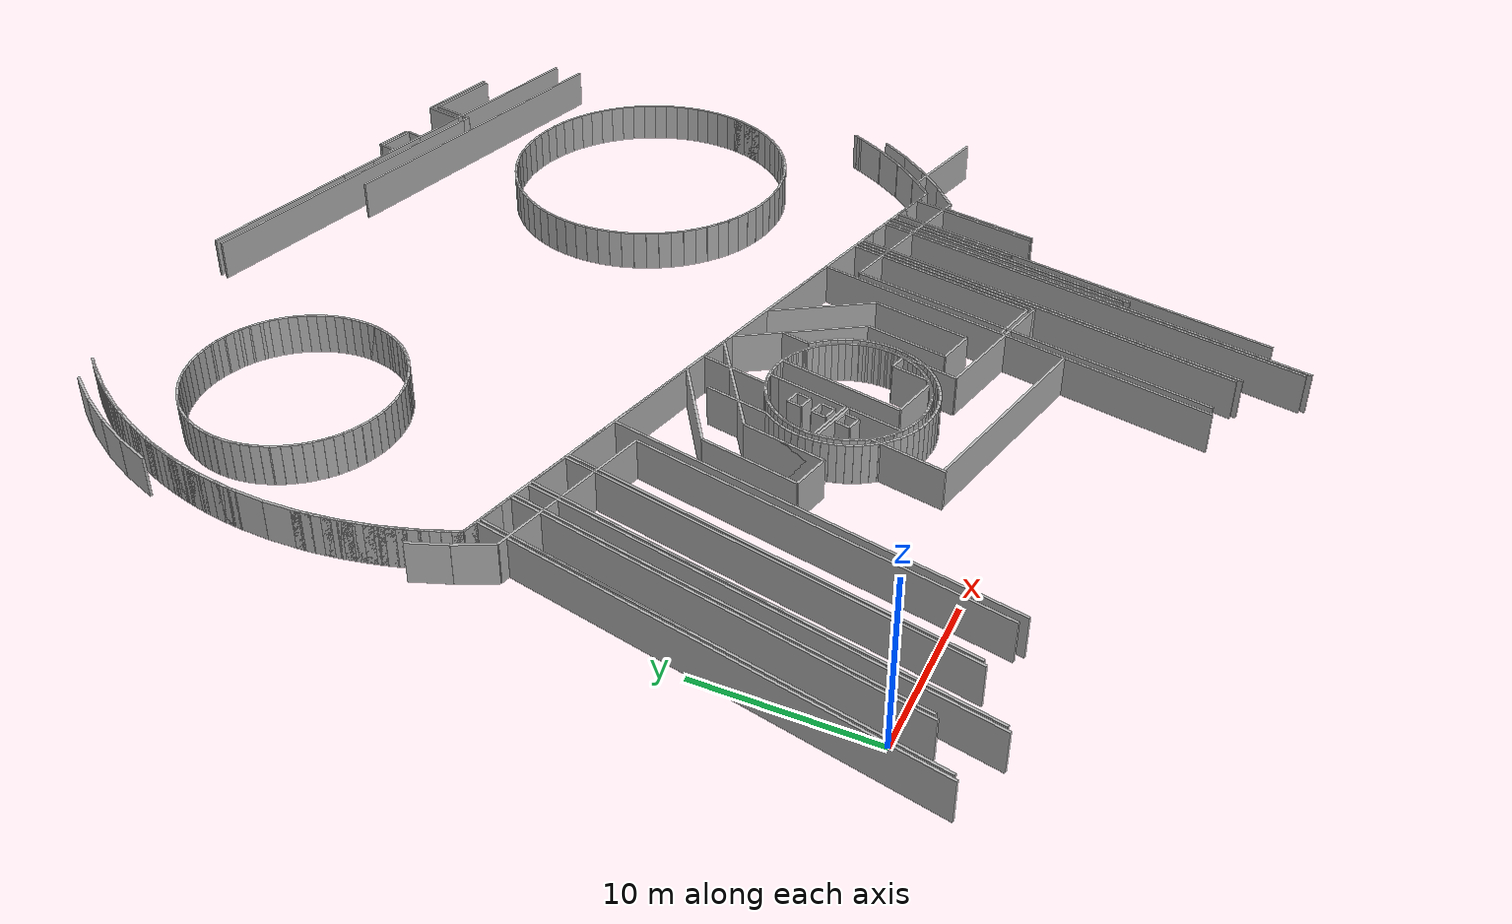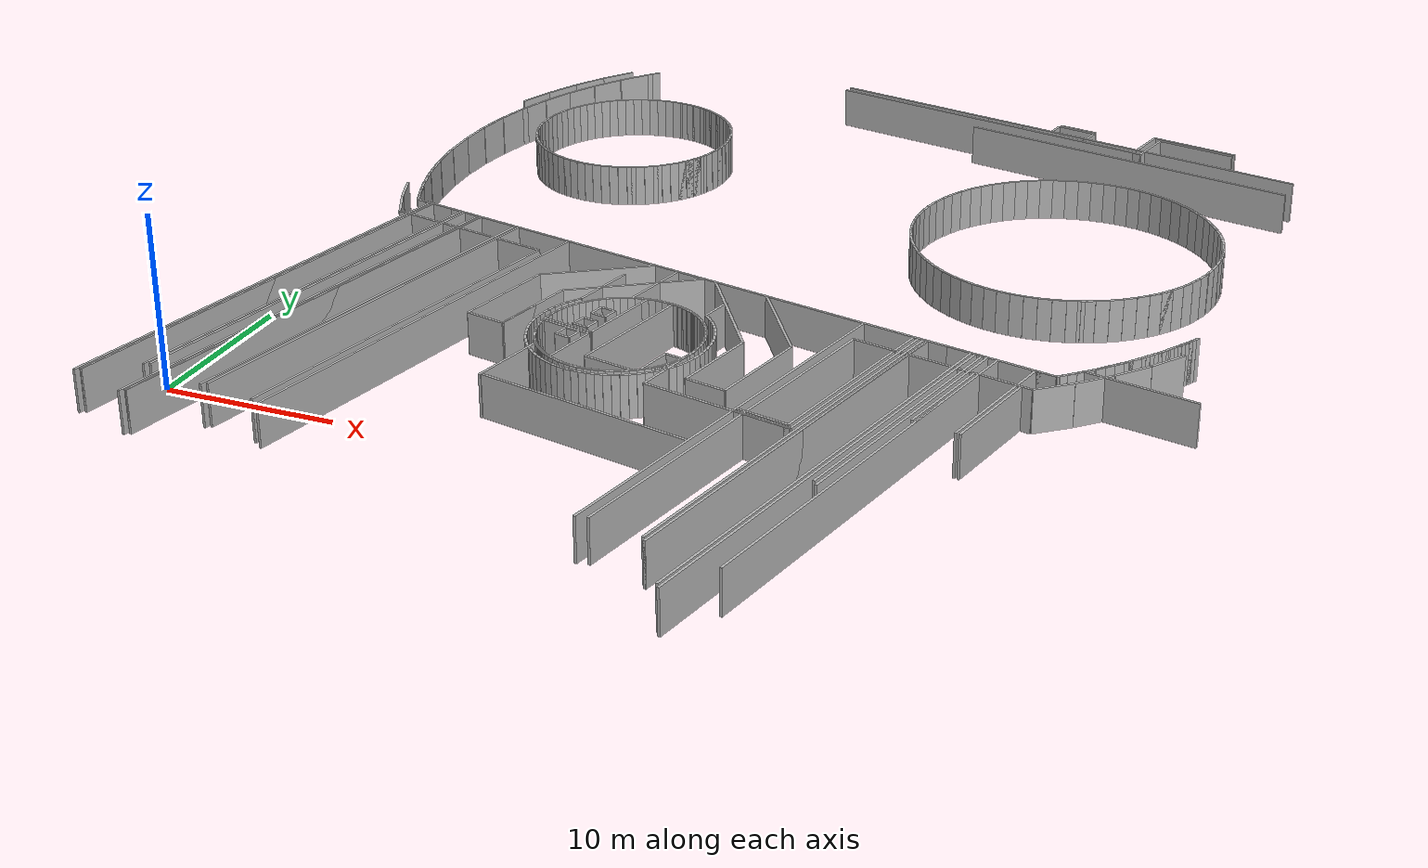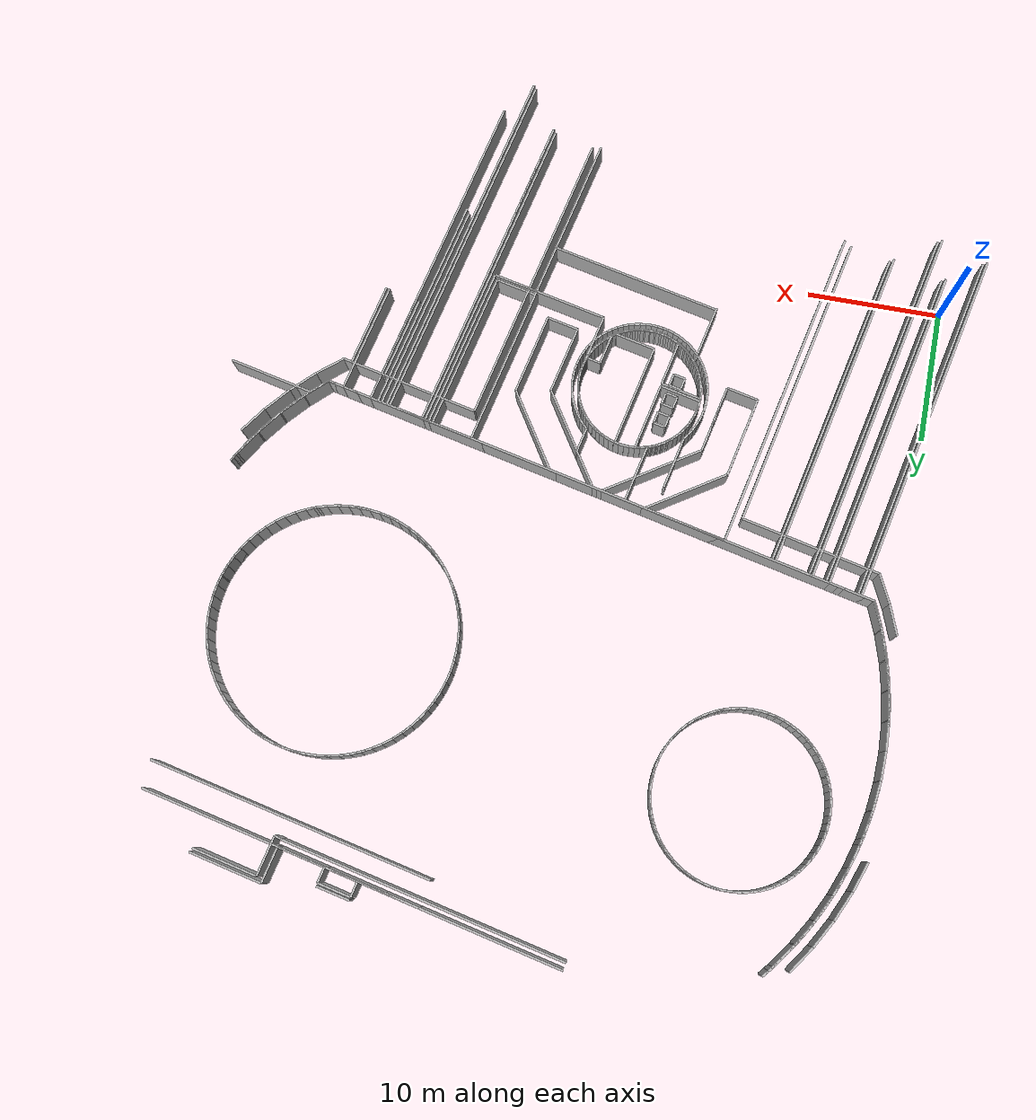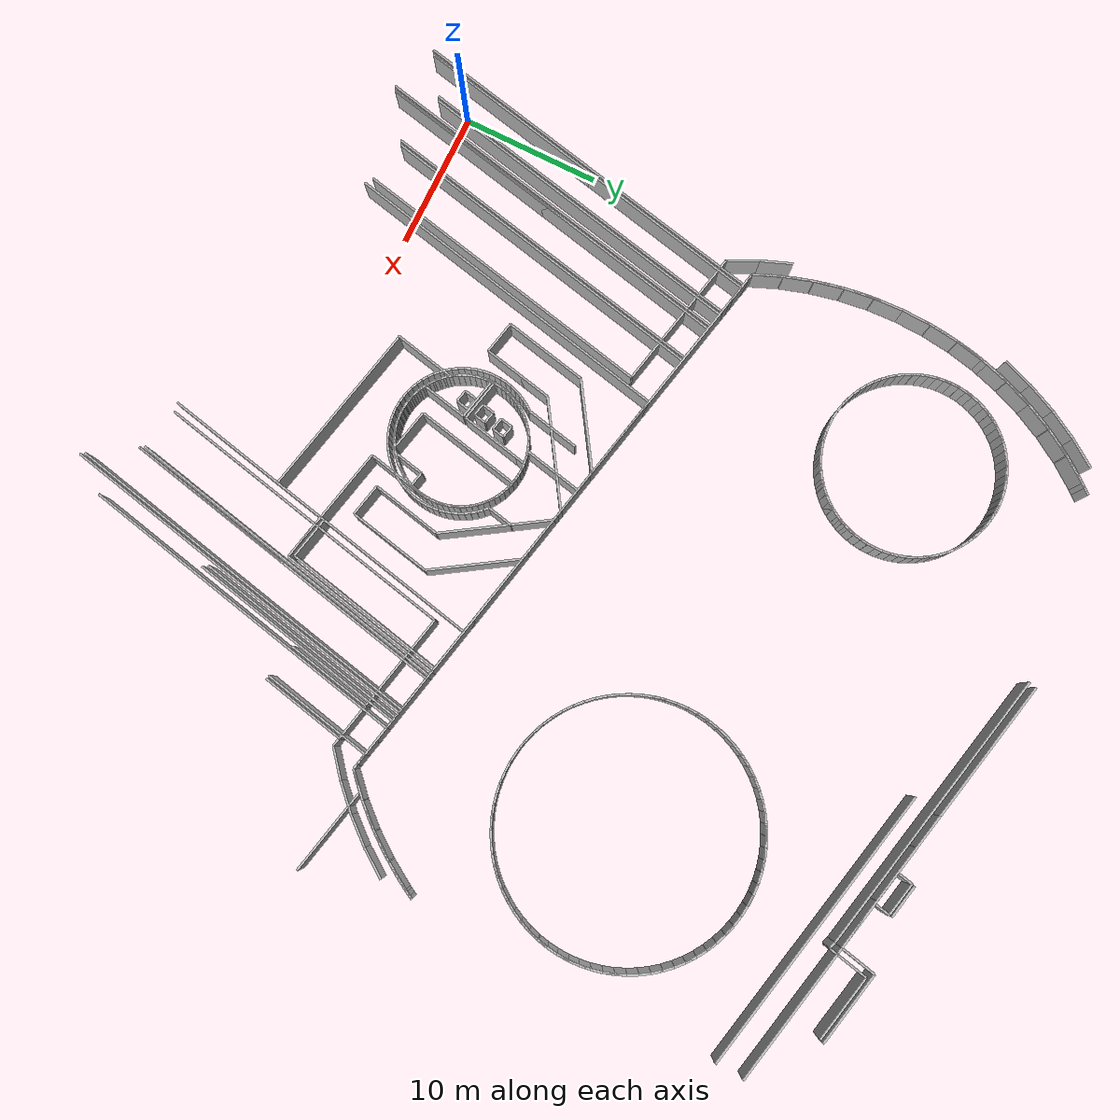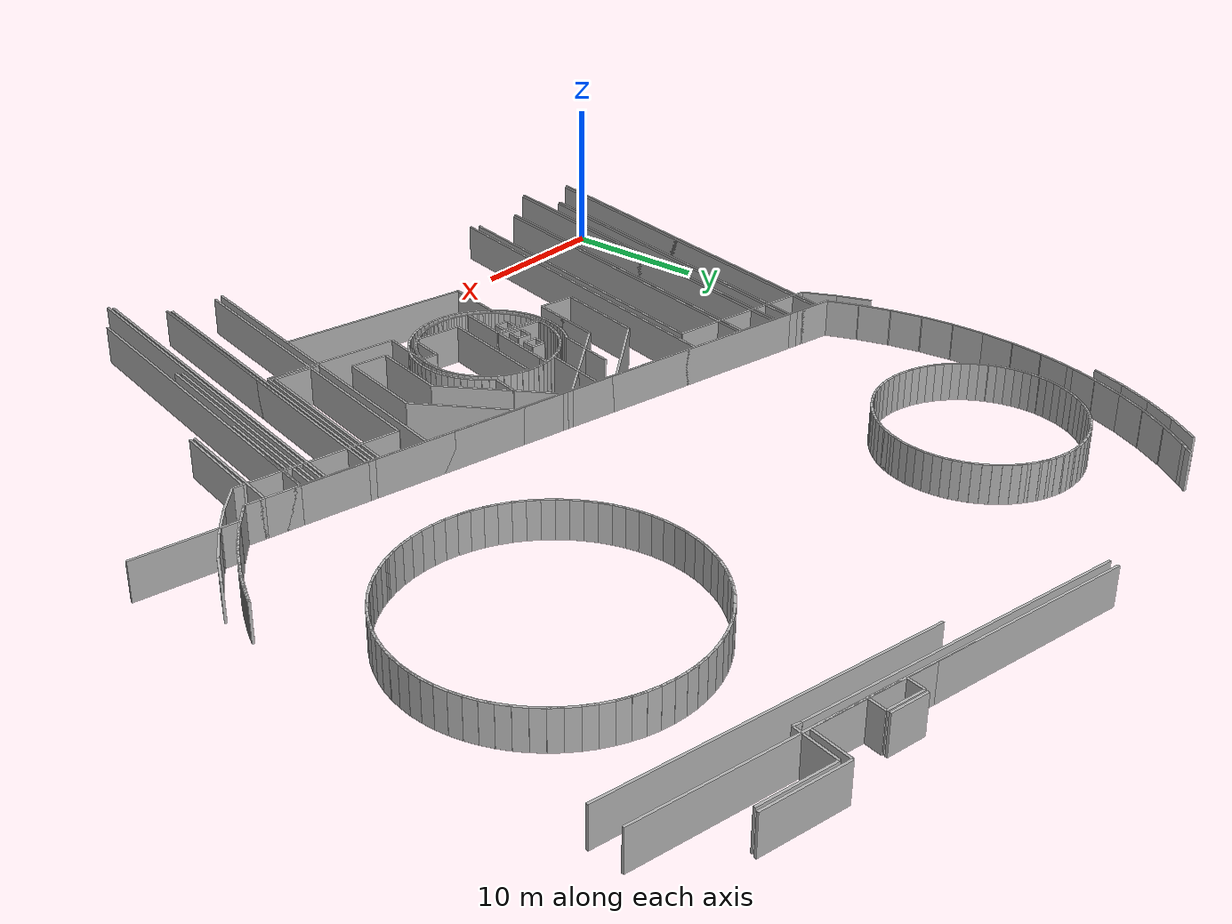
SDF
<?xml version="1.0" ?>
<sdf version="1.6">
  <model name="sps_2304">
    <pose frame="">0 0 0 0 -0 0</pose>
    <static>1</static>
    <self_collide>0</self_collide>
    <allow_auto_disable>0</allow_auto_disable>
    <link name="Wall241">
      <kinematic>0</kinematic>
      <gravity>1</gravity>
      <self_collide>0</self_collide>
      <collision name="collision">
        <geometry>
          <box>
            <size>24.8578 0.15 2.5</size>
          </box>
        </geometry>
        <pose frame="">0 0 0 0 -0 0</pose>
      </collision>
      <visual name="visual">
        <geometry>
          <box>
            <size>24.8578 0.15 2.5</size>
          </box>
        </geometry>
        <pose frame="">0 0 0 0 -0 0</pose>
        <cast_shadows>1</cast_shadows>
        <transparency>0.0</transparency>
      </visual>
      <pose frame="">3.15078 10.2592 1.25 0 0 -1.78506</pose>
    </link>
    <link name="Wall244">
      <kinematic>0</kinematic>
      <gravity>1</gravity>
      <self_collide>0</self_collide>
      <collision name="collision">
        <geometry>
          <box>
            <size>25.0952 0.15 2.5</size>
          </box>
        </geometry>
        <pose frame="">0 0 0 0 -0 0</pose>
      </collision>
      <visual name="visual">
        <geometry>
          <box>
            <size>25.0952 0.15 2.5</size>
          </box>
        </geometry>
        <pose frame="">0 0 0 0 -0 0</pose>
        <cast_shadows>1</cast_shadows>
        <transparency>0.0</transparency>
      </visual>
      <pose frame="">10.7935 8.4622 1.25 0 0 -1.78505</pose>
    </link>
    <link name="Wall254">
      <kinematic>0</kinematic>
      <gravity>1</gravity>
      <self_collide>0</self_collide>
      <collision name="collision">
        <geometry>
          <box>
            <size>8.3108 0.15 2.5</size>
          </box>
        </geometry>
        <pose frame="">0 0 0 0 -0 0</pose>
      </collision>
      <visual name="visual">
        <geometry>
          <box>
            <size>8.3108 0.15 2.5</size>
          </box>
        </geometry>
        <pose frame="">0 0 0 0 -0 0</pose>
        <cast_shadows>1</cast_shadows>
        <transparency>0.0</transparency>
      </visual>
      <pose frame="">42.1886 10.2351 1.25 0 -0 1.35655</pose>
    </link>
    <link name="Wall546">
      <kinematic>0</kinematic>
      <gravity>1</gravity>
      <self_collide>0</self_collide>
      <collision name="collision">
        <geometry>
          <box>
            <size>22.8546 0.15 2.5</size>
          </box>
        </geometry>
        <pose frame="">0 0 0 0 -0 0</pose>
      </collision>
      <visual name="visual">
        <geometry>
          <box>
            <size>22.8546 0.15 2.5</size>
          </box>
        </geometry>
        <pose frame="">0 0 0 0 -0 0</pose>
        <cast_shadows>1</cast_shadows>
        <transparency>0.0</transparency>
      </visual>
      <pose frame="">10.0221 7.73909 1.25 0 0 -1.78506</pose>
    </link>
    <link name="Wall547">
      <kinematic>0</kinematic>
      <gravity>1</gravity>
      <self_collide>0</self_collide>
      <collision name="collision">
        <geometry>
          <box>
            <size>10.5806 0.15 2.5</size>
          </box>
        </geometry>
        <pose frame="">0 0 0 0 -0 0</pose>
      </collision>
      <visual name="visual">
        <geometry>
          <box>
            <size>10.5806 0.15 2.5</size>
          </box>
        </geometry>
        <pose frame="">0 0 0 0 -0 0</pose>
        <cast_shadows>1</cast_shadows>
        <transparency>0.0</transparency>
      </visual>
      <pose frame="">7.28295 20.0318 1.25 0 0 -0.214621</pose>
    </link>
    <link name="Wall549">
      <kinematic>0</kinematic>
      <gravity>1</gravity>
      <self_collide>0</self_collide>
      <collision name="collision">
        <geometry>
          <box>
            <size>5.15297 0.15 2.5</size>
          </box>
        </geometry>
        <pose frame="">0 0 0 0 -0 0</pose>
      </collision>
      <visual name="visual">
        <geometry>
          <box>
            <size>5.15297 0.15 2.5</size>
          </box>
        </geometry>
        <pose frame="">0 0 0 0 -0 0</pose>
        <cast_shadows>1</cast_shadows>
        <transparency>0.0</transparency>
      </visual>
      <pose frame="">15.6258 11.836 1.25 0 -0 1.35789</pose>
    </link>
    <link name="Wall552">
      <kinematic>0</kinematic>
      <gravity>1</gravity>
      <self_collide>0</self_collide>
      <collision name="collision">
        <geometry>
          <box>
            <size>22.8558 0.15 2.5</size>
          </box>
        </geometry>
        <pose frame="">0 0 0 0 -0 0</pose>
      </collision>
      <visual name="visual">
        <geometry>
          <box>
            <size>22.8558 0.15 2.5</size>
          </box>
        </geometry>
        <pose frame="">0 0 0 0 -0 0</pose>
        <cast_shadows>1</cast_shadows>
        <transparency>0.0</transparency>
      </visual>
      <pose frame="">30.7377 3.23228 1.25 0 0 -1.78505</pose>
    </link>
    <link name="Wall553">
      <kinematic>0</kinematic>
      <gravity>1</gravity>
      <self_collide>0</self_collide>
      <collision name="collision">
        <geometry>
          <box>
            <size>12.4002 0.15 2.5</size>
          </box>
        </geometry>
        <pose frame="">0 0 0 0 -0 0</pose>
      </collision>
      <visual name="visual">
        <geometry>
          <box>
            <size>12.4002 0.15 2.5</size>
          </box>
        </geometry>
        <pose frame="">0 0 0 0 -0 0</pose>
        <cast_shadows>1</cast_shadows>
        <transparency>0.0</transparency>
      </visual>
      <pose frame="">35.011 9.70119 1.25 0 0 -1.78507</pose>
    </link>
    <link name="Wall554">
      <kinematic>0</kinematic>
      <gravity>1</gravity>
      <self_collide>0</self_collide>
      <collision name="collision">
        <geometry>
          <box>
            <size>3.76873 0.15 2.5</size>
          </box>
        </geometry>
        <pose frame="">0 0 0 0 -0 0</pose>
      </collision>
      <visual name="visual">
        <geometry>
          <box>
            <size>3.76873 0.15 2.5</size>
          </box>
        </geometry>
        <pose frame="">0 0 0 0 -0 0</pose>
        <cast_shadows>1</cast_shadows>
        <transparency>0.0</transparency>
      </visual>
      <pose frame="">38.6489 47.998 1.25 0 -0 2.92741</pose>
    </link>
    <link name="Wall555">
      <kinematic>0</kinematic>
      <gravity>1</gravity>
      <self_collide>0</self_collide>
      <collision name="collision">
        <geometry>
          <box>
            <size>8.30986 0.15 2.5</size>
          </box>
        </geometry>
        <pose frame="">0 0 0 0 -0 0</pose>
      </collision>
      <visual name="visual">
        <geometry>
          <box>
            <size>8.30986 0.15 2.5</size>
          </box>
        </geometry>
        <pose frame="">0 0 0 0 -0 0</pose>
        <cast_shadows>1</cast_shadows>
        <transparency>0.0</transparency>
      </visual>
      <pose frame="">40.0387 10.7024 1.25 0 -0 1.35652</pose>
    </link>
    <link name="Wall557">
      <kinematic>0</kinematic>
      <gravity>1</gravity>
      <self_collide>0</self_collide>
      <collision name="collision">
        <geometry>
          <box>
            <size>21.4794 0.15 2.5</size>
          </box>
        </geometry>
        <pose frame="">0 0 0 0 -0 0</pose>
      </collision>
      <visual name="visual">
        <geometry>
          <box>
            <size>21.4794 0.15 2.5</size>
          </box>
        </geometry>
        <pose frame="">0 0 0 0 -0 0</pose>
        <cast_shadows>1</cast_shadows>
        <transparency>0.0</transparency>
      </visual>
      <pose frame="">40.1071 45.6379 1.25 0 0 -0.213752</pose>
    </link>
    <link name="Wall835">
      <kinematic>0</kinematic>
      <gravity>1</gravity>
      <self_collide>0</self_collide>
      <collision name="collision">
        <geometry>
          <box>
            <size>27.308 0.15 2.5</size>
          </box>
        </geometry>
        <pose frame="">0 0 0 0 -0 0</pose>
      </collision>
      <visual name="visual">
        <geometry>
          <box>
            <size>27.308 0.15 2.5</size>
          </box>
        </geometry>
        <pose frame="">0 0 0 0 -0 0</pose>
        <cast_shadows>1</cast_shadows>
        <transparency>0.0</transparency>
      </visual>
      <pose frame="">0.496238 9.58308 1.25 0 0 -1.78506</pose>
    </link>
    <link name="Wall837">
      <kinematic>0</kinematic>
      <gravity>1</gravity>
      <self_collide>0</self_collide>
      <collision name="collision">
        <geometry>
          <box>
            <size>27.9452 0.15 2.5</size>
          </box>
        </geometry>
        <pose frame="">0 0 0 0 -0 0</pose>
      </collision>
      <visual name="visual">
        <geometry>
          <box>
            <size>27.9452 0.15 2.5</size>
          </box>
        </geometry>
        <pose frame="">0 0 0 0 -0 0</pose>
        <cast_shadows>1</cast_shadows>
        <transparency>0.0</transparency>
      </visual>
      <pose frame="">3.84597 8.51561 1.25 0 0 -1.78505</pose>
    </link>
    <link name="Wall838">
      <kinematic>0</kinematic>
      <gravity>1</gravity>
      <self_collide>0</self_collide>
      <collision name="collision">
        <geometry>
          <box>
            <size>27.6955 0.15 2.5</size>
          </box>
        </geometry>
        <pose frame="">0 0 0 0 -0 0</pose>
      </collision>
      <visual name="visual">
        <geometry>
          <box>
            <size>27.6955 0.15 2.5</size>
          </box>
        </geometry>
        <pose frame="">0 0 0 0 -0 0</pose>
        <cast_shadows>1</cast_shadows>
        <transparency>0.0</transparency>
      </visual>
      <pose frame="">4.11694 8.58458 1.25 0 0 -1.78505</pose>
    </link>
    <link name="Wall848">
      <kinematic>0</kinematic>
      <gravity>1</gravity>
      <self_collide>0</self_collide>
      <collision name="collision">
        <geometry>
          <box>
            <size>21.4006 0.15 2.5</size>
          </box>
        </geometry>
        <pose frame="">0 0 0 0 -0 0</pose>
      </collision>
      <visual name="visual">
        <geometry>
          <box>
            <size>21.4006 0.15 2.5</size>
          </box>
        </geometry>
        <pose frame="">0 0 0 0 -0 0</pose>
        <cast_shadows>1</cast_shadows>
        <transparency>0.0</transparency>
      </visual>
      <pose frame="">29.9182 49.3349 1.25 0 0 -0.214228</pose>
    </link>
    <link name="Wall849">
      <kinematic>0</kinematic>
      <gravity>1</gravity>
      <self_collide>0</self_collide>
      <collision name="collision">
        <geometry>
          <box>
            <size>6.31114 0.15 2.5</size>
          </box>
        </geometry>
        <pose frame="">0 0 0 0 -0 0</pose>
      </collision>
      <visual name="visual">
        <geometry>
          <box>
            <size>6.31114 0.15 2.5</size>
          </box>
        </geometry>
        <pose frame="">0 0 0 0 -0 0</pose>
        <cast_shadows>1</cast_shadows>
        <transparency>0.0</transparency>
      </visual>
      <pose frame="">42.2203 9.20488 1.25 0 -0 1.35652</pose>
    </link>
    <link name="Wall851">
      <kinematic>0</kinematic>
      <gravity>1</gravity>
      <self_collide>0</self_collide>
      <collision name="collision">
        <geometry>
          <box>
            <size>9.96599 0.15 2.5</size>
          </box>
        </geometry>
        <pose frame="">0 0 0 0 -0 0</pose>
      </collision>
      <visual name="visual">
        <geometry>
          <box>
            <size>9.96599 0.15 2.5</size>
          </box>
        </geometry>
        <pose frame="">0 0 0 0 -0 0</pose>
        <cast_shadows>1</cast_shadows>
        <transparency>0.0</transparency>
      </visual>
      <pose frame="">45.8498 46.4379 1.25 0 0 -0.213747</pose>
    </link>
    <link name="Wall1164">
      <kinematic>0</kinematic>
      <gravity>1</gravity>
      <self_collide>0</self_collide>
      <collision name="collision">
        <geometry>
          <box>
            <size>0.502882 0.15 2.5</size>
          </box>
        </geometry>
        <pose frame="">0 0 0 0 -0 0</pose>
      </collision>
      <visual name="visual">
        <geometry>
          <box>
            <size>0.502882 0.15 2.5</size>
          </box>
        </geometry>
        <pose frame="">0 0 0 0 -0 0</pose>
        <cast_shadows>1</cast_shadows>
        <transparency>0.0</transparency>
      </visual>
      <pose frame="">40.613 46.9823 1.25 0 -0 2.82706</pose>
    </link>
    <link name="Wall1165">
      <kinematic>0</kinematic>
      <gravity>1</gravity>
      <self_collide>0</self_collide>
      <collision name="collision">
        <geometry>
          <box>
            <size>2.95052 0.15 2.5</size>
          </box>
        </geometry>
        <pose frame="">0 0 0 0 -0 0</pose>
      </collision>
      <visual name="visual">
        <geometry>
          <box>
            <size>2.95052 0.15 2.5</size>
          </box>
        </geometry>
        <pose frame="">0 0 0 0 -0 0</pose>
        <cast_shadows>1</cast_shadows>
        <transparency>0.0</transparency>
      </visual>
      <pose frame="">41.1655 48.3461 1.25 0 0 -1.78485</pose>
    </link>
    <link name="Wall1166">
      <kinematic>0</kinematic>
      <gravity>1</gravity>
      <self_collide>0</self_collide>
      <collision name="collision">
        <geometry>
          <box>
            <size>5.50803 0.15 2.5</size>
          </box>
        </geometry>
        <pose frame="">0 0 0 0 -0 0</pose>
      </collision>
      <visual name="visual">
        <geometry>
          <box>
            <size>5.50803 0.15 2.5</size>
          </box>
        </geometry>
        <pose frame="">0 0 0 0 -0 0</pose>
        <cast_shadows>1</cast_shadows>
        <transparency>0.0</transparency>
      </visual>
      <pose frame="">43.745 49.601 1.25 0 -0 2.92728</pose>
    </link>
    <link name="Wall1445">
      <kinematic>0</kinematic>
      <gravity>1</gravity>
      <self_collide>0</self_collide>
      <collision name="collision">
        <geometry>
          <box>
            <size>3.97784 0.15 2.5</size>
          </box>
        </geometry>
        <pose frame="">0 0 0 0 -0 0</pose>
      </collision>
      <visual name="visual">
        <geometry>
          <box>
            <size>3.97784 0.15 2.5</size>
          </box>
        </geometry>
        <pose frame="">0 0 0 0 -0 0</pose>
        <cast_shadows>1</cast_shadows>
        <transparency>0.0</transparency>
      </visual>
      <pose frame="">18.0342 15.6526 1.25 0 -0 1.35664</pose>
    </link>
    <link name="Wall1447">
      <kinematic>0</kinematic>
      <gravity>1</gravity>
      <self_collide>0</self_collide>
      <collision name="collision">
        <geometry>
          <box>
            <size>3.10017 0.15 2.5</size>
          </box>
        </geometry>
        <pose frame="">0 0 0 0 -0 0</pose>
      </collision>
      <visual name="visual">
        <geometry>
          <box>
            <size>3.10017 0.15 2.5</size>
          </box>
        </geometry>
        <pose frame="">0 0 0 0 -0 0</pose>
        <cast_shadows>1</cast_shadows>
        <transparency>0.0</transparency>
      </visual>
      <pose frame="">31.9487 4.32939 1.25 0 -0 2.92727</pose>
    </link>
    <link name="Wall1448">
      <kinematic>0</kinematic>
      <gravity>1</gravity>
      <self_collide>0</self_collide>
      <collision name="collision">
        <geometry>
          <box>
            <size>24.8573 0.15 2.5</size>
          </box>
        </geometry>
        <pose frame="">0 0 0 0 -0 0</pose>
      </collision>
      <visual name="visual">
        <geometry>
          <box>
            <size>24.8573 0.15 2.5</size>
          </box>
        </geometry>
        <pose frame="">0 0 0 0 -0 0</pose>
        <cast_shadows>1</cast_shadows>
        <transparency>0.0</transparency>
      </visual>
      <pose frame="">33.9795 3.55119 1.25 0 0 -1.78504</pose>
    </link>
    <link name="Wall1450">
      <kinematic>0</kinematic>
      <gravity>1</gravity>
      <self_collide>0</self_collide>
      <collision name="collision">
        <geometry>
          <box>
            <size>25.1073 0.15 2.5</size>
          </box>
        </geometry>
        <pose frame="">0 0 0 0 -0 0</pose>
      </collision>
      <visual name="visual">
        <geometry>
          <box>
            <size>25.1073 0.15 2.5</size>
          </box>
        </geometry>
        <pose frame="">0 0 0 0 -0 0</pose>
        <cast_shadows>1</cast_shadows>
        <transparency>0.0</transparency>
      </visual>
      <pose frame="">34.1974 3.37587 1.25 0 0 -1.78505</pose>
    </link>
    <link name="Wall1453">
      <kinematic>0</kinematic>
      <gravity>1</gravity>
      <self_collide>0</self_collide>
      <collision name="collision">
        <geometry>
          <box>
            <size>7.25003 0.15 2.5</size>
          </box>
        </geometry>
        <pose frame="">0 0 0 0 -0 0</pose>
      </collision>
      <visual name="visual">
        <geometry>
          <box>
            <size>7.25003 0.15 2.5</size>
          </box>
        </geometry>
        <pose frame="">0 0 0 0 -0 0</pose>
        <cast_shadows>1</cast_shadows>
        <transparency>0.0</transparency>
      </visual>
      <pose frame="">36.71 13.6299 1.25 0 0 -0.213756</pose>
    </link>
    <link name="Wall1454">
      <kinematic>0</kinematic>
      <gravity>1</gravity>
      <self_collide>0</self_collide>
      <collision name="collision">
        <geometry>
          <box>
            <size>18.0988 0.15 2.5</size>
          </box>
        </geometry>
        <pose frame="">0 0 0 0 -0 0</pose>
      </collision>
      <visual name="visual">
        <geometry>
          <box>
            <size>18.0988 0.15 2.5</size>
          </box>
        </geometry>
        <pose frame="">0 0 0 0 -0 0</pose>
        <cast_shadows>1</cast_shadows>
        <transparency>0.0</transparency>
      </visual>
      <pose frame="">32.0788 16.6818 1.25 0 0 -0.213736</pose>
    </link>
    <link name="Wall1455">
      <kinematic>0</kinematic>
      <gravity>1</gravity>
      <self_collide>0</self_collide>
      <collision name="collision">
        <geometry>
          <box>
            <size>11.205 0.15 2.5</size>
          </box>
        </geometry>
        <pose frame="">0 0 0 0 -0 0</pose>
      </collision>
      <visual name="visual">
        <geometry>
          <box>
            <size>11.205 0.15 2.5</size>
          </box>
        </geometry>
        <pose frame="">0 0 0 0 -0 0</pose>
        <cast_shadows>1</cast_shadows>
        <transparency>0.0</transparency>
      </visual>
      <pose frame="">35.5052 48.6834 1.25 0 0 -0.213762</pose>
    </link>
    <link name="Wall1751">
      <kinematic>0</kinematic>
      <gravity>1</gravity>
      <self_collide>0</self_collide>
      <collision name="collision">
        <geometry>
          <box>
            <size>25.1081 0.15 2.5</size>
          </box>
        </geometry>
        <pose frame="">0 0 0 0 -0 0</pose>
      </collision>
      <visual name="visual">
        <geometry>
          <box>
            <size>25.1081 0.15 2.5</size>
          </box>
        </geometry>
        <pose frame="">0 0 0 0 -0 0</pose>
        <cast_shadows>1</cast_shadows>
        <transparency>0.0</transparency>
      </visual>
      <pose frame="">2.87984 10.1901 1.25 0 0 -1.78505</pose>
    </link>
    <link name="Wall1756">
      <kinematic>0</kinematic>
      <gravity>1</gravity>
      <self_collide>0</self_collide>
      <collision name="collision">
        <geometry>
          <box>
            <size>4.57776 0.15 2.5</size>
          </box>
        </geometry>
        <pose frame="">0 0 0 0 -0 0</pose>
      </collision>
      <visual name="visual">
        <geometry>
          <box>
            <size>4.57776 0.15 2.5</size>
          </box>
        </geometry>
        <pose frame="">0 0 0 0 -0 0</pose>
        <cast_shadows>1</cast_shadows>
        <transparency>0.0</transparency>
      </visual>
      <pose frame="">17.3343 5.53429 1.25 0 -0 1.35792</pose>
    </link>
    <link name="Wall1760">
      <kinematic>0</kinematic>
      <gravity>1</gravity>
      <self_collide>0</self_collide>
      <collision name="collision">
        <geometry>
          <box>
            <size>3.4001 0.15 2.5</size>
          </box>
        </geometry>
        <pose frame="">0 0 0 0 -0 0</pose>
      </collision>
      <visual name="visual">
        <geometry>
          <box>
            <size>3.4001 0.15 2.5</size>
          </box>
        </geometry>
        <pose frame="">0 0 0 0 -0 0</pose>
        <cast_shadows>1</cast_shadows>
        <transparency>0.0</transparency>
      </visual>
      <pose frame="">32.0315 4.00429 1.25 0 -0 2.92738</pose>
    </link>
    <link name="Wall1761">
      <kinematic>0</kinematic>
      <gravity>1</gravity>
      <self_collide>0</self_collide>
      <collision name="collision">
        <geometry>
          <box>
            <size>12.1003 0.15 2.5</size>
          </box>
        </geometry>
        <pose frame="">0 0 0 0 -0 0</pose>
      </collision>
      <visual name="visual">
        <geometry>
          <box>
            <size>12.1003 0.15 2.5</size>
          </box>
        </geometry>
        <pose frame="">0 0 0 0 -0 0</pose>
        <cast_shadows>1</cast_shadows>
        <transparency>0.0</transparency>
      </visual>
      <pose frame="">34.7497 9.91151 1.25 0 0 -1.78505</pose>
    </link>
    <link name="Wall1763">
      <kinematic>0</kinematic>
      <gravity>1</gravity>
      <self_collide>0</self_collide>
      <collision name="collision">
        <geometry>
          <box>
            <size>27.7072 0.15 2.5</size>
          </box>
        </geometry>
        <pose frame="">0 0 0 0 -0 0</pose>
      </collision>
      <visual name="visual">
        <geometry>
          <box>
            <size>27.7072 0.15 2.5</size>
          </box>
        </geometry>
        <pose frame="">0 0 0 0 -0 0</pose>
        <cast_shadows>1</cast_shadows>
        <transparency>0.0</transparency>
      </visual>
      <pose frame="">36.4614 1.55287 1.25 0 0 -1.78506</pose>
    </link>
    <link name="Wall1765">
      <kinematic>0</kinematic>
      <gravity>1</gravity>
      <self_collide>0</self_collide>
      <collision name="collision">
        <geometry>
          <box>
            <size>16.1998 0.15 2.5</size>
          </box>
        </geometry>
        <pose frame="">0 0 0 0 -0 0</pose>
      </collision>
      <visual name="visual">
        <geometry>
          <box>
            <size>16.1998 0.15 2.5</size>
          </box>
        </geometry>
        <pose frame="">0 0 0 0 -0 0</pose>
        <cast_shadows>1</cast_shadows>
        <transparency>0.0</transparency>
      </visual>
      <pose frame="">38.3202 7.0366 1.25 0 0 -1.78505</pose>
    </link>
    <link name="Wall1766">
      <kinematic>0</kinematic>
      <gravity>1</gravity>
      <self_collide>0</self_collide>
      <collision name="collision">
        <geometry>
          <box>
            <size>6.30947 0.15 2.5</size>
          </box>
        </geometry>
        <pose frame="">0 0 0 0 -0 0</pose>
      </collision>
      <visual name="visual">
        <geometry>
          <box>
            <size>6.30947 0.15 2.5</size>
          </box>
        </geometry>
        <pose frame="">0 0 0 0 -0 0</pose>
        <cast_shadows>1</cast_shadows>
        <transparency>0.0</transparency>
      </visual>
      <pose frame="">39.5817 9.7783 1.25 0 -0 1.35656</pose>
    </link>
    <link name="Wall1768">
      <kinematic>0</kinematic>
      <gravity>1</gravity>
      <self_collide>0</self_collide>
      <collision name="collision">
        <geometry>
          <box>
            <size>2.70021 0.15 2.5</size>
          </box>
        </geometry>
        <pose frame="">0 0 0 0 -0 0</pose>
      </collision>
      <visual name="visual">
        <geometry>
          <box>
            <size>2.70021 0.15 2.5</size>
          </box>
        </geometry>
        <pose frame="">0 0 0 0 -0 0</pose>
        <cast_shadows>1</cast_shadows>
        <transparency>0.0</transparency>
      </visual>
      <pose frame="">41.5719 12.5746 1.25 0 0 -0.213692</pose>
    </link>
    <link name="Wall1769">
      <kinematic>0</kinematic>
      <gravity>1</gravity>
      <self_collide>0</self_collide>
      <collision name="collision">
        <geometry>
          <box>
            <size>0.630111 0.15 2.5</size>
          </box>
        </geometry>
        <pose frame="">0 0 0 0 -0 0</pose>
      </collision>
      <visual name="visual">
        <geometry>
          <box>
            <size>0.630111 0.15 2.5</size>
          </box>
        </geometry>
        <pose frame="">0 0 0 0 -0 0</pose>
        <cast_shadows>1</cast_shadows>
        <transparency>0.0</transparency>
      </visual>
      <pose frame="">43.1991 12.2215 1.25 0 0 -0.213657</pose>
    </link>
    <link name="Wall1770">
      <kinematic>0</kinematic>
      <gravity>1</gravity>
      <self_collide>0</self_collide>
      <collision name="collision">
        <geometry>
          <box>
            <size>1.19396 0.15 2.5</size>
          </box>
        </geometry>
        <pose frame="">0 0 0 0 -0 0</pose>
      </collision>
      <visual name="visual">
        <geometry>
          <box>
            <size>1.19396 0.15 2.5</size>
          </box>
        </geometry>
        <pose frame="">0 0 0 0 -0 0</pose>
        <cast_shadows>1</cast_shadows>
        <transparency>0.0</transparency>
      </visual>
      <pose frame="">43.6554 14.1689 1.25 0 0 -0.213668</pose>
    </link>
    <link name="Wall1771">
      <kinematic>0</kinematic>
      <gravity>1</gravity>
      <self_collide>0</self_collide>
      <collision name="collision">
        <geometry>
          <box>
            <size>4.9279 0.15 2.5</size>
          </box>
        </geometry>
        <pose frame="">0 0 0 0 -0 0</pose>
      </collision>
      <visual name="visual">
        <geometry>
          <box>
            <size>4.9279 0.15 2.5</size>
          </box>
        </geometry>
        <pose frame="">0 0 0 0 -0 0</pose>
        <cast_shadows>1</cast_shadows>
        <transparency>0.0</transparency>
      </visual>
      <pose frame="">43.8863 49.2633 1.25 0 -0 2.92713</pose>
    </link>
    <link name="Wall2047">
      <kinematic>0</kinematic>
      <gravity>1</gravity>
      <self_collide>0</self_collide>
      <collision name="collision">
        <geometry>
          <box>
            <size>27.5582 0.15 2.5</size>
          </box>
        </geometry>
        <pose frame="">0 0 0 0 -0 0</pose>
      </collision>
      <visual name="visual">
        <geometry>
          <box>
            <size>27.5582 0.15 2.5</size>
          </box>
        </geometry>
        <pose frame="">0 0 0 0 -0 0</pose>
        <cast_shadows>1</cast_shadows>
        <transparency>0.0</transparency>
      </visual>
      <pose frame="">0.225456 9.51408 1.25 0 0 -1.78506</pose>
    </link>
    <link name="Wall2064">
      <kinematic>0</kinematic>
      <gravity>1</gravity>
      <self_collide>0</self_collide>
      <collision name="collision">
        <geometry>
          <box>
            <size>25.0955 0.15 2.5</size>
          </box>
        </geometry>
        <pose frame="">0 0 0 0 -0 0</pose>
      </collision>
      <visual name="visual">
        <geometry>
          <box>
            <size>25.0955 0.15 2.5</size>
          </box>
        </geometry>
        <pose frame="">0 0 0 0 -0 0</pose>
        <cast_shadows>1</cast_shadows>
        <transparency>0.0</transparency>
      </visual>
      <pose frame="">6.93383 9.30208 1.25 0 0 -1.78506</pose>
    </link>
    <link name="Wall2065">
      <kinematic>0</kinematic>
      <gravity>1</gravity>
      <self_collide>0</self_collide>
      <collision name="collision">
        <geometry>
          <box>
            <size>24.8453 0.15 2.5</size>
          </box>
        </geometry>
        <pose frame="">0 0 0 0 -0 0</pose>
      </collision>
      <visual name="visual">
        <geometry>
          <box>
            <size>24.8453 0.15 2.5</size>
          </box>
        </geometry>
        <pose frame="">0 0 0 0 -0 0</pose>
        <cast_shadows>1</cast_shadows>
        <transparency>0.0</transparency>
      </visual>
      <pose frame="">7.20473 9.37111 1.25 0 0 -1.78505</pose>
    </link>
    <link name="Wall2070">
      <kinematic>0</kinematic>
      <gravity>1</gravity>
      <self_collide>0</self_collide>
      <collision name="collision">
        <geometry>
          <box>
            <size>1.91861 0.15 2.5</size>
          </box>
        </geometry>
        <pose frame="">0 0 0 0 -0 0</pose>
      </collision>
      <visual name="visual">
        <geometry>
          <box>
            <size>1.91861 0.15 2.5</size>
          </box>
        </geometry>
        <pose frame="">0 0 0 0 -0 0</pose>
        <cast_shadows>1</cast_shadows>
        <transparency>0.0</transparency>
      </visual>
      <pose frame="">24.9954 15.1911 1.25 0 0 -1.78487</pose>
    </link>
    <link name="Wall2076">
      <kinematic>0</kinematic>
      <gravity>1</gravity>
      <self_collide>0</self_collide>
      <collision name="collision">
        <geometry>
          <box>
            <size>27.9574 0.15 2.5</size>
          </box>
        </geometry>
        <pose frame="">0 0 0 0 -0 0</pose>
      </collision>
      <visual name="visual">
        <geometry>
          <box>
            <size>27.9574 0.15 2.5</size>
          </box>
        </geometry>
        <pose frame="">0 0 0 0 -0 0</pose>
        <cast_shadows>1</cast_shadows>
        <transparency>0.0</transparency>
      </visual>
      <pose frame="">36.6792 1.37761 1.25 0 0 -1.78505</pose>
    </link>
    <link name="Wall2077">
      <kinematic>0</kinematic>
      <gravity>1</gravity>
      <self_collide>0</self_collide>
      <collision name="collision">
        <geometry>
          <box>
            <size>16.5001 0.15 2.5</size>
          </box>
        </geometry>
        <pose frame="">0 0 0 0 -0 0</pose>
      </collision>
      <visual name="visual">
        <geometry>
          <box>
            <size>16.5001 0.15 2.5</size>
          </box>
        </geometry>
        <pose frame="">0 0 0 0 -0 0</pose>
        <cast_shadows>1</cast_shadows>
        <transparency>0.0</transparency>
      </visual>
      <pose frame="">38.5814 6.82631 1.25 0 0 -1.78505</pose>
    </link>
    <link name="Wall2081">
      <kinematic>0</kinematic>
      <gravity>1</gravity>
      <self_collide>0</self_collide>
      <collision name="collision">
        <geometry>
          <box>
            <size>6.41308 0.15 2.5</size>
          </box>
        </geometry>
        <pose frame="">0 0 0 0 -0 0</pose>
      </collision>
      <visual name="visual">
        <geometry>
          <box>
            <size>6.41308 0.15 2.5</size>
          </box>
        </geometry>
        <pose frame="">0 0 0 0 -0 0</pose>
        <cast_shadows>1</cast_shadows>
        <transparency>0.0</transparency>
      </visual>
      <pose frame="">48.5419 14.4247 1.25 0 0 -0.214271</pose>
    </link>
    <link name="Wall2394">
      <kinematic>0</kinematic>
      <gravity>1</gravity>
      <self_collide>0</self_collide>
      <collision name="collision">
        <geometry>
          <box>
            <size>4.31626 0.15 2.5</size>
          </box>
        </geometry>
        <pose frame="">0 0 0 0 -0 0</pose>
      </collision>
      <visual name="visual">
        <geometry>
          <box>
            <size>4.31626 0.15 2.5</size>
          </box>
        </geometry>
        <pose frame="">0 0 0 0 -0 0</pose>
        <cast_shadows>1</cast_shadows>
        <transparency>0.0</transparency>
      </visual>
      <pose frame="">20.6217 16.9621 1.25 0 -0 1.35657</pose>
    </link>
    <link name="Wall2398">
      <kinematic>0</kinematic>
      <gravity>1</gravity>
      <self_collide>0</self_collide>
      <collision name="collision">
        <geometry>
          <box>
            <size>25.0965 0.15 2.5</size>
          </box>
        </geometry>
        <pose frame="">0 0 0 0 -0 0</pose>
      </collision>
      <visual name="visual">
        <geometry>
          <box>
            <size>25.0965 0.15 2.5</size>
          </box>
        </geometry>
        <pose frame="">0 0 0 0 -0 0</pose>
        <cast_shadows>1</cast_shadows>
        <transparency>0.0</transparency>
      </visual>
      <pose frame="">30.3366 4.2104 1.25 0 0 -1.78506</pose>
    </link>
    <link name="Wall2399">
      <kinematic>0</kinematic>
      <gravity>1</gravity>
      <self_collide>0</self_collide>
      <collision name="collision">
        <geometry>
          <box>
            <size>2.6499 0.15 2.5</size>
          </box>
        </geometry>
        <pose frame="">0 0 0 0 -0 0</pose>
      </collision>
      <visual name="visual">
        <geometry>
          <box>
            <size>2.6499 0.15 2.5</size>
          </box>
        </geometry>
        <pose frame="">0 0 0 0 -0 0</pose>
        <cast_shadows>1</cast_shadows>
        <transparency>0.0</transparency>
      </visual>
      <pose frame="">40.7721 48.8921 1.25 0 0 -1.78519</pose>
    </link>
    <link name="Wall2400">
      <kinematic>0</kinematic>
      <gravity>1</gravity>
      <self_collide>0</self_collide>
      <collision name="collision">
        <geometry>
          <box>
            <size>2.19988 0.15 2.5</size>
          </box>
        </geometry>
        <pose frame="">0 0 0 0 -0 0</pose>
      </collision>
      <visual name="visual">
        <geometry>
          <box>
            <size>2.19988 0.15 2.5</size>
          </box>
        </geometry>
        <pose frame="">0 0 0 0 -0 0</pose>
        <cast_shadows>1</cast_shadows>
        <transparency>0.0</transparency>
      </visual>
      <pose frame="">41.9972 14.5289 1.25 0 0 -0.213818</pose>
    </link>
    <link name="Wall2913">
      <kinematic>0</kinematic>
      <gravity>1</gravity>
      <self_collide>0</self_collide>
      <collision name="collision">
        <geometry>
          <box>
            <size>2.6499 0.15 2.5</size>
          </box>
        </geometry>
        <pose frame="">0 0 0 0 -0 0</pose>
      </collision>
      <visual name="visual">
        <geometry>
          <box>
            <size>2.6499 0.15 2.5</size>
          </box>
        </geometry>
        <pose frame="">0 0 0 0 -0 0</pose>
        <cast_shadows>1</cast_shadows>
        <transparency>0.0</transparency>
      </visual>
      <pose frame="">40.7721 48.8921 1.25 0 0 -1.78519</pose>
    </link>
    <link name="Wall2914">
      <kinematic>0</kinematic>
      <gravity>1</gravity>
      <self_collide>0</self_collide>
      <collision name="collision">
        <geometry>
          <box>
            <size>21.4 0.15 2.5</size>
          </box>
        </geometry>
        <pose frame="">0 0 0 0 -0 0</pose>
      </collision>
      <visual name="visual">
        <geometry>
          <box>
            <size>21.4 0.15 2.5</size>
          </box>
        </geometry>
        <pose frame="">0 0 0 0 -0 0</pose>
        <cast_shadows>1</cast_shadows>
        <transparency>0.0</transparency>
      </visual>
      <pose frame="">30.0348 49.8721 1.25 0 -0 2.92738</pose>
    </link>
    <link name="Wall2921">
      <kinematic>0</kinematic>
      <gravity>1</gravity>
      <self_collide>0</self_collide>
      <collision name="collision">
        <geometry>
          <box>
            <size>20.0003 0.15 2.5</size>
          </box>
        </geometry>
        <pose frame="">0 0 0 0 -0 0</pose>
      </collision>
      <visual name="visual">
        <geometry>
          <box>
            <size>20.0003 0.15 2.5</size>
          </box>
        </geometry>
        <pose frame="">0 0 0 0 -0 0</pose>
        <cast_shadows>1</cast_shadows>
        <transparency>0.0</transparency>
      </visual>
      <pose frame="">23.2331 18.5973 1.25 0 0 -0.214192</pose>
    </link>
    <link name="Wall4091">
      <kinematic>0</kinematic>
      <gravity>1</gravity>
      <self_collide>0</self_collide>
      <collision name="collision">
        <geometry>
          <box>
            <size>1.46341 0.15 2.5</size>
          </box>
        </geometry>
        <pose frame="">0 0 0 0 -0 0</pose>
      </collision>
      <visual name="visual">
        <geometry>
          <box>
            <size>1.46341 0.15 2.5</size>
          </box>
        </geometry>
        <pose frame="">0 0 0 0 -0 0</pose>
        <cast_shadows>1</cast_shadows>
        <transparency>0.0</transparency>
      </visual>
      <pose frame="">44.8718 14.6093 1.25 0 -0 0.747138</pose>
    </link>
    <link name="Wall4927">
      <kinematic>0</kinematic>
      <gravity>1</gravity>
      <self_collide>0</self_collide>
      <collision name="collision">
        <geometry>
          <box>
            <size>27.6955 0.15 2.5</size>
          </box>
        </geometry>
        <pose frame="">0 0 0 0 -0 0</pose>
      </collision>
      <visual name="visual">
        <geometry>
          <box>
            <size>27.6955 0.15 2.5</size>
          </box>
        </geometry>
        <pose frame="">0 0 0 0 -0 0</pose>
        <cast_shadows>1</cast_shadows>
        <transparency>0.0</transparency>
      </visual>
      <pose frame="">4.11694 8.58458 1.25 0 -0 1.35654</pose>
    </link>
    <link name="Wall4928">
      <kinematic>0</kinematic>
      <gravity>1</gravity>
      <self_collide>0</self_collide>
      <collision name="collision">
        <geometry>
          <box>
            <size>2.60003 0.15 2.5</size>
          </box>
        </geometry>
        <pose frame="">0 0 0 0 -0 0</pose>
      </collision>
      <visual name="visual">
        <geometry>
          <box>
            <size>2.60003 0.15 2.5</size>
          </box>
        </geometry>
        <pose frame="">0 0 0 0 -0 0</pose>
        <cast_shadows>1</cast_shadows>
        <transparency>0.0</transparency>
      </visual>
      <pose frame="">8.33153 21.8393 1.25 0 0 -0.214246</pose>
    </link>
    <link name="Wall5077">
      <kinematic>0</kinematic>
      <gravity>1</gravity>
      <self_collide>0</self_collide>
      <collision name="collision">
        <geometry>
          <box>
            <size>25.1095 0.15 2.5</size>
          </box>
        </geometry>
        <pose frame="">0 0 0 0 -0 0</pose>
      </collision>
      <visual name="visual">
        <geometry>
          <box>
            <size>25.1095 0.15 2.5</size>
          </box>
        </geometry>
        <pose frame="">0 0 0 0 -0 0</pose>
        <cast_shadows>1</cast_shadows>
        <transparency>0.0</transparency>
      </visual>
      <pose frame="">38.2529 2.49458 1.25 0 -0 1.35654</pose>
    </link>
    <link name="Wall5078">
      <kinematic>0</kinematic>
      <gravity>1</gravity>
      <self_collide>0</self_collide>
      <collision name="collision">
        <geometry>
          <box>
            <size>2.19988 0.15 2.5</size>
          </box>
        </geometry>
        <pose frame="">0 0 0 0 -0 0</pose>
      </collision>
      <visual name="visual">
        <geometry>
          <box>
            <size>2.19988 0.15 2.5</size>
          </box>
        </geometry>
        <pose frame="">0 0 0 0 -0 0</pose>
        <cast_shadows>1</cast_shadows>
        <transparency>0.0</transparency>
      </visual>
      <pose frame="">41.9972 14.5289 1.25 0 0 -0.213818</pose>
    </link>
    <link name="Wall5079">
      <kinematic>0</kinematic>
      <gravity>1</gravity>
      <self_collide>0</self_collide>
      <collision name="collision">
        <geometry>
          <box>
            <size>2.40081 0.15 2.5</size>
          </box>
        </geometry>
        <pose frame="">0 0 0 0 -0 0</pose>
      </collision>
      <visual name="visual">
        <geometry>
          <box>
            <size>2.40081 0.15 2.5</size>
          </box>
        </geometry>
        <pose frame="">0 0 0 0 -0 0</pose>
        <cast_shadows>1</cast_shadows>
        <transparency>0.0</transparency>
      </visual>
      <pose frame="">27.9911 6.52711 1.25 0 -0 2.92873</pose>
    </link>
    <link name="Wall5080">
      <kinematic>0</kinematic>
      <gravity>1</gravity>
      <self_collide>0</self_collide>
      <collision name="collision">
        <geometry>
          <box>
            <size>5.15287 0.15 2.5</size>
          </box>
        </geometry>
        <pose frame="">0 0 0 0 -0 0</pose>
      </collision>
      <visual name="visual">
        <geometry>
          <box>
            <size>5.15287 0.15 2.5</size>
          </box>
        </geometry>
        <pose frame="">0 0 0 0 -0 0</pose>
        <cast_shadows>1</cast_shadows>
        <transparency>0.0</transparency>
      </visual>
      <pose frame="">27.3621 9.29899 1.25 0 -0 1.35793</pose>
    </link>
    <link name="Wall5081">
      <kinematic>0</kinematic>
      <gravity>1</gravity>
      <self_collide>0</self_collide>
      <collision name="collision">
        <geometry>
          <box>
            <size>7.98288 0.15 2.5</size>
          </box>
        </geometry>
        <pose frame="">0 0 0 0 -0 0</pose>
      </collision>
      <visual name="visual">
        <geometry>
          <box>
            <size>7.98288 0.15 2.5</size>
          </box>
        </geometry>
        <pose frame="">0 0 0 0 -0 0</pose>
        <cast_shadows>1</cast_shadows>
        <transparency>0.0</transparency>
      </visual>
      <pose frame="">25.7436 15.1719 1.25 0 -0 2.14348</pose>
    </link>
    <link name="Wall5082">
      <kinematic>0</kinematic>
      <gravity>1</gravity>
      <self_collide>0</self_collide>
      <collision name="collision">
        <geometry>
          <box>
            <size>3.39548 0.15 2.5</size>
          </box>
        </geometry>
        <pose frame="">0 0 0 0 -0 0</pose>
      </collision>
      <visual name="visual">
        <geometry>
          <box>
            <size>3.39548 0.15 2.5</size>
          </box>
        </geometry>
        <pose frame="">0 0 0 0 -0 0</pose>
        <cast_shadows>1</cast_shadows>
        <transparency>0.0</transparency>
      </visual>
      <pose frame="">25.2397 18.1663 1.25 0 0 -0.213789</pose>
    </link>
    <link name="Wall5083">
      <kinematic>0</kinematic>
      <gravity>1</gravity>
      <self_collide>0</self_collide>
      <collision name="collision">
        <geometry>
          <box>
            <size>6.57427 0.15 2.5</size>
          </box>
        </geometry>
        <pose frame="">0 0 0 0 -0 0</pose>
      </collision>
      <visual name="visual">
        <geometry>
          <box>
            <size>6.57427 0.15 2.5</size>
          </box>
        </geometry>
        <pose frame="">0 0 0 0 -0 0</pose>
        <cast_shadows>1</cast_shadows>
        <transparency>0.0</transparency>
      </visual>
      <pose frame="">28.6811 15.0441 1.25 0 0 -0.997731</pose>
    </link>
    <link name="Wall5298">
      <kinematic>0</kinematic>
      <gravity>1</gravity>
      <self_collide>0</self_collide>
      <collision name="collision">
        <geometry>
          <box>
            <size>27.308 0.15 2.5</size>
          </box>
        </geometry>
        <pose frame="">0 0 0 0 -0 0</pose>
      </collision>
      <visual name="visual">
        <geometry>
          <box>
            <size>27.308 0.15 2.5</size>
          </box>
        </geometry>
        <pose frame="">0 0 0 0 -0 0</pose>
        <cast_shadows>1</cast_shadows>
        <transparency>0.0</transparency>
      </visual>
      <pose frame="">0.496238 9.58308 1.25 0 -0 1.35653</pose>
    </link>
    <link name="Wall5299">
      <kinematic>0</kinematic>
      <gravity>1</gravity>
      <self_collide>0</self_collide>
      <collision name="collision">
        <geometry>
          <box>
            <size>2.1999 0.15 2.5</size>
          </box>
        </geometry>
        <pose frame="">0 0 0 0 -0 0</pose>
      </collision>
      <visual name="visual">
        <geometry>
          <box>
            <size>2.1999 0.15 2.5</size>
          </box>
        </geometry>
        <pose frame="">0 0 0 0 -0 0</pose>
        <cast_shadows>1</cast_shadows>
        <transparency>0.0</transparency>
      </visual>
      <pose frame="">4.47423 22.691 1.25 0 0 -0.214269</pose>
    </link>
    <link name="Wall5300">
      <kinematic>0</kinematic>
      <gravity>1</gravity>
      <self_collide>0</self_collide>
      <collision name="collision">
        <geometry>
          <box>
            <size>0.549618 0.15 2.5</size>
          </box>
        </geometry>
        <pose frame="">0 0 0 0 -0 0</pose>
      </collision>
      <visual name="visual">
        <geometry>
          <box>
            <size>0.549618 0.15 2.5</size>
          </box>
        </geometry>
        <pose frame="">0 0 0 0 -0 0</pose>
        <cast_shadows>1</cast_shadows>
        <transparency>0.0</transparency>
      </visual>
      <pose frame="">13.3285 43.681 1.25 0 0 -0.654517</pose>
    </link>
    <link name="Wall5301">
      <kinematic>0</kinematic>
      <gravity>1</gravity>
      <self_collide>0</self_collide>
      <collision name="collision">
        <geometry>
          <box>
            <size>0.549667 0.15 2.5</size>
          </box>
        </geometry>
        <pose frame="">0 0 0 0 -0 0</pose>
      </collision>
      <visual name="visual">
        <geometry>
          <box>
            <size>0.549667 0.15 2.5</size>
          </box>
        </geometry>
        <pose frame="">0 0 0 0 -0 0</pose>
        <cast_shadows>1</cast_shadows>
        <transparency>0.0</transparency>
      </visual>
      <pose frame="">13.7491 43.328 1.25 0 0 -0.741886</pose>
    </link>
    <link name="Wall5302">
      <kinematic>0</kinematic>
      <gravity>1</gravity>
      <self_collide>0</self_collide>
      <collision name="collision">
        <geometry>
          <box>
            <size>0.549638 0.15 2.5</size>
          </box>
        </geometry>
        <pose frame="">0 0 0 0 -0 0</pose>
      </collision>
      <visual name="visual">
        <geometry>
          <box>
            <size>0.549638 0.15 2.5</size>
          </box>
        </geometry>
        <pose frame="">0 0 0 0 -0 0</pose>
        <cast_shadows>1</cast_shadows>
        <transparency>0.0</transparency>
      </visual>
      <pose frame="">14.1373 42.9396 1.25 0 0 -0.829463</pose>
    </link>
    <link name="Wall5303">
      <kinematic>0</kinematic>
      <gravity>1</gravity>
      <self_collide>0</self_collide>
      <collision name="collision">
        <geometry>
          <box>
            <size>0.549652 0.15 2.5</size>
          </box>
        </geometry>
        <pose frame="">0 0 0 0 -0 0</pose>
      </collision>
      <visual name="visual">
        <geometry>
          <box>
            <size>0.549652 0.15 2.5</size>
          </box>
        </geometry>
        <pose frame="">0 0 0 0 -0 0</pose>
        <cast_shadows>1</cast_shadows>
        <transparency>0.0</transparency>
      </visual>
      <pose frame="">14.49 42.5188 1.25 0 0 -0.916746</pose>
    </link>
    <link name="Wall5304">
      <kinematic>0</kinematic>
      <gravity>1</gravity>
      <self_collide>0</self_collide>
      <collision name="collision">
        <geometry>
          <box>
            <size>0.54959 0.15 2.5</size>
          </box>
        </geometry>
        <pose frame="">0 0 0 0 -0 0</pose>
      </collision>
      <visual name="visual">
        <geometry>
          <box>
            <size>0.54959 0.15 2.5</size>
          </box>
        </geometry>
        <pose frame="">0 0 0 0 -0 0</pose>
        <cast_shadows>1</cast_shadows>
        <transparency>0.0</transparency>
      </visual>
      <pose frame="">14.8049 42.0689 1.25 0 0 -1.00371</pose>
    </link>
    <link name="Wall5305">
      <kinematic>0</kinematic>
      <gravity>1</gravity>
      <self_collide>0</self_collide>
      <collision name="collision">
        <geometry>
          <box>
            <size>0.549453 0.15 2.5</size>
          </box>
        </geometry>
        <pose frame="">0 0 0 0 -0 0</pose>
      </collision>
      <visual name="visual">
        <geometry>
          <box>
            <size>0.549453 0.15 2.5</size>
          </box>
        </geometry>
        <pose frame="">0 0 0 0 -0 0</pose>
        <cast_shadows>1</cast_shadows>
        <transparency>0.0</transparency>
      </visual>
      <pose frame="">15.0793 41.5934 1.25 0 0 -1.09105</pose>
    </link>
    <link name="Wall5306">
      <kinematic>0</kinematic>
      <gravity>1</gravity>
      <self_collide>0</self_collide>
      <collision name="collision">
        <geometry>
          <box>
            <size>0.549769 0.15 2.5</size>
          </box>
        </geometry>
        <pose frame="">0 0 0 0 -0 0</pose>
      </collision>
      <visual name="visual">
        <geometry>
          <box>
            <size>0.549769 0.15 2.5</size>
          </box>
        </geometry>
        <pose frame="">0 0 0 0 -0 0</pose>
        <cast_shadows>1</cast_shadows>
        <transparency>0.0</transparency>
      </visual>
      <pose frame="">15.3112 41.0957 1.25 0 0 -1.17846</pose>
    </link>
    <link name="Wall5307">
      <kinematic>0</kinematic>
      <gravity>1</gravity>
      <self_collide>0</self_collide>
      <collision name="collision">
        <geometry>
          <box>
            <size>0.549575 0.15 2.5</size>
          </box>
        </geometry>
        <pose frame="">0 0 0 0 -0 0</pose>
      </collision>
      <visual name="visual">
        <geometry>
          <box>
            <size>0.549575 0.15 2.5</size>
          </box>
        </geometry>
        <pose frame="">0 0 0 0 -0 0</pose>
        <cast_shadows>1</cast_shadows>
        <transparency>0.0</transparency>
      </visual>
      <pose frame="">15.4989 40.5796 1.25 0 0 -1.26555</pose>
    </link>
    <link name="Wall5308">
      <kinematic>0</kinematic>
      <gravity>1</gravity>
      <self_collide>0</self_collide>
      <collision name="collision">
        <geometry>
          <box>
            <size>0.549622 0.15 2.5</size>
          </box>
        </geometry>
        <pose frame="">0 0 0 0 -0 0</pose>
      </collision>
      <visual name="visual">
        <geometry>
          <box>
            <size>0.549622 0.15 2.5</size>
          </box>
        </geometry>
        <pose frame="">0 0 0 0 -0 0</pose>
        <cast_shadows>1</cast_shadows>
        <transparency>0.0</transparency>
      </visual>
      <pose frame="">15.6409 40.0492 1.25 0 0 -1.35286</pose>
    </link>
    <link name="Wall5309">
      <kinematic>0</kinematic>
      <gravity>1</gravity>
      <self_collide>0</self_collide>
      <collision name="collision">
        <geometry>
          <box>
            <size>0.549634 0.15 2.5</size>
          </box>
        </geometry>
        <pose frame="">0 0 0 0 -0 0</pose>
      </collision>
      <visual name="visual">
        <geometry>
          <box>
            <size>0.549634 0.15 2.5</size>
          </box>
        </geometry>
        <pose frame="">0 0 0 0 -0 0</pose>
        <cast_shadows>1</cast_shadows>
        <transparency>0.0</transparency>
      </visual>
      <pose frame="">15.736 39.5084 1.25 0 0 -1.44062</pose>
    </link>
    <link name="Wall5310">
      <kinematic>0</kinematic>
      <gravity>1</gravity>
      <self_collide>0</self_collide>
      <collision name="collision">
        <geometry>
          <box>
            <size>0.549538 0.15 2.5</size>
          </box>
        </geometry>
        <pose frame="">0 0 0 0 -0 0</pose>
      </collision>
      <visual name="visual">
        <geometry>
          <box>
            <size>0.549538 0.15 2.5</size>
          </box>
        </geometry>
        <pose frame="">0 0 0 0 -0 0</pose>
        <cast_shadows>1</cast_shadows>
        <transparency>0.0</transparency>
      </visual>
      <pose frame="">15.7837 38.9614 1.25 0 0 -1.52702</pose>
    </link>
    <link name="Wall5311">
      <kinematic>0</kinematic>
      <gravity>1</gravity>
      <self_collide>0</self_collide>
      <collision name="collision">
        <geometry>
          <box>
            <size>0.549546 0.15 2.5</size>
          </box>
        </geometry>
        <pose frame="">0 0 0 0 -0 0</pose>
      </collision>
      <visual name="visual">
        <geometry>
          <box>
            <size>0.549546 0.15 2.5</size>
          </box>
        </geometry>
        <pose frame="">0 0 0 0 -0 0</pose>
        <cast_shadows>1</cast_shadows>
        <transparency>0.0</transparency>
      </visual>
      <pose frame="">15.7836 38.4124 1.25 0 0 -1.6149</pose>
    </link>
    <link name="Wall5312">
      <kinematic>0</kinematic>
      <gravity>1</gravity>
      <self_collide>0</self_collide>
      <collision name="collision">
        <geometry>
          <box>
            <size>0.549713 0.15 2.5</size>
          </box>
        </geometry>
        <pose frame="">0 0 0 0 -0 0</pose>
      </collision>
      <visual name="visual">
        <geometry>
          <box>
            <size>0.549713 0.15 2.5</size>
          </box>
        </geometry>
        <pose frame="">0 0 0 0 -0 0</pose>
        <cast_shadows>1</cast_shadows>
        <transparency>0.0</transparency>
      </visual>
      <pose frame="">15.7355 37.8654 1.25 0 0 -1.70208</pose>
    </link>
    <link name="Wall5313">
      <kinematic>0</kinematic>
      <gravity>1</gravity>
      <self_collide>0</self_collide>
      <collision name="collision">
        <geometry>
          <box>
            <size>0.549661 0.15 2.5</size>
          </box>
        </geometry>
        <pose frame="">0 0 0 0 -0 0</pose>
      </collision>
      <visual name="visual">
        <geometry>
          <box>
            <size>0.549661 0.15 2.5</size>
          </box>
        </geometry>
        <pose frame="">0 0 0 0 -0 0</pose>
        <cast_shadows>1</cast_shadows>
        <transparency>0.0</transparency>
      </visual>
      <pose frame="">15.64 37.3246 1.25 0 0 -1.78906</pose>
    </link>
    <link name="Wall5314">
      <kinematic>0</kinematic>
      <gravity>1</gravity>
      <self_collide>0</self_collide>
      <collision name="collision">
        <geometry>
          <box>
            <size>0.549473 0.15 2.5</size>
          </box>
        </geometry>
        <pose frame="">0 0 0 0 -0 0</pose>
      </collision>
      <visual name="visual">
        <geometry>
          <box>
            <size>0.549473 0.15 2.5</size>
          </box>
        </geometry>
        <pose frame="">0 0 0 0 -0 0</pose>
        <cast_shadows>1</cast_shadows>
        <transparency>0.0</transparency>
      </visual>
      <pose frame="">15.4978 36.7943 1.25 0 0 -1.87656</pose>
    </link>
    <link name="Wall5315">
      <kinematic>0</kinematic>
      <gravity>1</gravity>
      <self_collide>0</self_collide>
      <collision name="collision">
        <geometry>
          <box>
            <size>0.549763 0.15 2.5</size>
          </box>
        </geometry>
        <pose frame="">0 0 0 0 -0 0</pose>
      </collision>
      <visual name="visual">
        <geometry>
          <box>
            <size>0.549763 0.15 2.5</size>
          </box>
        </geometry>
        <pose frame="">0 0 0 0 -0 0</pose>
        <cast_shadows>1</cast_shadows>
        <transparency>0.0</transparency>
      </visual>
      <pose frame="">15.3097 36.2784 1.25 0 0 -1.96398</pose>
    </link>
    <link name="Wall5316">
      <kinematic>0</kinematic>
      <gravity>1</gravity>
      <self_collide>0</self_collide>
      <collision name="collision">
        <geometry>
          <box>
            <size>0.549537 0.15 2.5</size>
          </box>
        </geometry>
        <pose frame="">0 0 0 0 -0 0</pose>
      </collision>
      <visual name="visual">
        <geometry>
          <box>
            <size>0.549537 0.15 2.5</size>
          </box>
        </geometry>
        <pose frame="">0 0 0 0 -0 0</pose>
        <cast_shadows>1</cast_shadows>
        <transparency>0.0</transparency>
      </visual>
      <pose frame="">15.0775 35.7808 1.25 0 0 -2.05084</pose>
    </link>
    <link name="Wall5317">
      <kinematic>0</kinematic>
      <gravity>1</gravity>
      <self_collide>0</self_collide>
      <collision name="collision">
        <geometry>
          <box>
            <size>0.549534 0.15 2.5</size>
          </box>
        </geometry>
        <pose frame="">0 0 0 0 -0 0</pose>
      </collision>
      <visual name="visual">
        <geometry>
          <box>
            <size>0.549534 0.15 2.5</size>
          </box>
        </geometry>
        <pose frame="">0 0 0 0 -0 0</pose>
        <cast_shadows>1</cast_shadows>
        <transparency>0.0</transparency>
      </visual>
      <pose frame="">14.8029 35.3054 1.25 0 0 -2.13834</pose>
    </link>
    <link name="Wall5318">
      <kinematic>0</kinematic>
      <gravity>1</gravity>
      <self_collide>0</self_collide>
      <collision name="collision">
        <geometry>
          <box>
            <size>0.549681 0.15 2.5</size>
          </box>
        </geometry>
        <pose frame="">0 0 0 0 -0 0</pose>
      </collision>
      <visual name="visual">
        <geometry>
          <box>
            <size>0.549681 0.15 2.5</size>
          </box>
        </geometry>
        <pose frame="">0 0 0 0 -0 0</pose>
        <cast_shadows>1</cast_shadows>
        <transparency>0.0</transparency>
      </visual>
      <pose frame="">14.4878 34.8557 1.25 0 0 -2.22565</pose>
    </link>
    <link name="Wall5319">
      <kinematic>0</kinematic>
      <gravity>1</gravity>
      <self_collide>0</self_collide>
      <collision name="collision">
        <geometry>
          <box>
            <size>0.549667 0.15 2.5</size>
          </box>
        </geometry>
        <pose frame="">0 0 0 0 -0 0</pose>
      </collision>
      <visual name="visual">
        <geometry>
          <box>
            <size>0.549667 0.15 2.5</size>
          </box>
        </geometry>
        <pose frame="">0 0 0 0 -0 0</pose>
        <cast_shadows>1</cast_shadows>
        <transparency>0.0</transparency>
      </visual>
      <pose frame="">14.1348 34.4351 1.25 0 0 -2.31268</pose>
    </link>
    <link name="Wall5320">
      <kinematic>0</kinematic>
      <gravity>1</gravity>
      <self_collide>0</self_collide>
      <collision name="collision">
        <geometry>
          <box>
            <size>0.549679 0.15 2.5</size>
          </box>
        </geometry>
        <pose frame="">0 0 0 0 -0 0</pose>
      </collision>
      <visual name="visual">
        <geometry>
          <box>
            <size>0.549679 0.15 2.5</size>
          </box>
        </geometry>
        <pose frame="">0 0 0 0 -0 0</pose>
        <cast_shadows>1</cast_shadows>
        <transparency>0.0</transparency>
      </visual>
      <pose frame="">13.7464 34.0469 1.25 0 0 -2.40018</pose>
    </link>
    <link name="Wall5321">
      <kinematic>0</kinematic>
      <gravity>1</gravity>
      <self_collide>0</self_collide>
      <collision name="collision">
        <geometry>
          <box>
            <size>0.549507 0.15 2.5</size>
          </box>
        </geometry>
        <pose frame="">0 0 0 0 -0 0</pose>
      </collision>
      <visual name="visual">
        <geometry>
          <box>
            <size>0.549507 0.15 2.5</size>
          </box>
        </geometry>
        <pose frame="">0 0 0 0 -0 0</pose>
        <cast_shadows>1</cast_shadows>
        <transparency>0.0</transparency>
      </visual>
      <pose frame="">13.3256 33.6941 1.25 0 0 -2.48734</pose>
    </link>
    <link name="Wall5322">
      <kinematic>0</kinematic>
      <gravity>1</gravity>
      <self_collide>0</self_collide>
      <collision name="collision">
        <geometry>
          <box>
            <size>0.549557 0.15 2.5</size>
          </box>
        </geometry>
        <pose frame="">0 0 0 0 -0 0</pose>
      </collision>
      <visual name="visual">
        <geometry>
          <box>
            <size>0.549557 0.15 2.5</size>
          </box>
        </geometry>
        <pose frame="">0 0 0 0 -0 0</pose>
        <cast_shadows>1</cast_shadows>
        <transparency>0.0</transparency>
      </visual>
      <pose frame="">12.8758 33.3793 1.25 0 0 -2.5746</pose>
    </link>
    <link name="Wall5323">
      <kinematic>0</kinematic>
      <gravity>1</gravity>
      <self_collide>0</self_collide>
      <collision name="collision">
        <geometry>
          <box>
            <size>0.549615 0.15 2.5</size>
          </box>
        </geometry>
        <pose frame="">0 0 0 0 -0 0</pose>
      </collision>
      <visual name="visual">
        <geometry>
          <box>
            <size>0.549615 0.15 2.5</size>
          </box>
        </geometry>
        <pose frame="">0 0 0 0 -0 0</pose>
        <cast_shadows>1</cast_shadows>
        <transparency>0.0</transparency>
      </visual>
      <pose frame="">12.4003 33.1049 1.25 0 0 -2.662</pose>
    </link>
    <link name="Wall5324">
      <kinematic>0</kinematic>
      <gravity>1</gravity>
      <self_collide>0</self_collide>
      <collision name="collision">
        <geometry>
          <box>
            <size>0.5496 0.15 2.5</size>
          </box>
        </geometry>
        <pose frame="">0 0 0 0 -0 0</pose>
      </collision>
      <visual name="visual">
        <geometry>
          <box>
            <size>0.5496 0.15 2.5</size>
          </box>
        </geometry>
        <pose frame="">0 0 0 0 -0 0</pose>
        <cast_shadows>1</cast_shadows>
        <transparency>0.0</transparency>
      </visual>
      <pose frame="">11.9025 32.873 1.25 0 0 -2.74913</pose>
    </link>
    <link name="Wall5325">
      <kinematic>0</kinematic>
      <gravity>1</gravity>
      <self_collide>0</self_collide>
      <collision name="collision">
        <geometry>
          <box>
            <size>0.549826 0.15 2.5</size>
          </box>
        </geometry>
        <pose frame="">0 0 0 0 -0 0</pose>
      </collision>
      <visual name="visual">
        <geometry>
          <box>
            <size>0.549826 0.15 2.5</size>
          </box>
        </geometry>
        <pose frame="">0 0 0 0 -0 0</pose>
        <cast_shadows>1</cast_shadows>
        <transparency>0.0</transparency>
      </visual>
      <pose frame="">11.3864 32.6853 1.25 0 0 -2.83638</pose>
    </link>
    <link name="Wall5326">
      <kinematic>0</kinematic>
      <gravity>1</gravity>
      <self_collide>0</self_collide>
      <collision name="collision">
        <geometry>
          <box>
            <size>0.549509 0.15 2.5</size>
          </box>
        </geometry>
        <pose frame="">0 0 0 0 -0 0</pose>
      </collision>
      <visual name="visual">
        <geometry>
          <box>
            <size>0.549509 0.15 2.5</size>
          </box>
        </geometry>
        <pose frame="">0 0 0 0 -0 0</pose>
        <cast_shadows>1</cast_shadows>
        <transparency>0.0</transparency>
      </visual>
      <pose frame="">10.8559 32.5434 1.25 0 0 -2.92407</pose>
    </link>
    <link name="Wall5327">
      <kinematic>0</kinematic>
      <gravity>1</gravity>
      <self_collide>0</self_collide>
      <collision name="collision">
        <geometry>
          <box>
            <size>0.549484 0.15 2.5</size>
          </box>
        </geometry>
        <pose frame="">0 0 0 0 -0 0</pose>
      </collision>
      <visual name="visual">
        <geometry>
          <box>
            <size>0.549484 0.15 2.5</size>
          </box>
        </geometry>
        <pose frame="">0 0 0 0 -0 0</pose>
        <cast_shadows>1</cast_shadows>
        <transparency>0.0</transparency>
      </visual>
      <pose frame="">10.3153 32.4483 1.25 0 0 -3.01093</pose>
    </link>
    <link name="Wall5328">
      <kinematic>0</kinematic>
      <gravity>1</gravity>
      <self_collide>0</self_collide>
      <collision name="collision">
        <geometry>
          <box>
            <size>0.54971 0.15 2.5</size>
          </box>
        </geometry>
        <pose frame="">0 0 0 0 -0 0</pose>
      </collision>
      <visual name="visual">
        <geometry>
          <box>
            <size>0.54971 0.15 2.5</size>
          </box>
        </geometry>
        <pose frame="">0 0 0 0 -0 0</pose>
        <cast_shadows>1</cast_shadows>
        <transparency>0.0</transparency>
      </visual>
      <pose frame="">9.76827 32.4006 1.25 0 0 -3.09828</pose>
    </link>
    <link name="Wall5329">
      <kinematic>0</kinematic>
      <gravity>1</gravity>
      <self_collide>0</self_collide>
      <collision name="collision">
        <geometry>
          <box>
            <size>0.549535 0.15 2.5</size>
          </box>
        </geometry>
        <pose frame="">0 0 0 0 -0 0</pose>
      </collision>
      <visual name="visual">
        <geometry>
          <box>
            <size>0.549535 0.15 2.5</size>
          </box>
        </geometry>
        <pose frame="">0 0 0 0 -0 0</pose>
        <cast_shadows>1</cast_shadows>
        <transparency>0.0</transparency>
      </visual>
      <pose frame="">9.21917 32.4007 1.25 0 -0 3.09793</pose>
    </link>
    <link name="Wall5330">
      <kinematic>0</kinematic>
      <gravity>1</gravity>
      <self_collide>0</self_collide>
      <collision name="collision">
        <geometry>
          <box>
            <size>0.549721 0.15 2.5</size>
          </box>
        </geometry>
        <pose frame="">0 0 0 0 -0 0</pose>
      </collision>
      <visual name="visual">
        <geometry>
          <box>
            <size>0.549721 0.15 2.5</size>
          </box>
        </geometry>
        <pose frame="">0 0 0 0 -0 0</pose>
        <cast_shadows>1</cast_shadows>
        <transparency>0.0</transparency>
      </visual>
      <pose frame="">8.67217 32.4487 1.25 0 -0 3.0102</pose>
    </link>
    <link name="Wall5331">
      <kinematic>0</kinematic>
      <gravity>1</gravity>
      <self_collide>0</self_collide>
      <collision name="collision">
        <geometry>
          <box>
            <size>0.549483 0.15 2.5</size>
          </box>
        </geometry>
        <pose frame="">0 0 0 0 -0 0</pose>
      </collision>
      <visual name="visual">
        <geometry>
          <box>
            <size>0.549483 0.15 2.5</size>
          </box>
        </geometry>
        <pose frame="">0 0 0 0 -0 0</pose>
        <cast_shadows>1</cast_shadows>
        <transparency>0.0</transparency>
      </visual>
      <pose frame="">8.13146 32.5442 1.25 0 -0 2.92326</pose>
    </link>
    <link name="Wall5332">
      <kinematic>0</kinematic>
      <gravity>1</gravity>
      <self_collide>0</self_collide>
      <collision name="collision">
        <geometry>
          <box>
            <size>0.549648 0.15 2.5</size>
          </box>
        </geometry>
        <pose frame="">0 0 0 0 -0 0</pose>
      </collision>
      <visual name="visual">
        <geometry>
          <box>
            <size>0.549648 0.15 2.5</size>
          </box>
        </geometry>
        <pose frame="">0 0 0 0 -0 0</pose>
        <cast_shadows>1</cast_shadows>
        <transparency>0.0</transparency>
      </visual>
      <pose frame="">7.60116 32.6864 1.25 0 -0 2.83593</pose>
    </link>
    <link name="Wall5333">
      <kinematic>0</kinematic>
      <gravity>1</gravity>
      <self_collide>0</self_collide>
      <collision name="collision">
        <geometry>
          <box>
            <size>0.54974 0.15 2.5</size>
          </box>
        </geometry>
        <pose frame="">0 0 0 0 -0 0</pose>
      </collision>
      <visual name="visual">
        <geometry>
          <box>
            <size>0.54974 0.15 2.5</size>
          </box>
        </geometry>
        <pose frame="">0 0 0 0 -0 0</pose>
        <cast_shadows>1</cast_shadows>
        <transparency>0.0</transparency>
      </visual>
      <pose frame="">7.08517 32.8744 1.25 0 -0 2.74851</pose>
    </link>
    <link name="Wall5334">
      <kinematic>0</kinematic>
      <gravity>1</gravity>
      <self_collide>0</self_collide>
      <collision name="collision">
        <geometry>
          <box>
            <size>0.549537 0.15 2.5</size>
          </box>
        </geometry>
        <pose frame="">0 0 0 0 -0 0</pose>
      </collision>
      <visual name="visual">
        <geometry>
          <box>
            <size>0.549537 0.15 2.5</size>
          </box>
        </geometry>
        <pose frame="">0 0 0 0 -0 0</pose>
        <cast_shadows>1</cast_shadows>
        <transparency>0.0</transparency>
      </visual>
      <pose frame="">6.58755 33.1066 1.25 0 -0 2.66155</pose>
    </link>
    <link name="Wall5335">
      <kinematic>0</kinematic>
      <gravity>1</gravity>
      <self_collide>0</self_collide>
      <collision name="collision">
        <geometry>
          <box>
            <size>0.549632 0.15 2.5</size>
          </box>
        </geometry>
        <pose frame="">0 0 0 0 -0 0</pose>
      </collision>
      <visual name="visual">
        <geometry>
          <box>
            <size>0.549632 0.15 2.5</size>
          </box>
        </geometry>
        <pose frame="">0 0 0 0 -0 0</pose>
        <cast_shadows>1</cast_shadows>
        <transparency>0.0</transparency>
      </visual>
      <pose frame="">6.11214 33.3813 1.25 0 -0 2.57376</pose>
    </link>
    <link name="Wall5336">
      <kinematic>0</kinematic>
      <gravity>1</gravity>
      <self_collide>0</self_collide>
      <collision name="collision">
        <geometry>
          <box>
            <size>0.549607 0.15 2.5</size>
          </box>
        </geometry>
        <pose frame="">0 0 0 0 -0 0</pose>
      </collision>
      <visual name="visual">
        <geometry>
          <box>
            <size>0.549607 0.15 2.5</size>
          </box>
        </geometry>
        <pose frame="">0 0 0 0 -0 0</pose>
        <cast_shadows>1</cast_shadows>
        <transparency>0.0</transparency>
      </visual>
      <pose frame="">5.66247 33.6964 1.25 0 -0 2.48692</pose>
    </link>
    <link name="Wall5337">
      <kinematic>0</kinematic>
      <gravity>1</gravity>
      <self_collide>0</self_collide>
      <collision name="collision">
        <geometry>
          <box>
            <size>0.549532 0.15 2.5</size>
          </box>
        </geometry>
        <pose frame="">0 0 0 0 -0 0</pose>
      </collision>
      <visual name="visual">
        <geometry>
          <box>
            <size>0.549532 0.15 2.5</size>
          </box>
        </geometry>
        <pose frame="">0 0 0 0 -0 0</pose>
        <cast_shadows>1</cast_shadows>
        <transparency>0.0</transparency>
      </visual>
      <pose frame="">5.24197 34.0494 1.25 0 -0 2.39948</pose>
    </link>
    <link name="Wall5338">
      <kinematic>0</kinematic>
      <gravity>1</gravity>
      <self_collide>0</self_collide>
      <collision name="collision">
        <geometry>
          <box>
            <size>0.549679 0.15 2.5</size>
          </box>
        </geometry>
        <pose frame="">0 0 0 0 -0 0</pose>
      </collision>
      <visual name="visual">
        <geometry>
          <box>
            <size>0.549679 0.15 2.5</size>
          </box>
        </geometry>
        <pose frame="">0 0 0 0 -0 0</pose>
        <cast_shadows>1</cast_shadows>
        <transparency>0.0</transparency>
      </visual>
      <pose frame="">4.85384 34.4378 1.25 0 -0 2.31221</pose>
    </link>
    <link name="Wall5339">
      <kinematic>0</kinematic>
      <gravity>1</gravity>
      <self_collide>0</self_collide>
      <collision name="collision">
        <geometry>
          <box>
            <size>0.549715 0.15 2.5</size>
          </box>
        </geometry>
        <pose frame="">0 0 0 0 -0 0</pose>
      </collision>
      <visual name="visual">
        <geometry>
          <box>
            <size>0.549715 0.15 2.5</size>
          </box>
        </geometry>
        <pose frame="">0 0 0 0 -0 0</pose>
        <cast_shadows>1</cast_shadows>
        <transparency>0.0</transparency>
      </visual>
      <pose frame="">4.50094 34.8586 1.25 0 -0 2.22518</pose>
    </link>
    <link name="Wall5340">
      <kinematic>0</kinematic>
      <gravity>1</gravity>
      <self_collide>0</self_collide>
      <collision name="collision">
        <geometry>
          <box>
            <size>0.549608 0.15 2.5</size>
          </box>
        </geometry>
        <pose frame="">0 0 0 0 -0 0</pose>
      </collision>
      <visual name="visual">
        <geometry>
          <box>
            <size>0.549608 0.15 2.5</size>
          </box>
        </geometry>
        <pose frame="">0 0 0 0 -0 0</pose>
        <cast_shadows>1</cast_shadows>
        <transparency>0.0</transparency>
      </visual>
      <pose frame="">4.18606 35.3085 1.25 0 -0 2.13773</pose>
    </link>
    <link name="Wall5341">
      <kinematic>0</kinematic>
      <gravity>1</gravity>
      <self_collide>0</self_collide>
      <collision name="collision">
        <geometry>
          <box>
            <size>0.549399 0.15 2.5</size>
          </box>
        </geometry>
        <pose frame="">0 0 0 0 -0 0</pose>
      </collision>
      <visual name="visual">
        <geometry>
          <box>
            <size>0.549399 0.15 2.5</size>
          </box>
        </geometry>
        <pose frame="">0 0 0 0 -0 0</pose>
        <cast_shadows>1</cast_shadows>
        <transparency>0.0</transparency>
      </visual>
      <pose frame="">3.91167 35.784 1.25 0 -0 2.05059</pose>
    </link>
    <link name="Wall5342">
      <kinematic>0</kinematic>
      <gravity>1</gravity>
      <self_collide>0</self_collide>
      <collision name="collision">
        <geometry>
          <box>
            <size>0.549825 0.15 2.5</size>
          </box>
        </geometry>
        <pose frame="">0 0 0 0 -0 0</pose>
      </collision>
      <visual name="visual">
        <geometry>
          <box>
            <size>0.549825 0.15 2.5</size>
          </box>
        </geometry>
        <pose frame="">0 0 0 0 -0 0</pose>
        <cast_shadows>1</cast_shadows>
        <transparency>0.0</transparency>
      </visual>
      <pose frame="">3.67977 36.2817 1.25 0 -0 1.96309</pose>
    </link>
    <link name="Wall5343">
      <kinematic>0</kinematic>
      <gravity>1</gravity>
      <self_collide>0</self_collide>
      <collision name="collision">
        <geometry>
          <box>
            <size>0.549538 0.15 2.5</size>
          </box>
        </geometry>
        <pose frame="">0 0 0 0 -0 0</pose>
      </collision>
      <visual name="visual">
        <geometry>
          <box>
            <size>0.549538 0.15 2.5</size>
          </box>
        </geometry>
        <pose frame="">0 0 0 0 -0 0</pose>
        <cast_shadows>1</cast_shadows>
        <transparency>0.0</transparency>
      </visual>
      <pose frame="">3.49215 36.7978 1.25 0 -0 1.87583</pose>
    </link>
    <link name="Wall5344">
      <kinematic>0</kinematic>
      <gravity>1</gravity>
      <self_collide>0</self_collide>
      <collision name="collision">
        <geometry>
          <box>
            <size>0.549609 0.15 2.5</size>
          </box>
        </geometry>
        <pose frame="">0 0 0 0 -0 0</pose>
      </collision>
      <visual name="visual">
        <geometry>
          <box>
            <size>0.549609 0.15 2.5</size>
          </box>
        </geometry>
        <pose frame="">0 0 0 0 -0 0</pose>
        <cast_shadows>1</cast_shadows>
        <transparency>0.0</transparency>
      </visual>
      <pose frame="">3.35024 37.3282 1.25 0 -0 1.78862</pose>
    </link>
    <link name="Wall5345">
      <kinematic>0</kinematic>
      <gravity>1</gravity>
      <self_collide>0</self_collide>
      <collision name="collision">
        <geometry>
          <box>
            <size>0.549665 0.15 2.5</size>
          </box>
        </geometry>
        <pose frame="">0 0 0 0 -0 0</pose>
      </collision>
      <visual name="visual">
        <geometry>
          <box>
            <size>0.549665 0.15 2.5</size>
          </box>
        </geometry>
        <pose frame="">0 0 0 0 -0 0</pose>
        <cast_shadows>1</cast_shadows>
        <transparency>0.0</transparency>
      </visual>
      <pose frame="">3.25506 37.869 1.25 0 -0 1.70142</pose>
    </link>
    <link name="Wall5346">
      <kinematic>0</kinematic>
      <gravity>1</gravity>
      <self_collide>0</self_collide>
      <collision name="collision">
        <geometry>
          <box>
            <size>0.549527 0.15 2.5</size>
          </box>
        </geometry>
        <pose frame="">0 0 0 0 -0 0</pose>
      </collision>
      <visual name="visual">
        <geometry>
          <box>
            <size>0.549527 0.15 2.5</size>
          </box>
        </geometry>
        <pose frame="">0 0 0 0 -0 0</pose>
        <cast_shadows>1</cast_shadows>
        <transparency>0.0</transparency>
      </visual>
      <pose frame="">3.20736 38.416 1.25 0 -0 1.61413</pose>
    </link>
    <link name="Wall5347">
      <kinematic>0</kinematic>
      <gravity>1</gravity>
      <self_collide>0</self_collide>
      <collision name="collision">
        <geometry>
          <box>
            <size>0.549535 0.15 2.5</size>
          </box>
        </geometry>
        <pose frame="">0 0 0 0 -0 0</pose>
      </collision>
      <visual name="visual">
        <geometry>
          <box>
            <size>0.549535 0.15 2.5</size>
          </box>
        </geometry>
        <pose frame="">0 0 0 0 -0 0</pose>
        <cast_shadows>1</cast_shadows>
        <transparency>0.0</transparency>
      </visual>
      <pose frame="">3.20745 38.965 1.25 0 -0 1.52713</pose>
    </link>
    <link name="Wall5348">
      <kinematic>0</kinematic>
      <gravity>1</gravity>
      <self_collide>0</self_collide>
      <collision name="collision">
        <geometry>
          <box>
            <size>0.549721 0.15 2.5</size>
          </box>
        </geometry>
        <pose frame="">0 0 0 0 -0 0</pose>
      </collision>
      <visual name="visual">
        <geometry>
          <box>
            <size>0.549721 0.15 2.5</size>
          </box>
        </geometry>
        <pose frame="">0 0 0 0 -0 0</pose>
        <cast_shadows>1</cast_shadows>
        <transparency>0.0</transparency>
      </visual>
      <pose frame="">3.25545 39.512 1.25 0 -0 1.4394</pose>
    </link>
    <link name="Wall5349">
      <kinematic>0</kinematic>
      <gravity>1</gravity>
      <self_collide>0</self_collide>
      <collision name="collision">
        <geometry>
          <box>
            <size>0.549423 0.15 2.5</size>
          </box>
        </geometry>
        <pose frame="">0 0 0 0 -0 0</pose>
      </collision>
      <visual name="visual">
        <geometry>
          <box>
            <size>0.549423 0.15 2.5</size>
          </box>
        </geometry>
        <pose frame="">0 0 0 0 -0 0</pose>
        <cast_shadows>1</cast_shadows>
        <transparency>0.0</transparency>
      </visual>
      <pose frame="">3.35097 40.0527 1.25 0 -0 1.35244</pose>
    </link>
    <link name="Wall5350">
      <kinematic>0</kinematic>
      <gravity>1</gravity>
      <self_collide>0</self_collide>
      <collision name="collision">
        <geometry>
          <box>
            <size>0.549688 0.15 2.5</size>
          </box>
        </geometry>
        <pose frame="">0 0 0 0 -0 0</pose>
      </collision>
      <visual name="visual">
        <geometry>
          <box>
            <size>0.549688 0.15 2.5</size>
          </box>
        </geometry>
        <pose frame="">0 0 0 0 -0 0</pose>
        <cast_shadows>1</cast_shadows>
        <transparency>0.0</transparency>
      </visual>
      <pose frame="">3.49316 40.583 1.25 0 -0 1.26527</pose>
    </link>
    <link name="Wall5351">
      <kinematic>0</kinematic>
      <gravity>1</gravity>
      <self_collide>0</self_collide>
      <collision name="collision">
        <geometry>
          <box>
            <size>0.549763 0.15 2.5</size>
          </box>
        </geometry>
        <pose frame="">0 0 0 0 -0 0</pose>
      </collision>
      <visual name="visual">
        <geometry>
          <box>
            <size>0.549763 0.15 2.5</size>
          </box>
        </geometry>
        <pose frame="">0 0 0 0 -0 0</pose>
        <cast_shadows>1</cast_shadows>
        <transparency>0.0</transparency>
      </visual>
      <pose frame="">3.68114 41.099 1.25 0 -0 1.17761</pose>
    </link>
    <link name="Wall5352">
      <kinematic>0</kinematic>
      <gravity>1</gravity>
      <self_collide>0</self_collide>
      <collision name="collision">
        <geometry>
          <box>
            <size>0.549483 0.15 2.5</size>
          </box>
        </geometry>
        <pose frame="">0 0 0 0 -0 0</pose>
      </collision>
      <visual name="visual">
        <geometry>
          <box>
            <size>0.549483 0.15 2.5</size>
          </box>
        </geometry>
        <pose frame="">0 0 0 0 -0 0</pose>
        <cast_shadows>1</cast_shadows>
        <transparency>0.0</transparency>
      </visual>
      <pose frame="">3.91335 41.5966 1.25 0 -0 1.09071</pose>
    </link>
    <link name="Wall5353">
      <kinematic>0</kinematic>
      <gravity>1</gravity>
      <self_collide>0</self_collide>
      <collision name="collision">
        <geometry>
          <box>
            <size>0.549632 0.15 2.5</size>
          </box>
        </geometry>
        <pose frame="">0 0 0 0 -0 0</pose>
      </collision>
      <visual name="visual">
        <geometry>
          <box>
            <size>0.549632 0.15 2.5</size>
          </box>
        </geometry>
        <pose frame="">0 0 0 0 -0 0</pose>
        <cast_shadows>1</cast_shadows>
        <transparency>0.0</transparency>
      </visual>
      <pose frame="">4.18804 42.072 1.25 0 -0 1.00297</pose>
    </link>
    <link name="Wall5354">
      <kinematic>0</kinematic>
      <gravity>1</gravity>
      <self_collide>0</self_collide>
      <collision name="collision">
        <geometry>
          <box>
            <size>0.549618 0.15 2.5</size>
          </box>
        </geometry>
        <pose frame="">0 0 0 0 -0 0</pose>
      </collision>
      <visual name="visual">
        <geometry>
          <box>
            <size>0.549618 0.15 2.5</size>
          </box>
        </geometry>
        <pose frame="">0 0 0 0 -0 0</pose>
        <cast_shadows>1</cast_shadows>
        <transparency>0.0</transparency>
      </visual>
      <pose frame="">4.50314 42.5217 1.25 0 -0 0.916279</pose>
    </link>
    <link name="Wall5355">
      <kinematic>0</kinematic>
      <gravity>1</gravity>
      <self_collide>0</self_collide>
      <collision name="collision">
        <geometry>
          <box>
            <size>0.549487 0.15 2.5</size>
          </box>
        </geometry>
        <pose frame="">0 0 0 0 -0 0</pose>
      </collision>
      <visual name="visual">
        <geometry>
          <box>
            <size>0.549487 0.15 2.5</size>
          </box>
        </geometry>
        <pose frame="">0 0 0 0 -0 0</pose>
        <cast_shadows>1</cast_shadows>
        <transparency>0.0</transparency>
      </visual>
      <pose frame="">4.85613 42.9422 1.25 0 -0 0.82861</pose>
    </link>
    <link name="Wall5356">
      <kinematic>0</kinematic>
      <gravity>1</gravity>
      <self_collide>0</self_collide>
      <collision name="collision">
        <geometry>
          <box>
            <size>0.549802 0.15 2.5</size>
          </box>
        </geometry>
        <pose frame="">0 0 0 0 -0 0</pose>
      </collision>
      <visual name="visual">
        <geometry>
          <box>
            <size>0.549802 0.15 2.5</size>
          </box>
        </geometry>
        <pose frame="">0 0 0 0 -0 0</pose>
        <cast_shadows>1</cast_shadows>
        <transparency>0.0</transparency>
      </visual>
      <pose frame="">5.24453 43.3304 1.25 0 -0 0.741661</pose>
    </link>
    <link name="Wall5357">
      <kinematic>0</kinematic>
      <gravity>1</gravity>
      <self_collide>0</self_collide>
      <collision name="collision">
        <geometry>
          <box>
            <size>0.549652 0.15 2.5</size>
          </box>
        </geometry>
        <pose frame="">0 0 0 0 -0 0</pose>
      </collision>
      <visual name="visual">
        <geometry>
          <box>
            <size>0.549652 0.15 2.5</size>
          </box>
        </geometry>
        <pose frame="">0 0 0 0 -0 0</pose>
        <cast_shadows>1</cast_shadows>
        <transparency>0.0</transparency>
      </visual>
      <pose frame="">5.66534 43.6833 1.25 0 -0 0.65405</pose>
    </link>
    <link name="Wall5358">
      <kinematic>0</kinematic>
      <gravity>1</gravity>
      <self_collide>0</self_collide>
      <collision name="collision">
        <geometry>
          <box>
            <size>0.549641 0.15 2.5</size>
          </box>
        </geometry>
        <pose frame="">0 0 0 0 -0 0</pose>
      </collision>
      <visual name="visual">
        <geometry>
          <box>
            <size>0.549641 0.15 2.5</size>
          </box>
        </geometry>
        <pose frame="">0 0 0 0 -0 0</pose>
        <cast_shadows>1</cast_shadows>
        <transparency>0.0</transparency>
      </visual>
      <pose frame="">6.11526 43.9981 1.25 0 -0 0.567027</pose>
    </link>
    <link name="Wall5359">
      <kinematic>0</kinematic>
      <gravity>1</gravity>
      <self_collide>0</self_collide>
      <collision name="collision">
        <geometry>
          <box>
            <size>0.549615 0.15 2.5</size>
          </box>
        </geometry>
        <pose frame="">0 0 0 0 -0 0</pose>
      </collision>
      <visual name="visual">
        <geometry>
          <box>
            <size>0.549615 0.15 2.5</size>
          </box>
        </geometry>
        <pose frame="">0 0 0 0 -0 0</pose>
        <cast_shadows>1</cast_shadows>
        <transparency>0.0</transparency>
      </visual>
      <pose frame="">6.59087 44.2725 1.25 0 -0 0.47959</pose>
    </link>
    <link name="Wall5360">
      <kinematic>0</kinematic>
      <gravity>1</gravity>
      <self_collide>0</self_collide>
      <collision name="collision">
        <geometry>
          <box>
            <size>0.549543 0.15 2.5</size>
          </box>
        </geometry>
        <pose frame="">0 0 0 0 -0 0</pose>
      </collision>
      <visual name="visual">
        <geometry>
          <box>
            <size>0.549543 0.15 2.5</size>
          </box>
        </geometry>
        <pose frame="">0 0 0 0 -0 0</pose>
        <cast_shadows>1</cast_shadows>
        <transparency>0.0</transparency>
      </visual>
      <pose frame="">7.08855 44.5044 1.25 0 -0 0.39251</pose>
    </link>
    <link name="Wall5361">
      <kinematic>0</kinematic>
      <gravity>1</gravity>
      <self_collide>0</self_collide>
      <collision name="collision">
        <geometry>
          <box>
            <size>0.549633 0.15 2.5</size>
          </box>
        </geometry>
        <pose frame="">0 0 0 0 -0 0</pose>
      </collision>
      <visual name="visual">
        <geometry>
          <box>
            <size>0.549633 0.15 2.5</size>
          </box>
        </geometry>
        <pose frame="">0 0 0 0 -0 0</pose>
        <cast_shadows>1</cast_shadows>
        <transparency>0.0</transparency>
      </visual>
      <pose frame="">7.60454 44.6921 1.25 0 -0 0.30521</pose>
    </link>
    <link name="Wall5362">
      <kinematic>0</kinematic>
      <gravity>1</gravity>
      <self_collide>0</self_collide>
      <collision name="collision">
        <geometry>
          <box>
            <size>0.549569 0.15 2.5</size>
          </box>
        </geometry>
        <pose frame="">0 0 0 0 -0 0</pose>
      </collision>
      <visual name="visual">
        <geometry>
          <box>
            <size>0.549569 0.15 2.5</size>
          </box>
        </geometry>
        <pose frame="">0 0 0 0 -0 0</pose>
        <cast_shadows>1</cast_shadows>
        <transparency>0.0</transparency>
      </visual>
      <pose frame="">8.13497 44.834 1.25 0 -0 0.2175</pose>
    </link>
    <link name="Wall5363">
      <kinematic>0</kinematic>
      <gravity>1</gravity>
      <self_collide>0</self_collide>
      <collision name="collision">
        <geometry>
          <box>
            <size>0.549673 0.15 2.5</size>
          </box>
        </geometry>
        <pose frame="">0 0 0 0 -0 0</pose>
      </collision>
      <visual name="visual">
        <geometry>
          <box>
            <size>0.549673 0.15 2.5</size>
          </box>
        </geometry>
        <pose frame="">0 0 0 0 -0 0</pose>
        <cast_shadows>1</cast_shadows>
        <transparency>0.0</transparency>
      </visual>
      <pose frame="">8.67577 44.9291 1.25 0 -0 0.130732</pose>
    </link>
    <link name="Wall5364">
      <kinematic>0</kinematic>
      <gravity>1</gravity>
      <self_collide>0</self_collide>
      <collision name="collision">
        <geometry>
          <box>
            <size>0.549527 0.15 2.5</size>
          </box>
        </geometry>
        <pose frame="">0 0 0 0 -0 0</pose>
      </collision>
      <visual name="visual">
        <geometry>
          <box>
            <size>0.549527 0.15 2.5</size>
          </box>
        </geometry>
        <pose frame="">0 0 0 0 -0 0</pose>
        <cast_shadows>1</cast_shadows>
        <transparency>0.0</transparency>
      </visual>
      <pose frame="">9.22277 44.9768 1.25 0 -0 0.0433303</pose>
    </link>
    <link name="Wall5365">
      <kinematic>0</kinematic>
      <gravity>1</gravity>
      <self_collide>0</self_collide>
      <collision name="collision">
        <geometry>
          <box>
            <size>0.549721 0.15 2.5</size>
          </box>
        </geometry>
        <pose frame="">0 0 0 0 -0 0</pose>
      </collision>
      <visual name="visual">
        <geometry>
          <box>
            <size>0.549721 0.15 2.5</size>
          </box>
        </geometry>
        <pose frame="">0 0 0 0 -0 0</pose>
        <cast_shadows>1</cast_shadows>
        <transparency>0.0</transparency>
      </visual>
      <pose frame="">9.77187 44.9767 1.25 0 0 -0.0437596</pose>
    </link>
    <link name="Wall5366">
      <kinematic>0</kinematic>
      <gravity>1</gravity>
      <self_collide>0</self_collide>
      <collision name="collision">
        <geometry>
          <box>
            <size>0.549532 0.15 2.5</size>
          </box>
        </geometry>
        <pose frame="">0 0 0 0 -0 0</pose>
      </collision>
      <visual name="visual">
        <geometry>
          <box>
            <size>0.549532 0.15 2.5</size>
          </box>
        </geometry>
        <pose frame="">0 0 0 0 -0 0</pose>
        <cast_shadows>1</cast_shadows>
        <transparency>0.0</transparency>
      </visual>
      <pose frame="">10.3189 44.9287 1.25 0 0 -0.131326</pose>
    </link>
    <link name="Wall5367">
      <kinematic>0</kinematic>
      <gravity>1</gravity>
      <self_collide>0</self_collide>
      <collision name="collision">
        <geometry>
          <box>
            <size>0.549602 0.15 2.5</size>
          </box>
        </geometry>
        <pose frame="">0 0 0 0 -0 0</pose>
      </collision>
      <visual name="visual">
        <geometry>
          <box>
            <size>0.549602 0.15 2.5</size>
          </box>
        </geometry>
        <pose frame="">0 0 0 0 -0 0</pose>
        <cast_shadows>1</cast_shadows>
        <transparency>0.0</transparency>
      </visual>
      <pose frame="">10.8595 44.8332 1.25 0 0 -0.218283</pose>
    </link>
    <link name="Wall5368">
      <kinematic>0</kinematic>
      <gravity>1</gravity>
      <self_collide>0</self_collide>
      <collision name="collision">
        <geometry>
          <box>
            <size>0.549532 0.15 2.5</size>
          </box>
        </geometry>
        <pose frame="">0 0 0 0 -0 0</pose>
      </collision>
      <visual name="visual">
        <geometry>
          <box>
            <size>0.549532 0.15 2.5</size>
          </box>
        </geometry>
        <pose frame="">0 0 0 0 -0 0</pose>
        <cast_shadows>1</cast_shadows>
        <transparency>0.0</transparency>
      </visual>
      <pose frame="">11.3899 44.691 1.25 0 0 -0.305734</pose>
    </link>
    <link name="Wall5369">
      <kinematic>0</kinematic>
      <gravity>1</gravity>
      <self_collide>0</self_collide>
      <collision name="collision">
        <geometry>
          <box>
            <size>0.549683 0.15 2.5</size>
          </box>
        </geometry>
        <pose frame="">0 0 0 0 -0 0</pose>
      </collision>
      <visual name="visual">
        <geometry>
          <box>
            <size>0.549683 0.15 2.5</size>
          </box>
        </geometry>
        <pose frame="">0 0 0 0 -0 0</pose>
        <cast_shadows>1</cast_shadows>
        <transparency>0.0</transparency>
      </visual>
      <pose frame="">11.9058 44.503 1.25 0 0 -0.393126</pose>
    </link>
    <link name="Wall5370">
      <kinematic>0</kinematic>
      <gravity>1</gravity>
      <self_collide>0</self_collide>
      <collision name="collision">
        <geometry>
          <box>
            <size>0.549565 0.15 2.5</size>
          </box>
        </geometry>
        <pose frame="">0 0 0 0 -0 0</pose>
      </collision>
      <visual name="visual">
        <geometry>
          <box>
            <size>0.549565 0.15 2.5</size>
          </box>
        </geometry>
        <pose frame="">0 0 0 0 -0 0</pose>
        <cast_shadows>1</cast_shadows>
        <transparency>0.0</transparency>
      </visual>
      <pose frame="">12.4033 44.2708 1.25 0 0 -0.480138</pose>
    </link>
    <link name="Wall7805">
      <kinematic>0</kinematic>
      <gravity>1</gravity>
      <self_collide>0</self_collide>
      <collision name="collision">
        <geometry>
          <box>
            <size>0.282259 0.15 2.5</size>
          </box>
        </geometry>
        <pose frame="">0 0 0 0 -0 0</pose>
      </collision>
      <visual name="visual">
        <geometry>
          <box>
            <size>0.282259 0.15 2.5</size>
          </box>
        </geometry>
        <pose frame="">0 0 0 0 -0 0</pose>
        <cast_shadows>1</cast_shadows>
        <transparency>0.0</transparency>
      </visual>
      <pose frame="">49.941 21.1646 1.25 0 0 -2.06143</pose>
    </link>
    <link name="Wall7806">
      <kinematic>0</kinematic>
      <gravity>1</gravity>
      <self_collide>0</self_collide>
      <collision name="collision">
        <geometry>
          <box>
            <size>0.282415 0.15 2.5</size>
          </box>
        </geometry>
        <pose frame="">0 0 0 0 -0 0</pose>
      </collision>
      <visual name="visual">
        <geometry>
          <box>
            <size>0.282415 0.15 2.5</size>
          </box>
        </geometry>
        <pose frame="">0 0 0 0 -0 0</pose>
        <cast_shadows>1</cast_shadows>
        <transparency>0.0</transparency>
      </visual>
      <pose frame="">49.8066 20.9163 1.25 0 0 -2.07244</pose>
    </link>
    <link name="Wall7807">
      <kinematic>0</kinematic>
      <gravity>1</gravity>
      <self_collide>0</self_collide>
      <collision name="collision">
        <geometry>
          <box>
            <size>0.282339 0.15 2.5</size>
          </box>
        </geometry>
        <pose frame="">0 0 0 0 -0 0</pose>
      </collision>
      <visual name="visual">
        <geometry>
          <box>
            <size>0.282339 0.15 2.5</size>
          </box>
        </geometry>
        <pose frame="">0 0 0 0 -0 0</pose>
        <cast_shadows>1</cast_shadows>
        <transparency>0.0</transparency>
      </visual>
      <pose frame="">49.6694 20.6695 1.25 0 0 -2.08396</pose>
    </link>
    <link name="Wall7808">
      <kinematic>0</kinematic>
      <gravity>1</gravity>
      <self_collide>0</self_collide>
      <collision name="collision">
        <geometry>
          <box>
            <size>0.282406 0.15 2.5</size>
          </box>
        </geometry>
        <pose frame="">0 0 0 0 -0 0</pose>
      </collision>
      <visual name="visual">
        <geometry>
          <box>
            <size>0.282406 0.15 2.5</size>
          </box>
        </geometry>
        <pose frame="">0 0 0 0 -0 0</pose>
        <cast_shadows>1</cast_shadows>
        <transparency>0.0</transparency>
      </visual>
      <pose frame="">49.5293 20.4243 1.25 0 0 -2.09528</pose>
    </link>
    <link name="Wall7809">
      <kinematic>0</kinematic>
      <gravity>1</gravity>
      <self_collide>0</self_collide>
      <collision name="collision">
        <geometry>
          <box>
            <size>0.282279 0.15 2.5</size>
          </box>
        </geometry>
        <pose frame="">0 0 0 0 -0 0</pose>
      </collision>
      <visual name="visual">
        <geometry>
          <box>
            <size>0.282279 0.15 2.5</size>
          </box>
        </geometry>
        <pose frame="">0 0 0 0 -0 0</pose>
        <cast_shadows>1</cast_shadows>
        <transparency>0.0</transparency>
      </visual>
      <pose frame="">49.3866 20.1807 1.25 0 0 -2.10606</pose>
    </link>
    <link name="Wall7810">
      <kinematic>0</kinematic>
      <gravity>1</gravity>
      <self_collide>0</self_collide>
      <collision name="collision">
        <geometry>
          <box>
            <size>0.282365 0.15 2.5</size>
          </box>
        </geometry>
        <pose frame="">0 0 0 0 -0 0</pose>
      </collision>
      <visual name="visual">
        <geometry>
          <box>
            <size>0.282365 0.15 2.5</size>
          </box>
        </geometry>
        <pose frame="">0 0 0 0 -0 0</pose>
        <cast_shadows>1</cast_shadows>
        <transparency>0.0</transparency>
      </visual>
      <pose frame="">49.2413 19.9387 1.25 0 0 -2.11748</pose>
    </link>
    <link name="Wall7811">
      <kinematic>0</kinematic>
      <gravity>1</gravity>
      <self_collide>0</self_collide>
      <collision name="collision">
        <geometry>
          <box>
            <size>0.282435 0.15 2.5</size>
          </box>
        </geometry>
        <pose frame="">0 0 0 0 -0 0</pose>
      </collision>
      <visual name="visual">
        <geometry>
          <box>
            <size>0.282435 0.15 2.5</size>
          </box>
        </geometry>
        <pose frame="">0 0 0 0 -0 0</pose>
        <cast_shadows>1</cast_shadows>
        <transparency>0.0</transparency>
      </visual>
      <pose frame="">49.0931 19.6983 1.25 0 0 -2.12901</pose>
    </link>
    <link name="Wall7812">
      <kinematic>0</kinematic>
      <gravity>1</gravity>
      <self_collide>0</self_collide>
      <collision name="collision">
        <geometry>
          <box>
            <size>0.282441 0.15 2.5</size>
          </box>
        </geometry>
        <pose frame="">0 0 0 0 -0 0</pose>
      </collision>
      <visual name="visual">
        <geometry>
          <box>
            <size>0.282441 0.15 2.5</size>
          </box>
        </geometry>
        <pose frame="">0 0 0 0 -0 0</pose>
        <cast_shadows>1</cast_shadows>
        <transparency>0.0</transparency>
      </visual>
      <pose frame="">48.9421 19.4596 1.25 0 0 -2.14076</pose>
    </link>
    <link name="Wall7813">
      <kinematic>0</kinematic>
      <gravity>1</gravity>
      <self_collide>0</self_collide>
      <collision name="collision">
        <geometry>
          <box>
            <size>0.282384 0.15 2.5</size>
          </box>
        </geometry>
        <pose frame="">0 0 0 0 -0 0</pose>
      </collision>
      <visual name="visual">
        <geometry>
          <box>
            <size>0.282384 0.15 2.5</size>
          </box>
        </geometry>
        <pose frame="">0 0 0 0 -0 0</pose>
        <cast_shadows>1</cast_shadows>
        <transparency>0.0</transparency>
      </visual>
      <pose frame="">48.7884 19.2227 1.25 0 0 -2.15196</pose>
    </link>
    <link name="Wall7814">
      <kinematic>0</kinematic>
      <gravity>1</gravity>
      <self_collide>0</self_collide>
      <collision name="collision">
        <geometry>
          <box>
            <size>0.282329 0.15 2.5</size>
          </box>
        </geometry>
        <pose frame="">0 0 0 0 -0 0</pose>
      </collision>
      <visual name="visual">
        <geometry>
          <box>
            <size>0.282329 0.15 2.5</size>
          </box>
        </geometry>
        <pose frame="">0 0 0 0 -0 0</pose>
        <cast_shadows>1</cast_shadows>
        <transparency>0.0</transparency>
      </visual>
      <pose frame="">48.6321 18.9875 1.25 0 0 -2.16222</pose>
    </link>
    <link name="Wall7815">
      <kinematic>0</kinematic>
      <gravity>1</gravity>
      <self_collide>0</self_collide>
      <collision name="collision">
        <geometry>
          <box>
            <size>0.282259 0.15 2.5</size>
          </box>
        </geometry>
        <pose frame="">0 0 0 0 -0 0</pose>
      </collision>
      <visual name="visual">
        <geometry>
          <box>
            <size>0.282259 0.15 2.5</size>
          </box>
        </geometry>
        <pose frame="">0 0 0 0 -0 0</pose>
        <cast_shadows>1</cast_shadows>
        <transparency>0.0</transparency>
      </visual>
      <pose frame="">48.4733 18.7541 1.25 0 0 -2.17415</pose>
    </link>
    <link name="Wall7816">
      <kinematic>0</kinematic>
      <gravity>1</gravity>
      <self_collide>0</self_collide>
      <collision name="collision">
        <geometry>
          <box>
            <size>0.282443 0.15 2.5</size>
          </box>
        </geometry>
        <pose frame="">0 0 0 0 -0 0</pose>
      </collision>
      <visual name="visual">
        <geometry>
          <box>
            <size>0.282443 0.15 2.5</size>
          </box>
        </geometry>
        <pose frame="">0 0 0 0 -0 0</pose>
        <cast_shadows>1</cast_shadows>
        <transparency>0.0</transparency>
      </visual>
      <pose frame="">48.3119 18.5225 1.25 0 0 -2.18529</pose>
    </link>
    <link name="Wall7817">
      <kinematic>0</kinematic>
      <gravity>1</gravity>
      <self_collide>0</self_collide>
      <collision name="collision">
        <geometry>
          <box>
            <size>0.282303 0.15 2.5</size>
          </box>
        </geometry>
        <pose frame="">0 0 0 0 -0 0</pose>
      </collision>
      <visual name="visual">
        <geometry>
          <box>
            <size>0.282303 0.15 2.5</size>
          </box>
        </geometry>
        <pose frame="">0 0 0 0 -0 0</pose>
        <cast_shadows>1</cast_shadows>
        <transparency>0.0</transparency>
      </visual>
      <pose frame="">48.1476 18.2928 1.25 0 0 -2.19761</pose>
    </link>
    <link name="Wall7818">
      <kinematic>0</kinematic>
      <gravity>1</gravity>
      <self_collide>0</self_collide>
      <collision name="collision">
        <geometry>
          <box>
            <size>0.282379 0.15 2.5</size>
          </box>
        </geometry>
        <pose frame="">0 0 0 0 -0 0</pose>
      </collision>
      <visual name="visual">
        <geometry>
          <box>
            <size>0.282379 0.15 2.5</size>
          </box>
        </geometry>
        <pose frame="">0 0 0 0 -0 0</pose>
        <cast_shadows>1</cast_shadows>
        <transparency>0.0</transparency>
      </visual>
      <pose frame="">47.9809 18.065 1.25 0 0 -2.20786</pose>
    </link>
    <link name="Wall7819">
      <kinematic>0</kinematic>
      <gravity>1</gravity>
      <self_collide>0</self_collide>
      <collision name="collision">
        <geometry>
          <box>
            <size>0.282535 0.15 2.5</size>
          </box>
        </geometry>
        <pose frame="">0 0 0 0 -0 0</pose>
      </collision>
      <visual name="visual">
        <geometry>
          <box>
            <size>0.282535 0.15 2.5</size>
          </box>
        </geometry>
        <pose frame="">0 0 0 0 -0 0</pose>
        <cast_shadows>1</cast_shadows>
        <transparency>0.0</transparency>
      </visual>
      <pose frame="">47.8116 17.8389 1.25 0 0 -2.21905</pose>
    </link>
    <link name="Wall7820">
      <kinematic>0</kinematic>
      <gravity>1</gravity>
      <self_collide>0</self_collide>
      <collision name="collision">
        <geometry>
          <box>
            <size>0.564608 0.15 2.5</size>
          </box>
        </geometry>
        <pose frame="">0 0 0 0 -0 0</pose>
      </collision>
      <visual name="visual">
        <geometry>
          <box>
            <size>0.564608 0.15 2.5</size>
          </box>
        </geometry>
        <pose frame="">0 0 0 0 -0 0</pose>
        <cast_shadows>1</cast_shadows>
        <transparency>0.0</transparency>
      </visual>
      <pose frame="">47.5519 17.5043 1.25 0 0 -2.23674</pose>
    </link>
    <link name="Wall7821">
      <kinematic>0</kinematic>
      <gravity>1</gravity>
      <self_collide>0</self_collide>
      <collision name="collision">
        <geometry>
          <box>
            <size>0.564838 0.15 2.5</size>
          </box>
        </geometry>
        <pose frame="">0 0 0 0 -0 0</pose>
      </collision>
      <visual name="visual">
        <geometry>
          <box>
            <size>0.564838 0.15 2.5</size>
          </box>
        </geometry>
        <pose frame="">0 0 0 0 -0 0</pose>
        <cast_shadows>1</cast_shadows>
        <transparency>0.0</transparency>
      </visual>
      <pose frame="">47.1981 17.0642 1.25 0 0 -2.25916</pose>
    </link>
    <link name="Wall7822">
      <kinematic>0</kinematic>
      <gravity>1</gravity>
      <self_collide>0</self_collide>
      <collision name="collision">
        <geometry>
          <box>
            <size>0.564842 0.15 2.5</size>
          </box>
        </geometry>
        <pose frame="">0 0 0 0 -0 0</pose>
      </collision>
      <visual name="visual">
        <geometry>
          <box>
            <size>0.564842 0.15 2.5</size>
          </box>
        </geometry>
        <pose frame="">0 0 0 0 -0 0</pose>
        <cast_shadows>1</cast_shadows>
        <transparency>0.0</transparency>
      </visual>
      <pose frame="">46.8344 16.632 1.25 0 0 -2.28132</pose>
    </link>
    <link name="Wall7823">
      <kinematic>0</kinematic>
      <gravity>1</gravity>
      <self_collide>0</self_collide>
      <collision name="collision">
        <geometry>
          <box>
            <size>0.564625 0.15 2.5</size>
          </box>
        </geometry>
        <pose frame="">0 0 0 0 -0 0</pose>
      </collision>
      <visual name="visual">
        <geometry>
          <box>
            <size>0.564625 0.15 2.5</size>
          </box>
        </geometry>
        <pose frame="">0 0 0 0 -0 0</pose>
        <cast_shadows>1</cast_shadows>
        <transparency>0.0</transparency>
      </visual>
      <pose frame="">46.4612 16.2082 1.25 0 0 -2.30427</pose>
    </link>
    <link name="Wall7824">
      <kinematic>0</kinematic>
      <gravity>1</gravity>
      <self_collide>0</self_collide>
      <collision name="collision">
        <geometry>
          <box>
            <size>0.564676 0.15 2.5</size>
          </box>
        </geometry>
        <pose frame="">0 0 0 0 -0 0</pose>
      </collision>
      <visual name="visual">
        <geometry>
          <box>
            <size>0.564676 0.15 2.5</size>
          </box>
        </geometry>
        <pose frame="">0 0 0 0 -0 0</pose>
        <cast_shadows>1</cast_shadows>
        <transparency>0.0</transparency>
      </visual>
      <pose frame="">46.0786 15.793 1.25 0 0 -2.32638</pose>
    </link>
    <link name="Wall7825">
      <kinematic>0</kinematic>
      <gravity>1</gravity>
      <self_collide>0</self_collide>
      <collision name="collision">
        <geometry>
          <box>
            <size>0.564827 0.15 2.5</size>
          </box>
        </geometry>
        <pose frame="">0 0 0 0 -0 0</pose>
      </collision>
      <visual name="visual">
        <geometry>
          <box>
            <size>0.564827 0.15 2.5</size>
          </box>
        </geometry>
        <pose frame="">0 0 0 0 -0 0</pose>
        <cast_shadows>1</cast_shadows>
        <transparency>0.0</transparency>
      </visual>
      <pose frame="">45.6867 15.3864 1.25 0 0 -2.34924</pose>
    </link>
    <link name="Wall7826">
      <kinematic>0</kinematic>
      <gravity>1</gravity>
      <self_collide>0</self_collide>
      <collision name="collision">
        <geometry>
          <box>
            <size>0.564754 0.15 2.5</size>
          </box>
        </geometry>
        <pose frame="">0 0 0 0 -0 0</pose>
      </collision>
      <visual name="visual">
        <geometry>
          <box>
            <size>0.564754 0.15 2.5</size>
          </box>
        </geometry>
        <pose frame="">0 0 0 0 -0 0</pose>
        <cast_shadows>1</cast_shadows>
        <transparency>0.0</transparency>
      </visual>
      <pose frame="">45.2856 14.9888 1.25 0 0 -2.37194</pose>
    </link>
    <link name="Wall7827">
      <kinematic>0</kinematic>
      <gravity>1</gravity>
      <self_collide>0</self_collide>
      <collision name="collision">
        <geometry>
          <box>
            <size>0.564796 0.15 2.5</size>
          </box>
        </geometry>
        <pose frame="">0 0 0 0 -0 0</pose>
      </collision>
      <visual name="visual">
        <geometry>
          <box>
            <size>0.564796 0.15 2.5</size>
          </box>
        </geometry>
        <pose frame="">0 0 0 0 -0 0</pose>
        <cast_shadows>1</cast_shadows>
        <transparency>0.0</transparency>
      </visual>
      <pose frame="">44.8757 14.6004 1.25 0 0 -2.39449</pose>
    </link>
    <link name="Wall7828">
      <kinematic>0</kinematic>
      <gravity>1</gravity>
      <self_collide>0</self_collide>
      <collision name="collision">
        <geometry>
          <box>
            <size>0.564654 0.15 2.5</size>
          </box>
        </geometry>
        <pose frame="">0 0 0 0 -0 0</pose>
      </collision>
      <visual name="visual">
        <geometry>
          <box>
            <size>0.564654 0.15 2.5</size>
          </box>
        </geometry>
        <pose frame="">0 0 0 0 -0 0</pose>
        <cast_shadows>1</cast_shadows>
        <transparency>0.0</transparency>
      </visual>
      <pose frame="">44.4571 14.2214 1.25 0 0 -2.41715</pose>
    </link>
    <link name="Wall7829">
      <kinematic>0</kinematic>
      <gravity>1</gravity>
      <self_collide>0</self_collide>
      <collision name="collision">
        <geometry>
          <box>
            <size>0.0104799 0.15 2.5</size>
          </box>
        </geometry>
        <pose frame="">0 0 0 0 -0 0</pose>
      </collision>
      <visual name="visual">
        <geometry>
          <box>
            <size>0.0104799 0.15 2.5</size>
          </box>
        </geometry>
        <pose frame="">0 0 0 0 -0 0</pose>
        <cast_shadows>1</cast_shadows>
        <transparency>0.0</transparency>
      </visual>
      <pose frame="">44.2422 14.0383 1.25 0 -0 2.27374</pose>
    </link>
    <link name="Wall7830">
      <kinematic>0</kinematic>
      <gravity>1</gravity>
      <self_collide>0</self_collide>
      <collision name="collision">
        <geometry>
          <box>
            <size>1.19396 0.15 2.5</size>
          </box>
        </geometry>
        <pose frame="">0 0 0 0 -0 0</pose>
      </collision>
      <visual name="visual">
        <geometry>
          <box>
            <size>1.19396 0.15 2.5</size>
          </box>
        </geometry>
        <pose frame="">0 0 0 0 -0 0</pose>
        <cast_shadows>1</cast_shadows>
        <transparency>0.0</transparency>
      </visual>
      <pose frame="">43.6554 14.1689 1.25 0 -0 2.92793</pose>
    </link>
    <link name="Wall7831">
      <kinematic>0</kinematic>
      <gravity>1</gravity>
      <self_collide>0</self_collide>
      <collision name="collision">
        <geometry>
          <box>
            <size>2.19988 0.15 2.5</size>
          </box>
        </geometry>
        <pose frame="">0 0 0 0 -0 0</pose>
      </collision>
      <visual name="visual">
        <geometry>
          <box>
            <size>2.19988 0.15 2.5</size>
          </box>
        </geometry>
        <pose frame="">0 0 0 0 -0 0</pose>
        <cast_shadows>1</cast_shadows>
        <transparency>0.0</transparency>
      </visual>
      <pose frame="">41.9972 14.5289 1.25 0 -0 2.92777</pose>
    </link>
    <link name="Wall7832">
      <kinematic>0</kinematic>
      <gravity>1</gravity>
      <self_collide>0</self_collide>
      <collision name="collision">
        <geometry>
          <box>
            <size>18.0988 0.15 2.5</size>
          </box>
        </geometry>
        <pose frame="">0 0 0 0 -0 0</pose>
      </collision>
      <visual name="visual">
        <geometry>
          <box>
            <size>18.0988 0.15 2.5</size>
          </box>
        </geometry>
        <pose frame="">0 0 0 0 -0 0</pose>
        <cast_shadows>1</cast_shadows>
        <transparency>0.0</transparency>
      </visual>
      <pose frame="">32.0788 16.6818 1.25 0 -0 2.92786</pose>
    </link>
    <link name="Wall7833">
      <kinematic>0</kinematic>
      <gravity>1</gravity>
      <self_collide>0</self_collide>
      <collision name="collision">
        <geometry>
          <box>
            <size>19.2016 0.15 2.5</size>
          </box>
        </geometry>
        <pose frame="">0 0 0 0 -0 0</pose>
      </collision>
      <visual name="visual">
        <geometry>
          <box>
            <size>19.2016 0.15 2.5</size>
          </box>
        </geometry>
        <pose frame="">0 0 0 0 -0 0</pose>
        <cast_shadows>1</cast_shadows>
        <transparency>0.0</transparency>
      </visual>
      <pose frame="">13.8548 20.6462 1.25 0 -0 2.92695</pose>
    </link>
    <link name="Wall7834">
      <kinematic>0</kinematic>
      <gravity>1</gravity>
      <self_collide>0</self_collide>
      <collision name="collision">
        <geometry>
          <box>
            <size>2.30614 0.15 2.5</size>
          </box>
        </geometry>
        <pose frame="">0 0 0 0 -0 0</pose>
      </collision>
      <visual name="visual">
        <geometry>
          <box>
            <size>2.30614 0.15 2.5</size>
          </box>
        </geometry>
        <pose frame="">0 0 0 0 -0 0</pose>
        <cast_shadows>1</cast_shadows>
        <transparency>0.0</transparency>
      </visual>
      <pose frame="">3.34765 22.9367 1.25 0 -0 2.92697</pose>
    </link>
    <link name="Wall7835">
      <kinematic>0</kinematic>
      <gravity>1</gravity>
      <self_collide>0</self_collide>
      <collision name="collision">
        <geometry>
          <box>
            <size>0.000873891 0.15 2.5</size>
          </box>
        </geometry>
        <pose frame="">0 0 0 0 -0 0</pose>
      </collision>
      <visual name="visual">
        <geometry>
          <box>
            <size>0.000873891 0.15 2.5</size>
          </box>
        </geometry>
        <pose frame="">0 0 0 0 -0 0</pose>
        <cast_shadows>1</cast_shadows>
        <transparency>0.0</transparency>
      </visual>
      <pose frame="">2.22063 23.1821 1.25 0 0 -2.70918</pose>
    </link>
    <link name="Wall7836">
      <kinematic>0</kinematic>
      <gravity>1</gravity>
      <self_collide>0</self_collide>
      <collision name="collision">
        <geometry>
          <box>
            <size>0.564526 0.15 2.5</size>
          </box>
        </geometry>
        <pose frame="">0 0 0 0 -0 0</pose>
      </collision>
      <visual name="visual">
        <geometry>
          <box>
            <size>0.564526 0.15 2.5</size>
          </box>
        </geometry>
        <pose frame="">0 0 0 0 -0 0</pose>
        <cast_shadows>1</cast_shadows>
        <transparency>0.0</transparency>
      </visual>
      <pose frame="">2.10574 23.4399 1.25 0 -0 1.98849</pose>
    </link>
    <link name="Wall7837">
      <kinematic>0</kinematic>
      <gravity>1</gravity>
      <self_collide>0</self_collide>
      <collision name="collision">
        <geometry>
          <box>
            <size>0.564373 0.15 2.5</size>
          </box>
        </geometry>
        <pose frame="">0 0 0 0 -0 0</pose>
      </collision>
      <visual name="visual">
        <geometry>
          <box>
            <size>0.564373 0.15 2.5</size>
          </box>
        </geometry>
        <pose frame="">0 0 0 0 -0 0</pose>
        <cast_shadows>1</cast_shadows>
        <transparency>0.0</transparency>
      </visual>
      <pose frame="">1.88274 23.9584 1.25 0 -0 1.96542</pose>
    </link>
    <link name="Wall7838">
      <kinematic>0</kinematic>
      <gravity>1</gravity>
      <self_collide>0</self_collide>
      <collision name="collision">
        <geometry>
          <box>
            <size>0.564335 0.15 2.5</size>
          </box>
        </geometry>
        <pose frame="">0 0 0 0 -0 0</pose>
      </collision>
      <visual name="visual">
        <geometry>
          <box>
            <size>0.564335 0.15 2.5</size>
          </box>
        </geometry>
        <pose frame="">0 0 0 0 -0 0</pose>
        <cast_shadows>1</cast_shadows>
        <transparency>0.0</transparency>
      </visual>
      <pose frame="">1.67156 24.4817 1.25 0 -0 1.94329</pose>
    </link>
    <link name="Wall7839">
      <kinematic>0</kinematic>
      <gravity>1</gravity>
      <self_collide>0</self_collide>
      <collision name="collision">
        <geometry>
          <box>
            <size>0.564563 0.15 2.5</size>
          </box>
        </geometry>
        <pose frame="">0 0 0 0 -0 0</pose>
      </collision>
      <visual name="visual">
        <geometry>
          <box>
            <size>0.564563 0.15 2.5</size>
          </box>
        </geometry>
        <pose frame="">0 0 0 0 -0 0</pose>
        <cast_shadows>1</cast_shadows>
        <transparency>0.0</transparency>
      </visual>
      <pose frame="">1.47216 25.0097 1.25 0 -0 1.92048</pose>
    </link>
    <link name="Wall7840">
      <kinematic>0</kinematic>
      <gravity>1</gravity>
      <self_collide>0</self_collide>
      <collision name="collision">
        <geometry>
          <box>
            <size>0.564371 0.15 2.5</size>
          </box>
        </geometry>
        <pose frame="">0 0 0 0 -0 0</pose>
      </collision>
      <visual name="visual">
        <geometry>
          <box>
            <size>0.564371 0.15 2.5</size>
          </box>
        </geometry>
        <pose frame="">0 0 0 0 -0 0</pose>
        <cast_shadows>1</cast_shadows>
        <transparency>0.0</transparency>
      </visual>
      <pose frame="">1.28466 25.5421 1.25 0 -0 1.89836</pose>
    </link>
    <link name="Wall7841">
      <kinematic>0</kinematic>
      <gravity>1</gravity>
      <self_collide>0</self_collide>
      <collision name="collision">
        <geometry>
          <box>
            <size>0.564582 0.15 2.5</size>
          </box>
        </geometry>
        <pose frame="">0 0 0 0 -0 0</pose>
      </collision>
      <visual name="visual">
        <geometry>
          <box>
            <size>0.564582 0.15 2.5</size>
          </box>
        </geometry>
        <pose frame="">0 0 0 0 -0 0</pose>
        <cast_shadows>1</cast_shadows>
        <transparency>0.0</transparency>
      </visual>
      <pose frame="">1.10928 26.0786 1.25 0 -0 1.87515</pose>
    </link>
    <link name="Wall7842">
      <kinematic>0</kinematic>
      <gravity>1</gravity>
      <self_collide>0</self_collide>
      <collision name="collision">
        <geometry>
          <box>
            <size>0.564512 0.15 2.5</size>
          </box>
        </geometry>
        <pose frame="">0 0 0 0 -0 0</pose>
      </collision>
      <visual name="visual">
        <geometry>
          <box>
            <size>0.564512 0.15 2.5</size>
          </box>
        </geometry>
        <pose frame="">0 0 0 0 -0 0</pose>
        <cast_shadows>1</cast_shadows>
        <transparency>0.0</transparency>
      </visual>
      <pose frame="">0.946067 26.619 1.25 0 -0 1.85305</pose>
    </link>
    <link name="Wall7843">
      <kinematic>0</kinematic>
      <gravity>1</gravity>
      <self_collide>0</self_collide>
      <collision name="collision">
        <geometry>
          <box>
            <size>0.564475 0.15 2.5</size>
          </box>
        </geometry>
        <pose frame="">0 0 0 0 -0 0</pose>
      </collision>
      <visual name="visual">
        <geometry>
          <box>
            <size>0.564475 0.15 2.5</size>
          </box>
        </geometry>
        <pose frame="">0 0 0 0 -0 0</pose>
        <cast_shadows>1</cast_shadows>
        <transparency>0.0</transparency>
      </visual>
      <pose frame="">0.795066 27.1629 1.25 0 -0 1.83017</pose>
    </link>
    <link name="Wall7844">
      <kinematic>0</kinematic>
      <gravity>1</gravity>
      <self_collide>0</self_collide>
      <collision name="collision">
        <geometry>
          <box>
            <size>0.564346 0.15 2.5</size>
          </box>
        </geometry>
        <pose frame="">0 0 0 0 -0 0</pose>
      </collision>
      <visual name="visual">
        <geometry>
          <box>
            <size>0.564346 0.15 2.5</size>
          </box>
        </geometry>
        <pose frame="">0 0 0 0 -0 0</pose>
        <cast_shadows>1</cast_shadows>
        <transparency>0.0</transparency>
      </visual>
      <pose frame="">0.656455 27.71 1.25 0 -0 1.8077</pose>
    </link>
    <link name="Wall7845">
      <kinematic>0</kinematic>
      <gravity>1</gravity>
      <self_collide>0</self_collide>
      <collision name="collision">
        <geometry>
          <box>
            <size>0.564536 0.15 2.5</size>
          </box>
        </geometry>
        <pose frame="">0 0 0 0 -0 0</pose>
      </collision>
      <visual name="visual">
        <geometry>
          <box>
            <size>0.564536 0.15 2.5</size>
          </box>
        </geometry>
        <pose frame="">0 0 0 0 -0 0</pose>
        <cast_shadows>1</cast_shadows>
        <transparency>0.0</transparency>
      </visual>
      <pose frame="">0.530235 28.2601 1.25 0 -0 1.78499</pose>
    </link>
    <link name="Wall7846">
      <kinematic>0</kinematic>
      <gravity>1</gravity>
      <self_collide>0</self_collide>
      <collision name="collision">
        <geometry>
          <box>
            <size>0.564549 0.15 2.5</size>
          </box>
        </geometry>
        <pose frame="">0 0 0 0 -0 0</pose>
      </collision>
      <visual name="visual">
        <geometry>
          <box>
            <size>0.564549 0.15 2.5</size>
          </box>
        </geometry>
        <pose frame="">0 0 0 0 -0 0</pose>
        <cast_shadows>1</cast_shadows>
        <transparency>0.0</transparency>
      </visual>
      <pose frame="">0.416435 28.813 1.25 0 -0 1.76257</pose>
    </link>
    <link name="Wall7847">
      <kinematic>0</kinematic>
      <gravity>1</gravity>
      <self_collide>0</self_collide>
      <collision name="collision">
        <geometry>
          <box>
            <size>0.564444 0.15 2.5</size>
          </box>
        </geometry>
        <pose frame="">0 0 0 0 -0 0</pose>
      </collision>
      <visual name="visual">
        <geometry>
          <box>
            <size>0.564444 0.15 2.5</size>
          </box>
        </geometry>
        <pose frame="">0 0 0 0 -0 0</pose>
        <cast_shadows>1</cast_shadows>
        <transparency>0.0</transparency>
      </visual>
      <pose frame="">0.315147 29.3683 1.25 0 -0 1.73986</pose>
    </link>
    <link name="Wall7848">
      <kinematic>0</kinematic>
      <gravity>1</gravity>
      <self_collide>0</self_collide>
      <collision name="collision">
        <geometry>
          <box>
            <size>0.564457 0.15 2.5</size>
          </box>
        </geometry>
        <pose frame="">0 0 0 0 -0 0</pose>
      </collision>
      <visual name="visual">
        <geometry>
          <box>
            <size>0.564457 0.15 2.5</size>
          </box>
        </geometry>
        <pose frame="">0 0 0 0 -0 0</pose>
        <cast_shadows>1</cast_shadows>
        <transparency>0.0</transparency>
      </visual>
      <pose frame="">0.226463 29.9257 1.25 0 -0 1.7173</pose>
    </link>
    <link name="Wall7849">
      <kinematic>0</kinematic>
      <gravity>1</gravity>
      <self_collide>0</self_collide>
      <collision name="collision">
        <geometry>
          <box>
            <size>0.564516 0.15 2.5</size>
          </box>
        </geometry>
        <pose frame="">0 0 0 0 -0 0</pose>
      </collision>
      <visual name="visual">
        <geometry>
          <box>
            <size>0.564516 0.15 2.5</size>
          </box>
        </geometry>
        <pose frame="">0 0 0 0 -0 0</pose>
        <cast_shadows>1</cast_shadows>
        <transparency>0.0</transparency>
      </visual>
      <pose frame="">0.150352 30.485 1.25 0 -0 1.6948</pose>
    </link>
    <link name="Wall7850">
      <kinematic>0</kinematic>
      <gravity>1</gravity>
      <self_collide>0</self_collide>
      <collision name="collision">
        <geometry>
          <box>
            <size>0.564489 0.15 2.5</size>
          </box>
        </geometry>
        <pose frame="">0 0 0 0 -0 0</pose>
      </collision>
      <visual name="visual">
        <geometry>
          <box>
            <size>0.564489 0.15 2.5</size>
          </box>
        </geometry>
        <pose frame="">0 0 0 0 -0 0</pose>
        <cast_shadows>1</cast_shadows>
        <transparency>0.0</transparency>
      </visual>
      <pose frame="">0.0868447 31.0459 1.25 0 -0 1.67228</pose>
    </link>
    <link name="Wall7851">
      <kinematic>0</kinematic>
      <gravity>1</gravity>
      <self_collide>0</self_collide>
      <collision name="collision">
        <geometry>
          <box>
            <size>0.564388 0.15 2.5</size>
          </box>
        </geometry>
        <pose frame="">0 0 0 0 -0 0</pose>
      </collision>
      <visual name="visual">
        <geometry>
          <box>
            <size>0.564388 0.15 2.5</size>
          </box>
        </geometry>
        <pose frame="">0 0 0 0 -0 0</pose>
        <cast_shadows>1</cast_shadows>
        <transparency>0.0</transparency>
      </visual>
      <pose frame="">0.0359414 31.608 1.25 0 -0 1.64993</pose>
    </link>
    <link name="Wall7858">
      <kinematic>0</kinematic>
      <gravity>1</gravity>
      <self_collide>0</self_collide>
      <collision name="collision">
        <geometry>
          <box>
            <size>0.564571 0.15 2.5</size>
          </box>
        </geometry>
        <pose frame="">0 0 0 0 -0 0</pose>
      </collision>
      <visual name="visual">
        <geometry>
          <box>
            <size>0.564571 0.15 2.5</size>
          </box>
        </geometry>
        <pose frame="">0 0 0 0 -0 0</pose>
        <cast_shadows>1</cast_shadows>
        <transparency>0.0</transparency>
      </visual>
      <pose frame="">0.0367349 35.5549 1.25 0 -0 1.49169</pose>
    </link>
    <link name="Wall7859">
      <kinematic>0</kinematic>
      <gravity>1</gravity>
      <self_collide>0</self_collide>
      <collision name="collision">
        <geometry>
          <box>
            <size>0.564332 0.15 2.5</size>
          </box>
        </geometry>
        <pose frame="">0 0 0 0 -0 0</pose>
      </collision>
      <visual name="visual">
        <geometry>
          <box>
            <size>0.564332 0.15 2.5</size>
          </box>
        </geometry>
        <pose frame="">0 0 0 0 -0 0</pose>
        <cast_shadows>1</cast_shadows>
        <transparency>0.0</transparency>
      </visual>
      <pose frame="">0.0877603 36.117 1.25 0 -0 1.46885</pose>
    </link>
    <link name="Wall7860">
      <kinematic>0</kinematic>
      <gravity>1</gravity>
      <self_collide>0</self_collide>
      <collision name="collision">
        <geometry>
          <box>
            <size>0.564508 0.15 2.5</size>
          </box>
        </geometry>
        <pose frame="">0 0 0 0 -0 0</pose>
      </collision>
      <visual name="visual">
        <geometry>
          <box>
            <size>0.564508 0.15 2.5</size>
          </box>
        </geometry>
        <pose frame="">0 0 0 0 -0 0</pose>
        <cast_shadows>1</cast_shadows>
        <transparency>0.0</transparency>
      </visual>
      <pose frame="">0.151359 36.6778 1.25 0 -0 1.4469</pose>
    </link>
    <link name="Wall7861">
      <kinematic>0</kinematic>
      <gravity>1</gravity>
      <self_collide>0</self_collide>
      <collision name="collision">
        <geometry>
          <box>
            <size>0.564493 0.15 2.5</size>
          </box>
        </geometry>
        <pose frame="">0 0 0 0 -0 0</pose>
      </collision>
      <visual name="visual">
        <geometry>
          <box>
            <size>0.564493 0.15 2.5</size>
          </box>
        </geometry>
        <pose frame="">0 0 0 0 -0 0</pose>
        <cast_shadows>1</cast_shadows>
        <transparency>0.0</transparency>
      </visual>
      <pose frame="">0.227561 37.2371 1.25 0 -0 1.42387</pose>
    </link>
    <link name="Wall7862">
      <kinematic>0</kinematic>
      <gravity>1</gravity>
      <self_collide>0</self_collide>
      <collision name="collision">
        <geometry>
          <box>
            <size>0.564474 0.15 2.5</size>
          </box>
        </geometry>
        <pose frame="">0 0 0 0 -0 0</pose>
      </collision>
      <visual name="visual">
        <geometry>
          <box>
            <size>0.564474 0.15 2.5</size>
          </box>
        </geometry>
        <pose frame="">0 0 0 0 -0 0</pose>
        <cast_shadows>1</cast_shadows>
        <transparency>0.0</transparency>
      </visual>
      <pose frame="">0.316459 37.7945 1.25 0 -0 1.40142</pose>
    </link>
    <link name="Wall7863">
      <kinematic>0</kinematic>
      <gravity>1</gravity>
      <self_collide>0</self_collide>
      <collision name="collision">
        <geometry>
          <box>
            <size>0.564416 0.15 2.5</size>
          </box>
        </geometry>
        <pose frame="">0 0 0 0 -0 0</pose>
      </collision>
      <visual name="visual">
        <geometry>
          <box>
            <size>0.564416 0.15 2.5</size>
          </box>
        </geometry>
        <pose frame="">0 0 0 0 -0 0</pose>
        <cast_shadows>1</cast_shadows>
        <transparency>0.0</transparency>
      </visual>
      <pose frame="">0.41796 38.3497 1.25 0 -0 1.37853</pose>
    </link>
    <link name="Wall7864">
      <kinematic>0</kinematic>
      <gravity>1</gravity>
      <self_collide>0</self_collide>
      <collision name="collision">
        <geometry>
          <box>
            <size>0.564515 0.15 2.5</size>
          </box>
        </geometry>
        <pose frame="">0 0 0 0 -0 0</pose>
      </collision>
      <visual name="visual">
        <geometry>
          <box>
            <size>0.564515 0.15 2.5</size>
          </box>
        </geometry>
        <pose frame="">0 0 0 0 -0 0</pose>
        <cast_shadows>1</cast_shadows>
        <transparency>0.0</transparency>
      </visual>
      <pose frame="">0.531974 38.9025 1.25 0 -0 1.35627</pose>
    </link>
    <link name="Wall7865">
      <kinematic>0</kinematic>
      <gravity>1</gravity>
      <self_collide>0</self_collide>
      <collision name="collision">
        <geometry>
          <box>
            <size>0.564432 0.15 2.5</size>
          </box>
        </geometry>
        <pose frame="">0 0 0 0 -0 0</pose>
      </collision>
      <visual name="visual">
        <geometry>
          <box>
            <size>0.564432 0.15 2.5</size>
          </box>
        </geometry>
        <pose frame="">0 0 0 0 -0 0</pose>
        <cast_shadows>1</cast_shadows>
        <transparency>0.0</transparency>
      </visual>
      <pose frame="">0.658469 39.4526 1.25 0 -0 1.33327</pose>
    </link>
    <link name="Wall7866">
      <kinematic>0</kinematic>
      <gravity>1</gravity>
      <self_collide>0</self_collide>
      <collision name="collision">
        <geometry>
          <box>
            <size>0.564522 0.15 2.5</size>
          </box>
        </geometry>
        <pose frame="">0 0 0 0 -0 0</pose>
      </collision>
      <visual name="visual">
        <geometry>
          <box>
            <size>0.564522 0.15 2.5</size>
          </box>
        </geometry>
        <pose frame="">0 0 0 0 -0 0</pose>
        <cast_shadows>1</cast_shadows>
        <transparency>0.0</transparency>
      </visual>
      <pose frame="">0.797355 39.9997 1.25 0 -0 1.31111</pose>
    </link>
    <link name="Wall7867">
      <kinematic>0</kinematic>
      <gravity>1</gravity>
      <self_collide>0</self_collide>
      <collision name="collision">
        <geometry>
          <box>
            <size>0.564337 0.15 2.5</size>
          </box>
        </geometry>
        <pose frame="">0 0 0 0 -0 0</pose>
      </collision>
      <visual name="visual">
        <geometry>
          <box>
            <size>0.564337 0.15 2.5</size>
          </box>
        </geometry>
        <pose frame="">0 0 0 0 -0 0</pose>
        <cast_shadows>1</cast_shadows>
        <transparency>0.0</transparency>
      </visual>
      <pose frame="">0.948448 40.5435 1.25 0 -0 1.28846</pose>
    </link>
    <link name="Wall7868">
      <kinematic>0</kinematic>
      <gravity>1</gravity>
      <self_collide>0</self_collide>
      <collision name="collision">
        <geometry>
          <box>
            <size>0.564536 0.15 2.5</size>
          </box>
        </geometry>
        <pose frame="">0 0 0 0 -0 0</pose>
      </collision>
      <visual name="visual">
        <geometry>
          <box>
            <size>0.564536 0.15 2.5</size>
          </box>
        </geometry>
        <pose frame="">0 0 0 0 -0 0</pose>
        <cast_shadows>1</cast_shadows>
        <transparency>0.0</transparency>
      </visual>
      <pose frame="">1.11187 41.0837 1.25 0 -0 1.26563</pose>
    </link>
    <link name="Wall7869">
      <kinematic>0</kinematic>
      <gravity>1</gravity>
      <self_collide>0</self_collide>
      <collision name="collision">
        <geometry>
          <box>
            <size>0.564544 0.15 2.5</size>
          </box>
        </geometry>
        <pose frame="">0 0 0 0 -0 0</pose>
      </collision>
      <visual name="visual">
        <geometry>
          <box>
            <size>0.564544 0.15 2.5</size>
          </box>
        </geometry>
        <pose frame="">0 0 0 0 -0 0</pose>
        <cast_shadows>1</cast_shadows>
        <transparency>0.0</transparency>
      </visual>
      <pose frame="">1.28747 41.6202 1.25 0 -0 1.24334</pose>
    </link>
    <link name="Wall7870">
      <kinematic>0</kinematic>
      <gravity>1</gravity>
      <self_collide>0</self_collide>
      <collision name="collision">
        <geometry>
          <box>
            <size>0.564453 0.15 2.5</size>
          </box>
        </geometry>
        <pose frame="">0 0 0 0 -0 0</pose>
      </collision>
      <visual name="visual">
        <geometry>
          <box>
            <size>0.564453 0.15 2.5</size>
          </box>
        </geometry>
        <pose frame="">0 0 0 0 -0 0</pose>
        <cast_shadows>1</cast_shadows>
        <transparency>0.0</transparency>
      </visual>
      <pose frame="">1.47506 42.1526 1.25 0 -0 1.2207</pose>
    </link>
    <link name="Wall7871">
      <kinematic>0</kinematic>
      <gravity>1</gravity>
      <self_collide>0</self_collide>
      <collision name="collision">
        <geometry>
          <box>
            <size>0.564506 0.15 2.5</size>
          </box>
        </geometry>
        <pose frame="">0 0 0 0 -0 0</pose>
      </collision>
      <visual name="visual">
        <geometry>
          <box>
            <size>0.564506 0.15 2.5</size>
          </box>
        </geometry>
        <pose frame="">0 0 0 0 -0 0</pose>
        <cast_shadows>1</cast_shadows>
        <transparency>0.0</transparency>
      </visual>
      <pose frame="">1.67455 42.6806 1.25 0 -0 1.19842</pose>
    </link>
    <link name="Wall7872">
      <kinematic>0</kinematic>
      <gravity>1</gravity>
      <self_collide>0</self_collide>
      <collision name="collision">
        <geometry>
          <box>
            <size>0.564439 0.15 2.5</size>
          </box>
        </geometry>
        <pose frame="">0 0 0 0 -0 0</pose>
      </collision>
      <visual name="visual">
        <geometry>
          <box>
            <size>0.564439 0.15 2.5</size>
          </box>
        </geometry>
        <pose frame="">0 0 0 0 -0 0</pose>
        <cast_shadows>1</cast_shadows>
        <transparency>0.0</transparency>
      </visual>
      <pose frame="">1.88604 43.2039 1.25 0 -0 1.17505</pose>
    </link>
    <link name="Wall7873">
      <kinematic>0</kinematic>
      <gravity>1</gravity>
      <self_collide>0</self_collide>
      <collision name="collision">
        <geometry>
          <box>
            <size>0.564359 0.15 2.5</size>
          </box>
        </geometry>
        <pose frame="">0 0 0 0 -0 0</pose>
      </collision>
      <visual name="visual">
        <geometry>
          <box>
            <size>0.564359 0.15 2.5</size>
          </box>
        </geometry>
        <pose frame="">0 0 0 0 -0 0</pose>
        <cast_shadows>1</cast_shadows>
        <transparency>0.0</transparency>
      </visual>
      <pose frame="">2.10934 43.7222 1.25 0 -0 1.15297</pose>
    </link>
    <link name="Wall7874">
      <kinematic>0</kinematic>
      <gravity>1</gravity>
      <self_collide>0</self_collide>
      <collision name="collision">
        <geometry>
          <box>
            <size>0.564515 0.15 2.5</size>
          </box>
        </geometry>
        <pose frame="">0 0 0 0 -0 0</pose>
      </collision>
      <visual name="visual">
        <geometry>
          <box>
            <size>0.564515 0.15 2.5</size>
          </box>
        </geometry>
        <pose frame="">0 0 0 0 -0 0</pose>
        <cast_shadows>1</cast_shadows>
        <transparency>0.0</transparency>
      </visual>
      <pose frame="">2.34426 44.2354 1.25 0 -0 1.13002</pose>
    </link>
    <link name="Wall7875">
      <kinematic>0</kinematic>
      <gravity>1</gravity>
      <self_collide>0</self_collide>
      <collision name="collision">
        <geometry>
          <box>
            <size>0.564367 0.15 2.5</size>
          </box>
        </geometry>
        <pose frame="">0 0 0 0 -0 0</pose>
      </collision>
      <visual name="visual">
        <geometry>
          <box>
            <size>0.564367 0.15 2.5</size>
          </box>
        </geometry>
        <pose frame="">0 0 0 0 -0 0</pose>
        <cast_shadows>1</cast_shadows>
        <transparency>0.0</transparency>
      </visual>
      <pose frame="">2.59066 44.7432 1.25 0 -0 1.10802</pose>
    </link>
    <link name="Wall7876">
      <kinematic>0</kinematic>
      <gravity>1</gravity>
      <self_collide>0</self_collide>
      <collision name="collision">
        <geometry>
          <box>
            <size>0.564695 0.15 2.5</size>
          </box>
        </geometry>
        <pose frame="">0 0 0 0 -0 0</pose>
      </collision>
      <visual name="visual">
        <geometry>
          <box>
            <size>0.564695 0.15 2.5</size>
          </box>
        </geometry>
        <pose frame="">0 0 0 0 -0 0</pose>
        <cast_shadows>1</cast_shadows>
        <transparency>0.0</transparency>
      </visual>
      <pose frame="">2.84844 45.2454 1.25 0 -0 1.08511</pose>
    </link>
    <link name="Wall7877">
      <kinematic>0</kinematic>
      <gravity>1</gravity>
      <self_collide>0</self_collide>
      <collision name="collision">
        <geometry>
          <box>
            <size>0.564353 0.15 2.5</size>
          </box>
        </geometry>
        <pose frame="">0 0 0 0 -0 0</pose>
      </collision>
      <visual name="visual">
        <geometry>
          <box>
            <size>0.564353 0.15 2.5</size>
          </box>
        </geometry>
        <pose frame="">0 0 0 0 -0 0</pose>
        <cast_shadows>1</cast_shadows>
        <transparency>0.0</transparency>
      </visual>
      <pose frame="">3.11755 45.7416 1.25 0 -0 1.06264</pose>
    </link>
    <link name="Wall7878">
      <kinematic>0</kinematic>
      <gravity>1</gravity>
      <self_collide>0</self_collide>
      <collision name="collision">
        <geometry>
          <box>
            <size>0.564472 0.15 2.5</size>
          </box>
        </geometry>
        <pose frame="">0 0 0 0 -0 0</pose>
      </collision>
      <visual name="visual">
        <geometry>
          <box>
            <size>0.564472 0.15 2.5</size>
          </box>
        </geometry>
        <pose frame="">0 0 0 0 -0 0</pose>
        <cast_shadows>1</cast_shadows>
        <transparency>0.0</transparency>
      </visual>
      <pose frame="">3.39776 46.2315 1.25 0 -0 1.03983</pose>
    </link>
    <link name="Wall7879">
      <kinematic>0</kinematic>
      <gravity>1</gravity>
      <self_collide>0</self_collide>
      <collision name="collision">
        <geometry>
          <box>
            <size>0.564419 0.15 2.5</size>
          </box>
        </geometry>
        <pose frame="">0 0 0 0 -0 0</pose>
      </collision>
      <visual name="visual">
        <geometry>
          <box>
            <size>0.564419 0.15 2.5</size>
          </box>
        </geometry>
        <pose frame="">0 0 0 0 -0 0</pose>
        <cast_shadows>1</cast_shadows>
        <transparency>0.0</transparency>
      </visual>
      <pose frame="">3.68896 46.715 1.25 0 -0 1.01756</pose>
    </link>
    <link name="Wall7880">
      <kinematic>0</kinematic>
      <gravity>1</gravity>
      <self_collide>0</self_collide>
      <collision name="collision">
        <geometry>
          <box>
            <size>0.564458 0.15 2.5</size>
          </box>
        </geometry>
        <pose frame="">0 0 0 0 -0 0</pose>
      </collision>
      <visual name="visual">
        <geometry>
          <box>
            <size>0.564458 0.15 2.5</size>
          </box>
        </geometry>
        <pose frame="">0 0 0 0 -0 0</pose>
        <cast_shadows>1</cast_shadows>
        <transparency>0.0</transparency>
      </visual>
      <pose frame="">3.99096 47.1918 1.25 0 -0 0.99482</pose>
    </link>
    <link name="Wall7881">
      <kinematic>0</kinematic>
      <gravity>1</gravity>
      <self_collide>0</self_collide>
      <collision name="collision">
        <geometry>
          <box>
            <size>0.282279 0.15 2.5</size>
          </box>
        </geometry>
        <pose frame="">0 0 0 0 -0 0</pose>
      </collision>
      <visual name="visual">
        <geometry>
          <box>
            <size>0.282279 0.15 2.5</size>
          </box>
        </geometry>
        <pose frame="">0 0 0 0 -0 0</pose>
        <cast_shadows>1</cast_shadows>
        <transparency>0.0</transparency>
      </visual>
      <pose frame="">4.22347 47.5456 1.25 0 -0 0.978476</pose>
    </link>
    <link name="Wall7882">
      <kinematic>0</kinematic>
      <gravity>1</gravity>
      <self_collide>0</self_collide>
      <collision name="collision">
        <geometry>
          <box>
            <size>0.282247 0.15 2.5</size>
          </box>
        </geometry>
        <pose frame="">0 0 0 0 -0 0</pose>
      </collision>
      <visual name="visual">
        <geometry>
          <box>
            <size>0.282247 0.15 2.5</size>
          </box>
        </geometry>
        <pose frame="">0 0 0 0 -0 0</pose>
        <cast_shadows>1</cast_shadows>
        <transparency>0.0</transparency>
      </visual>
      <pose frame="">4.38247 47.7788 1.25 0 -0 0.966359</pose>
    </link>
    <link name="Wall7883">
      <kinematic>0</kinematic>
      <gravity>1</gravity>
      <self_collide>0</self_collide>
      <collision name="collision">
        <geometry>
          <box>
            <size>0.282364 0.15 2.5</size>
          </box>
        </geometry>
        <pose frame="">0 0 0 0 -0 0</pose>
      </collision>
      <visual name="visual">
        <geometry>
          <box>
            <size>0.282364 0.15 2.5</size>
          </box>
        </geometry>
        <pose frame="">0 0 0 0 -0 0</pose>
        <cast_shadows>1</cast_shadows>
        <transparency>0.0</transparency>
      </visual>
      <pose frame="">4.54415 48.0102 1.25 0 -0 0.955572</pose>
    </link>
    <link name="Wall7884">
      <kinematic>0</kinematic>
      <gravity>1</gravity>
      <self_collide>0</self_collide>
      <collision name="collision">
        <geometry>
          <box>
            <size>0.281997 0.15 2.5</size>
          </box>
        </geometry>
        <pose frame="">0 0 0 0 -0 0</pose>
      </collision>
      <visual name="visual">
        <geometry>
          <box>
            <size>0.281997 0.15 2.5</size>
          </box>
        </geometry>
        <pose frame="">0 0 0 0 -0 0</pose>
        <cast_shadows>1</cast_shadows>
        <transparency>0.0</transparency>
      </visual>
      <pose frame="">4.70834 48.2397 1.25 0 -0 0.944005</pose>
    </link>
    <link name="Wall7885">
      <kinematic>0</kinematic>
      <gravity>1</gravity>
      <self_collide>0</self_collide>
      <collision name="collision">
        <geometry>
          <box>
            <size>0.28223 0.15 2.5</size>
          </box>
        </geometry>
        <pose frame="">0 0 0 0 -0 0</pose>
      </collision>
      <visual name="visual">
        <geometry>
          <box>
            <size>0.28223 0.15 2.5</size>
          </box>
        </geometry>
        <pose frame="">0 0 0 0 -0 0</pose>
        <cast_shadows>1</cast_shadows>
        <transparency>0.0</transparency>
      </visual>
      <pose frame="">4.87514 48.4672 1.25 0 -0 0.932269</pose>
    </link>
    <link name="Wall7886">
      <kinematic>0</kinematic>
      <gravity>1</gravity>
      <self_collide>0</self_collide>
      <collision name="collision">
        <geometry>
          <box>
            <size>0.282194 0.15 2.5</size>
          </box>
        </geometry>
        <pose frame="">0 0 0 0 -0 0</pose>
      </collision>
      <visual name="visual">
        <geometry>
          <box>
            <size>0.282194 0.15 2.5</size>
          </box>
        </geometry>
        <pose frame="">0 0 0 0 -0 0</pose>
        <cast_shadows>1</cast_shadows>
        <transparency>0.0</transparency>
      </visual>
      <pose frame="">5.04455 48.6929 1.25 0 -0 0.921628</pose>
    </link>
    <link name="Wall7887">
      <kinematic>0</kinematic>
      <gravity>1</gravity>
      <self_collide>0</self_collide>
      <collision name="collision">
        <geometry>
          <box>
            <size>0.282341 0.15 2.5</size>
          </box>
        </geometry>
        <pose frame="">0 0 0 0 -0 0</pose>
      </collision>
      <visual name="visual">
        <geometry>
          <box>
            <size>0.282341 0.15 2.5</size>
          </box>
        </geometry>
        <pose frame="">0 0 0 0 -0 0</pose>
        <cast_shadows>1</cast_shadows>
        <transparency>0.0</transparency>
      </visual>
      <pose frame="">5.21645 48.9168 1.25 0 -0 0.910303</pose>
    </link>
    <link name="Wall7888">
      <kinematic>0</kinematic>
      <gravity>1</gravity>
      <self_collide>0</self_collide>
      <collision name="collision">
        <geometry>
          <box>
            <size>0.282246 0.15 2.5</size>
          </box>
        </geometry>
        <pose frame="">0 0 0 0 -0 0</pose>
      </collision>
      <visual name="visual">
        <geometry>
          <box>
            <size>0.282246 0.15 2.5</size>
          </box>
        </geometry>
        <pose frame="">0 0 0 0 -0 0</pose>
        <cast_shadows>1</cast_shadows>
        <transparency>0.0</transparency>
      </visual>
      <pose frame="">5.39095 49.1387 1.25 0 -0 0.898487</pose>
    </link>
    <link name="Wall7889">
      <kinematic>0</kinematic>
      <gravity>1</gravity>
      <self_collide>0</self_collide>
      <collision name="collision">
        <geometry>
          <box>
            <size>0.28235 0.15 2.5</size>
          </box>
        </geometry>
        <pose frame="">0 0 0 0 -0 0</pose>
      </collision>
      <visual name="visual">
        <geometry>
          <box>
            <size>0.28235 0.15 2.5</size>
          </box>
        </geometry>
        <pose frame="">0 0 0 0 -0 0</pose>
        <cast_shadows>1</cast_shadows>
        <transparency>0.0</transparency>
      </visual>
      <pose frame="">5.56795 49.3586 1.25 0 -0 0.887683</pose>
    </link>
    <link name="Wall7890">
      <kinematic>0</kinematic>
      <gravity>1</gravity>
      <self_collide>0</self_collide>
      <collision name="collision">
        <geometry>
          <box>
            <size>0.282167 0.15 2.5</size>
          </box>
        </geometry>
        <pose frame="">0 0 0 0 -0 0</pose>
      </collision>
      <visual name="visual">
        <geometry>
          <box>
            <size>0.282167 0.15 2.5</size>
          </box>
        </geometry>
        <pose frame="">0 0 0 0 -0 0</pose>
        <cast_shadows>1</cast_shadows>
        <transparency>0.0</transparency>
      </visual>
      <pose frame="">5.74737 49.5765 1.25 0 -0 0.876224</pose>
    </link>
    <link name="Wall7891">
      <kinematic>0</kinematic>
      <gravity>1</gravity>
      <self_collide>0</self_collide>
      <collision name="collision">
        <geometry>
          <box>
            <size>0.28216 0.15 2.5</size>
          </box>
        </geometry>
        <pose frame="">0 0 0 0 -0 0</pose>
      </collision>
      <visual name="visual">
        <geometry>
          <box>
            <size>0.28216 0.15 2.5</size>
          </box>
        </geometry>
        <pose frame="">0 0 0 0 -0 0</pose>
        <cast_shadows>1</cast_shadows>
        <transparency>0.0</transparency>
      </visual>
      <pose frame="">5.92916 49.7923 1.25 0 -0 0.865173</pose>
    </link>
    <link name="Wall7907">
      <kinematic>0</kinematic>
      <gravity>1</gravity>
      <self_collide>0</self_collide>
      <collision name="collision">
        <geometry>
          <box>
            <size>21.4794 0.15 2.5</size>
          </box>
        </geometry>
        <pose frame="">0 0 0 0 -0 0</pose>
      </collision>
      <visual name="visual">
        <geometry>
          <box>
            <size>21.4794 0.15 2.5</size>
          </box>
        </geometry>
        <pose frame="">0 0 0 0 -0 0</pose>
        <cast_shadows>1</cast_shadows>
        <transparency>0.0</transparency>
      </visual>
      <pose frame="">40.1071 45.6379 1.25 0 0 -0.213752</pose>
    </link>
    <link name="Wall9500">
      <kinematic>0</kinematic>
      <gravity>1</gravity>
      <self_collide>0</self_collide>
      <collision name="collision">
        <geometry>
          <box>
            <size>2.40124 0.15 2.5</size>
          </box>
        </geometry>
        <pose frame="">0 0 0 0 -0 0</pose>
      </collision>
      <visual name="visual">
        <geometry>
          <box>
            <size>2.40124 0.15 2.5</size>
          </box>
        </geometry>
        <pose frame="">0 0 0 0 -0 0</pose>
        <cast_shadows>1</cast_shadows>
        <transparency>0.0</transparency>
      </visual>
      <pose frame="">13.908 9.57149 1.25 0 -0 2.92861</pose>
    </link>
    <link name="Wall9501">
      <kinematic>0</kinematic>
      <gravity>1</gravity>
      <self_collide>0</self_collide>
      <collision name="collision">
        <geometry>
          <box>
            <size>6.14724 0.15 2.5</size>
          </box>
        </geometry>
        <pose frame="">0 0 0 0 -0 0</pose>
      </collision>
      <visual name="visual">
        <geometry>
          <box>
            <size>6.14724 0.15 2.5</size>
          </box>
        </geometry>
        <pose frame="">0 0 0 0 -0 0</pose>
        <cast_shadows>1</cast_shadows>
        <transparency>0.0</transparency>
      </visual>
      <pose frame="">13.384 12.8295 1.25 0 -0 1.35788</pose>
    </link>
    <link name="Wall9502">
      <kinematic>0</kinematic>
      <gravity>1</gravity>
      <self_collide>0</self_collide>
      <collision name="collision">
        <geometry>
          <box>
            <size>6.58449 0.15 2.5</size>
          </box>
        </geometry>
        <pose frame="">0 0 0 0 -0 0</pose>
      </collision>
      <visual name="visual">
        <geometry>
          <box>
            <size>6.58449 0.15 2.5</size>
          </box>
        </geometry>
        <pose frame="">0 0 0 0 -0 0</pose>
        <cast_shadows>1</cast_shadows>
        <transparency>0.0</transparency>
      </visual>
      <pose frame="">16.8008 17.6172 1.25 0 -0 0.572494</pose>
    </link>
    <link name="Wall9503">
      <kinematic>0</kinematic>
      <gravity>1</gravity>
      <self_collide>0</self_collide>
      <collision name="collision">
        <geometry>
          <box>
            <size>3.38951 0.15 2.5</size>
          </box>
        </geometry>
        <pose frame="">0 0 0 0 -0 0</pose>
      </collision>
      <visual name="visual">
        <geometry>
          <box>
            <size>3.38951 0.15 2.5</size>
          </box>
        </geometry>
        <pose frame="">0 0 0 0 -0 0</pose>
        <cast_shadows>1</cast_shadows>
        <transparency>0.0</transparency>
      </visual>
      <pose frame="">21.224 19.0398 1.25 0 0 -0.214595</pose>
    </link>
    <link name="Wall9504">
      <kinematic>0</kinematic>
      <gravity>1</gravity>
      <self_collide>0</self_collide>
      <collision name="collision">
        <geometry>
          <box>
            <size>7.98252 0.15 2.5</size>
          </box>
        </geometry>
        <pose frame="">0 0 0 0 -0 0</pose>
      </collision>
      <visual name="visual">
        <geometry>
          <box>
            <size>7.98252 0.15 2.5</size>
          </box>
        </geometry>
        <pose frame="">0 0 0 0 -0 0</pose>
        <cast_shadows>1</cast_shadows>
        <transparency>0.0</transparency>
      </visual>
      <pose frame="">19.525 16.5166 1.25 0 0 -2.56907</pose>
    </link>
    <link name="Wall9968">
      <kinematic>0</kinematic>
      <gravity>1</gravity>
      <self_collide>0</self_collide>
      <collision name="collision">
        <geometry>
          <box>
            <size>25.1073 0.15 2.5</size>
          </box>
        </geometry>
        <pose frame="">0 0 0 0 -0 0</pose>
      </collision>
      <visual name="visual">
        <geometry>
          <box>
            <size>25.1073 0.15 2.5</size>
          </box>
        </geometry>
        <pose frame="">0 0 0 0 -0 0</pose>
        <cast_shadows>1</cast_shadows>
        <transparency>0.0</transparency>
      </visual>
      <pose frame="">34.1974 3.37587 1.25 0 -0 1.35655</pose>
    </link>
    <link name="Wall9969">
      <kinematic>0</kinematic>
      <gravity>1</gravity>
      <self_collide>0</self_collide>
      <collision name="collision">
        <geometry>
          <box>
            <size>2.60003 0.15 2.5</size>
          </box>
        </geometry>
        <pose frame="">0 0 0 0 -0 0</pose>
      </collision>
      <visual name="visual">
        <geometry>
          <box>
            <size>2.60003 0.15 2.5</size>
          </box>
        </geometry>
        <pose frame="">0 0 0 0 -0 0</pose>
        <cast_shadows>1</cast_shadows>
        <transparency>0.0</transparency>
      </visual>
      <pose frame="">38.1368 15.3661 1.25 0 0 -0.214246</pose>
    </link>
    <link name="Wall10477">
      <kinematic>0</kinematic>
      <gravity>1</gravity>
      <self_collide>0</self_collide>
      <collision name="collision">
        <geometry>
          <box>
            <size>3.79995 0.15 2.5</size>
          </box>
        </geometry>
        <pose frame="">0 0 0 0 -0 0</pose>
      </collision>
      <visual name="visual">
        <geometry>
          <box>
            <size>3.79995 0.15 2.5</size>
          </box>
        </geometry>
        <pose frame="">0 0 0 0 -0 0</pose>
        <cast_shadows>1</cast_shadows>
        <transparency>0.0</transparency>
      </visual>
      <pose frame="">38.1859 15.3554 1.25 0 0 -0.214315</pose>
    </link>
    <link name="Wall10478">
      <kinematic>0</kinematic>
      <gravity>1</gravity>
      <self_collide>0</self_collide>
      <collision name="collision">
        <geometry>
          <box>
            <size>16.1998 0.15 2.5</size>
          </box>
        </geometry>
        <pose frame="">0 0 0 0 -0 0</pose>
      </collision>
      <visual name="visual">
        <geometry>
          <box>
            <size>16.1998 0.15 2.5</size>
          </box>
        </geometry>
        <pose frame="">0 0 0 0 -0 0</pose>
        <cast_shadows>1</cast_shadows>
        <transparency>0.0</transparency>
      </visual>
      <pose frame="">38.3202 7.0366 1.25 0 0 -1.78505</pose>
    </link>
    <link name="Wall10480">
      <kinematic>0</kinematic>
      <gravity>1</gravity>
      <self_collide>0</self_collide>
      <collision name="collision">
        <geometry>
          <box>
            <size>12.9834 0.15 2.5</size>
          </box>
        </geometry>
        <pose frame="">0 0 0 0 -0 0</pose>
      </collision>
      <visual name="visual">
        <geometry>
          <box>
            <size>12.9834 0.15 2.5</size>
          </box>
        </geometry>
        <pose frame="">0 0 0 0 -0 0</pose>
        <cast_shadows>1</cast_shadows>
        <transparency>0.0</transparency>
      </visual>
      <pose frame="">23.2192 2.0327 1.25 0 -0 2.92735</pose>
    </link>
    <link name="Wall10481">
      <kinematic>0</kinematic>
      <gravity>1</gravity>
      <self_collide>0</self_collide>
      <collision name="collision">
        <geometry>
          <box>
            <size>4.47337 0.15 2.5</size>
          </box>
        </geometry>
        <pose frame="">0 0 0 0 -0 0</pose>
      </collision>
      <visual name="visual">
        <geometry>
          <box>
            <size>4.47337 0.15 2.5</size>
          </box>
        </geometry>
        <pose frame="">0 0 0 0 -0 0</pose>
        <cast_shadows>1</cast_shadows>
        <transparency>0.0</transparency>
      </visual>
      <pose frame="">17.3485 5.5991 1.25 0 -0 1.3579</pose>
    </link>
    <link name="Wall10482">
      <kinematic>0</kinematic>
      <gravity>1</gravity>
      <self_collide>0</self_collide>
      <collision name="collision">
        <geometry>
          <box>
            <size>0.399485 0.15 2.5</size>
          </box>
        </geometry>
        <pose frame="">0 0 0 0 -0 0</pose>
      </collision>
      <visual name="visual">
        <geometry>
          <box>
            <size>0.399485 0.15 2.5</size>
          </box>
        </geometry>
        <pose frame="">0 0 0 0 -0 0</pose>
        <cast_shadows>1</cast_shadows>
        <transparency>0.0</transparency>
      </visual>
      <pose frame="">17.9472 7.63039 1.25 0 0 -0.887561</pose>
    </link>
    <link name="Wall10483">
      <kinematic>0</kinematic>
      <gravity>1</gravity>
      <self_collide>0</self_collide>
      <collision name="collision">
        <geometry>
          <box>
            <size>0.399516 0.15 2.5</size>
          </box>
        </geometry>
        <pose frame="">0 0 0 0 -0 0</pose>
      </collision>
      <visual name="visual">
        <geometry>
          <box>
            <size>0.399516 0.15 2.5</size>
          </box>
        </geometry>
        <pose frame="">0 0 0 0 -0 0</pose>
        <cast_shadows>1</cast_shadows>
        <transparency>0.0</transparency>
      </visual>
      <pose frame="">18.2125 7.3322 1.25 0 0 -0.799874</pose>
    </link>
    <link name="Wall10484">
      <kinematic>0</kinematic>
      <gravity>1</gravity>
      <self_collide>0</self_collide>
      <collision name="collision">
        <geometry>
          <box>
            <size>0.399326 0.15 2.5</size>
          </box>
        </geometry>
        <pose frame="">0 0 0 0 -0 0</pose>
      </collision>
      <visual name="visual">
        <geometry>
          <box>
            <size>0.399326 0.15 2.5</size>
          </box>
        </geometry>
        <pose frame="">0 0 0 0 -0 0</pose>
        <cast_shadows>1</cast_shadows>
        <transparency>0.0</transparency>
      </visual>
      <pose frame="">18.5027 7.05839 1.25 0 0 -0.712489</pose>
    </link>
    <link name="Wall10485">
      <kinematic>0</kinematic>
      <gravity>1</gravity>
      <self_collide>0</self_collide>
      <collision name="collision">
        <geometry>
          <box>
            <size>0.399556 0.15 2.5</size>
          </box>
        </geometry>
        <pose frame="">0 0 0 0 -0 0</pose>
      </collision>
      <visual name="visual">
        <geometry>
          <box>
            <size>0.399556 0.15 2.5</size>
          </box>
        </geometry>
        <pose frame="">0 0 0 0 -0 0</pose>
        <cast_shadows>1</cast_shadows>
        <transparency>0.0</transparency>
      </visual>
      <pose frame="">18.8158 6.81099 1.25 0 0 -0.624955</pose>
    </link>
    <link name="Wall10486">
      <kinematic>0</kinematic>
      <gravity>1</gravity>
      <self_collide>0</self_collide>
      <collision name="collision">
        <geometry>
          <box>
            <size>0.399554 0.15 2.5</size>
          </box>
        </geometry>
        <pose frame="">0 0 0 0 -0 0</pose>
      </collision>
      <visual name="visual">
        <geometry>
          <box>
            <size>0.399554 0.15 2.5</size>
          </box>
        </geometry>
        <pose frame="">0 0 0 0 -0 0</pose>
        <cast_shadows>1</cast_shadows>
        <transparency>0.0</transparency>
      </visual>
      <pose frame="">19.1495 6.59181 1.25 0 0 -0.537564</pose>
    </link>
    <link name="Wall10487">
      <kinematic>0</kinematic>
      <gravity>1</gravity>
      <self_collide>0</self_collide>
      <collision name="collision">
        <geometry>
          <box>
            <size>0.399592 0.15 2.5</size>
          </box>
        </geometry>
        <pose frame="">0 0 0 0 -0 0</pose>
      </collision>
      <visual name="visual">
        <geometry>
          <box>
            <size>0.399592 0.15 2.5</size>
          </box>
        </geometry>
        <pose frame="">0 0 0 0 -0 0</pose>
        <cast_shadows>1</cast_shadows>
        <transparency>0.0</transparency>
      </visual>
      <pose frame="">19.501 6.4026 1.25 0 0 -0.450054</pose>
    </link>
    <link name="Wall10488">
      <kinematic>0</kinematic>
      <gravity>1</gravity>
      <self_collide>0</self_collide>
      <collision name="collision">
        <geometry>
          <box>
            <size>0.399425 0.15 2.5</size>
          </box>
        </geometry>
        <pose frame="">0 0 0 0 -0 0</pose>
      </collision>
      <visual name="visual">
        <geometry>
          <box>
            <size>0.399425 0.15 2.5</size>
          </box>
        </geometry>
        <pose frame="">0 0 0 0 -0 0</pose>
        <cast_shadows>1</cast_shadows>
        <transparency>0.0</transparency>
      </visual>
      <pose frame="">19.8676 6.2448 1.25 0 0 -0.362884</pose>
    </link>
    <link name="Wall10489">
      <kinematic>0</kinematic>
      <gravity>1</gravity>
      <self_collide>0</self_collide>
      <collision name="collision">
        <geometry>
          <box>
            <size>0.399441 0.15 2.5</size>
          </box>
        </geometry>
        <pose frame="">0 0 0 0 -0 0</pose>
      </collision>
      <visual name="visual">
        <geometry>
          <box>
            <size>0.399441 0.15 2.5</size>
          </box>
        </geometry>
        <pose frame="">0 0 0 0 -0 0</pose>
        <cast_shadows>1</cast_shadows>
        <transparency>0.0</transparency>
      </visual>
      <pose frame="">20.2465 6.11961 1.25 0 0 -0.275298</pose>
    </link>
    <link name="Wall10490">
      <kinematic>0</kinematic>
      <gravity>1</gravity>
      <self_collide>0</self_collide>
      <collision name="collision">
        <geometry>
          <box>
            <size>0.399612 0.15 2.5</size>
          </box>
        </geometry>
        <pose frame="">0 0 0 0 -0 0</pose>
      </collision>
      <visual name="visual">
        <geometry>
          <box>
            <size>0.399612 0.15 2.5</size>
          </box>
        </geometry>
        <pose frame="">0 0 0 0 -0 0</pose>
        <cast_shadows>1</cast_shadows>
        <transparency>0.0</transparency>
      </visual>
      <pose frame="">20.635 6.028 1.25 0 0 -0.1879</pose>
    </link>
    <link name="Wall10491">
      <kinematic>0</kinematic>
      <gravity>1</gravity>
      <self_collide>0</self_collide>
      <collision name="collision">
        <geometry>
          <box>
            <size>0.399406 0.15 2.5</size>
          </box>
        </geometry>
        <pose frame="">0 0 0 0 -0 0</pose>
      </collision>
      <visual name="visual">
        <geometry>
          <box>
            <size>0.399406 0.15 2.5</size>
          </box>
        </geometry>
        <pose frame="">0 0 0 0 -0 0</pose>
        <cast_shadows>1</cast_shadows>
        <transparency>0.0</transparency>
      </visual>
      <pose frame="">21.03 5.97069 1.25 0 0 -0.100262</pose>
    </link>
    <link name="Wall10492">
      <kinematic>0</kinematic>
      <gravity>1</gravity>
      <self_collide>0</self_collide>
      <collision name="collision">
        <geometry>
          <box>
            <size>0.399448 0.15 2.5</size>
          </box>
        </geometry>
        <pose frame="">0 0 0 0 -0 0</pose>
      </collision>
      <visual name="visual">
        <geometry>
          <box>
            <size>0.399448 0.15 2.5</size>
          </box>
        </geometry>
        <pose frame="">0 0 0 0 -0 0</pose>
        <cast_shadows>1</cast_shadows>
        <transparency>0.0</transparency>
      </visual>
      <pose frame="">21.4284 5.9481 1.25 0 0 -0.0129883</pose>
    </link>
    <link name="Wall10493">
      <kinematic>0</kinematic>
      <gravity>1</gravity>
      <self_collide>0</self_collide>
      <collision name="collision">
        <geometry>
          <box>
            <size>0.399488 0.15 2.5</size>
          </box>
        </geometry>
        <pose frame="">0 0 0 0 -0 0</pose>
      </collision>
      <visual name="visual">
        <geometry>
          <box>
            <size>0.399488 0.15 2.5</size>
          </box>
        </geometry>
        <pose frame="">0 0 0 0 -0 0</pose>
        <cast_shadows>1</cast_shadows>
        <transparency>0.0</transparency>
      </visual>
      <pose frame="">21.8273 5.9604 1.25 0 -0 0.0746275</pose>
    </link>
    <link name="Wall10494">
      <kinematic>0</kinematic>
      <gravity>1</gravity>
      <self_collide>0</self_collide>
      <collision name="collision">
        <geometry>
          <box>
            <size>0.399631 0.15 2.5</size>
          </box>
        </geometry>
        <pose frame="">0 0 0 0 -0 0</pose>
      </collision>
      <visual name="visual">
        <geometry>
          <box>
            <size>0.399631 0.15 2.5</size>
          </box>
        </geometry>
        <pose frame="">0 0 0 0 -0 0</pose>
        <cast_shadows>1</cast_shadows>
        <transparency>0.0</transparency>
      </visual>
      <pose frame="">22.2237 6.00749 1.25 0 -0 0.161834</pose>
    </link>
    <link name="Wall10495">
      <kinematic>0</kinematic>
      <gravity>1</gravity>
      <self_collide>0</self_collide>
      <collision name="collision">
        <geometry>
          <box>
            <size>0.399334 0.15 2.5</size>
          </box>
        </geometry>
        <pose frame="">0 0 0 0 -0 0</pose>
      </collision>
      <visual name="visual">
        <geometry>
          <box>
            <size>0.399334 0.15 2.5</size>
          </box>
        </geometry>
        <pose frame="">0 0 0 0 -0 0</pose>
        <cast_shadows>1</cast_shadows>
        <transparency>0.0</transparency>
      </visual>
      <pose frame="">22.6144 6.08888 1.25 0 -0 0.248945</pose>
    </link>
    <link name="Wall10496">
      <kinematic>0</kinematic>
      <gravity>1</gravity>
      <self_collide>0</self_collide>
      <collision name="collision">
        <geometry>
          <box>
            <size>0.399633 0.15 2.5</size>
          </box>
        </geometry>
        <pose frame="">0 0 0 0 -0 0</pose>
      </collision>
      <visual name="visual">
        <geometry>
          <box>
            <size>0.399633 0.15 2.5</size>
          </box>
        </geometry>
        <pose frame="">0 0 0 0 -0 0</pose>
        <cast_shadows>1</cast_shadows>
        <transparency>0.0</transparency>
      </visual>
      <pose frame="">22.9965 6.20409 1.25 0 -0 0.336675</pose>
    </link>
    <link name="Wall10497">
      <kinematic>0</kinematic>
      <gravity>1</gravity>
      <self_collide>0</self_collide>
      <collision name="collision">
        <geometry>
          <box>
            <size>0.399347 0.15 2.5</size>
          </box>
        </geometry>
        <pose frame="">0 0 0 0 -0 0</pose>
      </collision>
      <visual name="visual">
        <geometry>
          <box>
            <size>0.399347 0.15 2.5</size>
          </box>
        </geometry>
        <pose frame="">0 0 0 0 -0 0</pose>
        <cast_shadows>1</cast_shadows>
        <transparency>0.0</transparency>
      </visual>
      <pose frame="">23.3671 6.35228 1.25 0 -0 0.424199</pose>
    </link>
    <link name="Wall10498">
      <kinematic>0</kinematic>
      <gravity>1</gravity>
      <self_collide>0</self_collide>
      <collision name="collision">
        <geometry>
          <box>
            <size>0.399604 0.15 2.5</size>
          </box>
        </geometry>
        <pose frame="">0 0 0 0 -0 0</pose>
      </collision>
      <visual name="visual">
        <geometry>
          <box>
            <size>0.399604 0.15 2.5</size>
          </box>
        </geometry>
        <pose frame="">0 0 0 0 -0 0</pose>
        <cast_shadows>1</cast_shadows>
        <transparency>0.0</transparency>
      </visual>
      <pose frame="">23.7233 6.53227 1.25 0 -0 0.511549</pose>
    </link>
    <link name="Wall10499">
      <kinematic>0</kinematic>
      <gravity>1</gravity>
      <self_collide>0</self_collide>
      <collision name="collision">
        <geometry>
          <box>
            <size>0.399597 0.15 2.5</size>
          </box>
        </geometry>
        <pose frame="">0 0 0 0 -0 0</pose>
      </collision>
      <visual name="visual">
        <geometry>
          <box>
            <size>0.399597 0.15 2.5</size>
          </box>
        </geometry>
        <pose frame="">0 0 0 0 -0 0</pose>
        <cast_shadows>1</cast_shadows>
        <transparency>0.0</transparency>
      </visual>
      <pose frame="">24.0625 6.74278 1.25 0 -0 0.599314</pose>
    </link>
    <link name="Wall10500">
      <kinematic>0</kinematic>
      <gravity>1</gravity>
      <self_collide>0</self_collide>
      <collision name="collision">
        <geometry>
          <box>
            <size>0.399372 0.15 2.5</size>
          </box>
        </geometry>
        <pose frame="">0 0 0 0 -0 0</pose>
      </collision>
      <visual name="visual">
        <geometry>
          <box>
            <size>0.399372 0.15 2.5</size>
          </box>
        </geometry>
        <pose frame="">0 0 0 0 -0 0</pose>
        <cast_shadows>1</cast_shadows>
        <transparency>0.0</transparency>
      </visual>
      <pose frame="">24.3819 6.98198 1.25 0 -0 0.686031</pose>
    </link>
    <link name="Wall10501">
      <kinematic>0</kinematic>
      <gravity>1</gravity>
      <self_collide>0</self_collide>
      <collision name="collision">
        <geometry>
          <box>
            <size>0.399541 0.15 2.5</size>
          </box>
        </geometry>
        <pose frame="">0 0 0 0 -0 0</pose>
      </collision>
      <visual name="visual">
        <geometry>
          <box>
            <size>0.399541 0.15 2.5</size>
          </box>
        </geometry>
        <pose frame="">0 0 0 0 -0 0</pose>
        <cast_shadows>1</cast_shadows>
        <transparency>0.0</transparency>
      </visual>
      <pose frame="">24.6793 7.24818 1.25 0 -0 0.774488</pose>
    </link>
    <link name="Wall10502">
      <kinematic>0</kinematic>
      <gravity>1</gravity>
      <self_collide>0</self_collide>
      <collision name="collision">
        <geometry>
          <box>
            <size>0.39937 0.15 2.5</size>
          </box>
        </geometry>
        <pose frame="">0 0 0 0 -0 0</pose>
      </collision>
      <visual name="visual">
        <geometry>
          <box>
            <size>0.39937 0.15 2.5</size>
          </box>
        </geometry>
        <pose frame="">0 0 0 0 -0 0</pose>
        <cast_shadows>1</cast_shadows>
        <transparency>0.0</transparency>
      </visual>
      <pose frame="">24.9521 7.53938 1.25 0 -0 0.861225</pose>
    </link>
    <link name="Wall10503">
      <kinematic>0</kinematic>
      <gravity>1</gravity>
      <self_collide>0</self_collide>
      <collision name="collision">
        <geometry>
          <box>
            <size>0.399517 0.15 2.5</size>
          </box>
        </geometry>
        <pose frame="">0 0 0 0 -0 0</pose>
      </collision>
      <visual name="visual">
        <geometry>
          <box>
            <size>0.399517 0.15 2.5</size>
          </box>
        </geometry>
        <pose frame="">0 0 0 0 -0 0</pose>
        <cast_shadows>1</cast_shadows>
        <transparency>0.0</transparency>
      </visual>
      <pose frame="">25.1987 7.85319 1.25 0 -0 0.948593</pose>
    </link>
    <link name="Wall10504">
      <kinematic>0</kinematic>
      <gravity>1</gravity>
      <self_collide>0</self_collide>
      <collision name="collision">
        <geometry>
          <box>
            <size>0.399497 0.15 2.5</size>
          </box>
        </geometry>
        <pose frame="">0 0 0 0 -0 0</pose>
      </collision>
      <visual name="visual">
        <geometry>
          <box>
            <size>0.399497 0.15 2.5</size>
          </box>
        </geometry>
        <pose frame="">0 0 0 0 -0 0</pose>
        <cast_shadows>1</cast_shadows>
        <transparency>0.0</transparency>
      </visual>
      <pose frame="">25.4169 8.18739 1.25 0 -0 1.03617</pose>
    </link>
    <link name="Wall10505">
      <kinematic>0</kinematic>
      <gravity>1</gravity>
      <self_collide>0</self_collide>
      <collision name="collision">
        <geometry>
          <box>
            <size>0.399527 0.15 2.5</size>
          </box>
        </geometry>
        <pose frame="">0 0 0 0 -0 0</pose>
      </collision>
      <visual name="visual">
        <geometry>
          <box>
            <size>0.399527 0.15 2.5</size>
          </box>
        </geometry>
        <pose frame="">0 0 0 0 -0 0</pose>
        <cast_shadows>1</cast_shadows>
        <transparency>0.0</transparency>
      </visual>
      <pose frame="">25.605 8.53938 1.25 0 -0 1.12355</pose>
    </link>
    <link name="Wall10506">
      <kinematic>0</kinematic>
      <gravity>1</gravity>
      <self_collide>0</self_collide>
      <collision name="collision">
        <geometry>
          <box>
            <size>0.399357 0.15 2.5</size>
          </box>
        </geometry>
        <pose frame="">0 0 0 0 -0 0</pose>
      </collision>
      <visual name="visual">
        <geometry>
          <box>
            <size>0.399357 0.15 2.5</size>
          </box>
        </geometry>
        <pose frame="">0 0 0 0 -0 0</pose>
        <cast_shadows>1</cast_shadows>
        <transparency>0.0</transparency>
      </visual>
      <pose frame="">25.7617 8.90639 1.25 0 -0 1.21095</pose>
    </link>
    <link name="Wall10507">
      <kinematic>0</kinematic>
      <gravity>1</gravity>
      <self_collide>0</self_collide>
      <collision name="collision">
        <geometry>
          <box>
            <size>3.65467 0.15 2.5</size>
          </box>
        </geometry>
        <pose frame="">0 0 0 0 -0 0</pose>
      </collision>
      <visual name="visual">
        <geometry>
          <box>
            <size>3.65467 0.15 2.5</size>
          </box>
        </geometry>
        <pose frame="">0 0 0 0 -0 0</pose>
        <cast_shadows>1</cast_shadows>
        <transparency>0.0</transparency>
      </visual>
      <pose frame="">25.4461 7.30717 1.25 0 0 -1.78363</pose>
    </link>
    <link name="Wall10508">
      <kinematic>0</kinematic>
      <gravity>1</gravity>
      <self_collide>0</self_collide>
      <collision name="collision">
        <geometry>
          <box>
            <size>8.83452 0.15 2.5</size>
          </box>
        </geometry>
        <pose frame="">0 0 0 0 -0 0</pose>
      </collision>
      <visual name="visual">
        <geometry>
          <box>
            <size>8.83452 0.15 2.5</size>
          </box>
        </geometry>
        <pose frame="">0 0 0 0 -0 0</pose>
        <cast_shadows>1</cast_shadows>
        <transparency>0.0</transparency>
      </visual>
      <pose frame="">29.3764 4.58198 1.25 0 0 -0.21423</pose>
    </link>
    <link name="Wall10571">
      <kinematic>0</kinematic>
      <gravity>1</gravity>
      <self_collide>0</self_collide>
      <collision name="collision">
        <geometry>
          <box>
            <size>0.396974 0.15 2.5</size>
          </box>
        </geometry>
        <pose frame="">0 0 0 0 -0 0</pose>
      </collision>
      <visual name="visual">
        <geometry>
          <box>
            <size>0.396974 0.15 2.5</size>
          </box>
        </geometry>
        <pose frame="">0 0 0 0 -0 0</pose>
        <cast_shadows>1</cast_shadows>
        <transparency>0.0</transparency>
      </visual>
      <pose frame="">24.2517 14.0828 1.25 0 0 -0.655002</pose>
    </link>
    <link name="Wall10572">
      <kinematic>0</kinematic>
      <gravity>1</gravity>
      <self_collide>0</self_collide>
      <collision name="collision">
        <geometry>
          <box>
            <size>0.396915 0.15 2.5</size>
          </box>
        </geometry>
        <pose frame="">0 0 0 0 -0 0</pose>
      </collision>
      <visual name="visual">
        <geometry>
          <box>
            <size>0.396915 0.15 2.5</size>
          </box>
        </geometry>
        <pose frame="">0 0 0 0 -0 0</pose>
        <cast_shadows>1</cast_shadows>
        <transparency>0.0</transparency>
      </visual>
      <pose frame="">24.5554 13.8278 1.25 0 0 -0.741891</pose>
    </link>
    <link name="Wall10573">
      <kinematic>0</kinematic>
      <gravity>1</gravity>
      <self_collide>0</self_collide>
      <collision name="collision">
        <geometry>
          <box>
            <size>0.39705 0.15 2.5</size>
          </box>
        </geometry>
        <pose frame="">0 0 0 0 -0 0</pose>
      </collision>
      <visual name="visual">
        <geometry>
          <box>
            <size>0.39705 0.15 2.5</size>
          </box>
        </geometry>
        <pose frame="">0 0 0 0 -0 0</pose>
        <cast_shadows>1</cast_shadows>
        <transparency>0.0</transparency>
      </visual>
      <pose frame="">24.8358 13.5473 1.25 0 0 -0.829217</pose>
    </link>
    <link name="Wall10574">
      <kinematic>0</kinematic>
      <gravity>1</gravity>
      <self_collide>0</self_collide>
      <collision name="collision">
        <geometry>
          <box>
            <size>0.39686 0.15 2.5</size>
          </box>
        </geometry>
        <pose frame="">0 0 0 0 -0 0</pose>
      </collision>
      <visual name="visual">
        <geometry>
          <box>
            <size>0.39686 0.15 2.5</size>
          </box>
        </geometry>
        <pose frame="">0 0 0 0 -0 0</pose>
        <cast_shadows>1</cast_shadows>
        <transparency>0.0</transparency>
      </visual>
      <pose frame="">25.0906 13.2434 1.25 0 0 -0.916929</pose>
    </link>
    <link name="Wall10575">
      <kinematic>0</kinematic>
      <gravity>1</gravity>
      <self_collide>0</self_collide>
      <collision name="collision">
        <geometry>
          <box>
            <size>0.396997 0.15 2.5</size>
          </box>
        </geometry>
        <pose frame="">0 0 0 0 -0 0</pose>
      </collision>
      <visual name="visual">
        <geometry>
          <box>
            <size>0.396997 0.15 2.5</size>
          </box>
        </geometry>
        <pose frame="">0 0 0 0 -0 0</pose>
        <cast_shadows>1</cast_shadows>
        <transparency>0.0</transparency>
      </visual>
      <pose frame="">25.318 12.9185 1.25 0 0 -1.00335</pose>
    </link>
    <link name="Wall10576">
      <kinematic>0</kinematic>
      <gravity>1</gravity>
      <self_collide>0</self_collide>
      <collision name="collision">
        <geometry>
          <box>
            <size>0.396928 0.15 2.5</size>
          </box>
        </geometry>
        <pose frame="">0 0 0 0 -0 0</pose>
      </collision>
      <visual name="visual">
        <geometry>
          <box>
            <size>0.396928 0.15 2.5</size>
          </box>
        </geometry>
        <pose frame="">0 0 0 0 -0 0</pose>
        <cast_shadows>1</cast_shadows>
        <transparency>0.0</transparency>
      </visual>
      <pose frame="">25.5161 12.575 1.25 0 0 -1.09168</pose>
    </link>
    <link name="Wall10577">
      <kinematic>0</kinematic>
      <gravity>1</gravity>
      <self_collide>0</self_collide>
      <collision name="collision">
        <geometry>
          <box>
            <size>0.396955 0.15 2.5</size>
          </box>
        </geometry>
        <pose frame="">0 0 0 0 -0 0</pose>
      </collision>
      <visual name="visual">
        <geometry>
          <box>
            <size>0.396955 0.15 2.5</size>
          </box>
        </geometry>
        <pose frame="">0 0 0 0 -0 0</pose>
        <cast_shadows>1</cast_shadows>
        <transparency>0.0</transparency>
      </visual>
      <pose frame="">25.6836 12.2155 1.25 0 0 -1.17824</pose>
    </link>
    <link name="Wall10578">
      <kinematic>0</kinematic>
      <gravity>1</gravity>
      <self_collide>0</self_collide>
      <collision name="collision">
        <geometry>
          <box>
            <size>0.396978 0.15 2.5</size>
          </box>
        </geometry>
        <pose frame="">0 0 0 0 -0 0</pose>
      </collision>
      <visual name="visual">
        <geometry>
          <box>
            <size>0.396978 0.15 2.5</size>
          </box>
        </geometry>
        <pose frame="">0 0 0 0 -0 0</pose>
        <cast_shadows>1</cast_shadows>
        <transparency>0.0</transparency>
      </visual>
      <pose frame="">25.8192 11.8428 1.25 0 0 -1.26533</pose>
    </link>
    <link name="Wall10579">
      <kinematic>0</kinematic>
      <gravity>1</gravity>
      <self_collide>0</self_collide>
      <collision name="collision">
        <geometry>
          <box>
            <size>0.39702 0.15 2.5</size>
          </box>
        </geometry>
        <pose frame="">0 0 0 0 -0 0</pose>
      </collision>
      <visual name="visual">
        <geometry>
          <box>
            <size>0.39702 0.15 2.5</size>
          </box>
        </geometry>
        <pose frame="">0 0 0 0 -0 0</pose>
        <cast_shadows>1</cast_shadows>
        <transparency>0.0</transparency>
      </visual>
      <pose frame="">25.9218 11.4597 1.25 0 0 -1.35293</pose>
    </link>
    <link name="Wall10580">
      <kinematic>0</kinematic>
      <gravity>1</gravity>
      <self_collide>0</self_collide>
      <collision name="collision">
        <geometry>
          <box>
            <size>0.39698 0.15 2.5</size>
          </box>
        </geometry>
        <pose frame="">0 0 0 0 -0 0</pose>
      </collision>
      <visual name="visual">
        <geometry>
          <box>
            <size>0.39698 0.15 2.5</size>
          </box>
        </geometry>
        <pose frame="">0 0 0 0 -0 0</pose>
        <cast_shadows>1</cast_shadows>
        <transparency>0.0</transparency>
      </visual>
      <pose frame="">25.9905 11.0691 1.25 0 0 -1.44051</pose>
    </link>
    <link name="Wall10581">
      <kinematic>0</kinematic>
      <gravity>1</gravity>
      <self_collide>0</self_collide>
      <collision name="collision">
        <geometry>
          <box>
            <size>0.396919 0.15 2.5</size>
          </box>
        </geometry>
        <pose frame="">0 0 0 0 -0 0</pose>
      </collision>
      <visual name="visual">
        <geometry>
          <box>
            <size>0.396919 0.15 2.5</size>
          </box>
        </geometry>
        <pose frame="">0 0 0 0 -0 0</pose>
        <cast_shadows>1</cast_shadows>
        <transparency>0.0</transparency>
      </visual>
      <pose frame="">26.0249 10.674 1.25 0 0 -1.52742</pose>
    </link>
    <link name="Wall10582">
      <kinematic>0</kinematic>
      <gravity>1</gravity>
      <self_collide>0</self_collide>
      <collision name="collision">
        <geometry>
          <box>
            <size>0.396988 0.15 2.5</size>
          </box>
        </geometry>
        <pose frame="">0 0 0 0 -0 0</pose>
      </collision>
      <visual name="visual">
        <geometry>
          <box>
            <size>0.396988 0.15 2.5</size>
          </box>
        </geometry>
        <pose frame="">0 0 0 0 -0 0</pose>
        <cast_shadows>1</cast_shadows>
        <transparency>0.0</transparency>
      </visual>
      <pose frame="">26.0248 10.2774 1.25 0 0 -1.61463</pose>
    </link>
    <link name="Wall10583">
      <kinematic>0</kinematic>
      <gravity>1</gravity>
      <self_collide>0</self_collide>
      <collision name="collision">
        <geometry>
          <box>
            <size>0.39683 0.15 2.5</size>
          </box>
        </geometry>
        <pose frame="">0 0 0 0 -0 0</pose>
      </collision>
      <visual name="visual">
        <geometry>
          <box>
            <size>0.39683 0.15 2.5</size>
          </box>
        </geometry>
        <pose frame="">0 0 0 0 -0 0</pose>
        <cast_shadows>1</cast_shadows>
        <transparency>0.0</transparency>
      </visual>
      <pose frame="">25.9902 9.8824 1.25 0 0 -1.70175</pose>
    </link>
    <link name="Wall10584">
      <kinematic>0</kinematic>
      <gravity>1</gravity>
      <self_collide>0</self_collide>
      <collision name="collision">
        <geometry>
          <box>
            <size>0.397039 0.15 2.5</size>
          </box>
        </geometry>
        <pose frame="">0 0 0 0 -0 0</pose>
      </collision>
      <visual name="visual">
        <geometry>
          <box>
            <size>0.397039 0.15 2.5</size>
          </box>
        </geometry>
        <pose frame="">0 0 0 0 -0 0</pose>
        <cast_shadows>1</cast_shadows>
        <transparency>0.0</transparency>
      </visual>
      <pose frame="">25.9212 9.4919 1.25 0 0 -1.7896</pose>
    </link>
    <link name="Wall10585">
      <kinematic>0</kinematic>
      <gravity>1</gravity>
      <self_collide>0</self_collide>
      <collision name="collision">
        <geometry>
          <box>
            <size>0.396996 0.15 2.5</size>
          </box>
        </geometry>
        <pose frame="">0 0 0 0 -0 0</pose>
      </collision>
      <visual name="visual">
        <geometry>
          <box>
            <size>0.396996 0.15 2.5</size>
          </box>
        </geometry>
        <pose frame="">0 0 0 0 -0 0</pose>
        <cast_shadows>1</cast_shadows>
        <transparency>0.0</transparency>
      </visual>
      <pose frame="">25.8184 9.10881 1.25 0 0 -1.87641</pose>
    </link>
    <link name="Wall10586">
      <kinematic>0</kinematic>
      <gravity>1</gravity>
      <self_collide>0</self_collide>
      <collision name="collision">
        <geometry>
          <box>
            <size>0.396889 0.15 2.5</size>
          </box>
        </geometry>
        <pose frame="">0 0 0 0 -0 0</pose>
      </collision>
      <visual name="visual">
        <geometry>
          <box>
            <size>0.396889 0.15 2.5</size>
          </box>
        </geometry>
        <pose frame="">0 0 0 0 -0 0</pose>
        <cast_shadows>1</cast_shadows>
        <transparency>0.0</transparency>
      </visual>
      <pose frame="">25.6826 8.73619 1.25 0 0 -1.96375</pose>
    </link>
    <link name="Wall10587">
      <kinematic>0</kinematic>
      <gravity>1</gravity>
      <self_collide>0</self_collide>
      <collision name="collision">
        <geometry>
          <box>
            <size>0.397071 0.15 2.5</size>
          </box>
        </geometry>
        <pose frame="">0 0 0 0 -0 0</pose>
      </collision>
      <visual name="visual">
        <geometry>
          <box>
            <size>0.397071 0.15 2.5</size>
          </box>
        </geometry>
        <pose frame="">0 0 0 0 -0 0</pose>
        <cast_shadows>1</cast_shadows>
        <transparency>0.0</transparency>
      </visual>
      <pose frame="">25.5149 8.37678 1.25 0 0 -2.05094</pose>
    </link>
    <link name="Wall10588">
      <kinematic>0</kinematic>
      <gravity>1</gravity>
      <self_collide>0</self_collide>
      <collision name="collision">
        <geometry>
          <box>
            <size>0.396843 0.15 2.5</size>
          </box>
        </geometry>
        <pose frame="">0 0 0 0 -0 0</pose>
      </collision>
      <visual name="visual">
        <geometry>
          <box>
            <size>0.396843 0.15 2.5</size>
          </box>
        </geometry>
        <pose frame="">0 0 0 0 -0 0</pose>
        <cast_shadows>1</cast_shadows>
        <transparency>0.0</transparency>
      </visual>
      <pose frame="">25.3166 8.0334 1.25 0 0 -2.13849</pose>
    </link>
    <link name="Wall10589">
      <kinematic>0</kinematic>
      <gravity>1</gravity>
      <self_collide>0</self_collide>
      <collision name="collision">
        <geometry>
          <box>
            <size>0.396974 0.15 2.5</size>
          </box>
        </geometry>
        <pose frame="">0 0 0 0 -0 0</pose>
      </collision>
      <visual name="visual">
        <geometry>
          <box>
            <size>0.396974 0.15 2.5</size>
          </box>
        </geometry>
        <pose frame="">0 0 0 0 -0 0</pose>
        <cast_shadows>1</cast_shadows>
        <transparency>0.0</transparency>
      </visual>
      <pose frame="">25.089 7.70869 1.25 0 0 -2.2258</pose>
    </link>
    <link name="Wall10590">
      <kinematic>0</kinematic>
      <gravity>1</gravity>
      <self_collide>0</self_collide>
      <collision name="collision">
        <geometry>
          <box>
            <size>0.396915 0.15 2.5</size>
          </box>
        </geometry>
        <pose frame="">0 0 0 0 -0 0</pose>
      </collision>
      <visual name="visual">
        <geometry>
          <box>
            <size>0.396915 0.15 2.5</size>
          </box>
        </geometry>
        <pose frame="">0 0 0 0 -0 0</pose>
        <cast_shadows>1</cast_shadows>
        <transparency>0.0</transparency>
      </visual>
      <pose frame="">24.8339 7.40498 1.25 0 0 -2.31269</pose>
    </link>
    <link name="Wall10591">
      <kinematic>0</kinematic>
      <gravity>1</gravity>
      <self_collide>0</self_collide>
      <collision name="collision">
        <geometry>
          <box>
            <size>0.39705 0.15 2.5</size>
          </box>
        </geometry>
        <pose frame="">0 0 0 0 -0 0</pose>
      </collision>
      <visual name="visual">
        <geometry>
          <box>
            <size>0.39705 0.15 2.5</size>
          </box>
        </geometry>
        <pose frame="">0 0 0 0 -0 0</pose>
        <cast_shadows>1</cast_shadows>
        <transparency>0.0</transparency>
      </visual>
      <pose frame="">24.5535 7.12459 1.25 0 0 -2.40001</pose>
    </link>
    <link name="Wall10592">
      <kinematic>0</kinematic>
      <gravity>1</gravity>
      <self_collide>0</self_collide>
      <collision name="collision">
        <geometry>
          <box>
            <size>0.396971 0.15 2.5</size>
          </box>
        </geometry>
        <pose frame="">0 0 0 0 -0 0</pose>
      </collision>
      <visual name="visual">
        <geometry>
          <box>
            <size>0.396971 0.15 2.5</size>
          </box>
        </geometry>
        <pose frame="">0 0 0 0 -0 0</pose>
        <cast_shadows>1</cast_shadows>
        <transparency>0.0</transparency>
      </visual>
      <pose frame="">24.2496 6.8697 1.25 0 0 -2.48736</pose>
    </link>
    <link name="Wall10593">
      <kinematic>0</kinematic>
      <gravity>1</gravity>
      <self_collide>0</self_collide>
      <collision name="collision">
        <geometry>
          <box>
            <size>0.396899 0.15 2.5</size>
          </box>
        </geometry>
        <pose frame="">0 0 0 0 -0 0</pose>
      </collision>
      <visual name="visual">
        <geometry>
          <box>
            <size>0.396899 0.15 2.5</size>
          </box>
        </geometry>
        <pose frame="">0 0 0 0 -0 0</pose>
        <cast_shadows>1</cast_shadows>
        <transparency>0.0</transparency>
      </visual>
      <pose frame="">23.9247 6.64232 1.25 0 0 -2.57453</pose>
    </link>
    <link name="Wall10594">
      <kinematic>0</kinematic>
      <gravity>1</gravity>
      <self_collide>0</self_collide>
      <collision name="collision">
        <geometry>
          <box>
            <size>0.39704 0.15 2.5</size>
          </box>
        </geometry>
        <pose frame="">0 0 0 0 -0 0</pose>
      </collision>
      <visual name="visual">
        <geometry>
          <box>
            <size>0.39704 0.15 2.5</size>
          </box>
        </geometry>
        <pose frame="">0 0 0 0 -0 0</pose>
        <cast_shadows>1</cast_shadows>
        <transparency>0.0</transparency>
      </visual>
      <pose frame="">23.5812 6.44411 1.25 0 0 -2.66193</pose>
    </link>
    <link name="Wall10595">
      <kinematic>0</kinematic>
      <gravity>1</gravity>
      <self_collide>0</self_collide>
      <collision name="collision">
        <geometry>
          <box>
            <size>0.396988 0.15 2.5</size>
          </box>
        </geometry>
        <pose frame="">0 0 0 0 -0 0</pose>
      </collision>
      <visual name="visual">
        <geometry>
          <box>
            <size>0.396988 0.15 2.5</size>
          </box>
        </geometry>
        <pose frame="">0 0 0 0 -0 0</pose>
        <cast_shadows>1</cast_shadows>
        <transparency>0.0</transparency>
      </visual>
      <pose frame="">23.2216 6.2766 1.25 0 0 -2.74924</pose>
    </link>
    <link name="Wall10596">
      <kinematic>0</kinematic>
      <gravity>1</gravity>
      <self_collide>0</self_collide>
      <collision name="collision">
        <geometry>
          <box>
            <size>0.396923 0.15 2.5</size>
          </box>
        </geometry>
        <pose frame="">0 0 0 0 -0 0</pose>
      </collision>
      <visual name="visual">
        <geometry>
          <box>
            <size>0.396923 0.15 2.5</size>
          </box>
        </geometry>
        <pose frame="">0 0 0 0 -0 0</pose>
        <cast_shadows>1</cast_shadows>
        <transparency>0.0</transparency>
      </visual>
      <pose frame="">22.8489 6.1411 1.25 0 0 -2.83657</pose>
    </link>
    <link name="Wall10597">
      <kinematic>0</kinematic>
      <gravity>1</gravity>
      <self_collide>0</self_collide>
      <collision name="collision">
        <geometry>
          <box>
            <size>0.39696 0.15 2.5</size>
          </box>
        </geometry>
        <pose frame="">0 0 0 0 -0 0</pose>
      </collision>
      <visual name="visual">
        <geometry>
          <box>
            <size>0.39696 0.15 2.5</size>
          </box>
        </geometry>
        <pose frame="">0 0 0 0 -0 0</pose>
        <cast_shadows>1</cast_shadows>
        <transparency>0.0</transparency>
      </visual>
      <pose frame="">22.4658 6.03859 1.25 0 0 -2.92369</pose>
    </link>
    <link name="Wall10598">
      <kinematic>0</kinematic>
      <gravity>1</gravity>
      <self_collide>0</self_collide>
      <collision name="collision">
        <geometry>
          <box>
            <size>0.397004 0.15 2.5</size>
          </box>
        </geometry>
        <pose frame="">0 0 0 0 -0 0</pose>
      </collision>
      <visual name="visual">
        <geometry>
          <box>
            <size>0.397004 0.15 2.5</size>
          </box>
        </geometry>
        <pose frame="">0 0 0 0 -0 0</pose>
        <cast_shadows>1</cast_shadows>
        <transparency>0.0</transparency>
      </visual>
      <pose frame="">22.0752 5.9698 1.25 0 0 -3.01085</pose>
    </link>
    <link name="Wall10599">
      <kinematic>0</kinematic>
      <gravity>1</gravity>
      <self_collide>0</self_collide>
      <collision name="collision">
        <geometry>
          <box>
            <size>0.39698 0.15 2.5</size>
          </box>
        </geometry>
        <pose frame="">0 0 0 0 -0 0</pose>
      </collision>
      <visual name="visual">
        <geometry>
          <box>
            <size>0.39698 0.15 2.5</size>
          </box>
        </geometry>
        <pose frame="">0 0 0 0 -0 0</pose>
        <cast_shadows>1</cast_shadows>
        <transparency>0.0</transparency>
      </visual>
      <pose frame="">21.6801 5.93532 1.25 0 0 -3.09822</pose>
    </link>
    <link name="Wall10600">
      <kinematic>0</kinematic>
      <gravity>1</gravity>
      <self_collide>0</self_collide>
      <collision name="collision">
        <geometry>
          <box>
            <size>0.396996 0.15 2.5</size>
          </box>
        </geometry>
        <pose frame="">0 0 0 0 -0 0</pose>
      </collision>
      <visual name="visual">
        <geometry>
          <box>
            <size>0.396996 0.15 2.5</size>
          </box>
        </geometry>
        <pose frame="">0 0 0 0 -0 0</pose>
        <cast_shadows>1</cast_shadows>
        <transparency>0.0</transparency>
      </visual>
      <pose frame="">21.2835 5.9355 1.25 0 -0 3.0973</pose>
    </link>
    <link name="Wall10601">
      <kinematic>0</kinematic>
      <gravity>1</gravity>
      <self_collide>0</self_collide>
      <collision name="collision">
        <geometry>
          <box>
            <size>0.39677 0.15 2.5</size>
          </box>
        </geometry>
        <pose frame="">0 0 0 0 -0 0</pose>
      </collision>
      <visual name="visual">
        <geometry>
          <box>
            <size>0.39677 0.15 2.5</size>
          </box>
        </geometry>
        <pose frame="">0 0 0 0 -0 0</pose>
        <cast_shadows>1</cast_shadows>
        <transparency>0.0</transparency>
      </visual>
      <pose frame="">20.8885 5.9702 1.25 0 -0 3.01062</pose>
    </link>
    <link name="Wall10602">
      <kinematic>0</kinematic>
      <gravity>1</gravity>
      <self_collide>0</self_collide>
      <collision name="collision">
        <geometry>
          <box>
            <size>0.397 0.15 2.5</size>
          </box>
        </geometry>
        <pose frame="">0 0 0 0 -0 0</pose>
      </collision>
      <visual name="visual">
        <geometry>
          <box>
            <size>0.397 0.15 2.5</size>
          </box>
        </geometry>
        <pose frame="">0 0 0 0 -0 0</pose>
        <cast_shadows>1</cast_shadows>
        <transparency>0.0</transparency>
      </visual>
      <pose frame="">20.4981 6.03911 1.25 0 -0 2.92324</pose>
    </link>
    <link name="Wall10603">
      <kinematic>0</kinematic>
      <gravity>1</gravity>
      <self_collide>0</self_collide>
      <collision name="collision">
        <geometry>
          <box>
            <size>0.397033 0.15 2.5</size>
          </box>
        </geometry>
        <pose frame="">0 0 0 0 -0 0</pose>
      </collision>
      <visual name="visual">
        <geometry>
          <box>
            <size>0.397033 0.15 2.5</size>
          </box>
        </geometry>
        <pose frame="">0 0 0 0 -0 0</pose>
        <cast_shadows>1</cast_shadows>
        <transparency>0.0</transparency>
      </visual>
      <pose frame="">20.115 6.14189 1.25 0 -0 2.83569</pose>
    </link>
    <link name="Wall10604">
      <kinematic>0</kinematic>
      <gravity>1</gravity>
      <self_collide>0</self_collide>
      <collision name="collision">
        <geometry>
          <box>
            <size>0.396912 0.15 2.5</size>
          </box>
        </geometry>
        <pose frame="">0 0 0 0 -0 0</pose>
      </collision>
      <visual name="visual">
        <geometry>
          <box>
            <size>0.396912 0.15 2.5</size>
          </box>
        </geometry>
        <pose frame="">0 0 0 0 -0 0</pose>
        <cast_shadows>1</cast_shadows>
        <transparency>0.0</transparency>
      </visual>
      <pose frame="">19.7424 6.27769 1.25 0 -0 2.74849</pose>
    </link>
    <link name="Wall10605">
      <kinematic>0</kinematic>
      <gravity>1</gravity>
      <self_collide>0</self_collide>
      <collision name="collision">
        <geometry>
          <box>
            <size>0.39688 0.15 2.5</size>
          </box>
        </geometry>
        <pose frame="">0 0 0 0 -0 0</pose>
      </collision>
      <visual name="visual">
        <geometry>
          <box>
            <size>0.39688 0.15 2.5</size>
          </box>
        </geometry>
        <pose frame="">0 0 0 0 -0 0</pose>
        <cast_shadows>1</cast_shadows>
        <transparency>0.0</transparency>
      </visual>
      <pose frame="">19.383 6.44539 1.25 0 -0 2.66137</pose>
    </link>
    <link name="Wall10606">
      <kinematic>0</kinematic>
      <gravity>1</gravity>
      <self_collide>0</self_collide>
      <collision name="collision">
        <geometry>
          <box>
            <size>0.39703 0.15 2.5</size>
          </box>
        </geometry>
        <pose frame="">0 0 0 0 -0 0</pose>
      </collision>
      <visual name="visual">
        <geometry>
          <box>
            <size>0.39703 0.15 2.5</size>
          </box>
        </geometry>
        <pose frame="">0 0 0 0 -0 0</pose>
        <cast_shadows>1</cast_shadows>
        <transparency>0.0</transparency>
      </visual>
      <pose frame="">19.0397 6.64378 1.25 0 -0 2.57401</pose>
    </link>
    <link name="Wall10607">
      <kinematic>0</kinematic>
      <gravity>1</gravity>
      <self_collide>0</self_collide>
      <collision name="collision">
        <geometry>
          <box>
            <size>0.396826 0.15 2.5</size>
          </box>
        </geometry>
        <pose frame="">0 0 0 0 -0 0</pose>
      </collision>
      <visual name="visual">
        <geometry>
          <box>
            <size>0.396826 0.15 2.5</size>
          </box>
        </geometry>
        <pose frame="">0 0 0 0 -0 0</pose>
        <cast_shadows>1</cast_shadows>
        <transparency>0.0</transparency>
      </visual>
      <pose frame="">18.7149 6.87129 1.25 0 -0 2.48708</pose>
    </link>
    <link name="Wall10608">
      <kinematic>0</kinematic>
      <gravity>1</gravity>
      <self_collide>0</self_collide>
      <collision name="collision">
        <geometry>
          <box>
            <size>0.39708 0.15 2.5</size>
          </box>
        </geometry>
        <pose frame="">0 0 0 0 -0 0</pose>
      </collision>
      <visual name="visual">
        <geometry>
          <box>
            <size>0.39708 0.15 2.5</size>
          </box>
        </geometry>
        <pose frame="">0 0 0 0 -0 0</pose>
        <cast_shadows>1</cast_shadows>
        <transparency>0.0</transparency>
      </visual>
      <pose frame="">18.4112 7.1263 1.25 0 -0 2.39925</pose>
    </link>
    <link name="Wall10609">
      <kinematic>0</kinematic>
      <gravity>1</gravity>
      <self_collide>0</self_collide>
      <collision name="collision">
        <geometry>
          <box>
            <size>0.396915 0.15 2.5</size>
          </box>
        </geometry>
        <pose frame="">0 0 0 0 -0 0</pose>
      </collision>
      <visual name="visual">
        <geometry>
          <box>
            <size>0.396915 0.15 2.5</size>
          </box>
        </geometry>
        <pose frame="">0 0 0 0 -0 0</pose>
        <cast_shadows>1</cast_shadows>
        <transparency>0.0</transparency>
      </visual>
      <pose frame="">18.1308 7.40681 1.25 0 -0 2.31269</pose>
    </link>
    <link name="Wall10610">
      <kinematic>0</kinematic>
      <gravity>1</gravity>
      <self_collide>0</self_collide>
      <collision name="collision">
        <geometry>
          <box>
            <size>0.397008 0.15 2.5</size>
          </box>
        </geometry>
        <pose frame="">0 0 0 0 -0 0</pose>
      </collision>
      <visual name="visual">
        <geometry>
          <box>
            <size>0.397008 0.15 2.5</size>
          </box>
        </geometry>
        <pose frame="">0 0 0 0 -0 0</pose>
        <cast_shadows>1</cast_shadows>
        <transparency>0.0</transparency>
      </visual>
      <pose frame="">17.8758 7.71062 1.25 0 -0 2.22515</pose>
    </link>
    <link name="Wall10611">
      <kinematic>0</kinematic>
      <gravity>1</gravity>
      <self_collide>0</self_collide>
      <collision name="collision">
        <geometry>
          <box>
            <size>0.397053 0.15 2.5</size>
          </box>
        </geometry>
        <pose frame="">0 0 0 0 -0 0</pose>
      </collision>
      <visual name="visual">
        <geometry>
          <box>
            <size>0.397053 0.15 2.5</size>
          </box>
        </geometry>
        <pose frame="">0 0 0 0 -0 0</pose>
        <cast_shadows>1</cast_shadows>
        <transparency>0.0</transparency>
      </visual>
      <pose frame="">17.6484 8.0356 1.25 0 -0 2.13761</pose>
    </link>
    <link name="Wall10612">
      <kinematic>0</kinematic>
      <gravity>1</gravity>
      <self_collide>0</self_collide>
      <collision name="collision">
        <geometry>
          <box>
            <size>0.396711 0.15 2.5</size>
          </box>
        </geometry>
        <pose frame="">0 0 0 0 -0 0</pose>
      </collision>
      <visual name="visual">
        <geometry>
          <box>
            <size>0.396711 0.15 2.5</size>
          </box>
        </geometry>
        <pose frame="">0 0 0 0 -0 0</pose>
        <cast_shadows>1</cast_shadows>
        <transparency>0.0</transparency>
      </visual>
      <pose frame="">17.4503 8.37907 1.25 0 -0 2.0502</pose>
    </link>
    <link name="Wall10613">
      <kinematic>0</kinematic>
      <gravity>1</gravity>
      <self_collide>0</self_collide>
      <collision name="collision">
        <geometry>
          <box>
            <size>0.397227 0.15 2.5</size>
          </box>
        </geometry>
        <pose frame="">0 0 0 0 -0 0</pose>
      </collision>
      <visual name="visual">
        <geometry>
          <box>
            <size>0.397227 0.15 2.5</size>
          </box>
        </geometry>
        <pose frame="">0 0 0 0 -0 0</pose>
        <cast_shadows>1</cast_shadows>
        <transparency>0.0</transparency>
      </visual>
      <pose frame="">17.2829 8.73857 1.25 0 -0 1.9634</pose>
    </link>
    <link name="Wall10614">
      <kinematic>0</kinematic>
      <gravity>1</gravity>
      <self_collide>0</self_collide>
      <collision name="collision">
        <geometry>
          <box>
            <size>0.396923 0.15 2.5</size>
          </box>
        </geometry>
        <pose frame="">0 0 0 0 -0 0</pose>
      </collision>
      <visual name="visual">
        <geometry>
          <box>
            <size>0.396923 0.15 2.5</size>
          </box>
        </geometry>
        <pose frame="">0 0 0 0 -0 0</pose>
        <cast_shadows>1</cast_shadows>
        <transparency>0.0</transparency>
      </visual>
      <pose frame="">17.1473 9.11137 1.25 0 -0 1.87582</pose>
    </link>
    <link name="Wall10615">
      <kinematic>0</kinematic>
      <gravity>1</gravity>
      <self_collide>0</self_collide>
      <collision name="collision">
        <geometry>
          <box>
            <size>0.396781 0.15 2.5</size>
          </box>
        </geometry>
        <pose frame="">0 0 0 0 -0 0</pose>
      </collision>
      <visual name="visual">
        <geometry>
          <box>
            <size>0.396781 0.15 2.5</size>
          </box>
        </geometry>
        <pose frame="">0 0 0 0 -0 0</pose>
        <cast_shadows>1</cast_shadows>
        <transparency>0.0</transparency>
      </visual>
      <pose frame="">17.0448 9.49437 1.25 0 -0 1.7888</pose>
    </link>
    <link name="Wall10616">
      <kinematic>0</kinematic>
      <gravity>1</gravity>
      <self_collide>0</self_collide>
      <collision name="collision">
        <geometry>
          <box>
            <size>0.39698 0.15 2.5</size>
          </box>
        </geometry>
        <pose frame="">0 0 0 0 -0 0</pose>
      </collision>
      <visual name="visual">
        <geometry>
          <box>
            <size>0.39698 0.15 2.5</size>
          </box>
        </geometry>
        <pose frame="">0 0 0 0 -0 0</pose>
        <cast_shadows>1</cast_shadows>
        <transparency>0.0</transparency>
      </visual>
      <pose frame="">16.9761 9.88487 1.25 0 -0 1.70108</pose>
    </link>
    <link name="Wall10617">
      <kinematic>0</kinematic>
      <gravity>1</gravity>
      <self_collide>0</self_collide>
      <collision name="collision">
        <geometry>
          <box>
            <size>0.39698 0.15 2.5</size>
          </box>
        </geometry>
        <pose frame="">0 0 0 0 -0 0</pose>
      </collision>
      <visual name="visual">
        <geometry>
          <box>
            <size>0.39698 0.15 2.5</size>
          </box>
        </geometry>
        <pose frame="">0 0 0 0 -0 0</pose>
        <cast_shadows>1</cast_shadows>
        <transparency>0.0</transparency>
      </visual>
      <pose frame="">16.9417 10.28 1.25 0 -0 1.61417</pose>
    </link>
    <link name="Wall10618">
      <kinematic>0</kinematic>
      <gravity>1</gravity>
      <self_collide>0</self_collide>
      <collision name="collision">
        <geometry>
          <box>
            <size>0.396988 0.15 2.5</size>
          </box>
        </geometry>
        <pose frame="">0 0 0 0 -0 0</pose>
      </collision>
      <visual name="visual">
        <geometry>
          <box>
            <size>0.396988 0.15 2.5</size>
          </box>
        </geometry>
        <pose frame="">0 0 0 0 -0 0</pose>
        <cast_shadows>1</cast_shadows>
        <transparency>0.0</transparency>
      </visual>
      <pose frame="">16.9418 10.6766 1.25 0 -0 1.52696</pose>
    </link>
    <link name="Wall10619">
      <kinematic>0</kinematic>
      <gravity>1</gravity>
      <self_collide>0</self_collide>
      <collision name="collision">
        <geometry>
          <box>
            <size>0.397012 0.15 2.5</size>
          </box>
        </geometry>
        <pose frame="">0 0 0 0 -0 0</pose>
      </collision>
      <visual name="visual">
        <geometry>
          <box>
            <size>0.397012 0.15 2.5</size>
          </box>
        </geometry>
        <pose frame="">0 0 0 0 -0 0</pose>
        <cast_shadows>1</cast_shadows>
        <transparency>0.0</transparency>
      </visual>
      <pose frame="">16.9764 11.0717 1.25 0 -0 1.4399</pose>
    </link>
    <link name="Wall10620">
      <kinematic>0</kinematic>
      <gravity>1</gravity>
      <self_collide>0</self_collide>
      <collision name="collision">
        <geometry>
          <box>
            <size>0.397039 0.15 2.5</size>
          </box>
        </geometry>
        <pose frame="">0 0 0 0 -0 0</pose>
      </collision>
      <visual name="visual">
        <geometry>
          <box>
            <size>0.397039 0.15 2.5</size>
          </box>
        </geometry>
        <pose frame="">0 0 0 0 -0 0</pose>
        <cast_shadows>1</cast_shadows>
        <transparency>0.0</transparency>
      </visual>
      <pose frame="">17.0454 11.4623 1.25 0 -0 1.35199</pose>
    </link>
    <link name="Wall10621">
      <kinematic>0</kinematic>
      <gravity>1</gravity>
      <self_collide>0</self_collide>
      <collision name="collision">
        <geometry>
          <box>
            <size>0.396803 0.15 2.5</size>
          </box>
        </geometry>
        <pose frame="">0 0 0 0 -0 0</pose>
      </collision>
      <visual name="visual">
        <geometry>
          <box>
            <size>0.396803 0.15 2.5</size>
          </box>
        </geometry>
        <pose frame="">0 0 0 0 -0 0</pose>
        <cast_shadows>1</cast_shadows>
        <transparency>0.0</transparency>
      </visual>
      <pose frame="">17.1482 11.8453 1.25 0 -0 1.2652</pose>
    </link>
    <link name="Wall10622">
      <kinematic>0</kinematic>
      <gravity>1</gravity>
      <self_collide>0</self_collide>
      <collision name="collision">
        <geometry>
          <box>
            <size>0.397081 0.15 2.5</size>
          </box>
        </geometry>
        <pose frame="">0 0 0 0 -0 0</pose>
      </collision>
      <visual name="visual">
        <geometry>
          <box>
            <size>0.397081 0.15 2.5</size>
          </box>
        </geometry>
        <pose frame="">0 0 0 0 -0 0</pose>
        <cast_shadows>1</cast_shadows>
        <transparency>0.0</transparency>
      </visual>
      <pose frame="">17.2839 12.2179 1.25 0 -0 1.17787</pose>
    </link>
    <link name="Wall10623">
      <kinematic>0</kinematic>
      <gravity>1</gravity>
      <self_collide>0</self_collide>
      <collision name="collision">
        <geometry>
          <box>
            <size>0.39688 0.15 2.5</size>
          </box>
        </geometry>
        <pose frame="">0 0 0 0 -0 0</pose>
      </collision>
      <visual name="visual">
        <geometry>
          <box>
            <size>0.39688 0.15 2.5</size>
          </box>
        </geometry>
        <pose frame="">0 0 0 0 -0 0</pose>
        <cast_shadows>1</cast_shadows>
        <transparency>0.0</transparency>
      </visual>
      <pose frame="">17.4516 12.5773 1.25 0 -0 1.09057</pose>
    </link>
    <link name="Wall10624">
      <kinematic>0</kinematic>
      <gravity>1</gravity>
      <self_collide>0</self_collide>
      <collision name="collision">
        <geometry>
          <box>
            <size>0.39703 0.15 2.5</size>
          </box>
        </geometry>
        <pose frame="">0 0 0 0 -0 0</pose>
      </collision>
      <visual name="visual">
        <geometry>
          <box>
            <size>0.39703 0.15 2.5</size>
          </box>
        </geometry>
        <pose frame="">0 0 0 0 -0 0</pose>
        <cast_shadows>1</cast_shadows>
        <transparency>0.0</transparency>
      </visual>
      <pose frame="">17.65 12.9207 1.25 0 -0 1.00322</pose>
    </link>
    <link name="Wall10625">
      <kinematic>0</kinematic>
      <gravity>1</gravity>
      <self_collide>0</self_collide>
      <collision name="collision">
        <geometry>
          <box>
            <size>0.396937 0.15 2.5</size>
          </box>
        </geometry>
        <pose frame="">0 0 0 0 -0 0</pose>
      </collision>
      <visual name="visual">
        <geometry>
          <box>
            <size>0.396937 0.15 2.5</size>
          </box>
        </geometry>
        <pose frame="">0 0 0 0 -0 0</pose>
        <cast_shadows>1</cast_shadows>
        <transparency>0.0</transparency>
      </visual>
      <pose frame="">17.8776 13.2455 1.25 0 -0 0.915916</pose>
    </link>
    <link name="Wall10626">
      <kinematic>0</kinematic>
      <gravity>1</gravity>
      <self_collide>0</self_collide>
      <collision name="collision">
        <geometry>
          <box>
            <size>0.396956 0.15 2.5</size>
          </box>
        </geometry>
        <pose frame="">0 0 0 0 -0 0</pose>
      </collision>
      <visual name="visual">
        <geometry>
          <box>
            <size>0.396956 0.15 2.5</size>
          </box>
        </geometry>
        <pose frame="">0 0 0 0 -0 0</pose>
        <cast_shadows>1</cast_shadows>
        <transparency>0.0</transparency>
      </visual>
      <pose frame="">18.1326 13.5492 1.25 0 -0 0.828792</pose>
    </link>
    <link name="Wall10627">
      <kinematic>0</kinematic>
      <gravity>1</gravity>
      <self_collide>0</self_collide>
      <collision name="collision">
        <geometry>
          <box>
            <size>0.396926 0.15 2.5</size>
          </box>
        </geometry>
        <pose frame="">0 0 0 0 -0 0</pose>
      </collision>
      <visual name="visual">
        <geometry>
          <box>
            <size>0.396926 0.15 2.5</size>
          </box>
        </geometry>
        <pose frame="">0 0 0 0 -0 0</pose>
        <cast_shadows>1</cast_shadows>
        <transparency>0.0</transparency>
      </visual>
      <pose frame="">18.4131 13.8295 1.25 0 -0 0.741239</pose>
    </link>
    <link name="Wall10628">
      <kinematic>0</kinematic>
      <gravity>1</gravity>
      <self_collide>0</self_collide>
      <collision name="collision">
        <geometry>
          <box>
            <size>0.396971 0.15 2.5</size>
          </box>
        </geometry>
        <pose frame="">0 0 0 0 -0 0</pose>
      </collision>
      <visual name="visual">
        <geometry>
          <box>
            <size>0.396971 0.15 2.5</size>
          </box>
        </geometry>
        <pose frame="">0 0 0 0 -0 0</pose>
        <cast_shadows>1</cast_shadows>
        <transparency>0.0</transparency>
      </visual>
      <pose frame="">18.717 14.0843 1.25 0 -0 0.654233</pose>
    </link>
    <link name="Wall10629">
      <kinematic>0</kinematic>
      <gravity>1</gravity>
      <self_collide>0</self_collide>
      <collision name="collision">
        <geometry>
          <box>
            <size>0.396899 0.15 2.5</size>
          </box>
        </geometry>
        <pose frame="">0 0 0 0 -0 0</pose>
      </collision>
      <visual name="visual">
        <geometry>
          <box>
            <size>0.396899 0.15 2.5</size>
          </box>
        </geometry>
        <pose frame="">0 0 0 0 -0 0</pose>
        <cast_shadows>1</cast_shadows>
        <transparency>0.0</transparency>
      </visual>
      <pose frame="">19.0419 14.3117 1.25 0 -0 0.567059</pose>
    </link>
    <link name="Wall10630">
      <kinematic>0</kinematic>
      <gravity>1</gravity>
      <self_collide>0</self_collide>
      <collision name="collision">
        <geometry>
          <box>
            <size>0.39704 0.15 2.5</size>
          </box>
        </geometry>
        <pose frame="">0 0 0 0 -0 0</pose>
      </collision>
      <visual name="visual">
        <geometry>
          <box>
            <size>0.39704 0.15 2.5</size>
          </box>
        </geometry>
        <pose frame="">0 0 0 0 -0 0</pose>
        <cast_shadows>1</cast_shadows>
        <transparency>0.0</transparency>
      </visual>
      <pose frame="">19.3854 14.5099 1.25 0 -0 0.479667</pose>
    </link>
    <link name="Wall10631">
      <kinematic>0</kinematic>
      <gravity>1</gravity>
      <self_collide>0</self_collide>
      <collision name="collision">
        <geometry>
          <box>
            <size>0.396932 0.15 2.5</size>
          </box>
        </geometry>
        <pose frame="">0 0 0 0 -0 0</pose>
      </collision>
      <visual name="visual">
        <geometry>
          <box>
            <size>0.396932 0.15 2.5</size>
          </box>
        </geometry>
        <pose frame="">0 0 0 0 -0 0</pose>
        <cast_shadows>1</cast_shadows>
        <transparency>0.0</transparency>
      </visual>
      <pose frame="">19.7449 14.6774 1.25 0 -0 0.392414</pose>
    </link>
    <link name="Wall10632">
      <kinematic>0</kinematic>
      <gravity>1</gravity>
      <self_collide>0</self_collide>
      <collision name="collision">
        <geometry>
          <box>
            <size>0.396923 0.15 2.5</size>
          </box>
        </geometry>
        <pose frame="">0 0 0 0 -0 0</pose>
      </collision>
      <visual name="visual">
        <geometry>
          <box>
            <size>0.396923 0.15 2.5</size>
          </box>
        </geometry>
        <pose frame="">0 0 0 0 -0 0</pose>
        <cast_shadows>1</cast_shadows>
        <transparency>0.0</transparency>
      </visual>
      <pose frame="">20.1175 14.8129 1.25 0 -0 0.305022</pose>
    </link>
    <link name="Wall10633">
      <kinematic>0</kinematic>
      <gravity>1</gravity>
      <self_collide>0</self_collide>
      <collision name="collision">
        <geometry>
          <box>
            <size>0.396768 0.15 2.5</size>
          </box>
        </geometry>
        <pose frame="">0 0 0 0 -0 0</pose>
      </collision>
      <visual name="visual">
        <geometry>
          <box>
            <size>0.396768 0.15 2.5</size>
          </box>
        </geometry>
        <pose frame="">0 0 0 0 -0 0</pose>
        <cast_shadows>1</cast_shadows>
        <transparency>0.0</transparency>
      </visual>
      <pose frame="">20.5005 14.9154 1.25 0 -0 0.217851</pose>
    </link>
    <link name="Wall10634">
      <kinematic>0</kinematic>
      <gravity>1</gravity>
      <self_collide>0</self_collide>
      <collision name="collision">
        <geometry>
          <box>
            <size>0.397194 0.15 2.5</size>
          </box>
        </geometry>
        <pose frame="">0 0 0 0 -0 0</pose>
      </collision>
      <visual name="visual">
        <geometry>
          <box>
            <size>0.397194 0.15 2.5</size>
          </box>
        </geometry>
        <pose frame="">0 0 0 0 -0 0</pose>
        <cast_shadows>1</cast_shadows>
        <transparency>0.0</transparency>
      </visual>
      <pose frame="">20.8911 14.9842 1.25 0 -0 0.130835</pose>
    </link>
    <link name="Wall10635">
      <kinematic>0</kinematic>
      <gravity>1</gravity>
      <self_collide>0</self_collide>
      <collision name="collision">
        <geometry>
          <box>
            <size>0.396797 0.15 2.5</size>
          </box>
        </geometry>
        <pose frame="">0 0 0 0 -0 0</pose>
      </collision>
      <visual name="visual">
        <geometry>
          <box>
            <size>0.396797 0.15 2.5</size>
          </box>
        </geometry>
        <pose frame="">0 0 0 0 -0 0</pose>
        <cast_shadows>1</cast_shadows>
        <transparency>0.0</transparency>
      </visual>
      <pose frame="">21.2862 15.0187 1.25 0 -0 0.0433908</pose>
    </link>
    <link name="Wall10636">
      <kinematic>0</kinematic>
      <gravity>1</gravity>
      <self_collide>0</self_collide>
      <collision name="collision">
        <geometry>
          <box>
            <size>0.396988 0.15 2.5</size>
          </box>
        </geometry>
        <pose frame="">0 0 0 0 -0 0</pose>
      </collision>
      <visual name="visual">
        <geometry>
          <box>
            <size>0.396988 0.15 2.5</size>
          </box>
        </geometry>
        <pose frame="">0 0 0 0 -0 0</pose>
        <cast_shadows>1</cast_shadows>
        <transparency>0.0</transparency>
      </visual>
      <pose frame="">21.6828 15.0186 1.25 0 0 -0.0438316</pose>
    </link>
    <link name="Wall10637">
      <kinematic>0</kinematic>
      <gravity>1</gravity>
      <self_collide>0</self_collide>
      <collision name="collision">
        <geometry>
          <box>
            <size>0.397036 0.15 2.5</size>
          </box>
        </geometry>
        <pose frame="">0 0 0 0 -0 0</pose>
      </collision>
      <visual name="visual">
        <geometry>
          <box>
            <size>0.397036 0.15 2.5</size>
          </box>
        </geometry>
        <pose frame="">0 0 0 0 -0 0</pose>
        <cast_shadows>1</cast_shadows>
        <transparency>0.0</transparency>
      </visual>
      <pose frame="">22.0779 14.9839 1.25 0 0 -0.131353</pose>
    </link>
    <link name="Wall10638">
      <kinematic>0</kinematic>
      <gravity>1</gravity>
      <self_collide>0</self_collide>
      <collision name="collision">
        <geometry>
          <box>
            <size>0.397 0.15 2.5</size>
          </box>
        </geometry>
        <pose frame="">0 0 0 0 -0 0</pose>
      </collision>
      <visual name="visual">
        <geometry>
          <box>
            <size>0.397 0.15 2.5</size>
          </box>
        </geometry>
        <pose frame="">0 0 0 0 -0 0</pose>
        <cast_shadows>1</cast_shadows>
        <transparency>0.0</transparency>
      </visual>
      <pose frame="">22.4685 14.9149 1.25 0 0 -0.218352</pose>
    </link>
    <link name="Wall10639">
      <kinematic>0</kinematic>
      <gravity>1</gravity>
      <self_collide>0</self_collide>
      <collision name="collision">
        <geometry>
          <box>
            <size>0.396803 0.15 2.5</size>
          </box>
        </geometry>
        <pose frame="">0 0 0 0 -0 0</pose>
      </collision>
      <visual name="visual">
        <geometry>
          <box>
            <size>0.396803 0.15 2.5</size>
          </box>
        </geometry>
        <pose frame="">0 0 0 0 -0 0</pose>
        <cast_shadows>1</cast_shadows>
        <transparency>0.0</transparency>
      </visual>
      <pose frame="">22.8515 14.8122 1.25 0 0 -0.305601</pose>
    </link>
    <link name="Wall10640">
      <kinematic>0</kinematic>
      <gravity>1</gravity>
      <self_collide>0</self_collide>
      <collision name="collision">
        <geometry>
          <box>
            <size>0.397025 0.15 2.5</size>
          </box>
        </geometry>
        <pose frame="">0 0 0 0 -0 0</pose>
      </collision>
      <visual name="visual">
        <geometry>
          <box>
            <size>0.397025 0.15 2.5</size>
          </box>
        </geometry>
        <pose frame="">0 0 0 0 -0 0</pose>
        <cast_shadows>1</cast_shadows>
        <transparency>0.0</transparency>
      </visual>
      <pose frame="">23.2241 14.6765 1.25 0 0 -0.392982</pose>
    </link>
    <link name="Wall10641">
      <kinematic>0</kinematic>
      <gravity>1</gravity>
      <self_collide>0</self_collide>
      <collision name="collision">
        <geometry>
          <box>
            <size>0.396962 0.15 2.5</size>
          </box>
        </geometry>
        <pose frame="">0 0 0 0 -0 0</pose>
      </collision>
      <visual name="visual">
        <geometry>
          <box>
            <size>0.396962 0.15 2.5</size>
          </box>
        </geometry>
        <pose frame="">0 0 0 0 -0 0</pose>
        <cast_shadows>1</cast_shadows>
        <transparency>0.0</transparency>
      </visual>
      <pose frame="">23.5835 14.5088 1.25 0 0 -0.480289</pose>
    </link>
    <link name="Wall11240">
      <kinematic>0</kinematic>
      <gravity>1</gravity>
      <self_collide>0</self_collide>
      <collision name="collision">
        <geometry>
          <box>
            <size>3.0464 0.15 2.5</size>
          </box>
        </geometry>
        <pose frame="">0 0 0 0 -0 0</pose>
      </collision>
      <visual name="visual">
        <geometry>
          <box>
            <size>3.0464 0.15 2.5</size>
          </box>
        </geometry>
        <pose frame="">0 0 0 0 -0 0</pose>
        <cast_shadows>1</cast_shadows>
        <transparency>0.0</transparency>
      </visual>
      <pose frame="">22.4169 6.96437 1.25 0 -0 2.92866</pose>
    </link>
    <link name="Wall11241">
      <kinematic>0</kinematic>
      <gravity>1</gravity>
      <self_collide>0</self_collide>
      <collision name="collision">
        <geometry>
          <box>
            <size>7.78294 0.15 2.5</size>
          </box>
        </geometry>
        <pose frame="">0 0 0 0 -0 0</pose>
      </collision>
      <visual name="visual">
        <geometry>
          <box>
            <size>7.78294 0.15 2.5</size>
          </box>
        </geometry>
        <pose frame="">0 0 0 0 -0 0</pose>
        <cast_shadows>1</cast_shadows>
        <transparency>0.0</transparency>
      </visual>
      <pose frame="">21.7503 11.0899 1.25 0 -0 1.35791</pose>
    </link>
    <link name="Wall11242">
      <kinematic>0</kinematic>
      <gravity>1</gravity>
      <self_collide>0</self_collide>
      <collision name="collision">
        <geometry>
          <box>
            <size>0.0033038 0.15 2.5</size>
          </box>
        </geometry>
        <pose frame="">0 0 0 0 -0 0</pose>
      </collision>
      <visual name="visual">
        <geometry>
          <box>
            <size>0.0033038 0.15 2.5</size>
          </box>
        </geometry>
        <pose frame="">0 0 0 0 -0 0</pose>
        <cast_shadows>1</cast_shadows>
        <transparency>0.0</transparency>
      </visual>
      <pose frame="">22.574 14.8928 1.25 0 0 -0.438859</pose>
    </link>
    <link name="Wall11243">
      <kinematic>0</kinematic>
      <gravity>1</gravity>
      <self_collide>0</self_collide>
      <collision name="collision">
        <geometry>
          <box>
            <size>0.371323 0.15 2.5</size>
          </box>
        </geometry>
        <pose frame="">0 0 0 0 -0 0</pose>
      </collision>
      <visual name="visual">
        <geometry>
          <box>
            <size>0.371323 0.15 2.5</size>
          </box>
        </geometry>
        <pose frame="">0 0 0 0 -0 0</pose>
        <cast_shadows>1</cast_shadows>
        <transparency>0.0</transparency>
      </visual>
      <pose frame="">22.7537 14.8403 1.25 0 0 -0.28286</pose>
    </link>
    <link name="Wall11244">
      <kinematic>0</kinematic>
      <gravity>1</gravity>
      <self_collide>0</self_collide>
      <collision name="collision">
        <geometry>
          <box>
            <size>0.371276 0.15 2.5</size>
          </box>
        </geometry>
        <pose frame="">0 0 0 0 -0 0</pose>
      </collision>
      <visual name="visual">
        <geometry>
          <box>
            <size>0.371276 0.15 2.5</size>
          </box>
        </geometry>
        <pose frame="">0 0 0 0 -0 0</pose>
        <cast_shadows>1</cast_shadows>
        <transparency>0.0</transparency>
      </visual>
      <pose frame="">23.1054 14.7222 1.25 0 0 -0.36512</pose>
    </link>
    <link name="Wall11245">
      <kinematic>0</kinematic>
      <gravity>1</gravity>
      <self_collide>0</self_collide>
      <collision name="collision">
        <geometry>
          <box>
            <size>0.37144 0.15 2.5</size>
          </box>
        </geometry>
        <pose frame="">0 0 0 0 -0 0</pose>
      </collision>
      <visual name="visual">
        <geometry>
          <box>
            <size>0.37144 0.15 2.5</size>
          </box>
        </geometry>
        <pose frame="">0 0 0 0 -0 0</pose>
        <cast_shadows>1</cast_shadows>
        <transparency>0.0</transparency>
      </visual>
      <pose frame="">23.4463 14.5757 1.25 0 0 -0.446524</pose>
    </link>
    <link name="Wall11246">
      <kinematic>0</kinematic>
      <gravity>1</gravity>
      <self_collide>0</self_collide>
      <collision name="collision">
        <geometry>
          <box>
            <size>0.371357 0.15 2.5</size>
          </box>
        </geometry>
        <pose frame="">0 0 0 0 -0 0</pose>
      </collision>
      <visual name="visual">
        <geometry>
          <box>
            <size>0.371357 0.15 2.5</size>
          </box>
        </geometry>
        <pose frame="">0 0 0 0 -0 0</pose>
        <cast_shadows>1</cast_shadows>
        <transparency>0.0</transparency>
      </visual>
      <pose frame="">23.7742 14.4018 1.25 0 0 -0.528891</pose>
    </link>
    <link name="Wall11247">
      <kinematic>0</kinematic>
      <gravity>1</gravity>
      <self_collide>0</self_collide>
      <collision name="collision">
        <geometry>
          <box>
            <size>0.0620287 0.15 2.5</size>
          </box>
        </geometry>
        <pose frame="">0 0 0 0 -0 0</pose>
      </collision>
      <visual name="visual">
        <geometry>
          <box>
            <size>0.0620287 0.15 2.5</size>
          </box>
        </geometry>
        <pose frame="">0 0 0 0 -0 0</pose>
        <cast_shadows>1</cast_shadows>
        <transparency>0.0</transparency>
      </visual>
      <pose frame="">23.9605 14.2912 1.25 0 0 -0.57654</pose>
    </link>
    <link name="Wall11248">
      <kinematic>0</kinematic>
      <gravity>1</gravity>
      <self_collide>0</self_collide>
      <collision name="collision">
        <geometry>
          <box>
            <size>0.0417111 0.15 2.5</size>
          </box>
        </geometry>
        <pose frame="">0 0 0 0 -0 0</pose>
      </collision>
      <visual name="visual">
        <geometry>
          <box>
            <size>0.0417111 0.15 2.5</size>
          </box>
        </geometry>
        <pose frame="">0 0 0 0 -0 0</pose>
        <cast_shadows>1</cast_shadows>
        <transparency>0.0</transparency>
      </visual>
      <pose frame="">24.0039 14.2628 1.25 0 0 -0.58435</pose>
    </link>
    <link name="Wall11249">
      <kinematic>0</kinematic>
      <gravity>1</gravity>
      <self_collide>0</self_collide>
      <collision name="collision">
        <geometry>
          <box>
            <size>0.101952 0.15 2.5</size>
          </box>
        </geometry>
        <pose frame="">0 0 0 0 -0 0</pose>
      </collision>
      <visual name="visual">
        <geometry>
          <box>
            <size>0.101952 0.15 2.5</size>
          </box>
        </geometry>
        <pose frame="">0 0 0 0 -0 0</pose>
        <cast_shadows>1</cast_shadows>
        <transparency>0.0</transparency>
      </visual>
      <pose frame="">24.0633 14.2224 1.25 0 0 -0.602781</pose>
    </link>
    <link name="Wall11250">
      <kinematic>0</kinematic>
      <gravity>1</gravity>
      <self_collide>0</self_collide>
      <collision name="collision">
        <geometry>
          <box>
            <size>0.0912877 0.15 2.5</size>
          </box>
        </geometry>
        <pose frame="">0 0 0 0 -0 0</pose>
      </collision>
      <visual name="visual">
        <geometry>
          <box>
            <size>0.0912877 0.15 2.5</size>
          </box>
        </geometry>
        <pose frame="">0 0 0 0 -0 0</pose>
        <cast_shadows>1</cast_shadows>
        <transparency>0.0</transparency>
      </visual>
      <pose frame="">24.1423 14.1668 1.25 0 0 -0.624913</pose>
    </link>
    <link name="Wall11251">
      <kinematic>0</kinematic>
      <gravity>1</gravity>
      <self_collide>0</self_collide>
      <collision name="collision">
        <geometry>
          <box>
            <size>0.393256 0.15 2.5</size>
          </box>
        </geometry>
        <pose frame="">0 0 0 0 -0 0</pose>
      </collision>
      <visual name="visual">
        <geometry>
          <box>
            <size>0.393256 0.15 2.5</size>
          </box>
        </geometry>
        <pose frame="">0 0 0 0 -0 0</pose>
        <cast_shadows>1</cast_shadows>
        <transparency>0.0</transparency>
      </visual>
      <pose frame="">24.332 14.0162 1.25 0 0 -0.681722</pose>
    </link>
    <link name="Wall11252">
      <kinematic>0</kinematic>
      <gravity>1</gravity>
      <self_collide>0</self_collide>
      <collision name="collision">
        <geometry>
          <box>
            <size>0.393359 0.15 2.5</size>
          </box>
        </geometry>
        <pose frame="">0 0 0 0 -0 0</pose>
      </collision>
      <visual name="visual">
        <geometry>
          <box>
            <size>0.393359 0.15 2.5</size>
          </box>
        </geometry>
        <pose frame="">0 0 0 0 -0 0</pose>
        <cast_shadows>1</cast_shadows>
        <transparency>0.0</transparency>
      </visual>
      <pose frame="">24.6261 13.7556 1.25 0 0 -0.768391</pose>
    </link>
    <link name="Wall11253">
      <kinematic>0</kinematic>
      <gravity>1</gravity>
      <self_collide>0</self_collide>
      <collision name="collision">
        <geometry>
          <box>
            <size>0.393527 0.15 2.5</size>
          </box>
        </geometry>
        <pose frame="">0 0 0 0 -0 0</pose>
      </collision>
      <visual name="visual">
        <geometry>
          <box>
            <size>0.393527 0.15 2.5</size>
          </box>
        </geometry>
        <pose frame="">0 0 0 0 -0 0</pose>
        <cast_shadows>1</cast_shadows>
        <transparency>0.0</transparency>
      </visual>
      <pose frame="">24.8966 13.4704 1.25 0 0 -0.855205</pose>
    </link>
    <link name="Wall11254">
      <kinematic>0</kinematic>
      <gravity>1</gravity>
      <self_collide>0</self_collide>
      <collision name="collision">
        <geometry>
          <box>
            <size>0.393266 0.15 2.5</size>
          </box>
        </geometry>
        <pose frame="">0 0 0 0 -0 0</pose>
      </collision>
      <visual name="visual">
        <geometry>
          <box>
            <size>0.393266 0.15 2.5</size>
          </box>
        </geometry>
        <pose frame="">0 0 0 0 -0 0</pose>
        <cast_shadows>1</cast_shadows>
        <transparency>0.0</transparency>
      </visual>
      <pose frame="">25.1413 13.1629 1.25 0 0 -0.94176</pose>
    </link>
    <link name="Wall11255">
      <kinematic>0</kinematic>
      <gravity>1</gravity>
      <self_collide>0</self_collide>
      <collision name="collision">
        <geometry>
          <box>
            <size>0.393389 0.15 2.5</size>
          </box>
        </geometry>
        <pose frame="">0 0 0 0 -0 0</pose>
      </collision>
      <visual name="visual">
        <geometry>
          <box>
            <size>0.393389 0.15 2.5</size>
          </box>
        </geometry>
        <pose frame="">0 0 0 0 -0 0</pose>
        <cast_shadows>1</cast_shadows>
        <transparency>0.0</transparency>
      </visual>
      <pose frame="">25.3586 12.8355 1.25 0 0 -1.02804</pose>
    </link>
    <link name="Wall11256">
      <kinematic>0</kinematic>
      <gravity>1</gravity>
      <self_collide>0</self_collide>
      <collision name="collision">
        <geometry>
          <box>
            <size>0.393562 0.15 2.5</size>
          </box>
        </geometry>
        <pose frame="">0 0 0 0 -0 0</pose>
      </collision>
      <visual name="visual">
        <geometry>
          <box>
            <size>0.393562 0.15 2.5</size>
          </box>
        </geometry>
        <pose frame="">0 0 0 0 -0 0</pose>
        <cast_shadows>1</cast_shadows>
        <transparency>0.0</transparency>
      </visual>
      <pose frame="">25.5468 12.4904 1.25 0 0 -1.11506</pose>
    </link>
    <link name="Wall11257">
      <kinematic>0</kinematic>
      <gravity>1</gravity>
      <self_collide>0</self_collide>
      <collision name="collision">
        <geometry>
          <box>
            <size>0.3933 0.15 2.5</size>
          </box>
        </geometry>
        <pose frame="">0 0 0 0 -0 0</pose>
      </collision>
      <visual name="visual">
        <geometry>
          <box>
            <size>0.3933 0.15 2.5</size>
          </box>
        </geometry>
        <pose frame="">0 0 0 0 -0 0</pose>
        <cast_shadows>1</cast_shadows>
        <transparency>0.0</transparency>
      </visual>
      <pose frame="">25.7045 12.1303 1.25 0 0 -1.20133</pose>
    </link>
    <link name="Wall11258">
      <kinematic>0</kinematic>
      <gravity>1</gravity>
      <self_collide>0</self_collide>
      <collision name="collision">
        <geometry>
          <box>
            <size>0.39344 0.15 2.5</size>
          </box>
        </geometry>
        <pose frame="">0 0 0 0 -0 0</pose>
      </collision>
      <visual name="visual">
        <geometry>
          <box>
            <size>0.39344 0.15 2.5</size>
          </box>
        </geometry>
        <pose frame="">0 0 0 0 -0 0</pose>
        <cast_shadows>1</cast_shadows>
        <transparency>0.0</transparency>
      </visual>
      <pose frame="">25.8304 11.758 1.25 0 0 -1.28796</pose>
    </link>
    <link name="Wall11259">
      <kinematic>0</kinematic>
      <gravity>1</gravity>
      <self_collide>0</self_collide>
      <collision name="collision">
        <geometry>
          <box>
            <size>0.393334 0.15 2.5</size>
          </box>
        </geometry>
        <pose frame="">0 0 0 0 -0 0</pose>
      </collision>
      <visual name="visual">
        <geometry>
          <box>
            <size>0.393334 0.15 2.5</size>
          </box>
        </geometry>
        <pose frame="">0 0 0 0 -0 0</pose>
        <cast_shadows>1</cast_shadows>
        <transparency>0.0</transparency>
      </visual>
      <pose frame="">25.9236 11.3762 1.25 0 0 -1.3748</pose>
    </link>
    <link name="Wall11260">
      <kinematic>0</kinematic>
      <gravity>1</gravity>
      <self_collide>0</self_collide>
      <collision name="collision">
        <geometry>
          <box>
            <size>0.393345 0.15 2.5</size>
          </box>
        </geometry>
        <pose frame="">0 0 0 0 -0 0</pose>
      </collision>
      <visual name="visual">
        <geometry>
          <box>
            <size>0.393345 0.15 2.5</size>
          </box>
        </geometry>
        <pose frame="">0 0 0 0 -0 0</pose>
        <cast_shadows>1</cast_shadows>
        <transparency>0.0</transparency>
      </visual>
      <pose frame="">25.9834 10.9878 1.25 0 0 -1.46134</pose>
    </link>
    <link name="Wall11261">
      <kinematic>0</kinematic>
      <gravity>1</gravity>
      <self_collide>0</self_collide>
      <collision name="collision">
        <geometry>
          <box>
            <size>0.393536 0.15 2.5</size>
          </box>
        </geometry>
        <pose frame="">0 0 0 0 -0 0</pose>
      </collision>
      <visual name="visual">
        <geometry>
          <box>
            <size>0.393536 0.15 2.5</size>
          </box>
        </geometry>
        <pose frame="">0 0 0 0 -0 0</pose>
        <cast_shadows>1</cast_shadows>
        <transparency>0.0</transparency>
      </visual>
      <pose frame="">26.0094 10.5956 1.25 0 0 -1.54784</pose>
    </link>
    <link name="Wall11262">
      <kinematic>0</kinematic>
      <gravity>1</gravity>
      <self_collide>0</self_collide>
      <collision name="collision">
        <geometry>
          <box>
            <size>0.393387 0.15 2.5</size>
          </box>
        </geometry>
        <pose frame="">0 0 0 0 -0 0</pose>
      </collision>
      <visual name="visual">
        <geometry>
          <box>
            <size>0.393387 0.15 2.5</size>
          </box>
        </geometry>
        <pose frame="">0 0 0 0 -0 0</pose>
        <cast_shadows>1</cast_shadows>
        <transparency>0.0</transparency>
      </visual>
      <pose frame="">26.0013 10.2026 1.25 0 0 -1.63492</pose>
    </link>
    <link name="Wall11263">
      <kinematic>0</kinematic>
      <gravity>1</gravity>
      <self_collide>0</self_collide>
      <collision name="collision">
        <geometry>
          <box>
            <size>0.393221 0.15 2.5</size>
          </box>
        </geometry>
        <pose frame="">0 0 0 0 -0 0</pose>
      </collision>
      <visual name="visual">
        <geometry>
          <box>
            <size>0.393221 0.15 2.5</size>
          </box>
        </geometry>
        <pose frame="">0 0 0 0 -0 0</pose>
        <cast_shadows>1</cast_shadows>
        <transparency>0.0</transparency>
      </visual>
      <pose frame="">25.9593 9.8119 1.25 0 0 -1.72099</pose>
    </link>
    <link name="Wall11264">
      <kinematic>0</kinematic>
      <gravity>1</gravity>
      <self_collide>0</self_collide>
      <collision name="collision">
        <geometry>
          <box>
            <size>0.393615 0.15 2.5</size>
          </box>
        </geometry>
        <pose frame="">0 0 0 0 -0 0</pose>
      </collision>
      <visual name="visual">
        <geometry>
          <box>
            <size>0.393615 0.15 2.5</size>
          </box>
        </geometry>
        <pose frame="">0 0 0 0 -0 0</pose>
        <cast_shadows>1</cast_shadows>
        <transparency>0.0</transparency>
      </visual>
      <pose frame="">25.8837 9.42619 1.25 0 0 -1.80761</pose>
    </link>
    <link name="Wall11265">
      <kinematic>0</kinematic>
      <gravity>1</gravity>
      <self_collide>0</self_collide>
      <collision name="collision">
        <geometry>
          <box>
            <size>0.393278 0.15 2.5</size>
          </box>
        </geometry>
        <pose frame="">0 0 0 0 -0 0</pose>
      </collision>
      <visual name="visual">
        <geometry>
          <box>
            <size>0.393278 0.15 2.5</size>
          </box>
        </geometry>
        <pose frame="">0 0 0 0 -0 0</pose>
        <cast_shadows>1</cast_shadows>
        <transparency>0.0</transparency>
      </visual>
      <pose frame="">25.7749 9.04848 1.25 0 0 -1.8949</pose>
    </link>
    <link name="Wall11266">
      <kinematic>0</kinematic>
      <gravity>1</gravity>
      <self_collide>0</self_collide>
      <collision name="collision">
        <geometry>
          <box>
            <size>1.04191 0.15 2.5</size>
          </box>
        </geometry>
        <pose frame="">0 0 0 0 -0 0</pose>
      </collision>
      <visual name="visual">
        <geometry>
          <box>
            <size>1.04191 0.15 2.5</size>
          </box>
        </geometry>
        <pose frame="">0 0 0 0 -0 0</pose>
        <cast_shadows>1</cast_shadows>
        <transparency>0.0</transparency>
      </visual>
      <pose frame="">25.2031 8.97218 1.25 0 -0 2.92863</pose>
    </link>
    <link name="Wall11267">
      <kinematic>0</kinematic>
      <gravity>1</gravity>
      <self_collide>0</self_collide>
      <collision name="collision">
        <geometry>
          <box>
            <size>2.28003 0.15 2.5</size>
          </box>
        </geometry>
        <pose frame="">0 0 0 0 -0 0</pose>
      </collision>
      <visual name="visual">
        <geometry>
          <box>
            <size>2.28003 0.15 2.5</size>
          </box>
        </geometry>
        <pose frame="">0 0 0 0 -0 0</pose>
        <cast_shadows>1</cast_shadows>
        <transparency>0.0</transparency>
      </visual>
      <pose frame="">24.4531 7.968 1.25 0 0 -1.78364</pose>
    </link>
    <link name="Wall11289">
      <kinematic>0</kinematic>
      <gravity>1</gravity>
      <self_collide>0</self_collide>
      <collision name="collision">
        <geometry>
          <box>
            <size>0.785219 0.15 2.5</size>
          </box>
        </geometry>
        <pose frame="">0 0 0 0 -0 0</pose>
      </collision>
      <visual name="visual">
        <geometry>
          <box>
            <size>0.785219 0.15 2.5</size>
          </box>
        </geometry>
        <pose frame="">0 0 0 0 -0 0</pose>
        <cast_shadows>1</cast_shadows>
        <transparency>0.0</transparency>
      </visual>
      <pose frame="">45.458 39.1866 1.25 0 0 -0.654819</pose>
    </link>
    <link name="Wall11290">
      <kinematic>0</kinematic>
      <gravity>1</gravity>
      <self_collide>0</self_collide>
      <collision name="collision">
        <geometry>
          <box>
            <size>0.785187 0.15 2.5</size>
          </box>
        </geometry>
        <pose frame="">0 0 0 0 -0 0</pose>
      </collision>
      <visual name="visual">
        <geometry>
          <box>
            <size>0.785187 0.15 2.5</size>
          </box>
        </geometry>
        <pose frame="">0 0 0 0 -0 0</pose>
        <cast_shadows>1</cast_shadows>
        <transparency>0.0</transparency>
      </visual>
      <pose frame="">46.0588 38.6822 1.25 0 0 -0.741962</pose>
    </link>
    <link name="Wall11291">
      <kinematic>0</kinematic>
      <gravity>1</gravity>
      <self_collide>0</self_collide>
      <collision name="collision">
        <geometry>
          <box>
            <size>0.785075 0.15 2.5</size>
          </box>
        </geometry>
        <pose frame="">0 0 0 0 -0 0</pose>
      </collision>
      <visual name="visual">
        <geometry>
          <box>
            <size>0.785075 0.15 2.5</size>
          </box>
        </geometry>
        <pose frame="">0 0 0 0 -0 0</pose>
        <cast_shadows>1</cast_shadows>
        <transparency>0.0</transparency>
      </visual>
      <pose frame="">46.6133 38.1274 1.25 0 0 -0.829336</pose>
    </link>
    <link name="Wall11292">
      <kinematic>0</kinematic>
      <gravity>1</gravity>
      <self_collide>0</self_collide>
      <collision name="collision">
        <geometry>
          <box>
            <size>0.785141 0.15 2.5</size>
          </box>
        </geometry>
        <pose frame="">0 0 0 0 -0 0</pose>
      </collision>
      <visual name="visual">
        <geometry>
          <box>
            <size>0.785141 0.15 2.5</size>
          </box>
        </geometry>
        <pose frame="">0 0 0 0 -0 0</pose>
        <cast_shadows>1</cast_shadows>
        <transparency>0.0</transparency>
      </visual>
      <pose frame="">47.1174 37.5264 1.25 0 0 -0.916489</pose>
    </link>
    <link name="Wall11293">
      <kinematic>0</kinematic>
      <gravity>1</gravity>
      <self_collide>0</self_collide>
      <collision name="collision">
        <geometry>
          <box>
            <size>0.785282 0.15 2.5</size>
          </box>
        </geometry>
        <pose frame="">0 0 0 0 -0 0</pose>
      </collision>
      <visual name="visual">
        <geometry>
          <box>
            <size>0.785282 0.15 2.5</size>
          </box>
        </geometry>
        <pose frame="">0 0 0 0 -0 0</pose>
        <cast_shadows>1</cast_shadows>
        <transparency>0.0</transparency>
      </visual>
      <pose frame="">47.5672 36.8837 1.25 0 0 -1.00383</pose>
    </link>
    <link name="Wall11294">
      <kinematic>0</kinematic>
      <gravity>1</gravity>
      <self_collide>0</self_collide>
      <collision name="collision">
        <geometry>
          <box>
            <size>0.78499 0.15 2.5</size>
          </box>
        </geometry>
        <pose frame="">0 0 0 0 -0 0</pose>
      </collision>
      <visual name="visual">
        <geometry>
          <box>
            <size>0.78499 0.15 2.5</size>
          </box>
        </geometry>
        <pose frame="">0 0 0 0 -0 0</pose>
        <cast_shadows>1</cast_shadows>
        <transparency>0.0</transparency>
      </visual>
      <pose frame="">47.9592 36.2043 1.25 0 0 -1.09115</pose>
    </link>
    <link name="Wall11295">
      <kinematic>0</kinematic>
      <gravity>1</gravity>
      <self_collide>0</self_collide>
      <collision name="collision">
        <geometry>
          <box>
            <size>0.785295 0.15 2.5</size>
          </box>
        </geometry>
        <pose frame="">0 0 0 0 -0 0</pose>
      </collision>
      <visual name="visual">
        <geometry>
          <box>
            <size>0.785295 0.15 2.5</size>
          </box>
        </geometry>
        <pose frame="">0 0 0 0 -0 0</pose>
        <cast_shadows>1</cast_shadows>
        <transparency>0.0</transparency>
      </visual>
      <pose frame="">48.2905 35.4933 1.25 0 0 -1.17832</pose>
    </link>
    <link name="Wall11296">
      <kinematic>0</kinematic>
      <gravity>1</gravity>
      <self_collide>0</self_collide>
      <collision name="collision">
        <geometry>
          <box>
            <size>0.7851 0.15 2.5</size>
          </box>
        </geometry>
        <pose frame="">0 0 0 0 -0 0</pose>
      </collision>
      <visual name="visual">
        <geometry>
          <box>
            <size>0.7851 0.15 2.5</size>
          </box>
        </geometry>
        <pose frame="">0 0 0 0 -0 0</pose>
        <cast_shadows>1</cast_shadows>
        <transparency>0.0</transparency>
      </visual>
      <pose frame="">48.5586 34.7561 1.25 0 0 -1.26569</pose>
    </link>
    <link name="Wall11297">
      <kinematic>0</kinematic>
      <gravity>1</gravity>
      <self_collide>0</self_collide>
      <collision name="collision">
        <geometry>
          <box>
            <size>0.785181 0.15 2.5</size>
          </box>
        </geometry>
        <pose frame="">0 0 0 0 -0 0</pose>
      </collision>
      <visual name="visual">
        <geometry>
          <box>
            <size>0.785181 0.15 2.5</size>
          </box>
        </geometry>
        <pose frame="">0 0 0 0 -0 0</pose>
        <cast_shadows>1</cast_shadows>
        <transparency>0.0</transparency>
      </visual>
      <pose frame="">48.7614 33.9984 1.25 0 0 -1.35282</pose>
    </link>
    <link name="Wall11298">
      <kinematic>0</kinematic>
      <gravity>1</gravity>
      <self_collide>0</self_collide>
      <collision name="collision">
        <geometry>
          <box>
            <size>0.785058 0.15 2.5</size>
          </box>
        </geometry>
        <pose frame="">0 0 0 0 -0 0</pose>
      </collision>
      <visual name="visual">
        <geometry>
          <box>
            <size>0.785058 0.15 2.5</size>
          </box>
        </geometry>
        <pose frame="">0 0 0 0 -0 0</pose>
        <cast_shadows>1</cast_shadows>
        <transparency>0.0</transparency>
      </visual>
      <pose frame="">48.8974 33.2259 1.25 0 0 -1.44028</pose>
    </link>
    <link name="Wall11299">
      <kinematic>0</kinematic>
      <gravity>1</gravity>
      <self_collide>0</self_collide>
      <collision name="collision">
        <geometry>
          <box>
            <size>0.785343 0.15 2.5</size>
          </box>
        </geometry>
        <pose frame="">0 0 0 0 -0 0</pose>
      </collision>
      <visual name="visual">
        <geometry>
          <box>
            <size>0.785343 0.15 2.5</size>
          </box>
        </geometry>
        <pose frame="">0 0 0 0 -0 0</pose>
        <cast_shadows>1</cast_shadows>
        <transparency>0.0</transparency>
      </visual>
      <pose frame="">48.9654 32.4444 1.25 0 0 -1.52749</pose>
    </link>
    <link name="Wall11300">
      <kinematic>0</kinematic>
      <gravity>1</gravity>
      <self_collide>0</self_collide>
      <collision name="collision">
        <geometry>
          <box>
            <size>0.785115 0.15 2.5</size>
          </box>
        </geometry>
        <pose frame="">0 0 0 0 -0 0</pose>
      </collision>
      <visual name="visual">
        <geometry>
          <box>
            <size>0.785115 0.15 2.5</size>
          </box>
        </geometry>
        <pose frame="">0 0 0 0 -0 0</pose>
        <cast_shadows>1</cast_shadows>
        <transparency>0.0</transparency>
      </visual>
      <pose frame="">48.9653 31.6599 1.25 0 0 -1.61458</pose>
    </link>
    <link name="Wall11301">
      <kinematic>0</kinematic>
      <gravity>1</gravity>
      <self_collide>0</self_collide>
      <collision name="collision">
        <geometry>
          <box>
            <size>0.785207 0.15 2.5</size>
          </box>
        </geometry>
        <pose frame="">0 0 0 0 -0 0</pose>
      </collision>
      <visual name="visual">
        <geometry>
          <box>
            <size>0.785207 0.15 2.5</size>
          </box>
        </geometry>
        <pose frame="">0 0 0 0 -0 0</pose>
        <cast_shadows>1</cast_shadows>
        <transparency>0.0</transparency>
      </visual>
      <pose frame="">48.8967 30.8785 1.25 0 0 -1.70215</pose>
    </link>
    <link name="Wall11302">
      <kinematic>0</kinematic>
      <gravity>1</gravity>
      <self_collide>0</self_collide>
      <collision name="collision">
        <geometry>
          <box>
            <size>0.784983 0.15 2.5</size>
          </box>
        </geometry>
        <pose frame="">0 0 0 0 -0 0</pose>
      </collision>
      <visual name="visual">
        <geometry>
          <box>
            <size>0.784983 0.15 2.5</size>
          </box>
        </geometry>
        <pose frame="">0 0 0 0 -0 0</pose>
        <cast_shadows>1</cast_shadows>
        <transparency>0.0</transparency>
      </visual>
      <pose frame="">48.7602 30.1061 1.25 0 0 -1.78907</pose>
    </link>
    <link name="Wall11303">
      <kinematic>0</kinematic>
      <gravity>1</gravity>
      <self_collide>0</self_collide>
      <collision name="collision">
        <geometry>
          <box>
            <size>0.785265 0.15 2.5</size>
          </box>
        </geometry>
        <pose frame="">0 0 0 0 -0 0</pose>
      </collision>
      <visual name="visual">
        <geometry>
          <box>
            <size>0.785265 0.15 2.5</size>
          </box>
        </geometry>
        <pose frame="">0 0 0 0 -0 0</pose>
        <cast_shadows>1</cast_shadows>
        <transparency>0.0</transparency>
      </visual>
      <pose frame="">48.5571 29.3485 1.25 0 0 -1.87657</pose>
    </link>
    <link name="Wall11304">
      <kinematic>0</kinematic>
      <gravity>1</gravity>
      <self_collide>0</self_collide>
      <collision name="collision">
        <geometry>
          <box>
            <size>0.784993 0.15 2.5</size>
          </box>
        </geometry>
        <pose frame="">0 0 0 0 -0 0</pose>
      </collision>
      <visual name="visual">
        <geometry>
          <box>
            <size>0.784993 0.15 2.5</size>
          </box>
        </geometry>
        <pose frame="">0 0 0 0 -0 0</pose>
        <cast_shadows>1</cast_shadows>
        <transparency>0.0</transparency>
      </visual>
      <pose frame="">48.2886 28.6115 1.25 0 0 -1.96376</pose>
    </link>
    <link name="Wall11305">
      <kinematic>0</kinematic>
      <gravity>1</gravity>
      <self_collide>0</self_collide>
      <collision name="collision">
        <geometry>
          <box>
            <size>0.785243 0.15 2.5</size>
          </box>
        </geometry>
        <pose frame="">0 0 0 0 -0 0</pose>
      </collision>
      <visual name="visual">
        <geometry>
          <box>
            <size>0.785243 0.15 2.5</size>
          </box>
        </geometry>
        <pose frame="">0 0 0 0 -0 0</pose>
        <cast_shadows>1</cast_shadows>
        <transparency>0.0</transparency>
      </visual>
      <pose frame="">47.9569 27.9007 1.25 0 0 -2.05106</pose>
    </link>
    <link name="Wall11306">
      <kinematic>0</kinematic>
      <gravity>1</gravity>
      <self_collide>0</self_collide>
      <collision name="collision">
        <geometry>
          <box>
            <size>0.785185 0.15 2.5</size>
          </box>
        </geometry>
        <pose frame="">0 0 0 0 -0 0</pose>
      </collision>
      <visual name="visual">
        <geometry>
          <box>
            <size>0.785185 0.15 2.5</size>
          </box>
        </geometry>
        <pose frame="">0 0 0 0 -0 0</pose>
        <cast_shadows>1</cast_shadows>
        <transparency>0.0</transparency>
      </visual>
      <pose frame="">47.5644 27.2215 1.25 0 0 -2.13857</pose>
    </link>
    <link name="Wall11307">
      <kinematic>0</kinematic>
      <gravity>1</gravity>
      <self_collide>0</self_collide>
      <collision name="collision">
        <geometry>
          <box>
            <size>0.78507 0.15 2.5</size>
          </box>
        </geometry>
        <pose frame="">0 0 0 0 -0 0</pose>
      </collision>
      <visual name="visual">
        <geometry>
          <box>
            <size>0.78507 0.15 2.5</size>
          </box>
        </geometry>
        <pose frame="">0 0 0 0 -0 0</pose>
        <cast_shadows>1</cast_shadows>
        <transparency>0.0</transparency>
      </visual>
      <pose frame="">47.1142 26.5791 1.25 0 0 -2.22537</pose>
    </link>
    <link name="Wall11308">
      <kinematic>0</kinematic>
      <gravity>1</gravity>
      <self_collide>0</self_collide>
      <collision name="collision">
        <geometry>
          <box>
            <size>0.785228 0.15 2.5</size>
          </box>
        </geometry>
        <pose frame="">0 0 0 0 -0 0</pose>
      </collision>
      <visual name="visual">
        <geometry>
          <box>
            <size>0.785228 0.15 2.5</size>
          </box>
        </geometry>
        <pose frame="">0 0 0 0 -0 0</pose>
        <cast_shadows>1</cast_shadows>
        <transparency>0.0</transparency>
      </visual>
      <pose frame="">46.6099 25.9783 1.25 0 0 -2.31282</pose>
    </link>
    <link name="Wall11309">
      <kinematic>0</kinematic>
      <gravity>1</gravity>
      <self_collide>0</self_collide>
      <collision name="collision">
        <geometry>
          <box>
            <size>0.785075 0.15 2.5</size>
          </box>
        </geometry>
        <pose frame="">0 0 0 0 -0 0</pose>
      </collision>
      <visual name="visual">
        <geometry>
          <box>
            <size>0.785075 0.15 2.5</size>
          </box>
        </geometry>
        <pose frame="">0 0 0 0 -0 0</pose>
        <cast_shadows>1</cast_shadows>
        <transparency>0.0</transparency>
      </visual>
      <pose frame="">46.0551 25.4238 1.25 0 0 -2.40013</pose>
    </link>
    <link name="Wall11310">
      <kinematic>0</kinematic>
      <gravity>1</gravity>
      <self_collide>0</self_collide>
      <collision name="collision">
        <geometry>
          <box>
            <size>0.785249 0.15 2.5</size>
          </box>
        </geometry>
        <pose frame="">0 0 0 0 -0 0</pose>
      </collision>
      <visual name="visual">
        <geometry>
          <box>
            <size>0.785249 0.15 2.5</size>
          </box>
        </geometry>
        <pose frame="">0 0 0 0 -0 0</pose>
        <cast_shadows>1</cast_shadows>
        <transparency>0.0</transparency>
      </visual>
      <pose frame="">45.4541 24.9198 1.25 0 0 -2.48749</pose>
    </link>
    <link name="Wall11311">
      <kinematic>0</kinematic>
      <gravity>1</gravity>
      <self_collide>0</self_collide>
      <collision name="collision">
        <geometry>
          <box>
            <size>0.785062 0.15 2.5</size>
          </box>
        </geometry>
        <pose frame="">0 0 0 0 -0 0</pose>
      </collision>
      <visual name="visual">
        <geometry>
          <box>
            <size>0.785062 0.15 2.5</size>
          </box>
        </geometry>
        <pose frame="">0 0 0 0 -0 0</pose>
        <cast_shadows>1</cast_shadows>
        <transparency>0.0</transparency>
      </visual>
      <pose frame="">44.8114 24.4701 1.25 0 0 -2.57464</pose>
    </link>
    <link name="Wall11312">
      <kinematic>0</kinematic>
      <gravity>1</gravity>
      <self_collide>0</self_collide>
      <collision name="collision">
        <geometry>
          <box>
            <size>0.785237 0.15 2.5</size>
          </box>
        </geometry>
        <pose frame="">0 0 0 0 -0 0</pose>
      </collision>
      <visual name="visual">
        <geometry>
          <box>
            <size>0.785237 0.15 2.5</size>
          </box>
        </geometry>
        <pose frame="">0 0 0 0 -0 0</pose>
        <cast_shadows>1</cast_shadows>
        <transparency>0.0</transparency>
      </visual>
      <pose frame="">44.1319 24.0781 1.25 0 0 -2.66185</pose>
    </link>
    <link name="Wall11313">
      <kinematic>0</kinematic>
      <gravity>1</gravity>
      <self_collide>0</self_collide>
      <collision name="collision">
        <geometry>
          <box>
            <size>0.785125 0.15 2.5</size>
          </box>
        </geometry>
        <pose frame="">0 0 0 0 -0 0</pose>
      </collision>
      <visual name="visual">
        <geometry>
          <box>
            <size>0.785125 0.15 2.5</size>
          </box>
        </geometry>
        <pose frame="">0 0 0 0 -0 0</pose>
        <cast_shadows>1</cast_shadows>
        <transparency>0.0</transparency>
      </visual>
      <pose frame="">43.421 23.7467 1.25 0 0 -2.74903</pose>
    </link>
    <link name="Wall11314">
      <kinematic>0</kinematic>
      <gravity>1</gravity>
      <self_collide>0</self_collide>
      <collision name="collision">
        <geometry>
          <box>
            <size>0.785275 0.15 2.5</size>
          </box>
        </geometry>
        <pose frame="">0 0 0 0 -0 0</pose>
      </collision>
      <visual name="visual">
        <geometry>
          <box>
            <size>0.785275 0.15 2.5</size>
          </box>
        </geometry>
        <pose frame="">0 0 0 0 -0 0</pose>
        <cast_shadows>1</cast_shadows>
        <transparency>0.0</transparency>
      </visual>
      <pose frame="">42.6837 23.4786 1.25 0 0 -2.83656</pose>
    </link>
    <link name="Wall11315">
      <kinematic>0</kinematic>
      <gravity>1</gravity>
      <self_collide>0</self_collide>
      <collision name="collision">
        <geometry>
          <box>
            <size>0.785122 0.15 2.5</size>
          </box>
        </geometry>
        <pose frame="">0 0 0 0 -0 0</pose>
      </collision>
      <visual name="visual">
        <geometry>
          <box>
            <size>0.785122 0.15 2.5</size>
          </box>
        </geometry>
        <pose frame="">0 0 0 0 -0 0</pose>
        <cast_shadows>1</cast_shadows>
        <transparency>0.0</transparency>
      </visual>
      <pose frame="">41.926 23.2758 1.25 0 0 -2.9236</pose>
    </link>
    <link name="Wall11316">
      <kinematic>0</kinematic>
      <gravity>1</gravity>
      <self_collide>0</self_collide>
      <collision name="collision">
        <geometry>
          <box>
            <size>0.785119 0.15 2.5</size>
          </box>
        </geometry>
        <pose frame="">0 0 0 0 -0 0</pose>
      </collision>
      <visual name="visual">
        <geometry>
          <box>
            <size>0.785119 0.15 2.5</size>
          </box>
        </geometry>
        <pose frame="">0 0 0 0 -0 0</pose>
        <cast_shadows>1</cast_shadows>
        <transparency>0.0</transparency>
      </visual>
      <pose frame="">41.1535 23.1398 1.25 0 0 -3.01109</pose>
    </link>
    <link name="Wall11317">
      <kinematic>0</kinematic>
      <gravity>1</gravity>
      <self_collide>0</self_collide>
      <collision name="collision">
        <geometry>
          <box>
            <size>0.785099 0.15 2.5</size>
          </box>
        </geometry>
        <pose frame="">0 0 0 0 -0 0</pose>
      </collision>
      <visual name="visual">
        <geometry>
          <box>
            <size>0.785099 0.15 2.5</size>
          </box>
        </geometry>
        <pose frame="">0 0 0 0 -0 0</pose>
        <cast_shadows>1</cast_shadows>
        <transparency>0.0</transparency>
      </visual>
      <pose frame="">40.3721 23.0717 1.25 0 0 -3.09828</pose>
    </link>
    <link name="Wall11318">
      <kinematic>0</kinematic>
      <gravity>1</gravity>
      <self_collide>0</self_collide>
      <collision name="collision">
        <geometry>
          <box>
            <size>0.785176 0.15 2.5</size>
          </box>
        </geometry>
        <pose frame="">0 0 0 0 -0 0</pose>
      </collision>
      <visual name="visual">
        <geometry>
          <box>
            <size>0.785176 0.15 2.5</size>
          </box>
        </geometry>
        <pose frame="">0 0 0 0 -0 0</pose>
        <cast_shadows>1</cast_shadows>
        <transparency>0.0</transparency>
      </visual>
      <pose frame="">39.5877 23.0719 1.25 0 -0 3.09781</pose>
    </link>
    <link name="Wall11319">
      <kinematic>0</kinematic>
      <gravity>1</gravity>
      <self_collide>0</self_collide>
      <collision name="collision">
        <geometry>
          <box>
            <size>0.785146 0.15 2.5</size>
          </box>
        </geometry>
        <pose frame="">0 0 0 0 -0 0</pose>
      </collision>
      <visual name="visual">
        <geometry>
          <box>
            <size>0.785146 0.15 2.5</size>
          </box>
        </geometry>
        <pose frame="">0 0 0 0 -0 0</pose>
        <cast_shadows>1</cast_shadows>
        <transparency>0.0</transparency>
      </visual>
      <pose frame="">38.8063 23.1405 1.25 0 -0 3.01023</pose>
    </link>
    <link name="Wall11320">
      <kinematic>0</kinematic>
      <gravity>1</gravity>
      <self_collide>0</self_collide>
      <collision name="collision">
        <geometry>
          <box>
            <size>0.785082 0.15 2.5</size>
          </box>
        </geometry>
        <pose frame="">0 0 0 0 -0 0</pose>
      </collision>
      <visual name="visual">
        <geometry>
          <box>
            <size>0.785082 0.15 2.5</size>
          </box>
        </geometry>
        <pose frame="">0 0 0 0 -0 0</pose>
        <cast_shadows>1</cast_shadows>
        <transparency>0.0</transparency>
      </visual>
      <pose frame="">38.0339 23.277 1.25 0 -0 2.92311</pose>
    </link>
    <link name="Wall11321">
      <kinematic>0</kinematic>
      <gravity>1</gravity>
      <self_collide>0</self_collide>
      <collision name="collision">
        <geometry>
          <box>
            <size>0.785152 0.15 2.5</size>
          </box>
        </geometry>
        <pose frame="">0 0 0 0 -0 0</pose>
      </collision>
      <visual name="visual">
        <geometry>
          <box>
            <size>0.785152 0.15 2.5</size>
          </box>
        </geometry>
        <pose frame="">0 0 0 0 -0 0</pose>
        <cast_shadows>1</cast_shadows>
        <transparency>0.0</transparency>
      </visual>
      <pose frame="">37.2763 23.4802 1.25 0 -0 2.83602</pose>
    </link>
    <link name="Wall11322">
      <kinematic>0</kinematic>
      <gravity>1</gravity>
      <self_collide>0</self_collide>
      <collision name="collision">
        <geometry>
          <box>
            <size>0.785312 0.15 2.5</size>
          </box>
        </geometry>
        <pose frame="">0 0 0 0 -0 0</pose>
      </collision>
      <visual name="visual">
        <geometry>
          <box>
            <size>0.785312 0.15 2.5</size>
          </box>
        </geometry>
        <pose frame="">0 0 0 0 -0 0</pose>
        <cast_shadows>1</cast_shadows>
        <transparency>0.0</transparency>
      </visual>
      <pose frame="">36.5392 23.7487 1.25 0 -0 2.74846</pose>
    </link>
    <link name="Wall11323">
      <kinematic>0</kinematic>
      <gravity>1</gravity>
      <self_collide>0</self_collide>
      <collision name="collision">
        <geometry>
          <box>
            <size>0.784968 0.15 2.5</size>
          </box>
        </geometry>
        <pose frame="">0 0 0 0 -0 0</pose>
      </collision>
      <visual name="visual">
        <geometry>
          <box>
            <size>0.784968 0.15 2.5</size>
          </box>
        </geometry>
        <pose frame="">0 0 0 0 -0 0</pose>
        <cast_shadows>1</cast_shadows>
        <transparency>0.0</transparency>
      </visual>
      <pose frame="">35.8284 24.0804 1.25 0 -0 2.6615</pose>
    </link>
    <link name="Wall11324">
      <kinematic>0</kinematic>
      <gravity>1</gravity>
      <self_collide>0</self_collide>
      <collision name="collision">
        <geometry>
          <box>
            <size>0.785339 0.15 2.5</size>
          </box>
        </geometry>
        <pose frame="">0 0 0 0 -0 0</pose>
      </collision>
      <visual name="visual">
        <geometry>
          <box>
            <size>0.785339 0.15 2.5</size>
          </box>
        </geometry>
        <pose frame="">0 0 0 0 -0 0</pose>
        <cast_shadows>1</cast_shadows>
        <transparency>0.0</transparency>
      </visual>
      <pose frame="">35.1492 24.4728 1.25 0 -0 2.57394</pose>
    </link>
    <link name="Wall11325">
      <kinematic>0</kinematic>
      <gravity>1</gravity>
      <self_collide>0</self_collide>
      <collision name="collision">
        <geometry>
          <box>
            <size>0.78507 0.15 2.5</size>
          </box>
        </geometry>
        <pose frame="">0 0 0 0 -0 0</pose>
      </collision>
      <visual name="visual">
        <geometry>
          <box>
            <size>0.78507 0.15 2.5</size>
          </box>
        </geometry>
        <pose frame="">0 0 0 0 -0 0</pose>
        <cast_shadows>1</cast_shadows>
        <transparency>0.0</transparency>
      </visual>
      <pose frame="">34.5067 24.9229 1.25 0 -0 2.48702</pose>
    </link>
    <link name="Wall11326">
      <kinematic>0</kinematic>
      <gravity>1</gravity>
      <self_collide>0</self_collide>
      <collision name="collision">
        <geometry>
          <box>
            <size>0.785217 0.15 2.5</size>
          </box>
        </geometry>
        <pose frame="">0 0 0 0 -0 0</pose>
      </collision>
      <visual name="visual">
        <geometry>
          <box>
            <size>0.785217 0.15 2.5</size>
          </box>
        </geometry>
        <pose frame="">0 0 0 0 -0 0</pose>
        <cast_shadows>1</cast_shadows>
        <transparency>0.0</transparency>
      </visual>
      <pose frame="">33.906 25.4273 1.25 0 -0 2.39924</pose>
    </link>
    <link name="Wall11327">
      <kinematic>0</kinematic>
      <gravity>1</gravity>
      <self_collide>0</self_collide>
      <collision name="collision">
        <geometry>
          <box>
            <size>0.785075 0.15 2.5</size>
          </box>
        </geometry>
        <pose frame="">0 0 0 0 -0 0</pose>
      </collision>
      <visual name="visual">
        <geometry>
          <box>
            <size>0.785075 0.15 2.5</size>
          </box>
        </geometry>
        <pose frame="">0 0 0 0 -0 0</pose>
        <cast_shadows>1</cast_shadows>
        <transparency>0.0</transparency>
      </visual>
      <pose frame="">33.3516 25.9822 1.25 0 -0 2.31226</pose>
    </link>
    <link name="Wall11328">
      <kinematic>0</kinematic>
      <gravity>1</gravity>
      <self_collide>0</self_collide>
      <collision name="collision">
        <geometry>
          <box>
            <size>0.785215 0.15 2.5</size>
          </box>
        </geometry>
        <pose frame="">0 0 0 0 -0 0</pose>
      </collision>
      <visual name="visual">
        <geometry>
          <box>
            <size>0.785215 0.15 2.5</size>
          </box>
        </geometry>
        <pose frame="">0 0 0 0 -0 0</pose>
        <cast_shadows>1</cast_shadows>
        <transparency>0.0</transparency>
      </visual>
      <pose frame="">32.8475 26.5832 1.25 0 -0 2.22523</pose>
    </link>
    <link name="Wall11329">
      <kinematic>0</kinematic>
      <gravity>1</gravity>
      <self_collide>0</self_collide>
      <collision name="collision">
        <geometry>
          <box>
            <size>0.785217 0.15 2.5</size>
          </box>
        </geometry>
        <pose frame="">0 0 0 0 -0 0</pose>
      </collision>
      <visual name="visual">
        <geometry>
          <box>
            <size>0.785217 0.15 2.5</size>
          </box>
        </geometry>
        <pose frame="">0 0 0 0 -0 0</pose>
        <cast_shadows>1</cast_shadows>
        <transparency>0.0</transparency>
      </visual>
      <pose frame="">32.3977 27.2259 1.25 0 -0 2.13763</pose>
    </link>
    <link name="Wall11330">
      <kinematic>0</kinematic>
      <gravity>1</gravity>
      <self_collide>0</self_collide>
      <collision name="collision">
        <geometry>
          <box>
            <size>0.785046 0.15 2.5</size>
          </box>
        </geometry>
        <pose frame="">0 0 0 0 -0 0</pose>
      </collision>
      <visual name="visual">
        <geometry>
          <box>
            <size>0.785046 0.15 2.5</size>
          </box>
        </geometry>
        <pose frame="">0 0 0 0 -0 0</pose>
        <cast_shadows>1</cast_shadows>
        <transparency>0.0</transparency>
      </visual>
      <pose frame="">32.0057 27.9053 1.25 0 -0 2.05058</pose>
    </link>
    <link name="Wall11331">
      <kinematic>0</kinematic>
      <gravity>1</gravity>
      <self_collide>0</self_collide>
      <collision name="collision">
        <geometry>
          <box>
            <size>0.785248 0.15 2.5</size>
          </box>
        </geometry>
        <pose frame="">0 0 0 0 -0 0</pose>
      </collision>
      <visual name="visual">
        <geometry>
          <box>
            <size>0.785248 0.15 2.5</size>
          </box>
        </geometry>
        <pose frame="">0 0 0 0 -0 0</pose>
        <cast_shadows>1</cast_shadows>
        <transparency>0.0</transparency>
      </visual>
      <pose frame="">31.6744 28.6163 1.25 0 -0 1.96312</pose>
    </link>
    <link name="Wall11332">
      <kinematic>0</kinematic>
      <gravity>1</gravity>
      <self_collide>0</self_collide>
      <collision name="collision">
        <geometry>
          <box>
            <size>0.785082 0.15 2.5</size>
          </box>
        </geometry>
        <pose frame="">0 0 0 0 -0 0</pose>
      </collision>
      <visual name="visual">
        <geometry>
          <box>
            <size>0.785082 0.15 2.5</size>
          </box>
        </geometry>
        <pose frame="">0 0 0 0 -0 0</pose>
        <cast_shadows>1</cast_shadows>
        <transparency>0.0</transparency>
      </visual>
      <pose frame="">31.4064 29.3535 1.25 0 -0 1.87583</pose>
    </link>
    <link name="Wall11333">
      <kinematic>0</kinematic>
      <gravity>1</gravity>
      <self_collide>0</self_collide>
      <collision name="collision">
        <geometry>
          <box>
            <size>0.785181 0.15 2.5</size>
          </box>
        </geometry>
        <pose frame="">0 0 0 0 -0 0</pose>
      </collision>
      <visual name="visual">
        <geometry>
          <box>
            <size>0.785181 0.15 2.5</size>
          </box>
        </geometry>
        <pose frame="">0 0 0 0 -0 0</pose>
        <cast_shadows>1</cast_shadows>
        <transparency>0.0</transparency>
      </visual>
      <pose frame="">31.2036 30.1112 1.25 0 -0 1.78877</pose>
    </link>
    <link name="Wall11334">
      <kinematic>0</kinematic>
      <gravity>1</gravity>
      <self_collide>0</self_collide>
      <collision name="collision">
        <geometry>
          <box>
            <size>0.785066 0.15 2.5</size>
          </box>
        </geometry>
        <pose frame="">0 0 0 0 -0 0</pose>
      </collision>
      <visual name="visual">
        <geometry>
          <box>
            <size>0.785066 0.15 2.5</size>
          </box>
        </geometry>
        <pose frame="">0 0 0 0 -0 0</pose>
        <cast_shadows>1</cast_shadows>
        <transparency>0.0</transparency>
      </visual>
      <pose frame="">31.0676 30.8837 1.25 0 -0 1.70139</pose>
    </link>
    <link name="Wall11335">
      <kinematic>0</kinematic>
      <gravity>1</gravity>
      <self_collide>0</self_collide>
      <collision name="collision">
        <geometry>
          <box>
            <size>0.785099 0.15 2.5</size>
          </box>
        </geometry>
        <pose frame="">0 0 0 0 -0 0</pose>
      </collision>
      <visual name="visual">
        <geometry>
          <box>
            <size>0.785099 0.15 2.5</size>
          </box>
        </geometry>
        <pose frame="">0 0 0 0 -0 0</pose>
        <cast_shadows>1</cast_shadows>
        <transparency>0.0</transparency>
      </visual>
      <pose frame="">30.9994 31.6651 1.25 0 -0 1.61411</pose>
    </link>
    <link name="Wall11336">
      <kinematic>0</kinematic>
      <gravity>1</gravity>
      <self_collide>0</self_collide>
      <collision name="collision">
        <geometry>
          <box>
            <size>0.785362 0.15 2.5</size>
          </box>
        </geometry>
        <pose frame="">0 0 0 0 -0 0</pose>
      </collision>
      <visual name="visual">
        <geometry>
          <box>
            <size>0.785362 0.15 2.5</size>
          </box>
        </geometry>
        <pose frame="">0 0 0 0 -0 0</pose>
        <cast_shadows>1</cast_shadows>
        <transparency>0.0</transparency>
      </visual>
      <pose frame="">30.9997 32.4496 1.25 0 -0 1.52695</pose>
    </link>
    <link name="Wall11337">
      <kinematic>0</kinematic>
      <gravity>1</gravity>
      <self_collide>0</self_collide>
      <collision name="collision">
        <geometry>
          <box>
            <size>0.784957 0.15 2.5</size>
          </box>
        </geometry>
        <pose frame="">0 0 0 0 -0 0</pose>
      </collision>
      <visual name="visual">
        <geometry>
          <box>
            <size>0.784957 0.15 2.5</size>
          </box>
        </geometry>
        <pose frame="">0 0 0 0 -0 0</pose>
        <cast_shadows>1</cast_shadows>
        <transparency>0.0</transparency>
      </visual>
      <pose frame="">31.0683 33.231 1.25 0 -0 1.43948</pose>
    </link>
    <link name="Wall11338">
      <kinematic>0</kinematic>
      <gravity>1</gravity>
      <self_collide>0</self_collide>
      <collision name="collision">
        <geometry>
          <box>
            <size>0.785221 0.15 2.5</size>
          </box>
        </geometry>
        <pose frame="">0 0 0 0 -0 0</pose>
      </collision>
      <visual name="visual">
        <geometry>
          <box>
            <size>0.785221 0.15 2.5</size>
          </box>
        </geometry>
        <pose frame="">0 0 0 0 -0 0</pose>
        <cast_shadows>1</cast_shadows>
        <transparency>0.0</transparency>
      </visual>
      <pose frame="">31.2046 34.0034 1.25 0 -0 1.35259</pose>
    </link>
    <link name="Wall11339">
      <kinematic>0</kinematic>
      <gravity>1</gravity>
      <self_collide>0</self_collide>
      <collision name="collision">
        <geometry>
          <box>
            <size>0.785284 0.15 2.5</size>
          </box>
        </geometry>
        <pose frame="">0 0 0 0 -0 0</pose>
      </collision>
      <visual name="visual">
        <geometry>
          <box>
            <size>0.785284 0.15 2.5</size>
          </box>
        </geometry>
        <pose frame="">0 0 0 0 -0 0</pose>
        <cast_shadows>1</cast_shadows>
        <transparency>0.0</transparency>
      </visual>
      <pose frame="">31.4079 34.7611 1.25 0 -0 1.26495</pose>
    </link>
    <link name="Wall11340">
      <kinematic>0</kinematic>
      <gravity>1</gravity>
      <self_collide>0</self_collide>
      <collision name="collision">
        <geometry>
          <box>
            <size>0.784993 0.15 2.5</size>
          </box>
        </geometry>
        <pose frame="">0 0 0 0 -0 0</pose>
      </collision>
      <visual name="visual">
        <geometry>
          <box>
            <size>0.784993 0.15 2.5</size>
          </box>
        </geometry>
        <pose frame="">0 0 0 0 -0 0</pose>
        <cast_shadows>1</cast_shadows>
        <transparency>0.0</transparency>
      </visual>
      <pose frame="">31.6764 35.4981 1.25 0 -0 1.17783</pose>
    </link>
    <link name="Wall11341">
      <kinematic>0</kinematic>
      <gravity>1</gravity>
      <self_collide>0</self_collide>
      <collision name="collision">
        <geometry>
          <box>
            <size>0.785243 0.15 2.5</size>
          </box>
        </geometry>
        <pose frame="">0 0 0 0 -0 0</pose>
      </collision>
      <visual name="visual">
        <geometry>
          <box>
            <size>0.785243 0.15 2.5</size>
          </box>
        </geometry>
        <pose frame="">0 0 0 0 -0 0</pose>
        <cast_shadows>1</cast_shadows>
        <transparency>0.0</transparency>
      </visual>
      <pose frame="">32.0081 36.2089 1.25 0 -0 1.09053</pose>
    </link>
    <link name="Wall11342">
      <kinematic>0</kinematic>
      <gravity>1</gravity>
      <self_collide>0</self_collide>
      <collision name="collision">
        <geometry>
          <box>
            <size>0.785053 0.15 2.5</size>
          </box>
        </geometry>
        <pose frame="">0 0 0 0 -0 0</pose>
      </collision>
      <visual name="visual">
        <geometry>
          <box>
            <size>0.785053 0.15 2.5</size>
          </box>
        </geometry>
        <pose frame="">0 0 0 0 -0 0</pose>
        <cast_shadows>1</cast_shadows>
        <transparency>0.0</transparency>
      </visual>
      <pose frame="">32.4005 36.8881 1.25 0 -0 1.00328</pose>
    </link>
    <link name="Wall11343">
      <kinematic>0</kinematic>
      <gravity>1</gravity>
      <self_collide>0</self_collide>
      <collision name="collision">
        <geometry>
          <box>
            <size>0.785219 0.15 2.5</size>
          </box>
        </geometry>
        <pose frame="">0 0 0 0 -0 0</pose>
      </collision>
      <visual name="visual">
        <geometry>
          <box>
            <size>0.785219 0.15 2.5</size>
          </box>
        </geometry>
        <pose frame="">0 0 0 0 -0 0</pose>
        <cast_shadows>1</cast_shadows>
        <transparency>0.0</transparency>
      </visual>
      <pose frame="">32.8506 37.5305 1.25 0 -0 0.915977</pose>
    </link>
    <link name="Wall11344">
      <kinematic>0</kinematic>
      <gravity>1</gravity>
      <self_collide>0</self_collide>
      <collision name="collision">
        <geometry>
          <box>
            <size>0.785187 0.15 2.5</size>
          </box>
        </geometry>
        <pose frame="">0 0 0 0 -0 0</pose>
      </collision>
      <visual name="visual">
        <geometry>
          <box>
            <size>0.785187 0.15 2.5</size>
          </box>
        </geometry>
        <pose frame="">0 0 0 0 -0 0</pose>
        <cast_shadows>1</cast_shadows>
        <transparency>0.0</transparency>
      </visual>
      <pose frame="">33.355 38.1313 1.25 0 -0 0.828835</pose>
    </link>
    <link name="Wall11345">
      <kinematic>0</kinematic>
      <gravity>1</gravity>
      <self_collide>0</self_collide>
      <collision name="collision">
        <geometry>
          <box>
            <size>0.785075 0.15 2.5</size>
          </box>
        </geometry>
        <pose frame="">0 0 0 0 -0 0</pose>
      </collision>
      <visual name="visual">
        <geometry>
          <box>
            <size>0.785075 0.15 2.5</size>
          </box>
        </geometry>
        <pose frame="">0 0 0 0 -0 0</pose>
        <cast_shadows>1</cast_shadows>
        <transparency>0.0</transparency>
      </visual>
      <pose frame="">33.9098 38.6858 1.25 0 -0 0.74146</pose>
    </link>
    <link name="Wall11346">
      <kinematic>0</kinematic>
      <gravity>1</gravity>
      <self_collide>0</self_collide>
      <collision name="collision">
        <geometry>
          <box>
            <size>0.785104 0.15 2.5</size>
          </box>
        </geometry>
        <pose frame="">0 0 0 0 -0 0</pose>
      </collision>
      <visual name="visual">
        <geometry>
          <box>
            <size>0.785104 0.15 2.5</size>
          </box>
        </geometry>
        <pose frame="">0 0 0 0 -0 0</pose>
        <cast_shadows>1</cast_shadows>
        <transparency>0.0</transparency>
      </visual>
      <pose frame="">34.5107 39.1898 1.25 0 -0 0.654245</pose>
    </link>
    <link name="Wall11347">
      <kinematic>0</kinematic>
      <gravity>1</gravity>
      <self_collide>0</self_collide>
      <collision name="collision">
        <geometry>
          <box>
            <size>0.785217 0.15 2.5</size>
          </box>
        </geometry>
        <pose frame="">0 0 0 0 -0 0</pose>
      </collision>
      <visual name="visual">
        <geometry>
          <box>
            <size>0.785217 0.15 2.5</size>
          </box>
        </geometry>
        <pose frame="">0 0 0 0 -0 0</pose>
        <cast_shadows>1</cast_shadows>
        <transparency>0.0</transparency>
      </visual>
      <pose frame="">35.1534 39.6395 1.25 0 -0 0.566831</pose>
    </link>
    <link name="Wall11348">
      <kinematic>0</kinematic>
      <gravity>1</gravity>
      <self_collide>0</self_collide>
      <collision name="collision">
        <geometry>
          <box>
            <size>0.785237 0.15 2.5</size>
          </box>
        </geometry>
        <pose frame="">0 0 0 0 -0 0</pose>
      </collision>
      <visual name="visual">
        <geometry>
          <box>
            <size>0.785237 0.15 2.5</size>
          </box>
        </geometry>
        <pose frame="">0 0 0 0 -0 0</pose>
        <cast_shadows>1</cast_shadows>
        <transparency>0.0</transparency>
      </visual>
      <pose frame="">35.8329 40.0315 1.25 0 -0 0.479743</pose>
    </link>
    <link name="Wall11349">
      <kinematic>0</kinematic>
      <gravity>1</gravity>
      <self_collide>0</self_collide>
      <collision name="collision">
        <geometry>
          <box>
            <size>0.785125 0.15 2.5</size>
          </box>
        </geometry>
        <pose frame="">0 0 0 0 -0 0</pose>
      </collision>
      <visual name="visual">
        <geometry>
          <box>
            <size>0.785125 0.15 2.5</size>
          </box>
        </geometry>
        <pose frame="">0 0 0 0 -0 0</pose>
        <cast_shadows>1</cast_shadows>
        <transparency>0.0</transparency>
      </visual>
      <pose frame="">36.5439 40.3629 1.25 0 -0 0.392561</pose>
    </link>
    <link name="Wall11350">
      <kinematic>0</kinematic>
      <gravity>1</gravity>
      <self_collide>0</self_collide>
      <collision name="collision">
        <geometry>
          <box>
            <size>0.7851 0.15 2.5</size>
          </box>
        </geometry>
        <pose frame="">0 0 0 0 -0 0</pose>
      </collision>
      <visual name="visual">
        <geometry>
          <box>
            <size>0.7851 0.15 2.5</size>
          </box>
        </geometry>
        <pose frame="">0 0 0 0 -0 0</pose>
        <cast_shadows>1</cast_shadows>
        <transparency>0.0</transparency>
      </visual>
      <pose frame="">37.2811 40.631 1.25 0 -0 0.305106</pose>
    </link>
    <link name="Wall11351">
      <kinematic>0</kinematic>
      <gravity>1</gravity>
      <self_collide>0</self_collide>
      <collision name="collision">
        <geometry>
          <box>
            <size>0.785129 0.15 2.5</size>
          </box>
        </geometry>
        <pose frame="">0 0 0 0 -0 0</pose>
      </collision>
      <visual name="visual">
        <geometry>
          <box>
            <size>0.785129 0.15 2.5</size>
          </box>
        </geometry>
        <pose frame="">0 0 0 0 -0 0</pose>
        <cast_shadows>1</cast_shadows>
        <transparency>0.0</transparency>
      </visual>
      <pose frame="">38.0388 40.8337 1.25 0 -0 0.217674</pose>
    </link>
    <link name="Wall11352">
      <kinematic>0</kinematic>
      <gravity>1</gravity>
      <self_collide>0</self_collide>
      <collision name="collision">
        <geometry>
          <box>
            <size>0.785272 0.15 2.5</size>
          </box>
        </geometry>
        <pose frame="">0 0 0 0 -0 0</pose>
      </collision>
      <visual name="visual">
        <geometry>
          <box>
            <size>0.785272 0.15 2.5</size>
          </box>
        </geometry>
        <pose frame="">0 0 0 0 -0 0</pose>
        <cast_shadows>1</cast_shadows>
        <transparency>0.0</transparency>
      </visual>
      <pose frame="">38.8114 40.9697 1.25 0 -0 0.130795</pose>
    </link>
    <link name="Wall11353">
      <kinematic>0</kinematic>
      <gravity>1</gravity>
      <self_collide>0</self_collide>
      <collision name="collision">
        <geometry>
          <box>
            <size>0.78516 0.15 2.5</size>
          </box>
        </geometry>
        <pose frame="">0 0 0 0 -0 0</pose>
      </collision>
      <visual name="visual">
        <geometry>
          <box>
            <size>0.78516 0.15 2.5</size>
          </box>
        </geometry>
        <pose frame="">0 0 0 0 -0 0</pose>
        <cast_shadows>1</cast_shadows>
        <transparency>0.0</transparency>
      </visual>
      <pose frame="">39.5929 41.0379 1.25 0 -0 0.0433125</pose>
    </link>
    <link name="Wall11354">
      <kinematic>0</kinematic>
      <gravity>1</gravity>
      <self_collide>0</self_collide>
      <collision name="collision">
        <geometry>
          <box>
            <size>0.785126 0.15 2.5</size>
          </box>
        </geometry>
        <pose frame="">0 0 0 0 -0 0</pose>
      </collision>
      <visual name="visual">
        <geometry>
          <box>
            <size>0.785126 0.15 2.5</size>
          </box>
        </geometry>
        <pose frame="">0 0 0 0 -0 0</pose>
        <cast_shadows>1</cast_shadows>
        <transparency>0.0</transparency>
      </visual>
      <pose frame="">40.3773 41.0376 1.25 0 0 -0.0440925</pose>
    </link>
    <link name="Wall11355">
      <kinematic>0</kinematic>
      <gravity>1</gravity>
      <self_collide>0</self_collide>
      <collision name="collision">
        <geometry>
          <box>
            <size>0.785175 0.15 2.5</size>
          </box>
        </geometry>
        <pose frame="">0 0 0 0 -0 0</pose>
      </collision>
      <visual name="visual">
        <geometry>
          <box>
            <size>0.785175 0.15 2.5</size>
          </box>
        </geometry>
        <pose frame="">0 0 0 0 -0 0</pose>
        <cast_shadows>1</cast_shadows>
        <transparency>0.0</transparency>
      </visual>
      <pose frame="">41.1587 40.969 1.25 0 0 -0.131046</pose>
    </link>
    <link name="Wall11356">
      <kinematic>0</kinematic>
      <gravity>1</gravity>
      <self_collide>0</self_collide>
      <collision name="collision">
        <geometry>
          <box>
            <size>0.785022 0.15 2.5</size>
          </box>
        </geometry>
        <pose frame="">0 0 0 0 -0 0</pose>
      </collision>
      <visual name="visual">
        <geometry>
          <box>
            <size>0.785022 0.15 2.5</size>
          </box>
        </geometry>
        <pose frame="">0 0 0 0 -0 0</pose>
        <cast_shadows>1</cast_shadows>
        <transparency>0.0</transparency>
      </visual>
      <pose frame="">41.9311 40.8326 1.25 0 0 -0.2185</pose>
    </link>
    <link name="Wall11357">
      <kinematic>0</kinematic>
      <gravity>1</gravity>
      <self_collide>0</self_collide>
      <collision name="collision">
        <geometry>
          <box>
            <size>0.785265 0.15 2.5</size>
          </box>
        </geometry>
        <pose frame="">0 0 0 0 -0 0</pose>
      </collision>
      <visual name="visual">
        <geometry>
          <box>
            <size>0.785265 0.15 2.5</size>
          </box>
        </geometry>
        <pose frame="">0 0 0 0 -0 0</pose>
        <cast_shadows>1</cast_shadows>
        <transparency>0.0</transparency>
      </visual>
      <pose frame="">42.6887 40.6293 1.25 0 0 -0.305774</pose>
    </link>
    <link name="Wall11358">
      <kinematic>0</kinematic>
      <gravity>1</gravity>
      <self_collide>0</self_collide>
      <collision name="collision">
        <geometry>
          <box>
            <size>0.785017 0.15 2.5</size>
          </box>
        </geometry>
        <pose frame="">0 0 0 0 -0 0</pose>
      </collision>
      <visual name="visual">
        <geometry>
          <box>
            <size>0.785017 0.15 2.5</size>
          </box>
        </geometry>
        <pose frame="">0 0 0 0 -0 0</pose>
        <cast_shadows>1</cast_shadows>
        <transparency>0.0</transparency>
      </visual>
      <pose frame="">43.4257 40.3608 1.25 0 0 -0.393039</pose>
    </link>
    <link name="Wall11359">
      <kinematic>0</kinematic>
      <gravity>1</gravity>
      <self_collide>0</self_collide>
      <collision name="collision">
        <geometry>
          <box>
            <size>0.785243 0.15 2.5</size>
          </box>
        </geometry>
        <pose frame="">0 0 0 0 -0 0</pose>
      </collision>
      <visual name="visual">
        <geometry>
          <box>
            <size>0.785243 0.15 2.5</size>
          </box>
        </geometry>
        <pose frame="">0 0 0 0 -0 0</pose>
        <cast_shadows>1</cast_shadows>
        <transparency>0.0</transparency>
      </visual>
      <pose frame="">44.1364 40.0291 1.25 0 0 -0.480264</pose>
    </link>
    <link name="Wall13109">
      <kinematic>0</kinematic>
      <gravity>1</gravity>
      <self_collide>0</self_collide>
      <collision name="collision">
        <geometry>
          <box>
            <size>5.50803 0.15 2.5</size>
          </box>
        </geometry>
        <pose frame="">0 0 0 0 -0 0</pose>
      </collision>
      <visual name="visual">
        <geometry>
          <box>
            <size>5.50803 0.15 2.5</size>
          </box>
        </geometry>
        <pose frame="">0 0 0 0 -0 0</pose>
        <cast_shadows>1</cast_shadows>
        <transparency>0.0</transparency>
      </visual>
      <pose frame="">43.745 49.601 1.25 0 -0 2.92728</pose>
    </link>
    <link name="Wall13183">
      <kinematic>0</kinematic>
      <gravity>1</gravity>
      <self_collide>0</self_collide>
      <collision name="collision">
        <geometry>
          <box>
            <size>1.6931 0.15 2.5</size>
          </box>
        </geometry>
        <pose frame="">0 0 0 0 -0 0</pose>
      </collision>
      <visual name="visual">
        <geometry>
          <box>
            <size>1.6931 0.15 2.5</size>
          </box>
        </geometry>
        <pose frame="">0 0 0 0 -0 0</pose>
        <cast_shadows>1</cast_shadows>
        <transparency>0.0</transparency>
      </visual>
      <pose frame="">0.960777 40.5399 1.25 0 0 -1.8532</pose>
    </link>
    <link name="Wall13184">
      <kinematic>0</kinematic>
      <gravity>1</gravity>
      <self_collide>0</self_collide>
      <collision name="collision">
        <geometry>
          <box>
            <size>1.00406 0.15 2.5</size>
          </box>
        </geometry>
        <pose frame="">0 0 0 0 -0 0</pose>
      </collision>
      <visual name="visual">
        <geometry>
          <box>
            <size>1.00406 0.15 2.5</size>
          </box>
        </geometry>
        <pose frame="">0 0 0 0 -0 0</pose>
        <cast_shadows>1</cast_shadows>
        <transparency>0.0</transparency>
      </visual>
      <pose frame="">0.611167 39.2379 1.25 0 0 -1.79928</pose>
    </link>
    <link name="Wall16805">
      <kinematic>0</kinematic>
      <gravity>1</gravity>
      <self_collide>0</self_collide>
      <collision name="collision">
        <geometry>
          <box>
            <size>0.0386176 0.15 2.5</size>
          </box>
        </geometry>
        <pose frame="">0 0 0 0 -0 0</pose>
      </collision>
      <visual name="visual">
        <geometry>
          <box>
            <size>0.0386176 0.15 2.5</size>
          </box>
        </geometry>
        <pose frame="">0 0 0 0 -0 0</pose>
        <cast_shadows>1</cast_shadows>
        <transparency>0.0</transparency>
      </visual>
      <pose frame="">16.944 10.4881 1.25 0 0 -0.208554</pose>
    </link>
    <link name="Wall16806">
      <kinematic>0</kinematic>
      <gravity>1</gravity>
      <self_collide>0</self_collide>
      <collision name="collision">
        <geometry>
          <box>
            <size>3.02199 0.15 2.5</size>
          </box>
        </geometry>
        <pose frame="">0 0 0 0 -0 0</pose>
      </collision>
      <visual name="visual">
        <geometry>
          <box>
            <size>3.02199 0.15 2.5</size>
          </box>
        </geometry>
        <pose frame="">0 0 0 0 -0 0</pose>
        <cast_shadows>1</cast_shadows>
        <transparency>0.0</transparency>
      </visual>
      <pose frame="">18.4397 10.1645 1.25 0 0 -0.213133</pose>
    </link>
    <link name="Wall16807">
      <kinematic>0</kinematic>
      <gravity>1</gravity>
      <self_collide>0</self_collide>
      <collision name="collision">
        <geometry>
          <box>
            <size>3.31596 0.15 2.5</size>
          </box>
        </geometry>
        <pose frame="">0 0 0 0 -0 0</pose>
      </collision>
      <visual name="visual">
        <geometry>
          <box>
            <size>3.31596 0.15 2.5</size>
          </box>
        </geometry>
        <pose frame="">0 0 0 0 -0 0</pose>
        <cast_shadows>1</cast_shadows>
        <transparency>0.0</transparency>
      </visual>
      <pose frame="">19.5658 8.22438 1.25 0 0 -1.78388</pose>
    </link>
    <link name="Wall16808">
      <kinematic>0</kinematic>
      <gravity>1</gravity>
      <self_collide>0</self_collide>
      <collision name="collision">
        <geometry>
          <box>
            <size>0.0517386 0.15 2.5</size>
          </box>
        </geometry>
        <pose frame="">0 0 0 0 -0 0</pose>
      </collision>
      <visual name="visual">
        <geometry>
          <box>
            <size>0.0517386 0.15 2.5</size>
          </box>
        </geometry>
        <pose frame="">0 0 0 0 -0 0</pose>
        <cast_shadows>1</cast_shadows>
        <transparency>0.0</transparency>
      </visual>
      <pose frame="">19.2098 6.5786 1.25 0 0 -1.78115</pose>
    </link>
    <link name="Wall16809">
      <kinematic>0</kinematic>
      <gravity>1</gravity>
      <self_collide>0</self_collide>
      <collision name="collision">
        <geometry>
          <box>
            <size>0.396843 0.15 2.5</size>
          </box>
        </geometry>
        <pose frame="">0 0 0 0 -0 0</pose>
      </collision>
      <visual name="visual">
        <geometry>
          <box>
            <size>0.396843 0.15 2.5</size>
          </box>
        </geometry>
        <pose frame="">0 0 0 0 -0 0</pose>
        <cast_shadows>1</cast_shadows>
        <transparency>0.0</transparency>
      </visual>
      <pose frame="">25.3086 8.05299 1.25 0 -0 1.0031</pose>
    </link>
    <link name="Wall16810">
      <kinematic>0</kinematic>
      <gravity>1</gravity>
      <self_collide>0</self_collide>
      <collision name="collision">
        <geometry>
          <box>
            <size>0.396908 0.15 2.5</size>
          </box>
        </geometry>
        <pose frame="">0 0 0 0 -0 0</pose>
      </collision>
      <visual name="visual">
        <geometry>
          <box>
            <size>0.396908 0.15 2.5</size>
          </box>
        </geometry>
        <pose frame="">0 0 0 0 -0 0</pose>
        <cast_shadows>1</cast_shadows>
        <transparency>0.0</transparency>
      </visual>
      <pose frame="">25.5069 8.39628 1.25 0 -0 1.09044</pose>
    </link>
    <link name="Wall16811">
      <kinematic>0</kinematic>
      <gravity>1</gravity>
      <self_collide>0</self_collide>
      <collision name="collision">
        <geometry>
          <box>
            <size>0.397058 0.15 2.5</size>
          </box>
        </geometry>
        <pose frame="">0 0 0 0 -0 0</pose>
      </collision>
      <visual name="visual">
        <geometry>
          <box>
            <size>0.397058 0.15 2.5</size>
          </box>
        </geometry>
        <pose frame="">0 0 0 0 -0 0</pose>
        <cast_shadows>1</cast_shadows>
        <transparency>0.0</transparency>
      </visual>
      <pose frame="">25.6746 8.75569 1.25 0 -0 1.17802</pose>
    </link>
    <link name="Wall16812">
      <kinematic>0</kinematic>
      <gravity>1</gravity>
      <self_collide>0</self_collide>
      <collision name="collision">
        <geometry>
          <box>
            <size>0.396996 0.15 2.5</size>
          </box>
        </geometry>
        <pose frame="">0 0 0 0 -0 0</pose>
      </collision>
      <visual name="visual">
        <geometry>
          <box>
            <size>0.396996 0.15 2.5</size>
          </box>
        </geometry>
        <pose frame="">0 0 0 0 -0 0</pose>
        <cast_shadows>1</cast_shadows>
        <transparency>0.0</transparency>
      </visual>
      <pose frame="">25.8104 9.1284 1.25 0 -0 1.26519</pose>
    </link>
    <link name="Wall16813">
      <kinematic>0</kinematic>
      <gravity>1</gravity>
      <self_collide>0</self_collide>
      <collision name="collision">
        <geometry>
          <box>
            <size>0.397 0.15 2.5</size>
          </box>
        </geometry>
        <pose frame="">0 0 0 0 -0 0</pose>
      </collision>
      <visual name="visual">
        <geometry>
          <box>
            <size>0.397 0.15 2.5</size>
          </box>
        </geometry>
        <pose frame="">0 0 0 0 -0 0</pose>
        <cast_shadows>1</cast_shadows>
        <transparency>0.0</transparency>
      </visual>
      <pose frame="">25.9131 9.51149 1.25 0 -0 1.35244</pose>
    </link>
    <link name="Wall16814">
      <kinematic>0</kinematic>
      <gravity>1</gravity>
      <self_collide>0</self_collide>
      <collision name="collision">
        <geometry>
          <box>
            <size>0.396822 0.15 2.5</size>
          </box>
        </geometry>
        <pose frame="">0 0 0 0 -0 0</pose>
      </collision>
      <visual name="visual">
        <geometry>
          <box>
            <size>0.396822 0.15 2.5</size>
          </box>
        </geometry>
        <pose frame="">0 0 0 0 -0 0</pose>
        <cast_shadows>1</cast_shadows>
        <transparency>0.0</transparency>
      </visual>
      <pose frame="">25.982 9.90199 1.25 0 -0 1.43999</pose>
    </link>
    <link name="Wall16815">
      <kinematic>0</kinematic>
      <gravity>1</gravity>
      <self_collide>0</self_collide>
      <collision name="collision">
        <geometry>
          <box>
            <size>0.396988 0.15 2.5</size>
          </box>
        </geometry>
        <pose frame="">0 0 0 0 -0 0</pose>
      </collision>
      <visual name="visual">
        <geometry>
          <box>
            <size>0.396988 0.15 2.5</size>
          </box>
        </geometry>
        <pose frame="">0 0 0 0 -0 0</pose>
        <cast_shadows>1</cast_shadows>
        <transparency>0.0</transparency>
      </visual>
      <pose frame="">26.0165 10.297 1.25 0 -0 1.52696</pose>
    </link>
    <link name="Wall16816">
      <kinematic>0</kinematic>
      <gravity>1</gravity>
      <self_collide>0</self_collide>
      <collision name="collision">
        <geometry>
          <box>
            <size>0.396977 0.15 2.5</size>
          </box>
        </geometry>
        <pose frame="">0 0 0 0 -0 0</pose>
      </collision>
      <visual name="visual">
        <geometry>
          <box>
            <size>0.396977 0.15 2.5</size>
          </box>
        </geometry>
        <pose frame="">0 0 0 0 -0 0</pose>
        <cast_shadows>1</cast_shadows>
        <transparency>0.0</transparency>
      </visual>
      <pose frame="">26.0167 10.6936 1.25 0 -0 1.61401</pose>
    </link>
    <link name="Wall16817">
      <kinematic>0</kinematic>
      <gravity>1</gravity>
      <self_collide>0</self_collide>
      <collision name="collision">
        <geometry>
          <box>
            <size>0.396928 0.15 2.5</size>
          </box>
        </geometry>
        <pose frame="">0 0 0 0 -0 0</pose>
      </collision>
      <visual name="visual">
        <geometry>
          <box>
            <size>0.396928 0.15 2.5</size>
          </box>
        </geometry>
        <pose frame="">0 0 0 0 -0 0</pose>
        <cast_shadows>1</cast_shadows>
        <transparency>0.0</transparency>
      </visual>
      <pose frame="">25.9823 11.0887 1.25 0 -0 1.70125</pose>
    </link>
    <link name="Wall16818">
      <kinematic>0</kinematic>
      <gravity>1</gravity>
      <self_collide>0</self_collide>
      <collision name="collision">
        <geometry>
          <box>
            <size>0.39702 0.15 2.5</size>
          </box>
        </geometry>
        <pose frame="">0 0 0 0 -0 0</pose>
      </collision>
      <visual name="visual">
        <geometry>
          <box>
            <size>0.39702 0.15 2.5</size>
          </box>
        </geometry>
        <pose frame="">0 0 0 0 -0 0</pose>
        <cast_shadows>1</cast_shadows>
        <transparency>0.0</transparency>
      </visual>
      <pose frame="">25.9135 11.4793 1.25 0 -0 1.78866</pose>
    </link>
    <link name="Wall16819">
      <kinematic>0</kinematic>
      <gravity>1</gravity>
      <self_collide>0</self_collide>
      <collision name="collision">
        <geometry>
          <box>
            <size>0.396978 0.15 2.5</size>
          </box>
        </geometry>
        <pose frame="">0 0 0 0 -0 0</pose>
      </collision>
      <visual name="visual">
        <geometry>
          <box>
            <size>0.396978 0.15 2.5</size>
          </box>
        </geometry>
        <pose frame="">0 0 0 0 -0 0</pose>
        <cast_shadows>1</cast_shadows>
        <transparency>0.0</transparency>
      </visual>
      <pose frame="">25.8109 11.8624 1.25 0 -0 1.87626</pose>
    </link>
    <link name="Wall16820">
      <kinematic>0</kinematic>
      <gravity>1</gravity>
      <self_collide>0</self_collide>
      <collision name="collision">
        <geometry>
          <box>
            <size>0.396932 0.15 2.5</size>
          </box>
        </geometry>
        <pose frame="">0 0 0 0 -0 0</pose>
      </collision>
      <visual name="visual">
        <geometry>
          <box>
            <size>0.396932 0.15 2.5</size>
          </box>
        </geometry>
        <pose frame="">0 0 0 0 -0 0</pose>
        <cast_shadows>1</cast_shadows>
        <transparency>0.0</transparency>
      </visual>
      <pose frame="">25.6753 12.2351 1.25 0 -0 1.96321</pose>
    </link>
    <link name="Wall16821">
      <kinematic>0</kinematic>
      <gravity>1</gravity>
      <self_collide>0</self_collide>
      <collision name="collision">
        <geometry>
          <box>
            <size>0.39685 0.15 2.5</size>
          </box>
        </geometry>
        <pose frame="">0 0 0 0 -0 0</pose>
      </collision>
      <visual name="visual">
        <geometry>
          <box>
            <size>0.39685 0.15 2.5</size>
          </box>
        </geometry>
        <pose frame="">0 0 0 0 -0 0</pose>
        <cast_shadows>1</cast_shadows>
        <transparency>0.0</transparency>
      </visual>
      <pose frame="">25.5079 12.5945 1.25 0 -0 2.05054</pose>
    </link>
    <link name="Wall16822">
      <kinematic>0</kinematic>
      <gravity>1</gravity>
      <self_collide>0</self_collide>
      <collision name="collision">
        <geometry>
          <box>
            <size>0.397053 0.15 2.5</size>
          </box>
        </geometry>
        <pose frame="">0 0 0 0 -0 0</pose>
      </collision>
      <visual name="visual">
        <geometry>
          <box>
            <size>0.397053 0.15 2.5</size>
          </box>
        </geometry>
        <pose frame="">0 0 0 0 -0 0</pose>
        <cast_shadows>1</cast_shadows>
        <transparency>0.0</transparency>
      </visual>
      <pose frame="">25.3097 12.938 1.25 0 -0 2.13761</pose>
    </link>
    <link name="Wall16823">
      <kinematic>0</kinematic>
      <gravity>1</gravity>
      <self_collide>0</self_collide>
      <collision name="collision">
        <geometry>
          <box>
            <size>0.397008 0.15 2.5</size>
          </box>
        </geometry>
        <pose frame="">0 0 0 0 -0 0</pose>
      </collision>
      <visual name="visual">
        <geometry>
          <box>
            <size>0.397008 0.15 2.5</size>
          </box>
        </geometry>
        <pose frame="">0 0 0 0 -0 0</pose>
        <cast_shadows>1</cast_shadows>
        <transparency>0.0</transparency>
      </visual>
      <pose frame="">25.0823 13.263 1.25 0 -0 2.22515</pose>
    </link>
    <link name="Wall16824">
      <kinematic>0</kinematic>
      <gravity>1</gravity>
      <self_collide>0</self_collide>
      <collision name="collision">
        <geometry>
          <box>
            <size>0.396791 0.15 2.5</size>
          </box>
        </geometry>
        <pose frame="">0 0 0 0 -0 0</pose>
      </collision>
      <visual name="visual">
        <geometry>
          <box>
            <size>0.396791 0.15 2.5</size>
          </box>
        </geometry>
        <pose frame="">0 0 0 0 -0 0</pose>
        <cast_shadows>1</cast_shadows>
        <transparency>0.0</transparency>
      </visual>
      <pose frame="">24.8274 13.5668 1.25 0 -0 2.31235</pose>
    </link>
    <link name="Wall16825">
      <kinematic>0</kinematic>
      <gravity>1</gravity>
      <self_collide>0</self_collide>
      <collision name="collision">
        <geometry>
          <box>
            <size>0.396915 0.15 2.5</size>
          </box>
        </geometry>
        <pose frame="">0 0 0 0 -0 0</pose>
      </collision>
      <visual name="visual">
        <geometry>
          <box>
            <size>0.396915 0.15 2.5</size>
          </box>
        </geometry>
        <pose frame="">0 0 0 0 -0 0</pose>
        <cast_shadows>1</cast_shadows>
        <transparency>0.0</transparency>
      </visual>
      <pose frame="">24.5471 13.8472 1.25 0 -0 2.3997</pose>
    </link>
    <link name="Wall16826">
      <kinematic>0</kinematic>
      <gravity>1</gravity>
      <self_collide>0</self_collide>
      <collision name="collision">
        <geometry>
          <box>
            <size>0.39712 0.15 2.5</size>
          </box>
        </geometry>
        <pose frame="">0 0 0 0 -0 0</pose>
      </collision>
      <visual name="visual">
        <geometry>
          <box>
            <size>0.39712 0.15 2.5</size>
          </box>
        </geometry>
        <pose frame="">0 0 0 0 -0 0</pose>
        <cast_shadows>1</cast_shadows>
        <transparency>0.0</transparency>
      </visual>
      <pose frame="">24.2433 14.1022 1.25 0 -0 2.48687</pose>
    </link>
    <link name="Wall16827">
      <kinematic>0</kinematic>
      <gravity>1</gravity>
      <self_collide>0</self_collide>
      <collision name="collision">
        <geometry>
          <box>
            <size>0.396843 0.15 2.5</size>
          </box>
        </geometry>
        <pose frame="">0 0 0 0 -0 0</pose>
      </collision>
      <visual name="visual">
        <geometry>
          <box>
            <size>0.396843 0.15 2.5</size>
          </box>
        </geometry>
        <pose frame="">0 0 0 0 -0 0</pose>
        <cast_shadows>1</cast_shadows>
        <transparency>0.0</transparency>
      </visual>
      <pose frame="">23.9185 14.3298 1.25 0 -0 2.5739</pose>
    </link>
    <link name="Wall16828">
      <kinematic>0</kinematic>
      <gravity>1</gravity>
      <self_collide>0</self_collide>
      <collision name="collision">
        <geometry>
          <box>
            <size>0.396908 0.15 2.5</size>
          </box>
        </geometry>
        <pose frame="">0 0 0 0 -0 0</pose>
      </collision>
      <visual name="visual">
        <geometry>
          <box>
            <size>0.396908 0.15 2.5</size>
          </box>
        </geometry>
        <pose frame="">0 0 0 0 -0 0</pose>
        <cast_shadows>1</cast_shadows>
        <transparency>0.0</transparency>
      </visual>
      <pose frame="">23.5752 14.5282 1.25 0 -0 2.66123</pose>
    </link>
    <link name="Wall16829">
      <kinematic>0</kinematic>
      <gravity>1</gravity>
      <self_collide>0</self_collide>
      <collision name="collision">
        <geometry>
          <box>
            <size>0.397058 0.15 2.5</size>
          </box>
        </geometry>
        <pose frame="">0 0 0 0 -0 0</pose>
      </collision>
      <visual name="visual">
        <geometry>
          <box>
            <size>0.397058 0.15 2.5</size>
          </box>
        </geometry>
        <pose frame="">0 0 0 0 -0 0</pose>
        <cast_shadows>1</cast_shadows>
        <transparency>0.0</transparency>
      </visual>
      <pose frame="">23.2158 14.6959 1.25 0 -0 2.74881</pose>
    </link>
    <link name="Wall16830">
      <kinematic>0</kinematic>
      <gravity>1</gravity>
      <self_collide>0</self_collide>
      <collision name="collision">
        <geometry>
          <box>
            <size>0.396996 0.15 2.5</size>
          </box>
        </geometry>
        <pose frame="">0 0 0 0 -0 0</pose>
      </collision>
      <visual name="visual">
        <geometry>
          <box>
            <size>0.396996 0.15 2.5</size>
          </box>
        </geometry>
        <pose frame="">0 0 0 0 -0 0</pose>
        <cast_shadows>1</cast_shadows>
        <transparency>0.0</transparency>
      </visual>
      <pose frame="">22.8431 14.8316 1.25 0 -0 2.83598</pose>
    </link>
    <link name="Wall16831">
      <kinematic>0</kinematic>
      <gravity>1</gravity>
      <self_collide>0</self_collide>
      <collision name="collision">
        <geometry>
          <box>
            <size>0.396821 0.15 2.5</size>
          </box>
        </geometry>
        <pose frame="">0 0 0 0 -0 0</pose>
      </collision>
      <visual name="visual">
        <geometry>
          <box>
            <size>0.396821 0.15 2.5</size>
          </box>
        </geometry>
        <pose frame="">0 0 0 0 -0 0</pose>
        <cast_shadows>1</cast_shadows>
        <transparency>0.0</transparency>
      </visual>
      <pose frame="">22.4601 14.9343 1.25 0 -0 2.92314</pose>
    </link>
    <link name="Wall16832">
      <kinematic>0</kinematic>
      <gravity>1</gravity>
      <self_collide>0</self_collide>
      <collision name="collision">
        <geometry>
          <box>
            <size>0.396975 0.15 2.5</size>
          </box>
        </geometry>
        <pose frame="">0 0 0 0 -0 0</pose>
      </collision>
      <visual name="visual">
        <geometry>
          <box>
            <size>0.396975 0.15 2.5</size>
          </box>
        </geometry>
        <pose frame="">0 0 0 0 -0 0</pose>
        <cast_shadows>1</cast_shadows>
        <transparency>0.0</transparency>
      </visual>
      <pose frame="">22.0697 15.0033 1.25 0 -0 3.01022</pose>
    </link>
    <link name="Wall16833">
      <kinematic>0</kinematic>
      <gravity>1</gravity>
      <self_collide>0</self_collide>
      <collision name="collision">
        <geometry>
          <box>
            <size>0.396988 0.15 2.5</size>
          </box>
        </geometry>
        <pose frame="">0 0 0 0 -0 0</pose>
      </collision>
      <visual name="visual">
        <geometry>
          <box>
            <size>0.396988 0.15 2.5</size>
          </box>
        </geometry>
        <pose frame="">0 0 0 0 -0 0</pose>
        <cast_shadows>1</cast_shadows>
        <transparency>0.0</transparency>
      </visual>
      <pose frame="">21.6746 15.038 1.25 0 -0 3.09776</pose>
    </link>
    <link name="Wall16834">
      <kinematic>0</kinematic>
      <gravity>1</gravity>
      <self_collide>0</self_collide>
      <collision name="collision">
        <geometry>
          <box>
            <size>0.39698 0.15 2.5</size>
          </box>
        </geometry>
        <pose frame="">0 0 0 0 -0 0</pose>
      </collision>
      <visual name="visual">
        <geometry>
          <box>
            <size>0.39698 0.15 2.5</size>
          </box>
        </geometry>
        <pose frame="">0 0 0 0 -0 0</pose>
        <cast_shadows>1</cast_shadows>
        <transparency>0.0</transparency>
      </visual>
      <pose frame="">21.278 15.0381 1.25 0 0 -3.09822</pose>
    </link>
    <link name="Wall16835">
      <kinematic>0</kinematic>
      <gravity>1</gravity>
      <self_collide>0</self_collide>
      <collision name="collision">
        <geometry>
          <box>
            <size>0.397012 0.15 2.5</size>
          </box>
        </geometry>
        <pose frame="">0 0 0 0 -0 0</pose>
      </collision>
      <visual name="visual">
        <geometry>
          <box>
            <size>0.397012 0.15 2.5</size>
          </box>
        </geometry>
        <pose frame="">0 0 0 0 -0 0</pose>
        <cast_shadows>1</cast_shadows>
        <transparency>0.0</transparency>
      </visual>
      <pose frame="">20.8829 15.0036 1.25 0 0 -3.0107</pose>
    </link>
    <link name="Wall16836">
      <kinematic>0</kinematic>
      <gravity>1</gravity>
      <self_collide>0</self_collide>
      <collision name="collision">
        <geometry>
          <box>
            <size>0.396947 0.15 2.5</size>
          </box>
        </geometry>
        <pose frame="">0 0 0 0 -0 0</pose>
      </collision>
      <visual name="visual">
        <geometry>
          <box>
            <size>0.396947 0.15 2.5</size>
          </box>
        </geometry>
        <pose frame="">0 0 0 0 -0 0</pose>
        <cast_shadows>1</cast_shadows>
        <transparency>0.0</transparency>
      </visual>
      <pose frame="">20.4923 14.9348 1.25 0 0 -2.92384</pose>
    </link>
    <link name="Wall16837">
      <kinematic>0</kinematic>
      <gravity>1</gravity>
      <self_collide>0</self_collide>
      <collision name="collision">
        <geometry>
          <box>
            <size>0.396923 0.15 2.5</size>
          </box>
        </geometry>
        <pose frame="">0 0 0 0 -0 0</pose>
      </collision>
      <visual name="visual">
        <geometry>
          <box>
            <size>0.396923 0.15 2.5</size>
          </box>
        </geometry>
        <pose frame="">0 0 0 0 -0 0</pose>
        <cast_shadows>1</cast_shadows>
        <transparency>0.0</transparency>
      </visual>
      <pose frame="">20.1092 14.8323 1.25 0 0 -2.83657</pose>
    </link>
    <link name="Wall16838">
      <kinematic>0</kinematic>
      <gravity>1</gravity>
      <self_collide>0</self_collide>
      <collision name="collision">
        <geometry>
          <box>
            <size>0.397011 0.15 2.5</size>
          </box>
        </geometry>
        <pose frame="">0 0 0 0 -0 0</pose>
      </collision>
      <visual name="visual">
        <geometry>
          <box>
            <size>0.397011 0.15 2.5</size>
          </box>
        </geometry>
        <pose frame="">0 0 0 0 -0 0</pose>
        <cast_shadows>1</cast_shadows>
        <transparency>0.0</transparency>
      </visual>
      <pose frame="">19.7365 14.6968 1.25 0 0 -2.7491</pose>
    </link>
    <link name="Wall16839">
      <kinematic>0</kinematic>
      <gravity>1</gravity>
      <self_collide>0</self_collide>
      <collision name="collision">
        <geometry>
          <box>
            <size>0.396796 0.15 2.5</size>
          </box>
        </geometry>
        <pose frame="">0 0 0 0 -0 0</pose>
      </collision>
      <visual name="visual">
        <geometry>
          <box>
            <size>0.396796 0.15 2.5</size>
          </box>
        </geometry>
        <pose frame="">0 0 0 0 -0 0</pose>
        <cast_shadows>1</cast_shadows>
        <transparency>0.0</transparency>
      </visual>
      <pose frame="">19.3771 14.5293 1.25 0 0 -2.66178</pose>
    </link>
    <link name="Wall16840">
      <kinematic>0</kinematic>
      <gravity>1</gravity>
      <self_collide>0</self_collide>
      <collision name="collision">
        <geometry>
          <box>
            <size>0.397105 0.15 2.5</size>
          </box>
        </geometry>
        <pose frame="">0 0 0 0 -0 0</pose>
      </collision>
      <visual name="visual">
        <geometry>
          <box>
            <size>0.397105 0.15 2.5</size>
          </box>
        </geometry>
        <pose frame="">0 0 0 0 -0 0</pose>
        <cast_shadows>1</cast_shadows>
        <transparency>0.0</transparency>
      </visual>
      <pose frame="">19.0336 14.3311 1.25 0 0 -2.57486</pose>
    </link>
    <link name="Wall16841">
      <kinematic>0</kinematic>
      <gravity>1</gravity>
      <self_collide>0</self_collide>
      <collision name="collision">
        <geometry>
          <box>
            <size>0.396863 0.15 2.5</size>
          </box>
        </geometry>
        <pose frame="">0 0 0 0 -0 0</pose>
      </collision>
      <visual name="visual">
        <geometry>
          <box>
            <size>0.396863 0.15 2.5</size>
          </box>
        </geometry>
        <pose frame="">0 0 0 0 -0 0</pose>
        <cast_shadows>1</cast_shadows>
        <transparency>0.0</transparency>
      </visual>
      <pose frame="">18.7086 14.1037 1.25 0 0 -2.48696</pose>
    </link>
    <link name="Wall16842">
      <kinematic>0</kinematic>
      <gravity>1</gravity>
      <self_collide>0</self_collide>
      <collision name="collision">
        <geometry>
          <box>
            <size>0.39705 0.15 2.5</size>
          </box>
        </geometry>
        <pose frame="">0 0 0 0 -0 0</pose>
      </collision>
      <visual name="visual">
        <geometry>
          <box>
            <size>0.39705 0.15 2.5</size>
          </box>
        </geometry>
        <pose frame="">0 0 0 0 -0 0</pose>
        <cast_shadows>1</cast_shadows>
        <transparency>0.0</transparency>
      </visual>
      <pose frame="">18.4048 13.8488 1.25 0 0 -2.40001</pose>
    </link>
    <link name="Wall16843">
      <kinematic>0</kinematic>
      <gravity>1</gravity>
      <self_collide>0</self_collide>
      <collision name="collision">
        <geometry>
          <box>
            <size>0.397038 0.15 2.5</size>
          </box>
        </geometry>
        <pose frame="">0 0 0 0 -0 0</pose>
      </collision>
      <visual name="visual">
        <geometry>
          <box>
            <size>0.397038 0.15 2.5</size>
          </box>
        </geometry>
        <pose frame="">0 0 0 0 -0 0</pose>
        <cast_shadows>1</cast_shadows>
        <transparency>0.0</transparency>
      </visual>
      <pose frame="">18.1243 13.5684 1.25 0 0 -2.31303</pose>
    </link>
    <link name="Wall16844">
      <kinematic>0</kinematic>
      <gravity>1</gravity>
      <self_collide>0</self_collide>
      <collision name="collision">
        <geometry>
          <box>
            <size>0.396815 0.15 2.5</size>
          </box>
        </geometry>
        <pose frame="">0 0 0 0 -0 0</pose>
      </collision>
      <visual name="visual">
        <geometry>
          <box>
            <size>0.396815 0.15 2.5</size>
          </box>
        </geometry>
        <pose frame="">0 0 0 0 -0 0</pose>
        <cast_shadows>1</cast_shadows>
        <transparency>0.0</transparency>
      </visual>
      <pose frame="">17.8693 13.2647 1.25 0 0 -2.22553</pose>
    </link>
    <link name="Wall16845">
      <kinematic>0</kinematic>
      <gravity>1</gravity>
      <self_collide>0</self_collide>
      <collision name="collision">
        <geometry>
          <box>
            <size>0.397049 0.15 2.5</size>
          </box>
        </geometry>
        <pose frame="">0 0 0 0 -0 0</pose>
      </collision>
      <visual name="visual">
        <geometry>
          <box>
            <size>0.397049 0.15 2.5</size>
          </box>
        </geometry>
        <pose frame="">0 0 0 0 -0 0</pose>
        <cast_shadows>1</cast_shadows>
        <transparency>0.0</transparency>
      </visual>
      <pose frame="">17.6417 12.9399 1.25 0 0 -2.13816</pose>
    </link>
    <link name="Wall16846">
      <kinematic>0</kinematic>
      <gravity>1</gravity>
      <self_collide>0</self_collide>
      <collision name="collision">
        <geometry>
          <box>
            <size>0.396908 0.15 2.5</size>
          </box>
        </geometry>
        <pose frame="">0 0 0 0 -0 0</pose>
      </collision>
      <visual name="visual">
        <geometry>
          <box>
            <size>0.396908 0.15 2.5</size>
          </box>
        </geometry>
        <pose frame="">0 0 0 0 -0 0</pose>
        <cast_shadows>1</cast_shadows>
        <transparency>0.0</transparency>
      </visual>
      <pose frame="">17.4434 12.5965 1.25 0 0 -2.05116</pose>
    </link>
    <link name="Wall16847">
      <kinematic>0</kinematic>
      <gravity>1</gravity>
      <self_collide>0</self_collide>
      <collision name="collision">
        <geometry>
          <box>
            <size>0.397058 0.15 2.5</size>
          </box>
        </geometry>
        <pose frame="">0 0 0 0 -0 0</pose>
      </collision>
      <visual name="visual">
        <geometry>
          <box>
            <size>0.397058 0.15 2.5</size>
          </box>
        </geometry>
        <pose frame="">0 0 0 0 -0 0</pose>
        <cast_shadows>1</cast_shadows>
        <transparency>0.0</transparency>
      </visual>
      <pose frame="">17.2757 12.2371 1.25 0 0 -1.96358</pose>
    </link>
    <link name="Wall16848">
      <kinematic>0</kinematic>
      <gravity>1</gravity>
      <self_collide>0</self_collide>
      <collision name="collision">
        <geometry>
          <box>
            <size>0.396745 0.15 2.5</size>
          </box>
        </geometry>
        <pose frame="">0 0 0 0 -0 0</pose>
      </collision>
      <visual name="visual">
        <geometry>
          <box>
            <size>0.396745 0.15 2.5</size>
          </box>
        </geometry>
        <pose frame="">0 0 0 0 -0 0</pose>
        <cast_shadows>1</cast_shadows>
        <transparency>0.0</transparency>
      </visual>
      <pose frame="">17.14 11.8645 1.25 0 0 -1.87644</pose>
    </link>
    <link name="Wall16849">
      <kinematic>0</kinematic>
      <gravity>1</gravity>
      <self_collide>0</self_collide>
      <collision name="collision">
        <geometry>
          <box>
            <size>0.397059 0.15 2.5</size>
          </box>
        </geometry>
        <pose frame="">0 0 0 0 -0 0</pose>
      </collision>
      <visual name="visual">
        <geometry>
          <box>
            <size>0.397059 0.15 2.5</size>
          </box>
        </geometry>
        <pose frame="">0 0 0 0 -0 0</pose>
        <cast_shadows>1</cast_shadows>
        <transparency>0.0</transparency>
      </visual>
      <pose frame="">17.0373 11.4815 1.25 0 0 -1.78912</pose>
    </link>
    <link name="Wall16850">
      <kinematic>0</kinematic>
      <gravity>1</gravity>
      <self_collide>0</self_collide>
      <collision name="collision">
        <geometry>
          <box>
            <size>0.396975 0.15 2.5</size>
          </box>
        </geometry>
        <pose frame="">0 0 0 0 -0 0</pose>
      </collision>
      <visual name="visual">
        <geometry>
          <box>
            <size>0.396975 0.15 2.5</size>
          </box>
        </geometry>
        <pose frame="">0 0 0 0 -0 0</pose>
        <cast_shadows>1</cast_shadows>
        <transparency>0.0</transparency>
      </visual>
      <pose frame="">16.9683 11.0909 1.25 0 0 -1.70217</pose>
    </link>
    <link name="Wall16851">
      <kinematic>0</kinematic>
      <gravity>1</gravity>
      <self_collide>0</self_collide>
      <collision name="collision">
        <geometry>
          <box>
            <size>0.396807 0.15 2.5</size>
          </box>
        </geometry>
        <pose frame="">0 0 0 0 -0 0</pose>
      </collision>
      <visual name="visual">
        <geometry>
          <box>
            <size>0.396807 0.15 2.5</size>
          </box>
        </geometry>
        <pose frame="">0 0 0 0 -0 0</pose>
        <cast_shadows>1</cast_shadows>
        <transparency>0.0</transparency>
      </visual>
      <pose frame="">16.9336 10.6959 1.25 0 0 -1.6148</pose>
    </link>
    <link name="Wall16852">
      <kinematic>0</kinematic>
      <gravity>1</gravity>
      <self_collide>0</self_collide>
      <collision name="collision">
        <geometry>
          <box>
            <size>0.39698 0.15 2.5</size>
          </box>
        </geometry>
        <pose frame="">0 0 0 0 -0 0</pose>
      </collision>
      <visual name="visual">
        <geometry>
          <box>
            <size>0.39698 0.15 2.5</size>
          </box>
        </geometry>
        <pose frame="">0 0 0 0 -0 0</pose>
        <cast_shadows>1</cast_shadows>
        <transparency>0.0</transparency>
      </visual>
      <pose frame="">16.9334 10.2994 1.25 0 0 -1.52743</pose>
    </link>
    <link name="Wall16853">
      <kinematic>0</kinematic>
      <gravity>1</gravity>
      <self_collide>0</self_collide>
      <collision name="collision">
        <geometry>
          <box>
            <size>0.397012 0.15 2.5</size>
          </box>
        </geometry>
        <pose frame="">0 0 0 0 -0 0</pose>
      </collision>
      <visual name="visual">
        <geometry>
          <box>
            <size>0.397012 0.15 2.5</size>
          </box>
        </geometry>
        <pose frame="">0 0 0 0 -0 0</pose>
        <cast_shadows>1</cast_shadows>
        <transparency>0.0</transparency>
      </visual>
      <pose frame="">16.9679 9.90428 1.25 0 0 -1.4399</pose>
    </link>
    <link name="Wall16854">
      <kinematic>0</kinematic>
      <gravity>1</gravity>
      <self_collide>0</self_collide>
      <collision name="collision">
        <geometry>
          <box>
            <size>0.39696 0.15 2.5</size>
          </box>
        </geometry>
        <pose frame="">0 0 0 0 -0 0</pose>
      </collision>
      <visual name="visual">
        <geometry>
          <box>
            <size>0.39696 0.15 2.5</size>
          </box>
        </geometry>
        <pose frame="">0 0 0 0 -0 0</pose>
        <cast_shadows>1</cast_shadows>
        <transparency>0.0</transparency>
      </visual>
      <pose frame="">17.0368 9.51369 1.25 0 0 -1.35289</pose>
    </link>
    <link name="Wall16855">
      <kinematic>0</kinematic>
      <gravity>1</gravity>
      <self_collide>0</self_collide>
      <collision name="collision">
        <geometry>
          <box>
            <size>0.396923 0.15 2.5</size>
          </box>
        </geometry>
        <pose frame="">0 0 0 0 -0 0</pose>
      </collision>
      <visual name="visual">
        <geometry>
          <box>
            <size>0.396923 0.15 2.5</size>
          </box>
        </geometry>
        <pose frame="">0 0 0 0 -0 0</pose>
        <cast_shadows>1</cast_shadows>
        <transparency>0.0</transparency>
      </visual>
      <pose frame="">17.1393 9.1306 1.25 0 0 -1.26577</pose>
    </link>
    <link name="Wall16856">
      <kinematic>0</kinematic>
      <gravity>1</gravity>
      <self_collide>0</self_collide>
      <collision name="collision">
        <geometry>
          <box>
            <size>0.396988 0.15 2.5</size>
          </box>
        </geometry>
        <pose frame="">0 0 0 0 -0 0</pose>
      </collision>
      <visual name="visual">
        <geometry>
          <box>
            <size>0.396988 0.15 2.5</size>
          </box>
        </geometry>
        <pose frame="">0 0 0 0 -0 0</pose>
        <cast_shadows>1</cast_shadows>
        <transparency>0.0</transparency>
      </visual>
      <pose frame="">17.2748 8.75789 1.25 0 0 -1.17844</pose>
    </link>
    <link name="Wall16857">
      <kinematic>0</kinematic>
      <gravity>1</gravity>
      <self_collide>0</self_collide>
      <collision name="collision">
        <geometry>
          <box>
            <size>0.396958 0.15 2.5</size>
          </box>
        </geometry>
        <pose frame="">0 0 0 0 -0 0</pose>
      </collision>
      <visual name="visual">
        <geometry>
          <box>
            <size>0.396958 0.15 2.5</size>
          </box>
        </geometry>
        <pose frame="">0 0 0 0 -0 0</pose>
        <cast_shadows>1</cast_shadows>
        <transparency>0.0</transparency>
      </visual>
      <pose frame="">17.4423 8.39839 1.25 0 0 -1.0912</pose>
    </link>
    <link name="Wall16858">
      <kinematic>0</kinematic>
      <gravity>1</gravity>
      <self_collide>0</self_collide>
      <collision name="collision">
        <geometry>
          <box>
            <size>0.39695 0.15 2.5</size>
          </box>
        </geometry>
        <pose frame="">0 0 0 0 -0 0</pose>
      </collision>
      <visual name="visual">
        <geometry>
          <box>
            <size>0.39695 0.15 2.5</size>
          </box>
        </geometry>
        <pose frame="">0 0 0 0 -0 0</pose>
        <cast_shadows>1</cast_shadows>
        <transparency>0.0</transparency>
      </visual>
      <pose frame="">17.6404 8.05488 1.25 0 0 -1.00382</pose>
    </link>
    <link name="Wall16859">
      <kinematic>0</kinematic>
      <gravity>1</gravity>
      <self_collide>0</self_collide>
      <collision name="collision">
        <geometry>
          <box>
            <size>0.397008 0.15 2.5</size>
          </box>
        </geometry>
        <pose frame="">0 0 0 0 -0 0</pose>
      </collision>
      <visual name="visual">
        <geometry>
          <box>
            <size>0.397008 0.15 2.5</size>
          </box>
        </geometry>
        <pose frame="">0 0 0 0 -0 0</pose>
        <cast_shadows>1</cast_shadows>
        <transparency>0.0</transparency>
      </visual>
      <pose frame="">17.8679 7.72996 1.25 0 0 -0.916441</pose>
    </link>
    <link name="Wall16860">
      <kinematic>0</kinematic>
      <gravity>1</gravity>
      <self_collide>0</self_collide>
      <collision name="collision">
        <geometry>
          <box>
            <size>0.39705 0.15 2.5</size>
          </box>
        </geometry>
        <pose frame="">0 0 0 0 -0 0</pose>
      </collision>
      <visual name="visual">
        <geometry>
          <box>
            <size>0.39705 0.15 2.5</size>
          </box>
        </geometry>
        <pose frame="">0 0 0 0 -0 0</pose>
        <cast_shadows>1</cast_shadows>
        <transparency>0.0</transparency>
      </visual>
      <pose frame="">18.1228 7.42607 1.25 0 0 -0.829217</pose>
    </link>
    <link name="Wall16861">
      <kinematic>0</kinematic>
      <gravity>1</gravity>
      <self_collide>0</self_collide>
      <collision name="collision">
        <geometry>
          <box>
            <size>0.396915 0.15 2.5</size>
          </box>
        </geometry>
        <pose frame="">0 0 0 0 -0 0</pose>
      </collision>
      <visual name="visual">
        <geometry>
          <box>
            <size>0.396915 0.15 2.5</size>
          </box>
        </geometry>
        <pose frame="">0 0 0 0 -0 0</pose>
        <cast_shadows>1</cast_shadows>
        <transparency>0.0</transparency>
      </visual>
      <pose frame="">18.4032 7.14558 1.25 0 0 -0.741891</pose>
    </link>
    <link name="Wall16862">
      <kinematic>0</kinematic>
      <gravity>1</gravity>
      <self_collide>0</self_collide>
      <collision name="collision">
        <geometry>
          <box>
            <size>0.396974 0.15 2.5</size>
          </box>
        </geometry>
        <pose frame="">0 0 0 0 -0 0</pose>
      </collision>
      <visual name="visual">
        <geometry>
          <box>
            <size>0.396974 0.15 2.5</size>
          </box>
        </geometry>
        <pose frame="">0 0 0 0 -0 0</pose>
        <cast_shadows>1</cast_shadows>
        <transparency>0.0</transparency>
      </visual>
      <pose frame="">18.7069 6.89058 1.25 0 0 -0.655002</pose>
    </link>
    <link name="Wall16863">
      <kinematic>0</kinematic>
      <gravity>1</gravity>
      <self_collide>0</self_collide>
      <collision name="collision">
        <geometry>
          <box>
            <size>0.396899 0.15 2.5</size>
          </box>
        </geometry>
        <pose frame="">0 0 0 0 -0 0</pose>
      </collision>
      <visual name="visual">
        <geometry>
          <box>
            <size>0.396899 0.15 2.5</size>
          </box>
        </geometry>
        <pose frame="">0 0 0 0 -0 0</pose>
        <cast_shadows>1</cast_shadows>
        <transparency>0.0</transparency>
      </visual>
      <pose frame="">19.0317 6.66307 1.25 0 0 -0.567059</pose>
    </link>
    <link name="Wall16864">
      <kinematic>0</kinematic>
      <gravity>1</gravity>
      <self_collide>0</self_collide>
      <collision name="collision">
        <geometry>
          <box>
            <size>0.39688 0.15 2.5</size>
          </box>
        </geometry>
        <pose frame="">0 0 0 0 -0 0</pose>
      </collision>
      <visual name="visual">
        <geometry>
          <box>
            <size>0.39688 0.15 2.5</size>
          </box>
        </geometry>
        <pose frame="">0 0 0 0 -0 0</pose>
        <cast_shadows>1</cast_shadows>
        <transparency>0.0</transparency>
      </visual>
      <pose frame="">19.3751 6.4648 1.25 0 0 -0.480223</pose>
    </link>
    <link name="Wall16865">
      <kinematic>0</kinematic>
      <gravity>1</gravity>
      <self_collide>0</self_collide>
      <collision name="collision">
        <geometry>
          <box>
            <size>0.397081 0.15 2.5</size>
          </box>
        </geometry>
        <pose frame="">0 0 0 0 -0 0</pose>
      </collision>
      <visual name="visual">
        <geometry>
          <box>
            <size>0.397081 0.15 2.5</size>
          </box>
        </geometry>
        <pose frame="">0 0 0 0 -0 0</pose>
        <cast_shadows>1</cast_shadows>
        <transparency>0.0</transparency>
      </visual>
      <pose frame="">19.7345 6.2971 1.25 0 0 -0.392923</pose>
    </link>
    <link name="Wall16866">
      <kinematic>0</kinematic>
      <gravity>1</gravity>
      <self_collide>0</self_collide>
      <collision name="collision">
        <geometry>
          <box>
            <size>0.3968 0.15 2.5</size>
          </box>
        </geometry>
        <pose frame="">0 0 0 0 -0 0</pose>
      </collision>
      <visual name="visual">
        <geometry>
          <box>
            <size>0.3968 0.15 2.5</size>
          </box>
        </geometry>
        <pose frame="">0 0 0 0 -0 0</pose>
        <cast_shadows>1</cast_shadows>
        <transparency>0.0</transparency>
      </visual>
      <pose frame="">20.107 6.1613 1.25 0 0 -0.306087</pose>
    </link>
    <link name="Wall16867">
      <kinematic>0</kinematic>
      <gravity>1</gravity>
      <self_collide>0</self_collide>
      <collision name="collision">
        <geometry>
          <box>
            <size>0.397059 0.15 2.5</size>
          </box>
        </geometry>
        <pose frame="">0 0 0 0 -0 0</pose>
      </collision>
      <visual name="visual">
        <geometry>
          <box>
            <size>0.397059 0.15 2.5</size>
          </box>
        </geometry>
        <pose frame="">0 0 0 0 -0 0</pose>
        <cast_shadows>1</cast_shadows>
        <transparency>0.0</transparency>
      </visual>
      <pose frame="">20.49 6.05852 1.25 0 0 -0.218319</pose>
    </link>
    <link name="Wall16868">
      <kinematic>0</kinematic>
      <gravity>1</gravity>
      <self_collide>0</self_collide>
      <collision name="collision">
        <geometry>
          <box>
            <size>0.397012 0.15 2.5</size>
          </box>
        </geometry>
        <pose frame="">0 0 0 0 -0 0</pose>
      </collision>
      <visual name="visual">
        <geometry>
          <box>
            <size>0.397012 0.15 2.5</size>
          </box>
        </geometry>
        <pose frame="">0 0 0 0 -0 0</pose>
        <cast_shadows>1</cast_shadows>
        <transparency>0.0</transparency>
      </visual>
      <pose frame="">20.8807 5.98961 1.25 0 0 -0.130896</pose>
    </link>
    <link name="Wall16869">
      <kinematic>0</kinematic>
      <gravity>1</gravity>
      <self_collide>0</self_collide>
      <collision name="collision">
        <geometry>
          <box>
            <size>0.396988 0.15 2.5</size>
          </box>
        </geometry>
        <pose frame="">0 0 0 0 -0 0</pose>
      </collision>
      <visual name="visual">
        <geometry>
          <box>
            <size>0.396988 0.15 2.5</size>
          </box>
        </geometry>
        <pose frame="">0 0 0 0 -0 0</pose>
        <cast_shadows>1</cast_shadows>
        <transparency>0.0</transparency>
      </visual>
      <pose frame="">21.2758 5.955 1.25 0 0 -0.0438316</pose>
    </link>
    <link name="Wall16870">
      <kinematic>0</kinematic>
      <gravity>1</gravity>
      <self_collide>0</self_collide>
      <collision name="collision">
        <geometry>
          <box>
            <size>0.396736 0.15 2.5</size>
          </box>
        </geometry>
        <pose frame="">0 0 0 0 -0 0</pose>
      </collision>
      <visual name="visual">
        <geometry>
          <box>
            <size>0.396736 0.15 2.5</size>
          </box>
        </geometry>
        <pose frame="">0 0 0 0 -0 0</pose>
        <cast_shadows>1</cast_shadows>
        <transparency>0.0</transparency>
      </visual>
      <pose frame="">21.6723 5.95491 1.25 0 -0 0.0433974</pose>
    </link>
    <link name="Wall16871">
      <kinematic>0</kinematic>
      <gravity>1</gravity>
      <self_collide>0</self_collide>
      <collision name="collision">
        <geometry>
          <box>
            <size>0.397162 0.15 2.5</size>
          </box>
        </geometry>
        <pose frame="">0 0 0 0 -0 0</pose>
      </collision>
      <visual name="visual">
        <geometry>
          <box>
            <size>0.397162 0.15 2.5</size>
          </box>
        </geometry>
        <pose frame="">0 0 0 0 -0 0</pose>
        <cast_shadows>1</cast_shadows>
        <transparency>0.0</transparency>
      </visual>
      <pose frame="">22.0673 5.9893 1.25 0 -0 0.130226</pose>
    </link>
    <link name="Wall16872">
      <kinematic>0</kinematic>
      <gravity>1</gravity>
      <self_collide>0</self_collide>
      <collision name="collision">
        <geometry>
          <box>
            <size>0.396781 0.15 2.5</size>
          </box>
        </geometry>
        <pose frame="">0 0 0 0 -0 0</pose>
      </collision>
      <visual name="visual">
        <geometry>
          <box>
            <size>0.396781 0.15 2.5</size>
          </box>
        </geometry>
        <pose frame="">0 0 0 0 -0 0</pose>
        <cast_shadows>1</cast_shadows>
        <transparency>0.0</transparency>
      </visual>
      <pose frame="">22.4579 6.058 1.25 0 -0 0.218002</pose>
    </link>
    <link name="Wall16873">
      <kinematic>0</kinematic>
      <gravity>1</gravity>
      <self_collide>0</self_collide>
      <collision name="collision">
        <geometry>
          <box>
            <size>0.396978 0.15 2.5</size>
          </box>
        </geometry>
        <pose frame="">0 0 0 0 -0 0</pose>
      </collision>
      <visual name="visual">
        <geometry>
          <box>
            <size>0.396978 0.15 2.5</size>
          </box>
        </geometry>
        <pose frame="">0 0 0 0 -0 0</pose>
        <cast_shadows>1</cast_shadows>
        <transparency>0.0</transparency>
      </visual>
      <pose frame="">22.8409 6.1606 1.25 0 -0 0.305462</pose>
    </link>
    <link name="Wall16874">
      <kinematic>0</kinematic>
      <gravity>1</gravity>
      <self_collide>0</self_collide>
      <collision name="collision">
        <geometry>
          <box>
            <size>0.396988 0.15 2.5</size>
          </box>
        </geometry>
        <pose frame="">0 0 0 0 -0 0</pose>
      </collision>
      <visual name="visual">
        <geometry>
          <box>
            <size>0.396988 0.15 2.5</size>
          </box>
        </geometry>
        <pose frame="">0 0 0 0 -0 0</pose>
        <cast_shadows>1</cast_shadows>
        <transparency>0.0</transparency>
      </visual>
      <pose frame="">23.2136 6.29619 1.25 0 -0 0.392355</pose>
    </link>
    <link name="Wall16875">
      <kinematic>0</kinematic>
      <gravity>1</gravity>
      <self_collide>0</self_collide>
      <collision name="collision">
        <geometry>
          <box>
            <size>0.396986 0.15 2.5</size>
          </box>
        </geometry>
        <pose frame="">0 0 0 0 -0 0</pose>
      </collision>
      <visual name="visual">
        <geometry>
          <box>
            <size>0.396986 0.15 2.5</size>
          </box>
        </geometry>
        <pose frame="">0 0 0 0 -0 0</pose>
        <cast_shadows>1</cast_shadows>
        <transparency>0.0</transparency>
      </visual>
      <pose frame="">23.5731 6.4637 1.25 0 -0 0.479738</pose>
    </link>
    <link name="Wall16876">
      <kinematic>0</kinematic>
      <gravity>1</gravity>
      <self_collide>0</self_collide>
      <collision name="collision">
        <geometry>
          <box>
            <size>0.39695 0.15 2.5</size>
          </box>
        </geometry>
        <pose frame="">0 0 0 0 -0 0</pose>
      </collision>
      <visual name="visual">
        <geometry>
          <box>
            <size>0.39695 0.15 2.5</size>
          </box>
        </geometry>
        <pose frame="">0 0 0 0 -0 0</pose>
        <cast_shadows>1</cast_shadows>
        <transparency>0.0</transparency>
      </visual>
      <pose frame="">23.9166 6.66191 1.25 0 -0 0.566977</pose>
    </link>
    <link name="Wall16877">
      <kinematic>0</kinematic>
      <gravity>1</gravity>
      <self_collide>0</self_collide>
      <collision name="collision">
        <geometry>
          <box>
            <size>0.396971 0.15 2.5</size>
          </box>
        </geometry>
        <pose frame="">0 0 0 0 -0 0</pose>
      </collision>
      <visual name="visual">
        <geometry>
          <box>
            <size>0.396971 0.15 2.5</size>
          </box>
        </geometry>
        <pose frame="">0 0 0 0 -0 0</pose>
        <cast_shadows>1</cast_shadows>
        <transparency>0.0</transparency>
      </visual>
      <pose frame="">24.2416 6.8893 1.25 0 -0 0.654233</pose>
    </link>
    <link name="Wall16878">
      <kinematic>0</kinematic>
      <gravity>1</gravity>
      <self_collide>0</self_collide>
      <collision name="collision">
        <geometry>
          <box>
            <size>0.396926 0.15 2.5</size>
          </box>
        </geometry>
        <pose frame="">0 0 0 0 -0 0</pose>
      </collision>
      <visual name="visual">
        <geometry>
          <box>
            <size>0.396926 0.15 2.5</size>
          </box>
        </geometry>
        <pose frame="">0 0 0 0 -0 0</pose>
        <cast_shadows>1</cast_shadows>
        <transparency>0.0</transparency>
      </visual>
      <pose frame="">24.5455 7.14409 1.25 0 -0 0.741239</pose>
    </link>
    <link name="Wall16879">
      <kinematic>0</kinematic>
      <gravity>1</gravity>
      <self_collide>0</self_collide>
      <collision name="collision">
        <geometry>
          <box>
            <size>0.396915 0.15 2.5</size>
          </box>
        </geometry>
        <pose frame="">0 0 0 0 -0 0</pose>
      </collision>
      <visual name="visual">
        <geometry>
          <box>
            <size>0.396915 0.15 2.5</size>
          </box>
        </geometry>
        <pose frame="">0 0 0 0 -0 0</pose>
        <cast_shadows>1</cast_shadows>
        <transparency>0.0</transparency>
      </visual>
      <pose frame="">24.8259 7.42439 1.25 0 -0 0.828906</pose>
    </link>
    <link name="Wall16880">
      <kinematic>0</kinematic>
      <gravity>1</gravity>
      <self_collide>0</self_collide>
      <collision name="collision">
        <geometry>
          <box>
            <size>0.39712 0.15 2.5</size>
          </box>
        </geometry>
        <pose frame="">0 0 0 0 -0 0</pose>
      </collision>
      <visual name="visual">
        <geometry>
          <box>
            <size>0.39712 0.15 2.5</size>
          </box>
        </geometry>
        <pose frame="">0 0 0 0 -0 0</pose>
        <cast_shadows>1</cast_shadows>
        <transparency>0.0</transparency>
      </visual>
      <pose frame="">25.081 7.72819 1.25 0 -0 0.916075</pose>
    </link>
    <link name="Wall16881">
      <kinematic>0</kinematic>
      <gravity>1</gravity>
      <self_collide>0</self_collide>
      <collision name="collision">
        <geometry>
          <box>
            <size>2.31539 0.15 2.5</size>
          </box>
        </geometry>
        <pose frame="">0 0 0 0 -0 0</pose>
      </collision>
      <visual name="visual">
        <geometry>
          <box>
            <size>2.31539 0.15 2.5</size>
          </box>
        </geometry>
        <pose frame="">0 0 0 0 -0 0</pose>
        <cast_shadows>1</cast_shadows>
        <transparency>0.0</transparency>
      </visual>
      <pose frame="">44.4007 12.8906 1.25 0 -0 0.688862</pose>
    </link>
    <link name="Wall16882">
      <kinematic>0</kinematic>
      <gravity>1</gravity>
      <self_collide>0</self_collide>
      <collision name="collision">
        <geometry>
          <box>
            <size>2.31525 0.15 2.5</size>
          </box>
        </geometry>
        <pose frame="">0 0 0 0 -0 0</pose>
      </collision>
      <visual name="visual">
        <geometry>
          <box>
            <size>2.31525 0.15 2.5</size>
          </box>
        </geometry>
        <pose frame="">0 0 0 0 -0 0</pose>
        <cast_shadows>1</cast_shadows>
        <transparency>0.0</transparency>
      </visual>
      <pose frame="">46.119 14.439 1.25 0 -0 0.778016</pose>
    </link>
    <link name="Wall16883">
      <kinematic>0</kinematic>
      <gravity>1</gravity>
      <self_collide>0</self_collide>
      <collision name="collision">
        <geometry>
          <box>
            <size>2.31549 0.15 2.5</size>
          </box>
        </geometry>
        <pose frame="">0 0 0 0 -0 0</pose>
      </collision>
      <visual name="visual">
        <geometry>
          <box>
            <size>2.31549 0.15 2.5</size>
          </box>
        </geometry>
        <pose frame="">0 0 0 0 -0 0</pose>
        <cast_shadows>1</cast_shadows>
        <transparency>0.0</transparency>
      </visual>
      <pose frame="">47.6927 16.1342 1.25 0 -0 0.867091</pose>
    </link>
    <link name="Wall16884">
      <kinematic>0</kinematic>
      <gravity>1</gravity>
      <self_collide>0</self_collide>
      <collision name="collision">
        <geometry>
          <box>
            <size>2.31537 0.15 2.5</size>
          </box>
        </geometry>
        <pose frame="">0 0 0 0 -0 0</pose>
      </collision>
      <visual name="visual">
        <geometry>
          <box>
            <size>2.31537 0.15 2.5</size>
          </box>
        </geometry>
        <pose frame="">0 0 0 0 -0 0</pose>
        <cast_shadows>1</cast_shadows>
        <transparency>0.0</transparency>
      </visual>
      <pose frame="">49.1095 17.9627 1.25 0 -0 0.956149</pose>
    </link>
    <link name="Wall19320">
      <kinematic>0</kinematic>
      <gravity>1</gravity>
      <self_collide>0</self_collide>
      <collision name="collision">
        <geometry>
          <box>
            <size>0.549534 0.15 2.5</size>
          </box>
        </geometry>
        <pose frame="">0 0 0 0 -0 0</pose>
      </collision>
      <visual name="visual">
        <geometry>
          <box>
            <size>0.549534 0.15 2.5</size>
          </box>
        </geometry>
        <pose frame="">0 0 0 0 -0 0</pose>
        <cast_shadows>1</cast_shadows>
        <transparency>0.0</transparency>
      </visual>
      <pose frame="">14.8029 35.3054 1.25 0 -0 1.00325</pose>
    </link>
    <link name="Wall19321">
      <kinematic>0</kinematic>
      <gravity>1</gravity>
      <self_collide>0</self_collide>
      <collision name="collision">
        <geometry>
          <box>
            <size>0.549537 0.15 2.5</size>
          </box>
        </geometry>
        <pose frame="">0 0 0 0 -0 0</pose>
      </collision>
      <visual name="visual">
        <geometry>
          <box>
            <size>0.549537 0.15 2.5</size>
          </box>
        </geometry>
        <pose frame="">0 0 0 0 -0 0</pose>
        <cast_shadows>1</cast_shadows>
        <transparency>0.0</transparency>
      </visual>
      <pose frame="">15.0775 35.7808 1.25 0 -0 1.09076</pose>
    </link>
    <link name="Wall19322">
      <kinematic>0</kinematic>
      <gravity>1</gravity>
      <self_collide>0</self_collide>
      <collision name="collision">
        <geometry>
          <box>
            <size>0.549693 0.15 2.5</size>
          </box>
        </geometry>
        <pose frame="">0 0 0 0 -0 0</pose>
      </collision>
      <visual name="visual">
        <geometry>
          <box>
            <size>0.549693 0.15 2.5</size>
          </box>
        </geometry>
        <pose frame="">0 0 0 0 -0 0</pose>
        <cast_shadows>1</cast_shadows>
        <transparency>0.0</transparency>
      </visual>
      <pose frame="">15.3097 36.2784 1.25 0 -0 1.17792</pose>
    </link>
    <link name="Wall19323">
      <kinematic>0</kinematic>
      <gravity>1</gravity>
      <self_collide>0</self_collide>
      <collision name="collision">
        <geometry>
          <box>
            <size>0.549703 0.15 2.5</size>
          </box>
        </geometry>
        <pose frame="">0 0 0 0 -0 0</pose>
      </collision>
      <visual name="visual">
        <geometry>
          <box>
            <size>0.549703 0.15 2.5</size>
          </box>
        </geometry>
        <pose frame="">0 0 0 0 -0 0</pose>
        <cast_shadows>1</cast_shadows>
        <transparency>0.0</transparency>
      </visual>
      <pose frame="">15.4977 36.7944 1.25 0 -0 1.26481</pose>
    </link>
    <link name="Wall19324">
      <kinematic>0</kinematic>
      <gravity>1</gravity>
      <self_collide>0</self_collide>
      <collision name="collision">
        <geometry>
          <box>
            <size>0.549483 0.15 2.5</size>
          </box>
        </geometry>
        <pose frame="">0 0 0 0 -0 0</pose>
      </collision>
      <visual name="visual">
        <geometry>
          <box>
            <size>0.549483 0.15 2.5</size>
          </box>
        </geometry>
        <pose frame="">0 0 0 0 -0 0</pose>
        <cast_shadows>1</cast_shadows>
        <transparency>0.0</transparency>
      </visual>
      <pose frame="">15.64 37.3247 1.25 0 -0 1.35246</pose>
    </link>
    <link name="Wall19325">
      <kinematic>0</kinematic>
      <gravity>1</gravity>
      <self_collide>0</self_collide>
      <collision name="collision">
        <geometry>
          <box>
            <size>0.549713 0.15 2.5</size>
          </box>
        </geometry>
        <pose frame="">0 0 0 0 -0 0</pose>
      </collision>
      <visual name="visual">
        <geometry>
          <box>
            <size>0.549713 0.15 2.5</size>
          </box>
        </geometry>
        <pose frame="">0 0 0 0 -0 0</pose>
        <cast_shadows>1</cast_shadows>
        <transparency>0.0</transparency>
      </visual>
      <pose frame="">15.7355 37.8654 1.25 0 -0 1.43951</pose>
    </link>
    <link name="Wall19326">
      <kinematic>0</kinematic>
      <gravity>1</gravity>
      <self_collide>0</self_collide>
      <collision name="collision">
        <geometry>
          <box>
            <size>0.549535 0.15 2.5</size>
          </box>
        </geometry>
        <pose frame="">0 0 0 0 -0 0</pose>
      </collision>
      <visual name="visual">
        <geometry>
          <box>
            <size>0.549535 0.15 2.5</size>
          </box>
        </geometry>
        <pose frame="">0 0 0 0 -0 0</pose>
        <cast_shadows>1</cast_shadows>
        <transparency>0.0</transparency>
      </visual>
      <pose frame="">15.7834 38.4124 1.25 0 -0 1.52713</pose>
    </link>
    <link name="Wall19327">
      <kinematic>0</kinematic>
      <gravity>1</gravity>
      <self_collide>0</self_collide>
      <collision name="collision">
        <geometry>
          <box>
            <size>0.54971 0.15 2.5</size>
          </box>
        </geometry>
        <pose frame="">0 0 0 0 -0 0</pose>
      </collision>
      <visual name="visual">
        <geometry>
          <box>
            <size>0.54971 0.15 2.5</size>
          </box>
        </geometry>
        <pose frame="">0 0 0 0 -0 0</pose>
        <cast_shadows>1</cast_shadows>
        <transparency>0.0</transparency>
      </visual>
      <pose frame="">15.7835 38.9615 1.25 0 -0 1.61411</pose>
    </link>
    <link name="Wall19328">
      <kinematic>0</kinematic>
      <gravity>1</gravity>
      <self_collide>0</self_collide>
      <collision name="collision">
        <geometry>
          <box>
            <size>0.549665 0.15 2.5</size>
          </box>
        </geometry>
        <pose frame="">0 0 0 0 -0 0</pose>
      </collision>
      <visual name="visual">
        <geometry>
          <box>
            <size>0.549665 0.15 2.5</size>
          </box>
        </geometry>
        <pose frame="">0 0 0 0 -0 0</pose>
        <cast_shadows>1</cast_shadows>
        <transparency>0.0</transparency>
      </visual>
      <pose frame="">15.7358 39.5086 1.25 0 -0 1.70142</pose>
    </link>
    <link name="Wall19329">
      <kinematic>0</kinematic>
      <gravity>1</gravity>
      <self_collide>0</self_collide>
      <collision name="collision">
        <geometry>
          <box>
            <size>0.549609 0.15 2.5</size>
          </box>
        </geometry>
        <pose frame="">0 0 0 0 -0 0</pose>
      </collision>
      <visual name="visual">
        <geometry>
          <box>
            <size>0.549609 0.15 2.5</size>
          </box>
        </geometry>
        <pose frame="">0 0 0 0 -0 0</pose>
        <cast_shadows>1</cast_shadows>
        <transparency>0.0</transparency>
      </visual>
      <pose frame="">15.6406 40.0494 1.25 0 -0 1.78862</pose>
    </link>
    <link name="Wall19330">
      <kinematic>0</kinematic>
      <gravity>1</gravity>
      <self_collide>0</self_collide>
      <collision name="collision">
        <geometry>
          <box>
            <size>0.549593 0.15 2.5</size>
          </box>
        </geometry>
        <pose frame="">0 0 0 0 -0 0</pose>
      </collision>
      <visual name="visual">
        <geometry>
          <box>
            <size>0.549593 0.15 2.5</size>
          </box>
        </geometry>
        <pose frame="">0 0 0 0 -0 0</pose>
        <cast_shadows>1</cast_shadows>
        <transparency>0.0</transparency>
      </visual>
      <pose frame="">15.4986 40.5798 1.25 0 -0 1.87615</pose>
    </link>
    <link name="Wall19331">
      <kinematic>0</kinematic>
      <gravity>1</gravity>
      <self_collide>0</self_collide>
      <collision name="collision">
        <geometry>
          <box>
            <size>0.5496 0.15 2.5</size>
          </box>
        </geometry>
        <pose frame="">0 0 0 0 -0 0</pose>
      </collision>
      <visual name="visual">
        <geometry>
          <box>
            <size>0.5496 0.15 2.5</size>
          </box>
        </geometry>
        <pose frame="">0 0 0 0 -0 0</pose>
        <cast_shadows>1</cast_shadows>
        <transparency>0.0</transparency>
      </visual>
      <pose frame="">15.3109 41.0958 1.25 0 -0 1.96326</pose>
    </link>
    <link name="Wall19332">
      <kinematic>0</kinematic>
      <gravity>1</gravity>
      <self_collide>0</self_collide>
      <collision name="collision">
        <geometry>
          <box>
            <size>0.549615 0.15 2.5</size>
          </box>
        </geometry>
        <pose frame="">0 0 0 0 -0 0</pose>
      </collision>
      <visual name="visual">
        <geometry>
          <box>
            <size>0.549615 0.15 2.5</size>
          </box>
        </geometry>
        <pose frame="">0 0 0 0 -0 0</pose>
        <cast_shadows>1</cast_shadows>
        <transparency>0.0</transparency>
      </visual>
      <pose frame="">15.079 41.5935 1.25 0 -0 2.05039</pose>
    </link>
    <link name="Wall19333">
      <kinematic>0</kinematic>
      <gravity>1</gravity>
      <self_collide>0</self_collide>
      <collision name="collision">
        <geometry>
          <box>
            <size>0.549608 0.15 2.5</size>
          </box>
        </geometry>
        <pose frame="">0 0 0 0 -0 0</pose>
      </collision>
      <visual name="visual">
        <geometry>
          <box>
            <size>0.549608 0.15 2.5</size>
          </box>
        </geometry>
        <pose frame="">0 0 0 0 -0 0</pose>
        <cast_shadows>1</cast_shadows>
        <transparency>0.0</transparency>
      </visual>
      <pose frame="">14.8046 42.0691 1.25 0 -0 2.13773</pose>
    </link>
    <link name="Wall19334">
      <kinematic>0</kinematic>
      <gravity>1</gravity>
      <self_collide>0</self_collide>
      <collision name="collision">
        <geometry>
          <box>
            <size>0.549604 0.15 2.5</size>
          </box>
        </geometry>
        <pose frame="">0 0 0 0 -0 0</pose>
      </collision>
      <visual name="visual">
        <geometry>
          <box>
            <size>0.549604 0.15 2.5</size>
          </box>
        </geometry>
        <pose frame="">0 0 0 0 -0 0</pose>
        <cast_shadows>1</cast_shadows>
        <transparency>0.0</transparency>
      </visual>
      <pose frame="">14.4899 42.519 1.25 0 -0 2.22491</pose>
    </link>
    <link name="Wall19335">
      <kinematic>0</kinematic>
      <gravity>1</gravity>
      <self_collide>0</self_collide>
      <collision name="collision">
        <geometry>
          <box>
            <size>0.549544 0.15 2.5</size>
          </box>
        </geometry>
        <pose frame="">0 0 0 0 -0 0</pose>
      </collision>
      <visual name="visual">
        <geometry>
          <box>
            <size>0.549544 0.15 2.5</size>
          </box>
        </geometry>
        <pose frame="">0 0 0 0 -0 0</pose>
        <cast_shadows>1</cast_shadows>
        <transparency>0.0</transparency>
      </visual>
      <pose frame="">14.137 42.9397 1.25 0 -0 2.31244</pose>
    </link>
    <link name="Wall19336">
      <kinematic>0</kinematic>
      <gravity>1</gravity>
      <self_collide>0</self_collide>
      <collision name="collision">
        <geometry>
          <box>
            <size>0.549667 0.15 2.5</size>
          </box>
        </geometry>
        <pose frame="">0 0 0 0 -0 0</pose>
      </collision>
      <visual name="visual">
        <geometry>
          <box>
            <size>0.549667 0.15 2.5</size>
          </box>
        </geometry>
        <pose frame="">0 0 0 0 -0 0</pose>
        <cast_shadows>1</cast_shadows>
        <transparency>0.0</transparency>
      </visual>
      <pose frame="">13.7488 43.328 1.25 0 -0 2.39971</pose>
    </link>
    <link name="Wall19337">
      <kinematic>0</kinematic>
      <gravity>1</gravity>
      <self_collide>0</self_collide>
      <collision name="collision">
        <geometry>
          <box>
            <size>0.549536 0.15 2.5</size>
          </box>
        </geometry>
        <pose frame="">0 0 0 0 -0 0</pose>
      </collision>
      <visual name="visual">
        <geometry>
          <box>
            <size>0.549536 0.15 2.5</size>
          </box>
        </geometry>
        <pose frame="">0 0 0 0 -0 0</pose>
        <cast_shadows>1</cast_shadows>
        <transparency>0.0</transparency>
      </visual>
      <pose frame="">13.3283 43.6811 1.25 0 -0 2.48654</pose>
    </link>
    <link name="Wall19338">
      <kinematic>0</kinematic>
      <gravity>1</gravity>
      <self_collide>0</self_collide>
      <collision name="collision">
        <geometry>
          <box>
            <size>0.549688 0.15 2.5</size>
          </box>
        </geometry>
        <pose frame="">0 0 0 0 -0 0</pose>
      </collision>
      <visual name="visual">
        <geometry>
          <box>
            <size>0.549688 0.15 2.5</size>
          </box>
        </geometry>
        <pose frame="">0 0 0 0 -0 0</pose>
        <cast_shadows>1</cast_shadows>
        <transparency>0.0</transparency>
      </visual>
      <pose frame="">12.8787 43.9962 1.25 0 -0 2.57422</pose>
    </link>
    <link name="Wall19339">
      <kinematic>0</kinematic>
      <gravity>1</gravity>
      <self_collide>0</self_collide>
      <collision name="collision">
        <geometry>
          <box>
            <size>0.54965 0.15 2.5</size>
          </box>
        </geometry>
        <pose frame="">0 0 0 0 -0 0</pose>
      </collision>
      <visual name="visual">
        <geometry>
          <box>
            <size>0.54965 0.15 2.5</size>
          </box>
        </geometry>
        <pose frame="">0 0 0 0 -0 0</pose>
        <cast_shadows>1</cast_shadows>
        <transparency>0.0</transparency>
      </visual>
      <pose frame="">12.4032 44.2709 1.25 0 -0 2.66116</pose>
    </link>
    <link name="Wall19340">
      <kinematic>0</kinematic>
      <gravity>1</gravity>
      <self_collide>0</self_collide>
      <collision name="collision">
        <geometry>
          <box>
            <size>0.54967 0.15 2.5</size>
          </box>
        </geometry>
        <pose frame="">0 0 0 0 -0 0</pose>
      </collision>
      <visual name="visual">
        <geometry>
          <box>
            <size>0.54967 0.15 2.5</size>
          </box>
        </geometry>
        <pose frame="">0 0 0 0 -0 0</pose>
        <cast_shadows>1</cast_shadows>
        <transparency>0.0</transparency>
      </visual>
      <pose frame="">11.9055 44.5031 1.25 0 -0 2.74882</pose>
    </link>
    <link name="Wall19341">
      <kinematic>0</kinematic>
      <gravity>1</gravity>
      <self_collide>0</self_collide>
      <collision name="collision">
        <geometry>
          <box>
            <size>0.549473 0.15 2.5</size>
          </box>
        </geometry>
        <pose frame="">0 0 0 0 -0 0</pose>
      </collision>
      <visual name="visual">
        <geometry>
          <box>
            <size>0.549473 0.15 2.5</size>
          </box>
        </geometry>
        <pose frame="">0 0 0 0 -0 0</pose>
        <cast_shadows>1</cast_shadows>
        <transparency>0.0</transparency>
      </visual>
      <pose frame="">11.3896 44.691 1.25 0 -0 2.83583</pose>
    </link>
    <link name="Wall19342">
      <kinematic>0</kinematic>
      <gravity>1</gravity>
      <self_collide>0</self_collide>
      <collision name="collision">
        <geometry>
          <box>
            <size>0.549701 0.15 2.5</size>
          </box>
        </geometry>
        <pose frame="">0 0 0 0 -0 0</pose>
      </collision>
      <visual name="visual">
        <geometry>
          <box>
            <size>0.549701 0.15 2.5</size>
          </box>
        </geometry>
        <pose frame="">0 0 0 0 -0 0</pose>
        <cast_shadows>1</cast_shadows>
        <transparency>0.0</transparency>
      </visual>
      <pose frame="">10.8593 44.8333 1.25 0 -0 2.92301</pose>
    </link>
    <link name="Wall19343">
      <kinematic>0</kinematic>
      <gravity>1</gravity>
      <self_collide>0</self_collide>
      <collision name="collision">
        <geometry>
          <box>
            <size>0.549689 0.15 2.5</size>
          </box>
        </geometry>
        <pose frame="">0 0 0 0 -0 0</pose>
      </collision>
      <visual name="visual">
        <geometry>
          <box>
            <size>0.549689 0.15 2.5</size>
          </box>
        </geometry>
        <pose frame="">0 0 0 0 -0 0</pose>
        <cast_shadows>1</cast_shadows>
        <transparency>0.0</transparency>
      </visual>
      <pose frame="">10.3185 44.9288 1.25 0 -0 3.01064</pose>
    </link>
    <link name="Wall19344">
      <kinematic>0</kinematic>
      <gravity>1</gravity>
      <self_collide>0</self_collide>
      <collision name="collision">
        <geometry>
          <box>
            <size>0.549546 0.15 2.5</size>
          </box>
        </geometry>
        <pose frame="">0 0 0 0 -0 0</pose>
      </collision>
      <visual name="visual">
        <geometry>
          <box>
            <size>0.549546 0.15 2.5</size>
          </box>
        </geometry>
        <pose frame="">0 0 0 0 -0 0</pose>
        <cast_shadows>1</cast_shadows>
        <transparency>0.0</transparency>
      </visual>
      <pose frame="">9.77154 44.9768 1.25 0 -0 3.09749</pose>
    </link>
    <link name="Wall19345">
      <kinematic>0</kinematic>
      <gravity>1</gravity>
      <self_collide>0</self_collide>
      <collision name="collision">
        <geometry>
          <box>
            <size>0.549474 0.15 2.5</size>
          </box>
        </geometry>
        <pose frame="">0 0 0 0 -0 0</pose>
      </collision>
      <visual name="visual">
        <geometry>
          <box>
            <size>0.549474 0.15 2.5</size>
          </box>
        </geometry>
        <pose frame="">0 0 0 0 -0 0</pose>
        <cast_shadows>1</cast_shadows>
        <transparency>0.0</transparency>
      </visual>
      <pose frame="">9.22256 44.9769 1.25 0 0 -3.09792</pose>
    </link>
    <link name="Wall19346">
      <kinematic>0</kinematic>
      <gravity>1</gravity>
      <self_collide>0</self_collide>
      <collision name="collision">
        <geometry>
          <box>
            <size>0.549734 0.15 2.5</size>
          </box>
        </geometry>
        <pose frame="">0 0 0 0 -0 0</pose>
      </collision>
      <visual name="visual">
        <geometry>
          <box>
            <size>0.549734 0.15 2.5</size>
          </box>
        </geometry>
        <pose frame="">0 0 0 0 -0 0</pose>
        <cast_shadows>1</cast_shadows>
        <transparency>0.0</transparency>
      </visual>
      <pose frame="">8.67556 44.9291 1.25 0 0 -3.01088</pose>
    </link>
    <link name="Wall19347">
      <kinematic>0</kinematic>
      <gravity>1</gravity>
      <self_collide>0</self_collide>
      <collision name="collision">
        <geometry>
          <box>
            <size>0.549509 0.15 2.5</size>
          </box>
        </geometry>
        <pose frame="">0 0 0 0 -0 0</pose>
      </collision>
      <visual name="visual">
        <geometry>
          <box>
            <size>0.549509 0.15 2.5</size>
          </box>
        </geometry>
        <pose frame="">0 0 0 0 -0 0</pose>
        <cast_shadows>1</cast_shadows>
        <transparency>0.0</transparency>
      </visual>
      <pose frame="">8.13476 44.834 1.25 0 0 -2.92407</pose>
    </link>
    <link name="Wall19348">
      <kinematic>0</kinematic>
      <gravity>1</gravity>
      <self_collide>0</self_collide>
      <collision name="collision">
        <geometry>
          <box>
            <size>0.549633 0.15 2.5</size>
          </box>
        </geometry>
        <pose frame="">0 0 0 0 -0 0</pose>
      </collision>
      <visual name="visual">
        <geometry>
          <box>
            <size>0.549633 0.15 2.5</size>
          </box>
        </geometry>
        <pose frame="">0 0 0 0 -0 0</pose>
        <cast_shadows>1</cast_shadows>
        <transparency>0.0</transparency>
      </visual>
      <pose frame="">7.60436 44.6921 1.25 0 0 -2.83638</pose>
    </link>
    <link name="Wall19349">
      <kinematic>0</kinematic>
      <gravity>1</gravity>
      <self_collide>0</self_collide>
      <collision name="collision">
        <geometry>
          <box>
            <size>0.5496 0.15 2.5</size>
          </box>
        </geometry>
        <pose frame="">0 0 0 0 -0 0</pose>
      </collision>
      <visual name="visual">
        <geometry>
          <box>
            <size>0.5496 0.15 2.5</size>
          </box>
        </geometry>
        <pose frame="">0 0 0 0 -0 0</pose>
        <cast_shadows>1</cast_shadows>
        <transparency>0.0</transparency>
      </visual>
      <pose frame="">7.08834 44.5044 1.25 0 0 -2.74913</pose>
    </link>
    <link name="Wall19350">
      <kinematic>0</kinematic>
      <gravity>1</gravity>
      <self_collide>0</self_collide>
      <collision name="collision">
        <geometry>
          <box>
            <size>0.549561 0.15 2.5</size>
          </box>
        </geometry>
        <pose frame="">0 0 0 0 -0 0</pose>
      </collision>
      <visual name="visual">
        <geometry>
          <box>
            <size>0.549561 0.15 2.5</size>
          </box>
        </geometry>
        <pose frame="">0 0 0 0 -0 0</pose>
        <cast_shadows>1</cast_shadows>
        <transparency>0.0</transparency>
      </visual>
      <pose frame="">6.59066 44.2725 1.25 0 0 -2.66195</pose>
    </link>
    <link name="Wall19351">
      <kinematic>0</kinematic>
      <gravity>1</gravity>
      <self_collide>0</self_collide>
      <collision name="collision">
        <geometry>
          <box>
            <size>0.549641 0.15 2.5</size>
          </box>
        </geometry>
        <pose frame="">0 0 0 0 -0 0</pose>
      </collision>
      <visual name="visual">
        <geometry>
          <box>
            <size>0.549641 0.15 2.5</size>
          </box>
        </geometry>
        <pose frame="">0 0 0 0 -0 0</pose>
        <cast_shadows>1</cast_shadows>
        <transparency>0.0</transparency>
      </visual>
      <pose frame="">6.11507 43.9981 1.25 0 0 -2.57457</pose>
    </link>
    <link name="Wall19352">
      <kinematic>0</kinematic>
      <gravity>1</gravity>
      <self_collide>0</self_collide>
      <collision name="collision">
        <geometry>
          <box>
            <size>0.549652 0.15 2.5</size>
          </box>
        </geometry>
        <pose frame="">0 0 0 0 -0 0</pose>
      </collision>
      <visual name="visual">
        <geometry>
          <box>
            <size>0.549652 0.15 2.5</size>
          </box>
        </geometry>
        <pose frame="">0 0 0 0 -0 0</pose>
        <cast_shadows>1</cast_shadows>
        <transparency>0.0</transparency>
      </visual>
      <pose frame="">5.66515 43.6833 1.25 0 0 -2.48754</pose>
    </link>
    <link name="Wall19353">
      <kinematic>0</kinematic>
      <gravity>1</gravity>
      <self_collide>0</self_collide>
      <collision name="collision">
        <geometry>
          <box>
            <size>0.549802 0.15 2.5</size>
          </box>
        </geometry>
        <pose frame="">0 0 0 0 -0 0</pose>
      </collision>
      <visual name="visual">
        <geometry>
          <box>
            <size>0.549802 0.15 2.5</size>
          </box>
        </geometry>
        <pose frame="">0 0 0 0 -0 0</pose>
        <cast_shadows>1</cast_shadows>
        <transparency>0.0</transparency>
      </visual>
      <pose frame="">5.24435 43.3304 1.25 0 0 -2.39993</pose>
    </link>
    <link name="Wall19354">
      <kinematic>0</kinematic>
      <gravity>1</gravity>
      <self_collide>0</self_collide>
      <collision name="collision">
        <geometry>
          <box>
            <size>0.549487 0.15 2.5</size>
          </box>
        </geometry>
        <pose frame="">0 0 0 0 -0 0</pose>
      </collision>
      <visual name="visual">
        <geometry>
          <box>
            <size>0.549487 0.15 2.5</size>
          </box>
        </geometry>
        <pose frame="">0 0 0 0 -0 0</pose>
        <cast_shadows>1</cast_shadows>
        <transparency>0.0</transparency>
      </visual>
      <pose frame="">4.85595 42.9422 1.25 0 0 -2.31298</pose>
    </link>
    <link name="Wall19355">
      <kinematic>0</kinematic>
      <gravity>1</gravity>
      <self_collide>0</self_collide>
      <collision name="collision">
        <geometry>
          <box>
            <size>0.549618 0.15 2.5</size>
          </box>
        </geometry>
        <pose frame="">0 0 0 0 -0 0</pose>
      </collision>
      <visual name="visual">
        <geometry>
          <box>
            <size>0.549618 0.15 2.5</size>
          </box>
        </geometry>
        <pose frame="">0 0 0 0 -0 0</pose>
        <cast_shadows>1</cast_shadows>
        <transparency>0.0</transparency>
      </visual>
      <pose frame="">4.50295 42.5217 1.25 0 0 -2.22531</pose>
    </link>
    <link name="Wall19356">
      <kinematic>0</kinematic>
      <gravity>1</gravity>
      <self_collide>0</self_collide>
      <collision name="collision">
        <geometry>
          <box>
            <size>0.549534 0.15 2.5</size>
          </box>
        </geometry>
        <pose frame="">0 0 0 0 -0 0</pose>
      </collision>
      <visual name="visual">
        <geometry>
          <box>
            <size>0.549534 0.15 2.5</size>
          </box>
        </geometry>
        <pose frame="">0 0 0 0 -0 0</pose>
        <cast_shadows>1</cast_shadows>
        <transparency>0.0</transparency>
      </visual>
      <pose frame="">4.18795 42.072 1.25 0 0 -2.13834</pose>
    </link>
    <link name="Wall19357">
      <kinematic>0</kinematic>
      <gravity>1</gravity>
      <self_collide>0</self_collide>
      <collision name="collision">
        <geometry>
          <box>
            <size>0.549784 0.15 2.5</size>
          </box>
        </geometry>
        <pose frame="">0 0 0 0 -0 0</pose>
      </collision>
      <visual name="visual">
        <geometry>
          <box>
            <size>0.549784 0.15 2.5</size>
          </box>
        </geometry>
        <pose frame="">0 0 0 0 -0 0</pose>
        <cast_shadows>1</cast_shadows>
        <transparency>0.0</transparency>
      </visual>
      <pose frame="">3.91326 41.5965 1.25 0 0 -2.05098</pose>
    </link>
    <link name="Wall19358">
      <kinematic>0</kinematic>
      <gravity>1</gravity>
      <self_collide>0</self_collide>
      <collision name="collision">
        <geometry>
          <box>
            <size>0.549538 0.15 2.5</size>
          </box>
        </geometry>
        <pose frame="">0 0 0 0 -0 0</pose>
      </collision>
      <visual name="visual">
        <geometry>
          <box>
            <size>0.549538 0.15 2.5</size>
          </box>
        </geometry>
        <pose frame="">0 0 0 0 -0 0</pose>
        <cast_shadows>1</cast_shadows>
        <transparency>0.0</transparency>
      </visual>
      <pose frame="">3.68096 41.0989 1.25 0 0 -1.96415</pose>
    </link>
    <link name="Wall19359">
      <kinematic>0</kinematic>
      <gravity>1</gravity>
      <self_collide>0</self_collide>
      <collision name="collision">
        <geometry>
          <box>
            <size>0.549706 0.15 2.5</size>
          </box>
        </geometry>
        <pose frame="">0 0 0 0 -0 0</pose>
      </collision>
      <visual name="visual">
        <geometry>
          <box>
            <size>0.549706 0.15 2.5</size>
          </box>
        </geometry>
        <pose frame="">0 0 0 0 -0 0</pose>
        <cast_shadows>1</cast_shadows>
        <transparency>0.0</transparency>
      </visual>
      <pose frame="">3.49294 40.583 1.25 0 0 -1.87643</pose>
    </link>
    <link name="Wall19360">
      <kinematic>0</kinematic>
      <gravity>1</gravity>
      <self_collide>0</self_collide>
      <collision name="collision">
        <geometry>
          <box>
            <size>0.549589 0.15 2.5</size>
          </box>
        </geometry>
        <pose frame="">0 0 0 0 -0 0</pose>
      </collision>
      <visual name="visual">
        <geometry>
          <box>
            <size>0.549589 0.15 2.5</size>
          </box>
        </geometry>
        <pose frame="">0 0 0 0 -0 0</pose>
        <cast_shadows>1</cast_shadows>
        <transparency>0.0</transparency>
      </visual>
      <pose frame="">3.35076 40.0526 1.25 0 0 -1.78897</pose>
    </link>
    <link name="Wall19361">
      <kinematic>0</kinematic>
      <gravity>1</gravity>
      <self_collide>0</self_collide>
      <collision name="collision">
        <geometry>
          <box>
            <size>0.549516 0.15 2.5</size>
          </box>
        </geometry>
        <pose frame="">0 0 0 0 -0 0</pose>
      </collision>
      <visual name="visual">
        <geometry>
          <box>
            <size>0.549516 0.15 2.5</size>
          </box>
        </geometry>
        <pose frame="">0 0 0 0 -0 0</pose>
        <cast_shadows>1</cast_shadows>
        <transparency>0.0</transparency>
      </visual>
      <pose frame="">3.25536 39.5119 1.25 0 0 -1.7019</pose>
    </link>
    <link name="Wall19362">
      <kinematic>0</kinematic>
      <gravity>1</gravity>
      <self_collide>0</self_collide>
      <collision name="collision">
        <geometry>
          <box>
            <size>0.549726 0.15 2.5</size>
          </box>
        </geometry>
        <pose frame="">0 0 0 0 -0 0</pose>
      </collision>
      <visual name="visual">
        <geometry>
          <box>
            <size>0.549726 0.15 2.5</size>
          </box>
        </geometry>
        <pose frame="">0 0 0 0 -0 0</pose>
        <cast_shadows>1</cast_shadows>
        <transparency>0.0</transparency>
      </visual>
      <pose frame="">3.20736 38.9649 1.25 0 0 -1.61478</pose>
    </link>
    <link name="Wall19363">
      <kinematic>0</kinematic>
      <gravity>1</gravity>
      <self_collide>0</self_collide>
      <collision name="collision">
        <geometry>
          <box>
            <size>0.549527 0.15 2.5</size>
          </box>
        </geometry>
        <pose frame="">0 0 0 0 -0 0</pose>
      </collision>
      <visual name="visual">
        <geometry>
          <box>
            <size>0.549527 0.15 2.5</size>
          </box>
        </geometry>
        <pose frame="">0 0 0 0 -0 0</pose>
        <cast_shadows>1</cast_shadows>
        <transparency>0.0</transparency>
      </visual>
      <pose frame="">3.20718 38.4158 1.25 0 0 -1.52747</pose>
    </link>
    <link name="Wall19364">
      <kinematic>0</kinematic>
      <gravity>1</gravity>
      <self_collide>0</self_collide>
      <collision name="collision">
        <geometry>
          <box>
            <size>0.549726 0.15 2.5</size>
          </box>
        </geometry>
        <pose frame="">0 0 0 0 -0 0</pose>
      </collision>
      <visual name="visual">
        <geometry>
          <box>
            <size>0.549726 0.15 2.5</size>
          </box>
        </geometry>
        <pose frame="">0 0 0 0 -0 0</pose>
        <cast_shadows>1</cast_shadows>
        <transparency>0.0</transparency>
      </visual>
      <pose frame="">3.25487 37.8688 1.25 0 0 -1.44019</pose>
    </link>
    <link name="Wall19365">
      <kinematic>0</kinematic>
      <gravity>1</gravity>
      <self_collide>0</self_collide>
      <collision name="collision">
        <geometry>
          <box>
            <size>0.549549 0.15 2.5</size>
          </box>
        </geometry>
        <pose frame="">0 0 0 0 -0 0</pose>
      </collision>
      <visual name="visual">
        <geometry>
          <box>
            <size>0.549549 0.15 2.5</size>
          </box>
        </geometry>
        <pose frame="">0 0 0 0 -0 0</pose>
        <cast_shadows>1</cast_shadows>
        <transparency>0.0</transparency>
      </visual>
      <pose frame="">3.35006 37.328 1.25 0 0 -1.35295</pose>
    </link>
    <link name="Wall19366">
      <kinematic>0</kinematic>
      <gravity>1</gravity>
      <self_collide>0</self_collide>
      <collision name="collision">
        <geometry>
          <box>
            <size>0.549651 0.15 2.5</size>
          </box>
        </geometry>
        <pose frame="">0 0 0 0 -0 0</pose>
      </collision>
      <visual name="visual">
        <geometry>
          <box>
            <size>0.549651 0.15 2.5</size>
          </box>
        </geometry>
        <pose frame="">0 0 0 0 -0 0</pose>
        <cast_shadows>1</cast_shadows>
        <transparency>0.0</transparency>
      </visual>
      <pose frame="">3.49206 36.7976 1.25 0 0 -1.26548</pose>
    </link>
    <link name="Wall19367">
      <kinematic>0</kinematic>
      <gravity>1</gravity>
      <self_collide>0</self_collide>
      <collision name="collision">
        <geometry>
          <box>
            <size>0.5496 0.15 2.5</size>
          </box>
        </geometry>
        <pose frame="">0 0 0 0 -0 0</pose>
      </collision>
      <visual name="visual">
        <geometry>
          <box>
            <size>0.5496 0.15 2.5</size>
          </box>
        </geometry>
        <pose frame="">0 0 0 0 -0 0</pose>
        <cast_shadows>1</cast_shadows>
        <transparency>0.0</transparency>
      </visual>
      <pose frame="">3.67977 36.2816 1.25 0 0 -1.17833</pose>
    </link>
    <link name="Wall19368">
      <kinematic>0</kinematic>
      <gravity>1</gravity>
      <self_collide>0</self_collide>
      <collision name="collision">
        <geometry>
          <box>
            <size>0.549561 0.15 2.5</size>
          </box>
        </geometry>
        <pose frame="">0 0 0 0 -0 0</pose>
      </collision>
      <visual name="visual">
        <geometry>
          <box>
            <size>0.549561 0.15 2.5</size>
          </box>
        </geometry>
        <pose frame="">0 0 0 0 -0 0</pose>
        <cast_shadows>1</cast_shadows>
        <transparency>0.0</transparency>
      </visual>
      <pose frame="">3.91167 35.7839 1.25 0 0 -1.09115</pose>
    </link>
    <link name="Wall19369">
      <kinematic>0</kinematic>
      <gravity>1</gravity>
      <self_collide>0</self_collide>
      <collision name="collision">
        <geometry>
          <box>
            <size>0.549608 0.15 2.5</size>
          </box>
        </geometry>
        <pose frame="">0 0 0 0 -0 0</pose>
      </collision>
      <visual name="visual">
        <geometry>
          <box>
            <size>0.549608 0.15 2.5</size>
          </box>
        </geometry>
        <pose frame="">0 0 0 0 -0 0</pose>
        <cast_shadows>1</cast_shadows>
        <transparency>0.0</transparency>
      </visual>
      <pose frame="">4.18606 35.3083 1.25 0 0 -1.00386</pose>
    </link>
    <link name="Wall19370">
      <kinematic>0</kinematic>
      <gravity>1</gravity>
      <self_collide>0</self_collide>
      <collision name="collision">
        <geometry>
          <box>
            <size>0.549652 0.15 2.5</size>
          </box>
        </geometry>
        <pose frame="">0 0 0 0 -0 0</pose>
      </collision>
      <visual name="visual">
        <geometry>
          <box>
            <size>0.549652 0.15 2.5</size>
          </box>
        </geometry>
        <pose frame="">0 0 0 0 -0 0</pose>
        <cast_shadows>1</cast_shadows>
        <transparency>0.0</transparency>
      </visual>
      <pose frame="">4.50085 34.8584 1.25 0 0 -0.916746</pose>
    </link>
    <link name="Wall19371">
      <kinematic>0</kinematic>
      <gravity>1</gravity>
      <self_collide>0</self_collide>
      <collision name="collision">
        <geometry>
          <box>
            <size>0.549499 0.15 2.5</size>
          </box>
        </geometry>
        <pose frame="">0 0 0 0 -0 0</pose>
      </collision>
      <visual name="visual">
        <geometry>
          <box>
            <size>0.549499 0.15 2.5</size>
          </box>
        </geometry>
        <pose frame="">0 0 0 0 -0 0</pose>
        <cast_shadows>1</cast_shadows>
        <transparency>0.0</transparency>
      </visual>
      <pose frame="">4.85366 34.4377 1.25 0 0 -0.829081</pose>
    </link>
    <link name="Wall19372">
      <kinematic>0</kinematic>
      <gravity>1</gravity>
      <self_collide>0</self_collide>
      <collision name="collision">
        <geometry>
          <box>
            <size>0.549832 0.15 2.5</size>
          </box>
        </geometry>
        <pose frame="">0 0 0 0 -0 0</pose>
      </collision>
      <visual name="visual">
        <geometry>
          <box>
            <size>0.549832 0.15 2.5</size>
          </box>
        </geometry>
        <pose frame="">0 0 0 0 -0 0</pose>
        <cast_shadows>1</cast_shadows>
        <transparency>0.0</transparency>
      </visual>
      <pose frame="">5.24187 34.0493 1.25 0 0 -0.742213</pose>
    </link>
    <link name="Wall19373">
      <kinematic>0</kinematic>
      <gravity>1</gravity>
      <self_collide>0</self_collide>
      <collision name="collision">
        <geometry>
          <box>
            <size>0.549425 0.15 2.5</size>
          </box>
        </geometry>
        <pose frame="">0 0 0 0 -0 0</pose>
      </collision>
      <visual name="visual">
        <geometry>
          <box>
            <size>0.549425 0.15 2.5</size>
          </box>
        </geometry>
        <pose frame="">0 0 0 0 -0 0</pose>
        <cast_shadows>1</cast_shadows>
        <transparency>0.0</transparency>
      </visual>
      <pose frame="">5.66238 33.6962 1.25 0 0 -0.654788</pose>
    </link>
    <link name="Wall19374">
      <kinematic>0</kinematic>
      <gravity>1</gravity>
      <self_collide>0</self_collide>
      <collision name="collision">
        <geometry>
          <box>
            <size>0.549688 0.15 2.5</size>
          </box>
        </geometry>
        <pose frame="">0 0 0 0 -0 0</pose>
      </collision>
      <visual name="visual">
        <geometry>
          <box>
            <size>0.549688 0.15 2.5</size>
          </box>
        </geometry>
        <pose frame="">0 0 0 0 -0 0</pose>
        <cast_shadows>1</cast_shadows>
        <transparency>0.0</transparency>
      </visual>
      <pose frame="">6.11205 33.3812 1.25 0 0 -0.567368</pose>
    </link>
    <link name="Wall19375">
      <kinematic>0</kinematic>
      <gravity>1</gravity>
      <self_collide>0</self_collide>
      <collision name="collision">
        <geometry>
          <box>
            <size>0.549622 0.15 2.5</size>
          </box>
        </geometry>
        <pose frame="">0 0 0 0 -0 0</pose>
      </collision>
      <visual name="visual">
        <geometry>
          <box>
            <size>0.549622 0.15 2.5</size>
          </box>
        </geometry>
        <pose frame="">0 0 0 0 -0 0</pose>
        <cast_shadows>1</cast_shadows>
        <transparency>0.0</transparency>
      </visual>
      <pose frame="">6.58755 33.1065 1.25 0 0 -0.480335</pose>
    </link>
    <link name="Wall19376">
      <kinematic>0</kinematic>
      <gravity>1</gravity>
      <self_collide>0</self_collide>
      <collision name="collision">
        <geometry>
          <box>
            <size>0.54967 0.15 2.5</size>
          </box>
        </geometry>
        <pose frame="">0 0 0 0 -0 0</pose>
      </collision>
      <visual name="visual">
        <geometry>
          <box>
            <size>0.54967 0.15 2.5</size>
          </box>
        </geometry>
        <pose frame="">0 0 0 0 -0 0</pose>
        <cast_shadows>1</cast_shadows>
        <transparency>0.0</transparency>
      </visual>
      <pose frame="">7.08517 32.8743 1.25 0 0 -0.392775</pose>
    </link>
    <link name="Wall19377">
      <kinematic>0</kinematic>
      <gravity>1</gravity>
      <self_collide>0</self_collide>
      <collision name="collision">
        <geometry>
          <box>
            <size>0.549473 0.15 2.5</size>
          </box>
        </geometry>
        <pose frame="">0 0 0 0 -0 0</pose>
      </collision>
      <visual name="visual">
        <geometry>
          <box>
            <size>0.549473 0.15 2.5</size>
          </box>
        </geometry>
        <pose frame="">0 0 0 0 -0 0</pose>
        <cast_shadows>1</cast_shadows>
        <transparency>0.0</transparency>
      </visual>
      <pose frame="">7.60107 32.6864 1.25 0 0 -0.305767</pose>
    </link>
    <link name="Wall19378">
      <kinematic>0</kinematic>
      <gravity>1</gravity>
      <self_collide>0</self_collide>
      <collision name="collision">
        <geometry>
          <box>
            <size>0.549701 0.15 2.5</size>
          </box>
        </geometry>
        <pose frame="">0 0 0 0 -0 0</pose>
      </collision>
      <visual name="visual">
        <geometry>
          <box>
            <size>0.549701 0.15 2.5</size>
          </box>
        </geometry>
        <pose frame="">0 0 0 0 -0 0</pose>
        <cast_shadows>1</cast_shadows>
        <transparency>0.0</transparency>
      </visual>
      <pose frame="">8.13137 32.5441 1.25 0 0 -0.218585</pose>
    </link>
    <link name="Wall19379">
      <kinematic>0</kinematic>
      <gravity>1</gravity>
      <self_collide>0</self_collide>
      <collision name="collision">
        <geometry>
          <box>
            <size>0.549516 0.15 2.5</size>
          </box>
        </geometry>
        <pose frame="">0 0 0 0 -0 0</pose>
      </collision>
      <visual name="visual">
        <geometry>
          <box>
            <size>0.549516 0.15 2.5</size>
          </box>
        </geometry>
        <pose frame="">0 0 0 0 -0 0</pose>
        <cast_shadows>1</cast_shadows>
        <transparency>0.0</transparency>
      </visual>
      <pose frame="">8.67208 32.4486 1.25 0 0 -0.131106</pose>
    </link>
    <link name="Wall19380">
      <kinematic>0</kinematic>
      <gravity>1</gravity>
      <self_collide>0</self_collide>
      <collision name="collision">
        <geometry>
          <box>
            <size>0.549726 0.15 2.5</size>
          </box>
        </geometry>
        <pose frame="">0 0 0 0 -0 0</pose>
      </collision>
      <visual name="visual">
        <geometry>
          <box>
            <size>0.549726 0.15 2.5</size>
          </box>
        </geometry>
        <pose frame="">0 0 0 0 -0 0</pose>
        <cast_shadows>1</cast_shadows>
        <transparency>0.0</transparency>
      </visual>
      <pose frame="">9.21908 32.4006 1.25 0 0 -0.0439814</pose>
    </link>
    <link name="Wall19381">
      <kinematic>0</kinematic>
      <gravity>1</gravity>
      <self_collide>0</self_collide>
      <collision name="collision">
        <geometry>
          <box>
            <size>0.549527 0.15 2.5</size>
          </box>
        </geometry>
        <pose frame="">0 0 0 0 -0 0</pose>
      </collision>
      <visual name="visual">
        <geometry>
          <box>
            <size>0.549527 0.15 2.5</size>
          </box>
        </geometry>
        <pose frame="">0 0 0 0 -0 0</pose>
        <cast_shadows>1</cast_shadows>
        <transparency>0.0</transparency>
      </visual>
      <pose frame="">9.76818 32.4004 1.25 0 -0 0.0433303</pose>
    </link>
    <link name="Wall19382">
      <kinematic>0</kinematic>
      <gravity>1</gravity>
      <self_collide>0</self_collide>
      <collision name="collision">
        <geometry>
          <box>
            <size>0.549665 0.15 2.5</size>
          </box>
        </geometry>
        <pose frame="">0 0 0 0 -0 0</pose>
      </collision>
      <visual name="visual">
        <geometry>
          <box>
            <size>0.549665 0.15 2.5</size>
          </box>
        </geometry>
        <pose frame="">0 0 0 0 -0 0</pose>
        <cast_shadows>1</cast_shadows>
        <transparency>0.0</transparency>
      </visual>
      <pose frame="">10.3152 32.4481 1.25 0 -0 0.130622</pose>
    </link>
    <link name="Wall19383">
      <kinematic>0</kinematic>
      <gravity>1</gravity>
      <self_collide>0</self_collide>
      <collision name="collision">
        <geometry>
          <box>
            <size>0.549549 0.15 2.5</size>
          </box>
        </geometry>
        <pose frame="">0 0 0 0 -0 0</pose>
      </collision>
      <visual name="visual">
        <geometry>
          <box>
            <size>0.549549 0.15 2.5</size>
          </box>
        </geometry>
        <pose frame="">0 0 0 0 -0 0</pose>
        <cast_shadows>1</cast_shadows>
        <transparency>0.0</transparency>
      </visual>
      <pose frame="">10.8559 32.5433 1.25 0 -0 0.21785</pose>
    </link>
    <link name="Wall19384">
      <kinematic>0</kinematic>
      <gravity>1</gravity>
      <self_collide>0</self_collide>
      <collision name="collision">
        <geometry>
          <box>
            <size>0.549651 0.15 2.5</size>
          </box>
        </geometry>
        <pose frame="">0 0 0 0 -0 0</pose>
      </collision>
      <visual name="visual">
        <geometry>
          <box>
            <size>0.549651 0.15 2.5</size>
          </box>
        </geometry>
        <pose frame="">0 0 0 0 -0 0</pose>
        <cast_shadows>1</cast_shadows>
        <transparency>0.0</transparency>
      </visual>
      <pose frame="">11.3863 32.6853 1.25 0 -0 0.305316</pose>
    </link>
    <link name="Wall19385">
      <kinematic>0</kinematic>
      <gravity>1</gravity>
      <self_collide>0</self_collide>
      <collision name="collision">
        <geometry>
          <box>
            <size>0.549769 0.15 2.5</size>
          </box>
        </geometry>
        <pose frame="">0 0 0 0 -0 0</pose>
      </collision>
      <visual name="visual">
        <geometry>
          <box>
            <size>0.549769 0.15 2.5</size>
          </box>
        </geometry>
        <pose frame="">0 0 0 0 -0 0</pose>
        <cast_shadows>1</cast_shadows>
        <transparency>0.0</transparency>
      </visual>
      <pose frame="">11.9025 32.873 1.25 0 -0 0.39234</pose>
    </link>
    <link name="Wall19386">
      <kinematic>0</kinematic>
      <gravity>1</gravity>
      <self_collide>0</self_collide>
      <collision name="collision">
        <geometry>
          <box>
            <size>0.549453 0.15 2.5</size>
          </box>
        </geometry>
        <pose frame="">0 0 0 0 -0 0</pose>
      </collision>
      <visual name="visual">
        <geometry>
          <box>
            <size>0.549453 0.15 2.5</size>
          </box>
        </geometry>
        <pose frame="">0 0 0 0 -0 0</pose>
        <cast_shadows>1</cast_shadows>
        <transparency>0.0</transparency>
      </visual>
      <pose frame="">12.4002 33.1049 1.25 0 -0 0.479744</pose>
    </link>
    <link name="Wall19387">
      <kinematic>0</kinematic>
      <gravity>1</gravity>
      <self_collide>0</self_collide>
      <collision name="collision">
        <geometry>
          <box>
            <size>0.549557 0.15 2.5</size>
          </box>
        </geometry>
        <pose frame="">0 0 0 0 -0 0</pose>
      </collision>
      <visual name="visual">
        <geometry>
          <box>
            <size>0.549557 0.15 2.5</size>
          </box>
        </geometry>
        <pose frame="">0 0 0 0 -0 0</pose>
        <cast_shadows>1</cast_shadows>
        <transparency>0.0</transparency>
      </visual>
      <pose frame="">12.8757 33.3793 1.25 0 -0 0.566993</pose>
    </link>
    <link name="Wall19388">
      <kinematic>0</kinematic>
      <gravity>1</gravity>
      <self_collide>0</self_collide>
      <collision name="collision">
        <geometry>
          <box>
            <size>0.549652 0.15 2.5</size>
          </box>
        </geometry>
        <pose frame="">0 0 0 0 -0 0</pose>
      </collision>
      <visual name="visual">
        <geometry>
          <box>
            <size>0.549652 0.15 2.5</size>
          </box>
        </geometry>
        <pose frame="">0 0 0 0 -0 0</pose>
        <cast_shadows>1</cast_shadows>
        <transparency>0.0</transparency>
      </visual>
      <pose frame="">13.3256 33.6941 1.25 0 -0 0.65405</pose>
    </link>
    <link name="Wall19389">
      <kinematic>0</kinematic>
      <gravity>1</gravity>
      <self_collide>0</self_collide>
      <collision name="collision">
        <geometry>
          <box>
            <size>0.549802 0.15 2.5</size>
          </box>
        </geometry>
        <pose frame="">0 0 0 0 -0 0</pose>
      </collision>
      <visual name="visual">
        <geometry>
          <box>
            <size>0.549802 0.15 2.5</size>
          </box>
        </geometry>
        <pose frame="">0 0 0 0 -0 0</pose>
        <cast_shadows>1</cast_shadows>
        <transparency>0.0</transparency>
      </visual>
      <pose frame="">13.7464 34.047 1.25 0 -0 0.741661</pose>
    </link>
    <link name="Wall19390">
      <kinematic>0</kinematic>
      <gravity>1</gravity>
      <self_collide>0</self_collide>
      <collision name="collision">
        <geometry>
          <box>
            <size>0.549532 0.15 2.5</size>
          </box>
        </geometry>
        <pose frame="">0 0 0 0 -0 0</pose>
      </collision>
      <visual name="visual">
        <geometry>
          <box>
            <size>0.549532 0.15 2.5</size>
          </box>
        </geometry>
        <pose frame="">0 0 0 0 -0 0</pose>
        <cast_shadows>1</cast_shadows>
        <transparency>0.0</transparency>
      </visual>
      <pose frame="">14.1348 34.4352 1.25 0 -0 0.828685</pose>
    </link>
    <link name="Wall19391">
      <kinematic>0</kinematic>
      <gravity>1</gravity>
      <self_collide>0</self_collide>
      <collision name="collision">
        <geometry>
          <box>
            <size>0.549681 0.15 2.5</size>
          </box>
        </geometry>
        <pose frame="">0 0 0 0 -0 0</pose>
      </collision>
      <visual name="visual">
        <geometry>
          <box>
            <size>0.549681 0.15 2.5</size>
          </box>
        </geometry>
        <pose frame="">0 0 0 0 -0 0</pose>
        <cast_shadows>1</cast_shadows>
        <transparency>0.0</transparency>
      </visual>
      <pose frame="">14.4878 34.8557 1.25 0 -0 0.915947</pose>
    </link>
    <link name="Wall23949">
      <kinematic>0</kinematic>
      <gravity>1</gravity>
      <self_collide>0</self_collide>
      <collision name="collision">
        <geometry>
          <box>
            <size>2.14451 0.15 2.5</size>
          </box>
        </geometry>
        <pose frame="">0 0 0 0 -0 0</pose>
      </collision>
      <visual name="visual">
        <geometry>
          <box>
            <size>2.14451 0.15 2.5</size>
          </box>
        </geometry>
        <pose frame="">0 0 0 0 -0 0</pose>
        <cast_shadows>1</cast_shadows>
        <transparency>0.0</transparency>
      </visual>
      <pose frame="">4.97756 48.5668 1.25 0 0 -2.21446</pose>
    </link>
    <link name="Wall23950">
      <kinematic>0</kinematic>
      <gravity>1</gravity>
      <self_collide>0</self_collide>
      <collision name="collision">
        <geometry>
          <box>
            <size>2.14434 0.15 2.5</size>
          </box>
        </geometry>
        <pose frame="">0 0 0 0 -0 0</pose>
      </collision>
      <visual name="visual">
        <geometry>
          <box>
            <size>2.14434 0.15 2.5</size>
          </box>
        </geometry>
        <pose frame="">0 0 0 0 -0 0</pose>
        <cast_shadows>1</cast_shadows>
        <transparency>0.0</transparency>
      </visual>
      <pose frame="">3.76647 46.7995 1.25 0 0 -2.12868</pose>
    </link>
    <link name="Wall23951">
      <kinematic>0</kinematic>
      <gravity>1</gravity>
      <self_collide>0</self_collide>
      <collision name="collision">
        <geometry>
          <box>
            <size>2.14429 0.15 2.5</size>
          </box>
        </geometry>
        <pose frame="">0 0 0 0 -0 0</pose>
      </collision>
      <visual name="visual">
        <geometry>
          <box>
            <size>2.14429 0.15 2.5</size>
          </box>
        </geometry>
        <pose frame="">0 0 0 0 -0 0</pose>
        <cast_shadows>1</cast_shadows>
        <transparency>0.0</transparency>
      </visual>
      <pose frame="">2.71136 44.935 1.25 0 0 -2.04285</pose>
    </link>
    <link name="Wall23952">
      <kinematic>0</kinematic>
      <gravity>1</gravity>
      <self_collide>0</self_collide>
      <collision name="collision">
        <geometry>
          <box>
            <size>2.14442 0.15 2.5</size>
          </box>
        </geometry>
        <pose frame="">0 0 0 0 -0 0</pose>
      </collision>
      <visual name="visual">
        <geometry>
          <box>
            <size>2.14442 0.15 2.5</size>
          </box>
        </geometry>
        <pose frame="">0 0 0 0 -0 0</pose>
        <cast_shadows>1</cast_shadows>
        <transparency>0.0</transparency>
      </visual>
      <pose frame="">1.81994 42.9869 1.25 0 0 -1.95703</pose>
    </link>
    <link name="Wall23953">
      <kinematic>0</kinematic>
      <gravity>1</gravity>
      <self_collide>0</self_collide>
      <collision name="collision">
        <geometry>
          <box>
            <size>2.14427 0.15 2.5</size>
          </box>
        </geometry>
        <pose frame="">0 0 0 0 -0 0</pose>
      </collision>
      <visual name="visual">
        <geometry>
          <box>
            <size>2.14427 0.15 2.5</size>
          </box>
        </geometry>
        <pose frame="">0 0 0 0 -0 0</pose>
        <cast_shadows>1</cast_shadows>
        <transparency>0.0</transparency>
      </visual>
      <pose frame="">1.09866 40.9696 1.25 0 0 -1.87133</pose>
    </link>
    <link name="Wall23954">
      <kinematic>0</kinematic>
      <gravity>1</gravity>
      <self_collide>0</self_collide>
      <collision name="collision">
        <geometry>
          <box>
            <size>2.14443 0.15 2.5</size>
          </box>
        </geometry>
        <pose frame="">0 0 0 0 -0 0</pose>
      </collision>
      <visual name="visual">
        <geometry>
          <box>
            <size>2.14443 0.15 2.5</size>
          </box>
        </geometry>
        <pose frame="">0 0 0 0 -0 0</pose>
        <cast_shadows>1</cast_shadows>
        <transparency>0.0</transparency>
      </visual>
      <pose frame="">0.552879 38.8979 1.25 0 0 -1.78545</pose>
    </link>
    <link name="Wall23955">
      <kinematic>0</kinematic>
      <gravity>1</gravity>
      <self_collide>0</self_collide>
      <collision name="collision">
        <geometry>
          <box>
            <size>2.14438 0.15 2.5</size>
          </box>
        </geometry>
        <pose frame="">0 0 0 0 -0 0</pose>
      </collision>
      <visual name="visual">
        <geometry>
          <box>
            <size>2.14438 0.15 2.5</size>
          </box>
        </geometry>
        <pose frame="">0 0 0 0 -0 0</pose>
        <cast_shadows>1</cast_shadows>
        <transparency>0.0</transparency>
      </visual>
      <pose frame="">0.186668 36.787 1.25 0 0 -1.69969</pose>
    </link>
    <link name="Wall23956">
      <kinematic>0</kinematic>
      <gravity>1</gravity>
      <self_collide>0</self_collide>
      <collision name="collision">
        <geometry>
          <box>
            <size>2.14439 0.15 2.5</size>
          </box>
        </geometry>
        <pose frame="">0 0 0 0 -0 0</pose>
      </collision>
      <visual name="visual">
        <geometry>
          <box>
            <size>2.14439 0.15 2.5</size>
          </box>
        </geometry>
        <pose frame="">0 0 0 0 -0 0</pose>
        <cast_shadows>1</cast_shadows>
        <transparency>0.0</transparency>
      </visual>
      <pose frame="">0.00264673 34.6525 1.25 0 0 -1.6139</pose>
    </link>
    <link name="Wall23957">
      <kinematic>0</kinematic>
      <gravity>1</gravity>
      <self_collide>0</self_collide>
      <collision name="collision">
        <geometry>
          <box>
            <size>2.14436 0.15 2.5</size>
          </box>
        </geometry>
        <pose frame="">0 0 0 0 -0 0</pose>
      </collision>
      <visual name="visual">
        <geometry>
          <box>
            <size>2.14436 0.15 2.5</size>
          </box>
        </geometry>
        <pose frame="">0 0 0 0 -0 0</pose>
        <cast_shadows>1</cast_shadows>
        <transparency>0.0</transparency>
      </visual>
      <pose frame="">0.00234155 32.5101 1.25 0 0 -1.52797</pose>
    </link>
    <link name="Wall23958">
      <kinematic>0</kinematic>
      <gravity>1</gravity>
      <self_collide>0</self_collide>
      <collision name="collision">
        <geometry>
          <box>
            <size>2.14433 0.15 2.5</size>
          </box>
        </geometry>
        <pose frame="">0 0 0 0 -0 0</pose>
      </collision>
      <visual name="visual">
        <geometry>
          <box>
            <size>2.14433 0.15 2.5</size>
          </box>
        </geometry>
        <pose frame="">0 0 0 0 -0 0</pose>
        <cast_shadows>1</cast_shadows>
        <transparency>0.0</transparency>
      </visual>
      <pose frame="">0.185661 30.3756 1.25 0 0 -1.44227</pose>
    </link>
    <link name="Wall23959">
      <kinematic>0</kinematic>
      <gravity>1</gravity>
      <self_collide>0</self_collide>
      <collision name="collision">
        <geometry>
          <box>
            <size>2.1442 0.15 2.5</size>
          </box>
        </geometry>
        <pose frame="">0 0 0 0 -0 0</pose>
      </collision>
      <visual name="visual">
        <geometry>
          <box>
            <size>2.1442 0.15 2.5</size>
          </box>
        </geometry>
        <pose frame="">0 0 0 0 -0 0</pose>
        <cast_shadows>1</cast_shadows>
        <transparency>0.0</transparency>
      </visual>
      <pose frame="">0.551078 28.2647 1.25 0 0 -1.3565</pose>
    </link>
    <link name="Wall23960">
      <kinematic>0</kinematic>
      <gravity>1</gravity>
      <self_collide>0</self_collide>
      <collision name="collision">
        <geometry>
          <box>
            <size>2.1445 0.15 2.5</size>
          </box>
        </geometry>
        <pose frame="">0 0 0 0 -0 0</pose>
      </collision>
      <visual name="visual">
        <geometry>
          <box>
            <size>2.1445 0.15 2.5</size>
          </box>
        </geometry>
        <pose frame="">0 0 0 0 -0 0</pose>
        <cast_shadows>1</cast_shadows>
        <transparency>0.0</transparency>
      </visual>
      <pose frame="">1.09606 26.1928 1.25 0 0 -1.27068</pose>
    </link>
    <link name="Wall23961">
      <kinematic>0</kinematic>
      <gravity>1</gravity>
      <self_collide>0</self_collide>
      <collision name="collision">
        <geometry>
          <box>
            <size>2.1443 0.15 2.5</size>
          </box>
        </geometry>
        <pose frame="">0 0 0 0 -0 0</pose>
      </collision>
      <visual name="visual">
        <geometry>
          <box>
            <size>2.1443 0.15 2.5</size>
          </box>
        </geometry>
        <pose frame="">0 0 0 0 -0 0</pose>
        <cast_shadows>1</cast_shadows>
        <transparency>0.0</transparency>
      </visual>
      <pose frame="">1.81664 24.1752 1.25 0 0 -1.18485</pose>
    </link>
    <link name="Wall23962">
      <kinematic>0</kinematic>
      <gravity>1</gravity>
      <self_collide>0</self_collide>
      <collision name="collision">
        <geometry>
          <box>
            <size>2.40124 0.15 2.5</size>
          </box>
        </geometry>
        <pose frame="">0 0 0 0 -0 0</pose>
      </collision>
      <visual name="visual">
        <geometry>
          <box>
            <size>2.40124 0.15 2.5</size>
          </box>
        </geometry>
        <pose frame="">0 0 0 0 -0 0</pose>
        <cast_shadows>1</cast_shadows>
        <transparency>0.0</transparency>
      </visual>
      <pose frame="">13.908 9.57149 1.25 0 -0 2.92861</pose>
    </link>
    <link name="Wall23963">
      <kinematic>0</kinematic>
      <gravity>1</gravity>
      <self_collide>0</self_collide>
      <collision name="collision">
        <geometry>
          <box>
            <size>6.14724 0.15 2.5</size>
          </box>
        </geometry>
        <pose frame="">0 0 0 0 -0 0</pose>
      </collision>
      <visual name="visual">
        <geometry>
          <box>
            <size>6.14724 0.15 2.5</size>
          </box>
        </geometry>
        <pose frame="">0 0 0 0 -0 0</pose>
        <cast_shadows>1</cast_shadows>
        <transparency>0.0</transparency>
      </visual>
      <pose frame="">13.384 12.8295 1.25 0 -0 1.35788</pose>
    </link>
    <link name="Wall23964">
      <kinematic>0</kinematic>
      <gravity>1</gravity>
      <self_collide>0</self_collide>
      <collision name="collision">
        <geometry>
          <box>
            <size>6.58449 0.15 2.5</size>
          </box>
        </geometry>
        <pose frame="">0 0 0 0 -0 0</pose>
      </collision>
      <visual name="visual">
        <geometry>
          <box>
            <size>6.58449 0.15 2.5</size>
          </box>
        </geometry>
        <pose frame="">0 0 0 0 -0 0</pose>
        <cast_shadows>1</cast_shadows>
        <transparency>0.0</transparency>
      </visual>
      <pose frame="">16.8008 17.6172 1.25 0 -0 0.572494</pose>
    </link>
    <link name="Wall23965">
      <kinematic>0</kinematic>
      <gravity>1</gravity>
      <self_collide>0</self_collide>
      <collision name="collision">
        <geometry>
          <box>
            <size>3.38951 0.15 2.5</size>
          </box>
        </geometry>
        <pose frame="">0 0 0 0 -0 0</pose>
      </collision>
      <visual name="visual">
        <geometry>
          <box>
            <size>3.38951 0.15 2.5</size>
          </box>
        </geometry>
        <pose frame="">0 0 0 0 -0 0</pose>
        <cast_shadows>1</cast_shadows>
        <transparency>0.0</transparency>
      </visual>
      <pose frame="">21.224 19.0398 1.25 0 0 -0.214595</pose>
    </link>
    <link name="Wall23966">
      <kinematic>0</kinematic>
      <gravity>1</gravity>
      <self_collide>0</self_collide>
      <collision name="collision">
        <geometry>
          <box>
            <size>7.98252 0.15 2.5</size>
          </box>
        </geometry>
        <pose frame="">0 0 0 0 -0 0</pose>
      </collision>
      <visual name="visual">
        <geometry>
          <box>
            <size>7.98252 0.15 2.5</size>
          </box>
        </geometry>
        <pose frame="">0 0 0 0 -0 0</pose>
        <cast_shadows>1</cast_shadows>
        <transparency>0.0</transparency>
      </visual>
      <pose frame="">19.525 16.5166 1.25 0 0 -2.56907</pose>
    </link>
    <link name="Wall23967">
      <kinematic>0</kinematic>
      <gravity>1</gravity>
      <self_collide>0</self_collide>
      <collision name="collision">
        <geometry>
          <box>
            <size>5.15297 0.15 2.5</size>
          </box>
        </geometry>
        <pose frame="">0 0 0 0 -0 0</pose>
      </collision>
      <visual name="visual">
        <geometry>
          <box>
            <size>5.15297 0.15 2.5</size>
          </box>
        </geometry>
        <pose frame="">0 0 0 0 -0 0</pose>
        <cast_shadows>1</cast_shadows>
        <transparency>0.0</transparency>
      </visual>
      <pose frame="">15.6258 11.836 1.25 0 0 -1.7837</pose>
    </link>
    <link name="Wall23968">
      <kinematic>0</kinematic>
      <gravity>1</gravity>
      <self_collide>0</self_collide>
      <collision name="collision">
        <geometry>
          <box>
            <size>0.399868 0.15 2.5</size>
          </box>
        </geometry>
        <pose frame="">0 0 0 0 -0 0</pose>
      </collision>
      <visual name="visual">
        <geometry>
          <box>
            <size>0.399868 0.15 2.5</size>
          </box>
        </geometry>
        <pose frame="">0 0 0 0 -0 0</pose>
        <cast_shadows>1</cast_shadows>
        <transparency>0.0</transparency>
      </visual>
      <pose frame="">19.974 14.7878 1.25 0 0 -2.80787</pose>
    </link>
    <link name="Wall23969">
      <kinematic>0</kinematic>
      <gravity>1</gravity>
      <self_collide>0</self_collide>
      <collision name="collision">
        <geometry>
          <box>
            <size>0.399901 0.15 2.5</size>
          </box>
        </geometry>
        <pose frame="">0 0 0 0 -0 0</pose>
      </collision>
      <visual name="visual">
        <geometry>
          <box>
            <size>0.399901 0.15 2.5</size>
          </box>
        </geometry>
        <pose frame="">0 0 0 0 -0 0</pose>
        <cast_shadows>1</cast_shadows>
        <transparency>0.0</transparency>
      </visual>
      <pose frame="">19.6027 14.6404 1.25 0 0 -2.71953</pose>
    </link>
    <link name="Wall23970">
      <kinematic>0</kinematic>
      <gravity>1</gravity>
      <self_collide>0</self_collide>
      <collision name="collision">
        <geometry>
          <box>
            <size>0.399715 0.15 2.5</size>
          </box>
        </geometry>
        <pose frame="">0 0 0 0 -0 0</pose>
      </collision>
      <visual name="visual">
        <geometry>
          <box>
            <size>0.399715 0.15 2.5</size>
          </box>
        </geometry>
        <pose frame="">0 0 0 0 -0 0</pose>
        <cast_shadows>1</cast_shadows>
        <transparency>0.0</transparency>
      </visual>
      <pose frame="">19.2458 14.4609 1.25 0 0 -2.63142</pose>
    </link>
    <link name="Wall23971">
      <kinematic>0</kinematic>
      <gravity>1</gravity>
      <self_collide>0</self_collide>
      <collision name="collision">
        <geometry>
          <box>
            <size>0.39986 0.15 2.5</size>
          </box>
        </geometry>
        <pose frame="">0 0 0 0 -0 0</pose>
      </collision>
      <visual name="visual">
        <geometry>
          <box>
            <size>0.39986 0.15 2.5</size>
          </box>
        </geometry>
        <pose frame="">0 0 0 0 -0 0</pose>
        <cast_shadows>1</cast_shadows>
        <transparency>0.0</transparency>
      </visual>
      <pose frame="">18.9062 14.2508 1.25 0 0 -2.54402</pose>
    </link>
    <link name="Wall23972">
      <kinematic>0</kinematic>
      <gravity>1</gravity>
      <self_collide>0</self_collide>
      <collision name="collision">
        <geometry>
          <box>
            <size>0.39981 0.15 2.5</size>
          </box>
        </geometry>
        <pose frame="">0 0 0 0 -0 0</pose>
      </collision>
      <visual name="visual">
        <geometry>
          <box>
            <size>0.39981 0.15 2.5</size>
          </box>
        </geometry>
        <pose frame="">0 0 0 0 -0 0</pose>
        <cast_shadows>1</cast_shadows>
        <transparency>0.0</transparency>
      </visual>
      <pose frame="">18.5862 14.0117 1.25 0 0 -2.45567</pose>
    </link>
    <link name="Wall23973">
      <kinematic>0</kinematic>
      <gravity>1</gravity>
      <self_collide>0</self_collide>
      <collision name="collision">
        <geometry>
          <box>
            <size>0.399846 0.15 2.5</size>
          </box>
        </geometry>
        <pose frame="">0 0 0 0 -0 0</pose>
      </collision>
      <visual name="visual">
        <geometry>
          <box>
            <size>0.399846 0.15 2.5</size>
          </box>
        </geometry>
        <pose frame="">0 0 0 0 -0 0</pose>
        <cast_shadows>1</cast_shadows>
        <transparency>0.0</transparency>
      </visual>
      <pose frame="">18.2885 13.7454 1.25 0 0 -2.36785</pose>
    </link>
    <link name="Wall23974">
      <kinematic>0</kinematic>
      <gravity>1</gravity>
      <self_collide>0</self_collide>
      <collision name="collision">
        <geometry>
          <box>
            <size>0.399807 0.15 2.5</size>
          </box>
        </geometry>
        <pose frame="">0 0 0 0 -0 0</pose>
      </collision>
      <visual name="visual">
        <geometry>
          <box>
            <size>0.399807 0.15 2.5</size>
          </box>
        </geometry>
        <pose frame="">0 0 0 0 -0 0</pose>
        <cast_shadows>1</cast_shadows>
        <transparency>0.0</transparency>
      </visual>
      <pose frame="">18.0153 13.454 1.25 0 0 -2.28023</pose>
    </link>
    <link name="Wall23975">
      <kinematic>0</kinematic>
      <gravity>1</gravity>
      <self_collide>0</self_collide>
      <collision name="collision">
        <geometry>
          <box>
            <size>0.399779 0.15 2.5</size>
          </box>
        </geometry>
        <pose frame="">0 0 0 0 -0 0</pose>
      </collision>
      <visual name="visual">
        <geometry>
          <box>
            <size>0.399779 0.15 2.5</size>
          </box>
        </geometry>
        <pose frame="">0 0 0 0 -0 0</pose>
        <cast_shadows>1</cast_shadows>
        <transparency>0.0</transparency>
      </visual>
      <pose frame="">17.7686 13.1398 1.25 0 0 -2.19234</pose>
    </link>
    <link name="Wall23976">
      <kinematic>0</kinematic>
      <gravity>1</gravity>
      <self_collide>0</self_collide>
      <collision name="collision">
        <geometry>
          <box>
            <size>0.399824 0.15 2.5</size>
          </box>
        </geometry>
        <pose frame="">0 0 0 0 -0 0</pose>
      </collision>
      <visual name="visual">
        <geometry>
          <box>
            <size>0.399824 0.15 2.5</size>
          </box>
        </geometry>
        <pose frame="">0 0 0 0 -0 0</pose>
        <cast_shadows>1</cast_shadows>
        <transparency>0.0</transparency>
      </visual>
      <pose frame="">17.5506 12.8052 1.25 0 0 -2.10441</pose>
    </link>
    <link name="Wall23977">
      <kinematic>0</kinematic>
      <gravity>1</gravity>
      <self_collide>0</self_collide>
      <collision name="collision">
        <geometry>
          <box>
            <size>0.399785 0.15 2.5</size>
          </box>
        </geometry>
        <pose frame="">0 0 0 0 -0 0</pose>
      </collision>
      <visual name="visual">
        <geometry>
          <box>
            <size>0.399785 0.15 2.5</size>
          </box>
        </geometry>
        <pose frame="">0 0 0 0 -0 0</pose>
        <cast_shadows>1</cast_shadows>
        <transparency>0.0</transparency>
      </visual>
      <pose frame="">17.3628 12.4527 1.25 0 0 -2.01621</pose>
    </link>
    <link name="Wall23978">
      <kinematic>0</kinematic>
      <gravity>1</gravity>
      <self_collide>0</self_collide>
      <collision name="collision">
        <geometry>
          <box>
            <size>0.399865 0.15 2.5</size>
          </box>
        </geometry>
        <pose frame="">0 0 0 0 -0 0</pose>
      </collision>
      <visual name="visual">
        <geometry>
          <box>
            <size>0.399865 0.15 2.5</size>
          </box>
        </geometry>
        <pose frame="">0 0 0 0 -0 0</pose>
        <cast_shadows>1</cast_shadows>
        <transparency>0.0</transparency>
      </visual>
      <pose frame="">17.2067 12.085 1.25 0 0 -1.92837</pose>
    </link>
    <link name="Wall23979">
      <kinematic>0</kinematic>
      <gravity>1</gravity>
      <self_collide>0</self_collide>
      <collision name="collision">
        <geometry>
          <box>
            <size>0.399738 0.15 2.5</size>
          </box>
        </geometry>
        <pose frame="">0 0 0 0 -0 0</pose>
      </collision>
      <visual name="visual">
        <geometry>
          <box>
            <size>0.399738 0.15 2.5</size>
          </box>
        </geometry>
        <pose frame="">0 0 0 0 -0 0</pose>
        <cast_shadows>1</cast_shadows>
        <transparency>0.0</transparency>
      </visual>
      <pose frame="">17.0834 11.7051 1.25 0 0 -1.84081</pose>
    </link>
    <link name="Wall23980">
      <kinematic>0</kinematic>
      <gravity>1</gravity>
      <self_collide>0</self_collide>
      <collision name="collision">
        <geometry>
          <box>
            <size>0.399796 0.15 2.5</size>
          </box>
        </geometry>
        <pose frame="">0 0 0 0 -0 0</pose>
      </collision>
      <visual name="visual">
        <geometry>
          <box>
            <size>0.399796 0.15 2.5</size>
          </box>
        </geometry>
        <pose frame="">0 0 0 0 -0 0</pose>
        <cast_shadows>1</cast_shadows>
        <transparency>0.0</transparency>
      </visual>
      <pose frame="">16.9939 11.3159 1.25 0 0 -1.75286</pose>
    </link>
    <link name="Wall23981">
      <kinematic>0</kinematic>
      <gravity>1</gravity>
      <self_collide>0</self_collide>
      <collision name="collision">
        <geometry>
          <box>
            <size>0.399765 0.15 2.5</size>
          </box>
        </geometry>
        <pose frame="">0 0 0 0 -0 0</pose>
      </collision>
      <visual name="visual">
        <geometry>
          <box>
            <size>0.399765 0.15 2.5</size>
          </box>
        </geometry>
        <pose frame="">0 0 0 0 -0 0</pose>
        <cast_shadows>1</cast_shadows>
        <transparency>0.0</transparency>
      </visual>
      <pose frame="">16.939 10.9203 1.25 0 0 -1.66452</pose>
    </link>
    <link name="Wall23982">
      <kinematic>0</kinematic>
      <gravity>1</gravity>
      <self_collide>0</self_collide>
      <collision name="collision">
        <geometry>
          <box>
            <size>0.399972 0.15 2.5</size>
          </box>
        </geometry>
        <pose frame="">0 0 0 0 -0 0</pose>
      </collision>
      <visual name="visual">
        <geometry>
          <box>
            <size>0.399972 0.15 2.5</size>
          </box>
        </geometry>
        <pose frame="">0 0 0 0 -0 0</pose>
        <cast_shadows>1</cast_shadows>
        <transparency>0.0</transparency>
      </visual>
      <pose frame="">16.919 10.5213 1.25 0 0 -1.57721</pose>
    </link>
    <link name="Wall23983">
      <kinematic>0</kinematic>
      <gravity>1</gravity>
      <self_collide>0</self_collide>
      <collision name="collision">
        <geometry>
          <box>
            <size>0.399783 0.15 2.5</size>
          </box>
        </geometry>
        <pose frame="">0 0 0 0 -0 0</pose>
      </collision>
      <visual name="visual">
        <geometry>
          <box>
            <size>0.399783 0.15 2.5</size>
          </box>
        </geometry>
        <pose frame="">0 0 0 0 -0 0</pose>
        <cast_shadows>1</cast_shadows>
        <transparency>0.0</transparency>
      </visual>
      <pose frame="">16.9341 10.1221 1.25 0 0 -1.48872</pose>
    </link>
    <link name="Wall23984">
      <kinematic>0</kinematic>
      <gravity>1</gravity>
      <self_collide>0</self_collide>
      <collision name="collision">
        <geometry>
          <box>
            <size>0.399703 0.15 2.5</size>
          </box>
        </geometry>
        <pose frame="">0 0 0 0 -0 0</pose>
      </collision>
      <visual name="visual">
        <geometry>
          <box>
            <size>0.399703 0.15 2.5</size>
          </box>
        </geometry>
        <pose frame="">0 0 0 0 -0 0</pose>
        <cast_shadows>1</cast_shadows>
        <transparency>0.0</transparency>
      </visual>
      <pose frame="">16.9842 9.72587 1.25 0 0 -1.40141</pose>
    </link>
    <link name="Wall23985">
      <kinematic>0</kinematic>
      <gravity>1</gravity>
      <self_collide>0</self_collide>
      <collision name="collision">
        <geometry>
          <box>
            <size>0.399824 0.15 2.5</size>
          </box>
        </geometry>
        <pose frame="">0 0 0 0 -0 0</pose>
      </collision>
      <visual name="visual">
        <geometry>
          <box>
            <size>0.399824 0.15 2.5</size>
          </box>
        </geometry>
        <pose frame="">0 0 0 0 -0 0</pose>
        <cast_shadows>1</cast_shadows>
        <transparency>0.0</transparency>
      </visual>
      <pose frame="">17.0688 9.33559 1.25 0 0 -1.31286</pose>
    </link>
    <link name="Wall23986">
      <kinematic>0</kinematic>
      <gravity>1</gravity>
      <self_collide>0</self_collide>
      <collision name="collision">
        <geometry>
          <box>
            <size>0.399856 0.15 2.5</size>
          </box>
        </geometry>
        <pose frame="">0 0 0 0 -0 0</pose>
      </collision>
      <visual name="visual">
        <geometry>
          <box>
            <size>0.399856 0.15 2.5</size>
          </box>
        </geometry>
        <pose frame="">0 0 0 0 -0 0</pose>
        <cast_shadows>1</cast_shadows>
        <transparency>0.0</transparency>
      </visual>
      <pose frame="">17.1876 8.95418 1.25 0 0 -1.22525</pose>
    </link>
    <link name="Wall23987">
      <kinematic>0</kinematic>
      <gravity>1</gravity>
      <self_collide>0</self_collide>
      <collision name="collision">
        <geometry>
          <box>
            <size>0.39988 0.15 2.5</size>
          </box>
        </geometry>
        <pose frame="">0 0 0 0 -0 0</pose>
      </collision>
      <visual name="visual">
        <geometry>
          <box>
            <size>0.39988 0.15 2.5</size>
          </box>
        </geometry>
        <pose frame="">0 0 0 0 -0 0</pose>
        <cast_shadows>1</cast_shadows>
        <transparency>0.0</transparency>
      </visual>
      <pose frame="">17.3392 8.58458 1.25 0 0 -1.1378</pose>
    </link>
    <link name="Wall23988">
      <kinematic>0</kinematic>
      <gravity>1</gravity>
      <self_collide>0</self_collide>
      <collision name="collision">
        <geometry>
          <box>
            <size>0.399791 0.15 2.5</size>
          </box>
        </geometry>
        <pose frame="">0 0 0 0 -0 0</pose>
      </collision>
      <visual name="visual">
        <geometry>
          <box>
            <size>0.399791 0.15 2.5</size>
          </box>
        </geometry>
        <pose frame="">0 0 0 0 -0 0</pose>
        <cast_shadows>1</cast_shadows>
        <transparency>0.0</transparency>
      </visual>
      <pose frame="">17.5227 8.22978 1.25 0 0 -1.04915</pose>
    </link>
    <link name="Wall23989">
      <kinematic>0</kinematic>
      <gravity>1</gravity>
      <self_collide>0</self_collide>
      <collision name="collision">
        <geometry>
          <box>
            <size>0.399896 0.15 2.5</size>
          </box>
        </geometry>
        <pose frame="">0 0 0 0 -0 0</pose>
      </collision>
      <visual name="visual">
        <geometry>
          <box>
            <size>0.399896 0.15 2.5</size>
          </box>
        </geometry>
        <pose frame="">0 0 0 0 -0 0</pose>
        <cast_shadows>1</cast_shadows>
        <transparency>0.0</transparency>
      </visual>
      <pose frame="">17.7367 7.89247 1.25 0 0 -0.961796</pose>
    </link>
    <link name="Wall23990">
      <kinematic>0</kinematic>
      <gravity>1</gravity>
      <self_collide>0</self_collide>
      <collision name="collision">
        <geometry>
          <box>
            <size>0.399648 0.15 2.5</size>
          </box>
        </geometry>
        <pose frame="">0 0 0 0 -0 0</pose>
      </collision>
      <visual name="visual">
        <geometry>
          <box>
            <size>0.399648 0.15 2.5</size>
          </box>
        </geometry>
        <pose frame="">0 0 0 0 -0 0</pose>
        <cast_shadows>1</cast_shadows>
        <transparency>0.0</transparency>
      </visual>
      <pose frame="">17.9793 7.57527 1.25 0 0 -0.873633</pose>
    </link>
    <link name="Wall23991">
      <kinematic>0</kinematic>
      <gravity>1</gravity>
      <self_collide>0</self_collide>
      <collision name="collision">
        <geometry>
          <box>
            <size>0.399949 0.15 2.5</size>
          </box>
        </geometry>
        <pose frame="">0 0 0 0 -0 0</pose>
      </collision>
      <visual name="visual">
        <geometry>
          <box>
            <size>0.399949 0.15 2.5</size>
          </box>
        </geometry>
        <pose frame="">0 0 0 0 -0 0</pose>
        <cast_shadows>1</cast_shadows>
        <transparency>0.0</transparency>
      </visual>
      <pose frame="">18.249 7.28059 1.25 0 0 -0.785938</pose>
    </link>
    <link name="Wall23992">
      <kinematic>0</kinematic>
      <gravity>1</gravity>
      <self_collide>0</self_collide>
      <collision name="collision">
        <geometry>
          <box>
            <size>0.399617 0.15 2.5</size>
          </box>
        </geometry>
        <pose frame="">0 0 0 0 -0 0</pose>
      </collision>
      <visual name="visual">
        <geometry>
          <box>
            <size>0.399617 0.15 2.5</size>
          </box>
        </geometry>
        <pose frame="">0 0 0 0 -0 0</pose>
        <cast_shadows>1</cast_shadows>
        <transparency>0.0</transparency>
      </visual>
      <pose frame="">18.5434 7.0107 1.25 0 0 -0.698024</pose>
    </link>
    <link name="Wall23993">
      <kinematic>0</kinematic>
      <gravity>1</gravity>
      <self_collide>0</self_collide>
      <collision name="collision">
        <geometry>
          <box>
            <size>0.399886 0.15 2.5</size>
          </box>
        </geometry>
        <pose frame="">0 0 0 0 -0 0</pose>
      </collision>
      <visual name="visual">
        <geometry>
          <box>
            <size>0.399886 0.15 2.5</size>
          </box>
        </geometry>
        <pose frame="">0 0 0 0 -0 0</pose>
        <cast_shadows>1</cast_shadows>
        <transparency>0.0</transparency>
      </visual>
      <pose frame="">18.8603 6.76778 1.25 0 0 -0.609763</pose>
    </link>
    <link name="Wall23994">
      <kinematic>0</kinematic>
      <gravity>1</gravity>
      <self_collide>0</self_collide>
      <collision name="collision">
        <geometry>
          <box>
            <size>0.399882 0.15 2.5</size>
          </box>
        </geometry>
        <pose frame="">0 0 0 0 -0 0</pose>
      </collision>
      <visual name="visual">
        <geometry>
          <box>
            <size>0.399882 0.15 2.5</size>
          </box>
        </geometry>
        <pose frame="">0 0 0 0 -0 0</pose>
        <cast_shadows>1</cast_shadows>
        <transparency>0.0</transparency>
      </visual>
      <pose frame="">19.1976 6.55357 1.25 0 0 -0.522043</pose>
    </link>
    <link name="Wall23995">
      <kinematic>0</kinematic>
      <gravity>1</gravity>
      <self_collide>0</self_collide>
      <collision name="collision">
        <geometry>
          <box>
            <size>0.399804 0.15 2.5</size>
          </box>
        </geometry>
        <pose frame="">0 0 0 0 -0 0</pose>
      </collision>
      <visual name="visual">
        <geometry>
          <box>
            <size>0.399804 0.15 2.5</size>
          </box>
        </geometry>
        <pose frame="">0 0 0 0 -0 0</pose>
        <cast_shadows>1</cast_shadows>
        <transparency>0.0</transparency>
      </visual>
      <pose frame="">19.5522 6.36967 1.25 0 0 -0.434764</pose>
    </link>
    <link name="Wall23996">
      <kinematic>0</kinematic>
      <gravity>1</gravity>
      <self_collide>0</self_collide>
      <collision name="collision">
        <geometry>
          <box>
            <size>0.39984 0.15 2.5</size>
          </box>
        </geometry>
        <pose frame="">0 0 0 0 -0 0</pose>
      </collision>
      <visual name="visual">
        <geometry>
          <box>
            <size>0.39984 0.15 2.5</size>
          </box>
        </geometry>
        <pose frame="">0 0 0 0 -0 0</pose>
        <cast_shadows>1</cast_shadows>
        <transparency>0.0</transparency>
      </visual>
      <pose frame="">19.9216 6.2177 1.25 0 0 -0.345889</pose>
    </link>
    <link name="Wall23997">
      <kinematic>0</kinematic>
      <gravity>1</gravity>
      <self_collide>0</self_collide>
      <collision name="collision">
        <geometry>
          <box>
            <size>0.399709 0.15 2.5</size>
          </box>
        </geometry>
        <pose frame="">0 0 0 0 -0 0</pose>
      </collision>
      <visual name="visual">
        <geometry>
          <box>
            <size>0.399709 0.15 2.5</size>
          </box>
        </geometry>
        <pose frame="">0 0 0 0 -0 0</pose>
        <cast_shadows>1</cast_shadows>
        <transparency>0.0</transparency>
      </visual>
      <pose frame="">20.3028 6.0988 1.25 0 0 -0.258645</pose>
    </link>
    <link name="Wall23998">
      <kinematic>0</kinematic>
      <gravity>1</gravity>
      <self_collide>0</self_collide>
      <collision name="collision">
        <geometry>
          <box>
            <size>0.399775 0.15 2.5</size>
          </box>
        </geometry>
        <pose frame="">0 0 0 0 -0 0</pose>
      </collision>
      <visual name="visual">
        <geometry>
          <box>
            <size>0.399775 0.15 2.5</size>
          </box>
        </geometry>
        <pose frame="">0 0 0 0 -0 0</pose>
        <cast_shadows>1</cast_shadows>
        <transparency>0.0</transparency>
      </visual>
      <pose frame="">20.693 6.01378 1.25 0 0 -0.170445</pose>
    </link>
    <link name="Wall23999">
      <kinematic>0</kinematic>
      <gravity>1</gravity>
      <self_collide>0</self_collide>
      <collision name="collision">
        <geometry>
          <box>
            <size>0.399981 0.15 2.5</size>
          </box>
        </geometry>
        <pose frame="">0 0 0 0 -0 0</pose>
      </collision>
      <visual name="visual">
        <geometry>
          <box>
            <size>0.399981 0.15 2.5</size>
          </box>
        </geometry>
        <pose frame="">0 0 0 0 -0 0</pose>
        <cast_shadows>1</cast_shadows>
        <transparency>0.0</transparency>
      </visual>
      <pose frame="">21.0893 5.96339 1.25 0 0 -0.0824949</pose>
    </link>
    <link name="Wall24000">
      <kinematic>0</kinematic>
      <gravity>1</gravity>
      <self_collide>0</self_collide>
      <collision name="collision">
        <geometry>
          <box>
            <size>0.399785 0.15 2.5</size>
          </box>
        </geometry>
        <pose frame="">0 0 0 0 -0 0</pose>
      </collision>
      <visual name="visual">
        <geometry>
          <box>
            <size>0.399785 0.15 2.5</size>
          </box>
        </geometry>
        <pose frame="">0 0 0 0 -0 0</pose>
        <cast_shadows>1</cast_shadows>
        <transparency>0.0</transparency>
      </visual>
      <pose frame="">21.4885 5.94789 1.25 0 -0 0.00488546</pose>
    </link>
    <link name="Wall24001">
      <kinematic>0</kinematic>
      <gravity>1</gravity>
      <self_collide>0</self_collide>
      <collision name="collision">
        <geometry>
          <box>
            <size>0.399748 0.15 2.5</size>
          </box>
        </geometry>
        <pose frame="">0 0 0 0 -0 0</pose>
      </collision>
      <visual name="visual">
        <geometry>
          <box>
            <size>0.399748 0.15 2.5</size>
          </box>
        </geometry>
        <pose frame="">0 0 0 0 -0 0</pose>
        <cast_shadows>1</cast_shadows>
        <transparency>0.0</transparency>
      </visual>
      <pose frame="">21.8874 5.96748 1.25 0 -0 0.0932725</pose>
    </link>
    <link name="Wall24002">
      <kinematic>0</kinematic>
      <gravity>1</gravity>
      <self_collide>0</self_collide>
      <collision name="collision">
        <geometry>
          <box>
            <size>0.39973 0.15 2.5</size>
          </box>
        </geometry>
        <pose frame="">0 0 0 0 -0 0</pose>
      </collision>
      <visual name="visual">
        <geometry>
          <box>
            <size>0.39973 0.15 2.5</size>
          </box>
        </geometry>
        <pose frame="">0 0 0 0 -0 0</pose>
        <cast_shadows>1</cast_shadows>
        <transparency>0.0</transparency>
      </visual>
      <pose frame="">22.283 6.02211 1.25 0 -0 0.181165</pose>
    </link>
    <link name="Wall24003">
      <kinematic>0</kinematic>
      <gravity>1</gravity>
      <self_collide>0</self_collide>
      <collision name="collision">
        <geometry>
          <box>
            <size>0.400026 0.15 2.5</size>
          </box>
        </geometry>
        <pose frame="">0 0 0 0 -0 0</pose>
      </collision>
      <visual name="visual">
        <geometry>
          <box>
            <size>0.400026 0.15 2.5</size>
          </box>
        </geometry>
        <pose frame="">0 0 0 0 -0 0</pose>
        <cast_shadows>1</cast_shadows>
        <transparency>0.0</transparency>
      </visual>
      <pose frame="">22.6724 6.11131 1.25 0 -0 0.269183</pose>
    </link>
    <link name="Wall24004">
      <kinematic>0</kinematic>
      <gravity>1</gravity>
      <self_collide>0</self_collide>
      <collision name="collision">
        <geometry>
          <box>
            <size>0.399737 0.15 2.5</size>
          </box>
        </geometry>
        <pose frame="">0 0 0 0 -0 0</pose>
      </collision>
      <visual name="visual">
        <geometry>
          <box>
            <size>0.399737 0.15 2.5</size>
          </box>
        </geometry>
        <pose frame="">0 0 0 0 -0 0</pose>
        <cast_shadows>1</cast_shadows>
        <transparency>0.0</transparency>
      </visual>
      <pose frame="">23.0525 6.2343 1.25 0 -0 0.356716</pose>
    </link>
    <link name="Wall24005">
      <kinematic>0</kinematic>
      <gravity>1</gravity>
      <self_collide>0</self_collide>
      <collision name="collision">
        <geometry>
          <box>
            <size>0.399735 0.15 2.5</size>
          </box>
        </geometry>
        <pose frame="">0 0 0 0 -0 0</pose>
      </collision>
      <visual name="visual">
        <geometry>
          <box>
            <size>0.399735 0.15 2.5</size>
          </box>
        </geometry>
        <pose frame="">0 0 0 0 -0 0</pose>
        <cast_shadows>1</cast_shadows>
        <transparency>0.0</transparency>
      </visual>
      <pose frame="">23.4202 6.39009 1.25 0 -0 0.4448</pose>
    </link>
    <link name="Wall24006">
      <kinematic>0</kinematic>
      <gravity>1</gravity>
      <self_collide>0</self_collide>
      <collision name="collision">
        <geometry>
          <box>
            <size>0.399743 0.15 2.5</size>
          </box>
        </geometry>
        <pose frame="">0 0 0 0 -0 0</pose>
      </collision>
      <visual name="visual">
        <geometry>
          <box>
            <size>0.399743 0.15 2.5</size>
          </box>
        </geometry>
        <pose frame="">0 0 0 0 -0 0</pose>
        <cast_shadows>1</cast_shadows>
        <transparency>0.0</transparency>
      </visual>
      <pose frame="">23.7728 6.57759 1.25 0 -0 0.532669</pose>
    </link>
    <link name="Wall24007">
      <kinematic>0</kinematic>
      <gravity>1</gravity>
      <self_collide>0</self_collide>
      <collision name="collision">
        <geometry>
          <box>
            <size>0.40002 0.15 2.5</size>
          </box>
        </geometry>
        <pose frame="">0 0 0 0 -0 0</pose>
      </collision>
      <visual name="visual">
        <geometry>
          <box>
            <size>0.40002 0.15 2.5</size>
          </box>
        </geometry>
        <pose frame="">0 0 0 0 -0 0</pose>
        <cast_shadows>1</cast_shadows>
        <transparency>0.0</transparency>
      </visual>
      <pose frame="">24.1077 6.79539 1.25 0 -0 0.620551</pose>
    </link>
    <link name="Wall24008">
      <kinematic>0</kinematic>
      <gravity>1</gravity>
      <self_collide>0</self_collide>
      <collision name="collision">
        <geometry>
          <box>
            <size>0.399833 0.15 2.5</size>
          </box>
        </geometry>
        <pose frame="">0 0 0 0 -0 0</pose>
      </collision>
      <visual name="visual">
        <geometry>
          <box>
            <size>0.399833 0.15 2.5</size>
          </box>
        </geometry>
        <pose frame="">0 0 0 0 -0 0</pose>
        <cast_shadows>1</cast_shadows>
        <transparency>0.0</transparency>
      </visual>
      <pose frame="">24.4223 7.04179 1.25 0 -0 0.708577</pose>
    </link>
    <link name="Wall24009">
      <kinematic>0</kinematic>
      <gravity>1</gravity>
      <self_collide>0</self_collide>
      <collision name="collision">
        <geometry>
          <box>
            <size>0.399669 0.15 2.5</size>
          </box>
        </geometry>
        <pose frame="">0 0 0 0 -0 0</pose>
      </collision>
      <visual name="visual">
        <geometry>
          <box>
            <size>0.399669 0.15 2.5</size>
          </box>
        </geometry>
        <pose frame="">0 0 0 0 -0 0</pose>
        <cast_shadows>1</cast_shadows>
        <transparency>0.0</transparency>
      </visual>
      <pose frame="">24.7139 7.31468 1.25 0 -0 0.795981</pose>
    </link>
    <link name="Wall24010">
      <kinematic>0</kinematic>
      <gravity>1</gravity>
      <self_collide>0</self_collide>
      <collision name="collision">
        <geometry>
          <box>
            <size>0.399974 0.15 2.5</size>
          </box>
        </geometry>
        <pose frame="">0 0 0 0 -0 0</pose>
      </collision>
      <visual name="visual">
        <geometry>
          <box>
            <size>0.399974 0.15 2.5</size>
          </box>
        </geometry>
        <pose frame="">0 0 0 0 -0 0</pose>
        <cast_shadows>1</cast_shadows>
        <transparency>0.0</transparency>
      </visual>
      <pose frame="">24.9804 7.6122 1.25 0 -0 0.884616</pose>
    </link>
    <link name="Wall24011">
      <kinematic>0</kinematic>
      <gravity>1</gravity>
      <self_collide>0</self_collide>
      <collision name="collision">
        <geometry>
          <box>
            <size>0.399661 0.15 2.5</size>
          </box>
        </geometry>
        <pose frame="">0 0 0 0 -0 0</pose>
      </collision>
      <visual name="visual">
        <geometry>
          <box>
            <size>0.399661 0.15 2.5</size>
          </box>
        </geometry>
        <pose frame="">0 0 0 0 -0 0</pose>
        <cast_shadows>1</cast_shadows>
        <transparency>0.0</transparency>
      </visual>
      <pose frame="">25.2197 7.93202 1.25 0 -0 0.972332</pose>
    </link>
    <link name="Wall24012">
      <kinematic>0</kinematic>
      <gravity>1</gravity>
      <self_collide>0</self_collide>
      <collision name="collision">
        <geometry>
          <box>
            <size>0.39987 0.15 2.5</size>
          </box>
        </geometry>
        <pose frame="">0 0 0 0 -0 0</pose>
      </collision>
      <visual name="visual">
        <geometry>
          <box>
            <size>0.39987 0.15 2.5</size>
          </box>
        </geometry>
        <pose frame="">0 0 0 0 -0 0</pose>
        <cast_shadows>1</cast_shadows>
        <transparency>0.0</transparency>
      </visual>
      <pose frame="">25.43 8.2715 1.25 0 -0 1.05962</pose>
    </link>
    <link name="Wall24013">
      <kinematic>0</kinematic>
      <gravity>1</gravity>
      <self_collide>0</self_collide>
      <collision name="collision">
        <geometry>
          <box>
            <size>0.399809 0.15 2.5</size>
          </box>
        </geometry>
        <pose frame="">0 0 0 0 -0 0</pose>
      </collision>
      <visual name="visual">
        <geometry>
          <box>
            <size>0.399809 0.15 2.5</size>
          </box>
        </geometry>
        <pose frame="">0 0 0 0 -0 0</pose>
        <cast_shadows>1</cast_shadows>
        <transparency>0.0</transparency>
      </visual>
      <pose frame="">25.6099 8.62819 1.25 0 -0 1.14812</pose>
    </link>
    <link name="Wall24014">
      <kinematic>0</kinematic>
      <gravity>1</gravity>
      <self_collide>0</self_collide>
      <collision name="collision">
        <geometry>
          <box>
            <size>0.399778 0.15 2.5</size>
          </box>
        </geometry>
        <pose frame="">0 0 0 0 -0 0</pose>
      </collision>
      <visual name="visual">
        <geometry>
          <box>
            <size>0.399778 0.15 2.5</size>
          </box>
        </geometry>
        <pose frame="">0 0 0 0 -0 0</pose>
        <cast_shadows>1</cast_shadows>
        <transparency>0.0</transparency>
      </visual>
      <pose frame="">25.7576 8.99928 1.25 0 -0 1.23587</pose>
    </link>
    <link name="Wall24015">
      <kinematic>0</kinematic>
      <gravity>1</gravity>
      <self_collide>0</self_collide>
      <collision name="collision">
        <geometry>
          <box>
            <size>0.399954 0.15 2.5</size>
          </box>
        </geometry>
        <pose frame="">0 0 0 0 -0 0</pose>
      </collision>
      <visual name="visual">
        <geometry>
          <box>
            <size>0.399954 0.15 2.5</size>
          </box>
        </geometry>
        <pose frame="">0 0 0 0 -0 0</pose>
        <cast_shadows>1</cast_shadows>
        <transparency>0.0</transparency>
      </visual>
      <pose frame="">25.8722 9.38197 1.25 0 -0 1.32382</pose>
    </link>
    <link name="Wall24016">
      <kinematic>0</kinematic>
      <gravity>1</gravity>
      <self_collide>0</self_collide>
      <collision name="collision">
        <geometry>
          <box>
            <size>0.399656 0.15 2.5</size>
          </box>
        </geometry>
        <pose frame="">0 0 0 0 -0 0</pose>
      </collision>
      <visual name="visual">
        <geometry>
          <box>
            <size>0.399656 0.15 2.5</size>
          </box>
        </geometry>
        <pose frame="">0 0 0 0 -0 0</pose>
        <cast_shadows>1</cast_shadows>
        <transparency>0.0</transparency>
      </visual>
      <pose frame="">25.9528 9.77318 1.25 0 -0 1.41145</pose>
    </link>
    <link name="Wall24017">
      <kinematic>0</kinematic>
      <gravity>1</gravity>
      <self_collide>0</self_collide>
      <collision name="collision">
        <geometry>
          <box>
            <size>0.399812 0.15 2.5</size>
          </box>
        </geometry>
        <pose frame="">0 0 0 0 -0 0</pose>
      </collision>
      <visual name="visual">
        <geometry>
          <box>
            <size>0.399812 0.15 2.5</size>
          </box>
        </geometry>
        <pose frame="">0 0 0 0 -0 0</pose>
        <cast_shadows>1</cast_shadows>
        <transparency>0.0</transparency>
      </visual>
      <pose frame="">25.9986 10.1699 1.25 0 -0 1.49975</pose>
    </link>
    <link name="Wall24018">
      <kinematic>0</kinematic>
      <gravity>1</gravity>
      <self_collide>0</self_collide>
      <collision name="collision">
        <geometry>
          <box>
            <size>0.399896 0.15 2.5</size>
          </box>
        </geometry>
        <pose frame="">0 0 0 0 -0 0</pose>
      </collision>
      <visual name="visual">
        <geometry>
          <box>
            <size>0.399896 0.15 2.5</size>
          </box>
        </geometry>
        <pose frame="">0 0 0 0 -0 0</pose>
        <cast_shadows>1</cast_shadows>
        <transparency>0.0</transparency>
      </visual>
      <pose frame="">26.0095 10.5692 1.25 0 -0 1.58728</pose>
    </link>
    <link name="Wall24019">
      <kinematic>0</kinematic>
      <gravity>1</gravity>
      <self_collide>0</self_collide>
      <collision name="collision">
        <geometry>
          <box>
            <size>0.399775 0.15 2.5</size>
          </box>
        </geometry>
        <pose frame="">0 0 0 0 -0 0</pose>
      </collision>
      <visual name="visual">
        <geometry>
          <box>
            <size>0.399775 0.15 2.5</size>
          </box>
        </geometry>
        <pose frame="">0 0 0 0 -0 0</pose>
        <cast_shadows>1</cast_shadows>
        <transparency>0.0</transparency>
      </visual>
      <pose frame="">25.9853 10.9679 1.25 0 -0 1.67557</pose>
    </link>
    <link name="Wall24020">
      <kinematic>0</kinematic>
      <gravity>1</gravity>
      <self_collide>0</self_collide>
      <collision name="collision">
        <geometry>
          <box>
            <size>0.399755 0.15 2.5</size>
          </box>
        </geometry>
        <pose frame="">0 0 0 0 -0 0</pose>
      </collision>
      <visual name="visual">
        <geometry>
          <box>
            <size>0.399755 0.15 2.5</size>
          </box>
        </geometry>
        <pose frame="">0 0 0 0 -0 0</pose>
        <cast_shadows>1</cast_shadows>
        <transparency>0.0</transparency>
      </visual>
      <pose frame="">25.9263 11.3629 1.25 0 -0 1.76298</pose>
    </link>
    <link name="Wall24021">
      <kinematic>0</kinematic>
      <gravity>1</gravity>
      <self_collide>0</self_collide>
      <collision name="collision">
        <geometry>
          <box>
            <size>0.399885 0.15 2.5</size>
          </box>
        </geometry>
        <pose frame="">0 0 0 0 -0 0</pose>
      </collision>
      <visual name="visual">
        <geometry>
          <box>
            <size>0.399885 0.15 2.5</size>
          </box>
        </geometry>
        <pose frame="">0 0 0 0 -0 0</pose>
        <cast_shadows>1</cast_shadows>
        <transparency>0.0</transparency>
      </visual>
      <pose frame="">25.8327 11.7512 1.25 0 -0 1.85165</pose>
    </link>
    <link name="Wall24022">
      <kinematic>0</kinematic>
      <gravity>1</gravity>
      <self_collide>0</self_collide>
      <collision name="collision">
        <geometry>
          <box>
            <size>0.399916 0.15 2.5</size>
          </box>
        </geometry>
        <pose frame="">0 0 0 0 -0 0</pose>
      </collision>
      <visual name="visual">
        <geometry>
          <box>
            <size>0.399916 0.15 2.5</size>
          </box>
        </geometry>
        <pose frame="">0 0 0 0 -0 0</pose>
        <cast_shadows>1</cast_shadows>
        <transparency>0.0</transparency>
      </visual>
      <pose frame="">25.7053 12.1299 1.25 0 -0 1.93861</pose>
    </link>
    <link name="Wall24023">
      <kinematic>0</kinematic>
      <gravity>1</gravity>
      <self_collide>0</self_collide>
      <collision name="collision">
        <geometry>
          <box>
            <size>0.399757 0.15 2.5</size>
          </box>
        </geometry>
        <pose frame="">0 0 0 0 -0 0</pose>
      </collision>
      <visual name="visual">
        <geometry>
          <box>
            <size>0.399757 0.15 2.5</size>
          </box>
        </geometry>
        <pose frame="">0 0 0 0 -0 0</pose>
        <cast_shadows>1</cast_shadows>
        <transparency>0.0</transparency>
      </visual>
      <pose frame="">25.5453 12.4959 1.25 0 -0 2.02727</pose>
    </link>
    <link name="Wall24024">
      <kinematic>0</kinematic>
      <gravity>1</gravity>
      <self_collide>0</self_collide>
      <collision name="collision">
        <geometry>
          <box>
            <size>0.399796 0.15 2.5</size>
          </box>
        </geometry>
        <pose frame="">0 0 0 0 -0 0</pose>
      </collision>
      <visual name="visual">
        <geometry>
          <box>
            <size>0.399796 0.15 2.5</size>
          </box>
        </geometry>
        <pose frame="">0 0 0 0 -0 0</pose>
        <cast_shadows>1</cast_shadows>
        <transparency>0.0</transparency>
      </visual>
      <pose frame="">25.3538 12.8464 1.25 0 -0 2.11441</pose>
    </link>
    <link name="Wall24025">
      <kinematic>0</kinematic>
      <gravity>1</gravity>
      <self_collide>0</self_collide>
      <collision name="collision">
        <geometry>
          <box>
            <size>0.399708 0.15 2.5</size>
          </box>
        </geometry>
        <pose frame="">0 0 0 0 -0 0</pose>
      </collision>
      <visual name="visual">
        <geometry>
          <box>
            <size>0.399708 0.15 2.5</size>
          </box>
        </geometry>
        <pose frame="">0 0 0 0 -0 0</pose>
        <cast_shadows>1</cast_shadows>
        <transparency>0.0</transparency>
      </visual>
      <pose frame="">25.1323 13.1787 1.25 0 -0 2.20303</pose>
    </link>
    <link name="Wall24026">
      <kinematic>0</kinematic>
      <gravity>1</gravity>
      <self_collide>0</self_collide>
      <collision name="collision">
        <geometry>
          <box>
            <size>0.39995 0.15 2.5</size>
          </box>
        </geometry>
        <pose frame="">0 0 0 0 -0 0</pose>
      </collision>
      <visual name="visual">
        <geometry>
          <box>
            <size>0.39995 0.15 2.5</size>
          </box>
        </geometry>
        <pose frame="">0 0 0 0 -0 0</pose>
        <cast_shadows>1</cast_shadows>
        <transparency>0.0</transparency>
      </visual>
      <pose frame="">24.8824 13.4903 1.25 0 -0 2.29043</pose>
    </link>
    <link name="Wall24027">
      <kinematic>0</kinematic>
      <gravity>1</gravity>
      <self_collide>0</self_collide>
      <collision name="collision">
        <geometry>
          <box>
            <size>0.399749 0.15 2.5</size>
          </box>
        </geometry>
        <pose frame="">0 0 0 0 -0 0</pose>
      </collision>
      <visual name="visual">
        <geometry>
          <box>
            <size>0.399749 0.15 2.5</size>
          </box>
        </geometry>
        <pose frame="">0 0 0 0 -0 0</pose>
        <cast_shadows>1</cast_shadows>
        <transparency>0.0</transparency>
      </visual>
      <pose frame="">24.6061 13.7788 1.25 0 -0 2.37887</pose>
    </link>
    <link name="Wall24100">
      <kinematic>0</kinematic>
      <gravity>1</gravity>
      <self_collide>0</self_collide>
      <collision name="collision">
        <geometry>
          <box>
            <size>2.50015 0.15 2.5</size>
          </box>
        </geometry>
        <pose frame="">0 0 0 0 -0 0</pose>
      </collision>
      <visual name="visual">
        <geometry>
          <box>
            <size>2.50015 0.15 2.5</size>
          </box>
        </geometry>
        <pose frame="">0 0 0 0 -0 0</pose>
        <cast_shadows>1</cast_shadows>
        <transparency>0.0</transparency>
      </visual>
      <pose frame="">35.7822 48.6233 1.25 0 0 -0.21377</pose>
    </link>
    <link name="Wall24101">
      <kinematic>0</kinematic>
      <gravity>1</gravity>
      <self_collide>0</self_collide>
      <collision name="collision">
        <geometry>
          <box>
            <size>1.15009 0.15 2.5</size>
          </box>
        </geometry>
        <pose frame="">0 0 0 0 -0 0</pose>
      </collision>
      <visual name="visual">
        <geometry>
          <box>
            <size>1.15009 0.15 2.5</size>
          </box>
        </geometry>
        <pose frame="">0 0 0 0 -0 0</pose>
        <cast_shadows>1</cast_shadows>
        <transparency>0.0</transparency>
      </visual>
      <pose frame="">37.1258 48.9201 1.25 0 -0 1.35722</pose>
    </link>
    <link name="Wall24102">
      <kinematic>0</kinematic>
      <gravity>1</gravity>
      <self_collide>0</self_collide>
      <collision name="collision">
        <geometry>
          <box>
            <size>2.50009 0.15 2.5</size>
          </box>
        </geometry>
        <pose frame="">0 0 0 0 -0 0</pose>
      </collision>
      <visual name="visual">
        <geometry>
          <box>
            <size>2.50009 0.15 2.5</size>
          </box>
        </geometry>
        <pose frame="">0 0 0 0 -0 0</pose>
        <cast_shadows>1</cast_shadows>
        <transparency>0.0</transparency>
      </visual>
      <pose frame="">36.0261 49.7473 1.25 0 -0 2.92782</pose>
    </link>
    <link name="Wall24103">
      <kinematic>0</kinematic>
      <gravity>1</gravity>
      <self_collide>0</self_collide>
      <collision name="collision">
        <geometry>
          <box>
            <size>1.15011 0.15 2.5</size>
          </box>
        </geometry>
        <pose frame="">0 0 0 0 -0 0</pose>
      </collision>
      <visual name="visual">
        <geometry>
          <box>
            <size>1.15011 0.15 2.5</size>
          </box>
        </geometry>
        <pose frame="">0 0 0 0 -0 0</pose>
        <cast_shadows>1</cast_shadows>
        <transparency>0.0</transparency>
      </visual>
      <pose frame="">34.6825 49.4505 1.25 0 0 -1.78443</pose>
    </link>
    <link name="Wall24104">
      <kinematic>0</kinematic>
      <gravity>1</gravity>
      <self_collide>0</self_collide>
      <collision name="collision">
        <geometry>
          <box>
            <size>2.50012 0.15 2.5</size>
          </box>
        </geometry>
        <pose frame="">0 0 0 0 -0 0</pose>
      </collision>
      <visual name="visual">
        <geometry>
          <box>
            <size>2.50012 0.15 2.5</size>
          </box>
        </geometry>
        <pose frame="">0 0 0 0 -0 0</pose>
        <cast_shadows>1</cast_shadows>
        <transparency>0.0</transparency>
      </visual>
      <pose frame="">36.0666 49.9574 1.25 0 0 -0.207306</pose>
    </link>
    <link name="Wall27048">
      <kinematic>0</kinematic>
      <gravity>1</gravity>
      <self_collide>0</self_collide>
      <collision name="collision">
        <geometry>
          <box>
            <size>2.40081 0.15 2.5</size>
          </box>
        </geometry>
        <pose frame="">0 0 0 0 -0 0</pose>
      </collision>
      <visual name="visual">
        <geometry>
          <box>
            <size>2.40081 0.15 2.5</size>
          </box>
        </geometry>
        <pose frame="">0 0 0 0 -0 0</pose>
        <cast_shadows>1</cast_shadows>
        <transparency>0.0</transparency>
      </visual>
      <pose frame="">27.9911 6.52711 1.25 0 -0 2.92873</pose>
    </link>
    <link name="Wall27049">
      <kinematic>0</kinematic>
      <gravity>1</gravity>
      <self_collide>0</self_collide>
      <collision name="collision">
        <geometry>
          <box>
            <size>5.15287 0.15 2.5</size>
          </box>
        </geometry>
        <pose frame="">0 0 0 0 -0 0</pose>
      </collision>
      <visual name="visual">
        <geometry>
          <box>
            <size>5.15287 0.15 2.5</size>
          </box>
        </geometry>
        <pose frame="">0 0 0 0 -0 0</pose>
        <cast_shadows>1</cast_shadows>
        <transparency>0.0</transparency>
      </visual>
      <pose frame="">27.3621 9.29899 1.25 0 -0 1.35793</pose>
    </link>
    <link name="Wall27050">
      <kinematic>0</kinematic>
      <gravity>1</gravity>
      <self_collide>0</self_collide>
      <collision name="collision">
        <geometry>
          <box>
            <size>7.98288 0.15 2.5</size>
          </box>
        </geometry>
        <pose frame="">0 0 0 0 -0 0</pose>
      </collision>
      <visual name="visual">
        <geometry>
          <box>
            <size>7.98288 0.15 2.5</size>
          </box>
        </geometry>
        <pose frame="">0 0 0 0 -0 0</pose>
        <cast_shadows>1</cast_shadows>
        <transparency>0.0</transparency>
      </visual>
      <pose frame="">25.7436 15.1719 1.25 0 -0 2.14348</pose>
    </link>
    <link name="Wall27051">
      <kinematic>0</kinematic>
      <gravity>1</gravity>
      <self_collide>0</self_collide>
      <collision name="collision">
        <geometry>
          <box>
            <size>3.39548 0.15 2.5</size>
          </box>
        </geometry>
        <pose frame="">0 0 0 0 -0 0</pose>
      </collision>
      <visual name="visual">
        <geometry>
          <box>
            <size>3.39548 0.15 2.5</size>
          </box>
        </geometry>
        <pose frame="">0 0 0 0 -0 0</pose>
        <cast_shadows>1</cast_shadows>
        <transparency>0.0</transparency>
      </visual>
      <pose frame="">25.2397 18.1663 1.25 0 0 -0.213789</pose>
    </link>
    <link name="Wall27052">
      <kinematic>0</kinematic>
      <gravity>1</gravity>
      <self_collide>0</self_collide>
      <collision name="collision">
        <geometry>
          <box>
            <size>6.57427 0.15 2.5</size>
          </box>
        </geometry>
        <pose frame="">0 0 0 0 -0 0</pose>
      </collision>
      <visual name="visual">
        <geometry>
          <box>
            <size>6.57427 0.15 2.5</size>
          </box>
        </geometry>
        <pose frame="">0 0 0 0 -0 0</pose>
        <cast_shadows>1</cast_shadows>
        <transparency>0.0</transparency>
      </visual>
      <pose frame="">28.6811 15.0441 1.25 0 0 -0.997731</pose>
    </link>
    <link name="Wall27053">
      <kinematic>0</kinematic>
      <gravity>1</gravity>
      <self_collide>0</self_collide>
      <collision name="collision">
        <geometry>
          <box>
            <size>6.14742 0.15 2.5</size>
          </box>
        </geometry>
        <pose frame="">0 0 0 0 -0 0</pose>
      </collision>
      <visual name="visual">
        <geometry>
          <box>
            <size>6.14742 0.15 2.5</size>
          </box>
        </geometry>
        <pose frame="">0 0 0 0 -0 0</pose>
        <cast_shadows>1</cast_shadows>
        <transparency>0.0</transparency>
      </visual>
      <pose frame="">29.814 9.27782 1.25 0 0 -1.78371</pose>
    </link>
    <link name="Wall28942">
      <kinematic>0</kinematic>
      <gravity>1</gravity>
      <self_collide>0</self_collide>
      <collision name="collision">
        <geometry>
          <box>
            <size>0.564426 0.15 2.5</size>
          </box>
        </geometry>
        <pose frame="">0 0 0 0 -0 0</pose>
      </collision>
      <visual name="visual">
        <geometry>
          <box>
            <size>0.564426 0.15 2.5</size>
          </box>
        </geometry>
        <pose frame="">0 0 0 0 -0 0</pose>
        <cast_shadows>1</cast_shadows>
        <transparency>0.0</transparency>
      </visual>
      <pose frame="">6.02187 49.8987 1.25 0 0 -2.28196</pose>
    </link>
    <link name="Wall28943">
      <kinematic>0</kinematic>
      <gravity>1</gravity>
      <self_collide>0</self_collide>
      <collision name="collision">
        <geometry>
          <box>
            <size>0.564508 0.15 2.5</size>
          </box>
        </geometry>
        <pose frame="">0 0 0 0 -0 0</pose>
      </collision>
      <visual name="visual">
        <geometry>
          <box>
            <size>0.564508 0.15 2.5</size>
          </box>
        </geometry>
        <pose frame="">0 0 0 0 -0 0</pose>
        <cast_shadows>1</cast_shadows>
        <transparency>0.0</transparency>
      </visual>
      <pose frame="">5.65826 49.467 1.25 0 0 -2.25964</pose>
    </link>
    <link name="Wall28944">
      <kinematic>0</kinematic>
      <gravity>1</gravity>
      <self_collide>0</self_collide>
      <collision name="collision">
        <geometry>
          <box>
            <size>0.564577 0.15 2.5</size>
          </box>
        </geometry>
        <pose frame="">0 0 0 0 -0 0</pose>
      </collision>
      <visual name="visual">
        <geometry>
          <box>
            <size>0.564577 0.15 2.5</size>
          </box>
        </geometry>
        <pose frame="">0 0 0 0 -0 0</pose>
        <cast_shadows>1</cast_shadows>
        <transparency>0.0</transparency>
      </visual>
      <pose frame="">5.30434 49.0272 1.25 0 0 -2.2372</pose>
    </link>
    <link name="Wall28945">
      <kinematic>0</kinematic>
      <gravity>1</gravity>
      <self_collide>0</self_collide>
      <collision name="collision">
        <geometry>
          <box>
            <size>0.564417 0.15 2.5</size>
          </box>
        </geometry>
        <pose frame="">0 0 0 0 -0 0</pose>
      </collision>
      <visual name="visual">
        <geometry>
          <box>
            <size>0.564417 0.15 2.5</size>
          </box>
        </geometry>
        <pose frame="">0 0 0 0 -0 0</pose>
        <cast_shadows>1</cast_shadows>
        <transparency>0.0</transparency>
      </visual>
      <pose frame="">4.96044 48.5796 1.25 0 0 -2.21464</pose>
    </link>
    <link name="Wall28946">
      <kinematic>0</kinematic>
      <gravity>1</gravity>
      <self_collide>0</self_collide>
      <collision name="collision">
        <geometry>
          <box>
            <size>0.56455 0.15 2.5</size>
          </box>
        </geometry>
        <pose frame="">0 0 0 0 -0 0</pose>
      </collision>
      <visual name="visual">
        <geometry>
          <box>
            <size>0.56455 0.15 2.5</size>
          </box>
        </geometry>
        <pose frame="">0 0 0 0 -0 0</pose>
        <cast_shadows>1</cast_shadows>
        <transparency>0.0</transparency>
      </visual>
      <pose frame="">4.62685 48.1243 1.25 0 0 -2.19155</pose>
    </link>
    <link name="Wall28947">
      <kinematic>0</kinematic>
      <gravity>1</gravity>
      <self_collide>0</self_collide>
      <collision name="collision">
        <geometry>
          <box>
            <size>0.564313 0.15 2.5</size>
          </box>
        </geometry>
        <pose frame="">0 0 0 0 -0 0</pose>
      </collision>
      <visual name="visual">
        <geometry>
          <box>
            <size>0.564313 0.15 2.5</size>
          </box>
        </geometry>
        <pose frame="">0 0 0 0 -0 0</pose>
        <cast_shadows>1</cast_shadows>
        <transparency>0.0</transparency>
      </visual>
      <pose frame="">4.30367 47.6616 1.25 0 0 -2.16942</pose>
    </link>
    <link name="Wall28948">
      <kinematic>0</kinematic>
      <gravity>1</gravity>
      <self_collide>0</self_collide>
      <collision name="collision">
        <geometry>
          <box>
            <size>0.564458 0.15 2.5</size>
          </box>
        </geometry>
        <pose frame="">0 0 0 0 -0 0</pose>
      </collision>
      <visual name="visual">
        <geometry>
          <box>
            <size>0.564458 0.15 2.5</size>
          </box>
        </geometry>
        <pose frame="">0 0 0 0 -0 0</pose>
        <cast_shadows>1</cast_shadows>
        <transparency>0.0</transparency>
      </visual>
      <pose frame="">3.99096 47.1918 1.25 0 0 -2.14677</pose>
    </link>
    <link name="Wall28949">
      <kinematic>0</kinematic>
      <gravity>1</gravity>
      <self_collide>0</self_collide>
      <collision name="collision">
        <geometry>
          <box>
            <size>0.564419 0.15 2.5</size>
          </box>
        </geometry>
        <pose frame="">0 0 0 0 -0 0</pose>
      </collision>
      <visual name="visual">
        <geometry>
          <box>
            <size>0.564419 0.15 2.5</size>
          </box>
        </geometry>
        <pose frame="">0 0 0 0 -0 0</pose>
        <cast_shadows>1</cast_shadows>
        <transparency>0.0</transparency>
      </visual>
      <pose frame="">3.68896 46.715 1.25 0 0 -2.12403</pose>
    </link>
    <link name="Wall28950">
      <kinematic>0</kinematic>
      <gravity>1</gravity>
      <self_collide>0</self_collide>
      <collision name="collision">
        <geometry>
          <box>
            <size>0.564472 0.15 2.5</size>
          </box>
        </geometry>
        <pose frame="">0 0 0 0 -0 0</pose>
      </collision>
      <visual name="visual">
        <geometry>
          <box>
            <size>0.564472 0.15 2.5</size>
          </box>
        </geometry>
        <pose frame="">0 0 0 0 -0 0</pose>
        <cast_shadows>1</cast_shadows>
        <transparency>0.0</transparency>
      </visual>
      <pose frame="">3.39776 46.2315 1.25 0 0 -2.10176</pose>
    </link>
    <link name="Wall28951">
      <kinematic>0</kinematic>
      <gravity>1</gravity>
      <self_collide>0</self_collide>
      <collision name="collision">
        <geometry>
          <box>
            <size>0.564353 0.15 2.5</size>
          </box>
        </geometry>
        <pose frame="">0 0 0 0 -0 0</pose>
      </collision>
      <visual name="visual">
        <geometry>
          <box>
            <size>0.564353 0.15 2.5</size>
          </box>
        </geometry>
        <pose frame="">0 0 0 0 -0 0</pose>
        <cast_shadows>1</cast_shadows>
        <transparency>0.0</transparency>
      </visual>
      <pose frame="">3.11755 45.7416 1.25 0 0 -2.07896</pose>
    </link>
    <link name="Wall28952">
      <kinematic>0</kinematic>
      <gravity>1</gravity>
      <self_collide>0</self_collide>
      <collision name="collision">
        <geometry>
          <box>
            <size>0.564695 0.15 2.5</size>
          </box>
        </geometry>
        <pose frame="">0 0 0 0 -0 0</pose>
      </collision>
      <visual name="visual">
        <geometry>
          <box>
            <size>0.564695 0.15 2.5</size>
          </box>
        </geometry>
        <pose frame="">0 0 0 0 -0 0</pose>
        <cast_shadows>1</cast_shadows>
        <transparency>0.0</transparency>
      </visual>
      <pose frame="">2.84844 45.2454 1.25 0 0 -2.05649</pose>
    </link>
    <link name="Wall28953">
      <kinematic>0</kinematic>
      <gravity>1</gravity>
      <self_collide>0</self_collide>
      <collision name="collision">
        <geometry>
          <box>
            <size>0.564367 0.15 2.5</size>
          </box>
        </geometry>
        <pose frame="">0 0 0 0 -0 0</pose>
      </collision>
      <visual name="visual">
        <geometry>
          <box>
            <size>0.564367 0.15 2.5</size>
          </box>
        </geometry>
        <pose frame="">0 0 0 0 -0 0</pose>
        <cast_shadows>1</cast_shadows>
        <transparency>0.0</transparency>
      </visual>
      <pose frame="">2.59066 44.7432 1.25 0 0 -2.03357</pose>
    </link>
    <link name="Wall28954">
      <kinematic>0</kinematic>
      <gravity>1</gravity>
      <self_collide>0</self_collide>
      <collision name="collision">
        <geometry>
          <box>
            <size>0.564515 0.15 2.5</size>
          </box>
        </geometry>
        <pose frame="">0 0 0 0 -0 0</pose>
      </collision>
      <visual name="visual">
        <geometry>
          <box>
            <size>0.564515 0.15 2.5</size>
          </box>
        </geometry>
        <pose frame="">0 0 0 0 -0 0</pose>
        <cast_shadows>1</cast_shadows>
        <transparency>0.0</transparency>
      </visual>
      <pose frame="">2.34426 44.2354 1.25 0 0 -2.01157</pose>
    </link>
    <link name="Wall28955">
      <kinematic>0</kinematic>
      <gravity>1</gravity>
      <self_collide>0</self_collide>
      <collision name="collision">
        <geometry>
          <box>
            <size>0.564359 0.15 2.5</size>
          </box>
        </geometry>
        <pose frame="">0 0 0 0 -0 0</pose>
      </collision>
      <visual name="visual">
        <geometry>
          <box>
            <size>0.564359 0.15 2.5</size>
          </box>
        </geometry>
        <pose frame="">0 0 0 0 -0 0</pose>
        <cast_shadows>1</cast_shadows>
        <transparency>0.0</transparency>
      </visual>
      <pose frame="">2.10934 43.7222 1.25 0 0 -1.98863</pose>
    </link>
    <link name="Wall28956">
      <kinematic>0</kinematic>
      <gravity>1</gravity>
      <self_collide>0</self_collide>
      <collision name="collision">
        <geometry>
          <box>
            <size>0.564439 0.15 2.5</size>
          </box>
        </geometry>
        <pose frame="">0 0 0 0 -0 0</pose>
      </collision>
      <visual name="visual">
        <geometry>
          <box>
            <size>0.564439 0.15 2.5</size>
          </box>
        </geometry>
        <pose frame="">0 0 0 0 -0 0</pose>
        <cast_shadows>1</cast_shadows>
        <transparency>0.0</transparency>
      </visual>
      <pose frame="">1.88604 43.2039 1.25 0 0 -1.96654</pose>
    </link>
    <link name="Wall28957">
      <kinematic>0</kinematic>
      <gravity>1</gravity>
      <self_collide>0</self_collide>
      <collision name="collision">
        <geometry>
          <box>
            <size>0.564506 0.15 2.5</size>
          </box>
        </geometry>
        <pose frame="">0 0 0 0 -0 0</pose>
      </collision>
      <visual name="visual">
        <geometry>
          <box>
            <size>0.564506 0.15 2.5</size>
          </box>
        </geometry>
        <pose frame="">0 0 0 0 -0 0</pose>
        <cast_shadows>1</cast_shadows>
        <transparency>0.0</transparency>
      </visual>
      <pose frame="">1.67455 42.6806 1.25 0 0 -1.94317</pose>
    </link>
    <link name="Wall28958">
      <kinematic>0</kinematic>
      <gravity>1</gravity>
      <self_collide>0</self_collide>
      <collision name="collision">
        <geometry>
          <box>
            <size>0.564453 0.15 2.5</size>
          </box>
        </geometry>
        <pose frame="">0 0 0 0 -0 0</pose>
      </collision>
      <visual name="visual">
        <geometry>
          <box>
            <size>0.564453 0.15 2.5</size>
          </box>
        </geometry>
        <pose frame="">0 0 0 0 -0 0</pose>
        <cast_shadows>1</cast_shadows>
        <transparency>0.0</transparency>
      </visual>
      <pose frame="">1.47506 42.1526 1.25 0 0 -1.9209</pose>
    </link>
    <link name="Wall28959">
      <kinematic>0</kinematic>
      <gravity>1</gravity>
      <self_collide>0</self_collide>
      <collision name="collision">
        <geometry>
          <box>
            <size>0.564544 0.15 2.5</size>
          </box>
        </geometry>
        <pose frame="">0 0 0 0 -0 0</pose>
      </collision>
      <visual name="visual">
        <geometry>
          <box>
            <size>0.564544 0.15 2.5</size>
          </box>
        </geometry>
        <pose frame="">0 0 0 0 -0 0</pose>
        <cast_shadows>1</cast_shadows>
        <transparency>0.0</transparency>
      </visual>
      <pose frame="">1.28747 41.6202 1.25 0 0 -1.89826</pose>
    </link>
    <link name="Wall28960">
      <kinematic>0</kinematic>
      <gravity>1</gravity>
      <self_collide>0</self_collide>
      <collision name="collision">
        <geometry>
          <box>
            <size>0.564536 0.15 2.5</size>
          </box>
        </geometry>
        <pose frame="">0 0 0 0 -0 0</pose>
      </collision>
      <visual name="visual">
        <geometry>
          <box>
            <size>0.564536 0.15 2.5</size>
          </box>
        </geometry>
        <pose frame="">0 0 0 0 -0 0</pose>
        <cast_shadows>1</cast_shadows>
        <transparency>0.0</transparency>
      </visual>
      <pose frame="">1.11187 41.0837 1.25 0 0 -1.87596</pose>
    </link>
    <link name="Wall28961">
      <kinematic>0</kinematic>
      <gravity>1</gravity>
      <self_collide>0</self_collide>
      <collision name="collision">
        <geometry>
          <box>
            <size>0.564337 0.15 2.5</size>
          </box>
        </geometry>
        <pose frame="">0 0 0 0 -0 0</pose>
      </collision>
      <visual name="visual">
        <geometry>
          <box>
            <size>0.564337 0.15 2.5</size>
          </box>
        </geometry>
        <pose frame="">0 0 0 0 -0 0</pose>
        <cast_shadows>1</cast_shadows>
        <transparency>0.0</transparency>
      </visual>
      <pose frame="">0.948448 40.5435 1.25 0 0 -1.85314</pose>
    </link>
    <link name="Wall28962">
      <kinematic>0</kinematic>
      <gravity>1</gravity>
      <self_collide>0</self_collide>
      <collision name="collision">
        <geometry>
          <box>
            <size>0.564522 0.15 2.5</size>
          </box>
        </geometry>
        <pose frame="">0 0 0 0 -0 0</pose>
      </collision>
      <visual name="visual">
        <geometry>
          <box>
            <size>0.564522 0.15 2.5</size>
          </box>
        </geometry>
        <pose frame="">0 0 0 0 -0 0</pose>
        <cast_shadows>1</cast_shadows>
        <transparency>0.0</transparency>
      </visual>
      <pose frame="">0.797355 39.9997 1.25 0 0 -1.83049</pose>
    </link>
    <link name="Wall28963">
      <kinematic>0</kinematic>
      <gravity>1</gravity>
      <self_collide>0</self_collide>
      <collision name="collision">
        <geometry>
          <box>
            <size>0.564432 0.15 2.5</size>
          </box>
        </geometry>
        <pose frame="">0 0 0 0 -0 0</pose>
      </collision>
      <visual name="visual">
        <geometry>
          <box>
            <size>0.564432 0.15 2.5</size>
          </box>
        </geometry>
        <pose frame="">0 0 0 0 -0 0</pose>
        <cast_shadows>1</cast_shadows>
        <transparency>0.0</transparency>
      </visual>
      <pose frame="">0.658469 39.4526 1.25 0 0 -1.80833</pose>
    </link>
    <link name="Wall28964">
      <kinematic>0</kinematic>
      <gravity>1</gravity>
      <self_collide>0</self_collide>
      <collision name="collision">
        <geometry>
          <box>
            <size>0.564515 0.15 2.5</size>
          </box>
        </geometry>
        <pose frame="">0 0 0 0 -0 0</pose>
      </collision>
      <visual name="visual">
        <geometry>
          <box>
            <size>0.564515 0.15 2.5</size>
          </box>
        </geometry>
        <pose frame="">0 0 0 0 -0 0</pose>
        <cast_shadows>1</cast_shadows>
        <transparency>0.0</transparency>
      </visual>
      <pose frame="">0.531974 38.9025 1.25 0 0 -1.78533</pose>
    </link>
    <link name="Wall28965">
      <kinematic>0</kinematic>
      <gravity>1</gravity>
      <self_collide>0</self_collide>
      <collision name="collision">
        <geometry>
          <box>
            <size>0.564416 0.15 2.5</size>
          </box>
        </geometry>
        <pose frame="">0 0 0 0 -0 0</pose>
      </collision>
      <visual name="visual">
        <geometry>
          <box>
            <size>0.564416 0.15 2.5</size>
          </box>
        </geometry>
        <pose frame="">0 0 0 0 -0 0</pose>
        <cast_shadows>1</cast_shadows>
        <transparency>0.0</transparency>
      </visual>
      <pose frame="">0.41796 38.3497 1.25 0 0 -1.76306</pose>
    </link>
    <link name="Wall28966">
      <kinematic>0</kinematic>
      <gravity>1</gravity>
      <self_collide>0</self_collide>
      <collision name="collision">
        <geometry>
          <box>
            <size>0.564474 0.15 2.5</size>
          </box>
        </geometry>
        <pose frame="">0 0 0 0 -0 0</pose>
      </collision>
      <visual name="visual">
        <geometry>
          <box>
            <size>0.564474 0.15 2.5</size>
          </box>
        </geometry>
        <pose frame="">0 0 0 0 -0 0</pose>
        <cast_shadows>1</cast_shadows>
        <transparency>0.0</transparency>
      </visual>
      <pose frame="">0.316459 37.7945 1.25 0 0 -1.74018</pose>
    </link>
    <link name="Wall28967">
      <kinematic>0</kinematic>
      <gravity>1</gravity>
      <self_collide>0</self_collide>
      <collision name="collision">
        <geometry>
          <box>
            <size>0.564493 0.15 2.5</size>
          </box>
        </geometry>
        <pose frame="">0 0 0 0 -0 0</pose>
      </collision>
      <visual name="visual">
        <geometry>
          <box>
            <size>0.564493 0.15 2.5</size>
          </box>
        </geometry>
        <pose frame="">0 0 0 0 -0 0</pose>
        <cast_shadows>1</cast_shadows>
        <transparency>0.0</transparency>
      </visual>
      <pose frame="">0.227561 37.2371 1.25 0 0 -1.71772</pose>
    </link>
    <link name="Wall28968">
      <kinematic>0</kinematic>
      <gravity>1</gravity>
      <self_collide>0</self_collide>
      <collision name="collision">
        <geometry>
          <box>
            <size>0.564508 0.15 2.5</size>
          </box>
        </geometry>
        <pose frame="">0 0 0 0 -0 0</pose>
      </collision>
      <visual name="visual">
        <geometry>
          <box>
            <size>0.564508 0.15 2.5</size>
          </box>
        </geometry>
        <pose frame="">0 0 0 0 -0 0</pose>
        <cast_shadows>1</cast_shadows>
        <transparency>0.0</transparency>
      </visual>
      <pose frame="">0.151359 36.6778 1.25 0 0 -1.6947</pose>
    </link>
    <link name="Wall28969">
      <kinematic>0</kinematic>
      <gravity>1</gravity>
      <self_collide>0</self_collide>
      <collision name="collision">
        <geometry>
          <box>
            <size>0.564332 0.15 2.5</size>
          </box>
        </geometry>
        <pose frame="">0 0 0 0 -0 0</pose>
      </collision>
      <visual name="visual">
        <geometry>
          <box>
            <size>0.564332 0.15 2.5</size>
          </box>
        </geometry>
        <pose frame="">0 0 0 0 -0 0</pose>
        <cast_shadows>1</cast_shadows>
        <transparency>0.0</transparency>
      </visual>
      <pose frame="">0.0877603 36.117 1.25 0 0 -1.67275</pose>
    </link>
    <link name="Wall28970">
      <kinematic>0</kinematic>
      <gravity>1</gravity>
      <self_collide>0</self_collide>
      <collision name="collision">
        <geometry>
          <box>
            <size>0.564571 0.15 2.5</size>
          </box>
        </geometry>
        <pose frame="">0 0 0 0 -0 0</pose>
      </collision>
      <visual name="visual">
        <geometry>
          <box>
            <size>0.564571 0.15 2.5</size>
          </box>
        </geometry>
        <pose frame="">0 0 0 0 -0 0</pose>
        <cast_shadows>1</cast_shadows>
        <transparency>0.0</transparency>
      </visual>
      <pose frame="">0.0367349 35.5549 1.25 0 0 -1.64991</pose>
    </link>
    <link name="Wall28977">
      <kinematic>0</kinematic>
      <gravity>1</gravity>
      <self_collide>0</self_collide>
      <collision name="collision">
        <geometry>
          <box>
            <size>0.564388 0.15 2.5</size>
          </box>
        </geometry>
        <pose frame="">0 0 0 0 -0 0</pose>
      </collision>
      <visual name="visual">
        <geometry>
          <box>
            <size>0.564388 0.15 2.5</size>
          </box>
        </geometry>
        <pose frame="">0 0 0 0 -0 0</pose>
        <cast_shadows>1</cast_shadows>
        <transparency>0.0</transparency>
      </visual>
      <pose frame="">0.0359414 31.608 1.25 0 0 -1.49166</pose>
    </link>
    <link name="Wall28978">
      <kinematic>0</kinematic>
      <gravity>1</gravity>
      <self_collide>0</self_collide>
      <collision name="collision">
        <geometry>
          <box>
            <size>0.564489 0.15 2.5</size>
          </box>
        </geometry>
        <pose frame="">0 0 0 0 -0 0</pose>
      </collision>
      <visual name="visual">
        <geometry>
          <box>
            <size>0.564489 0.15 2.5</size>
          </box>
        </geometry>
        <pose frame="">0 0 0 0 -0 0</pose>
        <cast_shadows>1</cast_shadows>
        <transparency>0.0</transparency>
      </visual>
      <pose frame="">0.0868447 31.0459 1.25 0 0 -1.46931</pose>
    </link>
    <link name="Wall28979">
      <kinematic>0</kinematic>
      <gravity>1</gravity>
      <self_collide>0</self_collide>
      <collision name="collision">
        <geometry>
          <box>
            <size>0.564516 0.15 2.5</size>
          </box>
        </geometry>
        <pose frame="">0 0 0 0 -0 0</pose>
      </collision>
      <visual name="visual">
        <geometry>
          <box>
            <size>0.564516 0.15 2.5</size>
          </box>
        </geometry>
        <pose frame="">0 0 0 0 -0 0</pose>
        <cast_shadows>1</cast_shadows>
        <transparency>0.0</transparency>
      </visual>
      <pose frame="">0.150352 30.485 1.25 0 0 -1.44679</pose>
    </link>
    <link name="Wall28980">
      <kinematic>0</kinematic>
      <gravity>1</gravity>
      <self_collide>0</self_collide>
      <collision name="collision">
        <geometry>
          <box>
            <size>0.564457 0.15 2.5</size>
          </box>
        </geometry>
        <pose frame="">0 0 0 0 -0 0</pose>
      </collision>
      <visual name="visual">
        <geometry>
          <box>
            <size>0.564457 0.15 2.5</size>
          </box>
        </geometry>
        <pose frame="">0 0 0 0 -0 0</pose>
        <cast_shadows>1</cast_shadows>
        <transparency>0.0</transparency>
      </visual>
      <pose frame="">0.226463 29.9257 1.25 0 0 -1.4243</pose>
    </link>
    <link name="Wall28981">
      <kinematic>0</kinematic>
      <gravity>1</gravity>
      <self_collide>0</self_collide>
      <collision name="collision">
        <geometry>
          <box>
            <size>0.564444 0.15 2.5</size>
          </box>
        </geometry>
        <pose frame="">0 0 0 0 -0 0</pose>
      </collision>
      <visual name="visual">
        <geometry>
          <box>
            <size>0.564444 0.15 2.5</size>
          </box>
        </geometry>
        <pose frame="">0 0 0 0 -0 0</pose>
        <cast_shadows>1</cast_shadows>
        <transparency>0.0</transparency>
      </visual>
      <pose frame="">0.315147 29.3683 1.25 0 0 -1.40174</pose>
    </link>
    <link name="Wall28982">
      <kinematic>0</kinematic>
      <gravity>1</gravity>
      <self_collide>0</self_collide>
      <collision name="collision">
        <geometry>
          <box>
            <size>0.564549 0.15 2.5</size>
          </box>
        </geometry>
        <pose frame="">0 0 0 0 -0 0</pose>
      </collision>
      <visual name="visual">
        <geometry>
          <box>
            <size>0.564549 0.15 2.5</size>
          </box>
        </geometry>
        <pose frame="">0 0 0 0 -0 0</pose>
        <cast_shadows>1</cast_shadows>
        <transparency>0.0</transparency>
      </visual>
      <pose frame="">0.416435 28.813 1.25 0 0 -1.37902</pose>
    </link>
    <link name="Wall28983">
      <kinematic>0</kinematic>
      <gravity>1</gravity>
      <self_collide>0</self_collide>
      <collision name="collision">
        <geometry>
          <box>
            <size>0.564536 0.15 2.5</size>
          </box>
        </geometry>
        <pose frame="">0 0 0 0 -0 0</pose>
      </collision>
      <visual name="visual">
        <geometry>
          <box>
            <size>0.564536 0.15 2.5</size>
          </box>
        </geometry>
        <pose frame="">0 0 0 0 -0 0</pose>
        <cast_shadows>1</cast_shadows>
        <transparency>0.0</transparency>
      </visual>
      <pose frame="">0.530235 28.2601 1.25 0 0 -1.35661</pose>
    </link>
    <link name="Wall28984">
      <kinematic>0</kinematic>
      <gravity>1</gravity>
      <self_collide>0</self_collide>
      <collision name="collision">
        <geometry>
          <box>
            <size>0.564346 0.15 2.5</size>
          </box>
        </geometry>
        <pose frame="">0 0 0 0 -0 0</pose>
      </collision>
      <visual name="visual">
        <geometry>
          <box>
            <size>0.564346 0.15 2.5</size>
          </box>
        </geometry>
        <pose frame="">0 0 0 0 -0 0</pose>
        <cast_shadows>1</cast_shadows>
        <transparency>0.0</transparency>
      </visual>
      <pose frame="">0.656455 27.71 1.25 0 0 -1.3339</pose>
    </link>
    <link name="Wall28985">
      <kinematic>0</kinematic>
      <gravity>1</gravity>
      <self_collide>0</self_collide>
      <collision name="collision">
        <geometry>
          <box>
            <size>0.564475 0.15 2.5</size>
          </box>
        </geometry>
        <pose frame="">0 0 0 0 -0 0</pose>
      </collision>
      <visual name="visual">
        <geometry>
          <box>
            <size>0.564475 0.15 2.5</size>
          </box>
        </geometry>
        <pose frame="">0 0 0 0 -0 0</pose>
        <cast_shadows>1</cast_shadows>
        <transparency>0.0</transparency>
      </visual>
      <pose frame="">0.795066 27.1629 1.25 0 0 -1.31142</pose>
    </link>
    <link name="Wall28986">
      <kinematic>0</kinematic>
      <gravity>1</gravity>
      <self_collide>0</self_collide>
      <collision name="collision">
        <geometry>
          <box>
            <size>0.564512 0.15 2.5</size>
          </box>
        </geometry>
        <pose frame="">0 0 0 0 -0 0</pose>
      </collision>
      <visual name="visual">
        <geometry>
          <box>
            <size>0.564512 0.15 2.5</size>
          </box>
        </geometry>
        <pose frame="">0 0 0 0 -0 0</pose>
        <cast_shadows>1</cast_shadows>
        <transparency>0.0</transparency>
      </visual>
      <pose frame="">0.946067 26.619 1.25 0 0 -1.28855</pose>
    </link>
    <link name="Wall28987">
      <kinematic>0</kinematic>
      <gravity>1</gravity>
      <self_collide>0</self_collide>
      <collision name="collision">
        <geometry>
          <box>
            <size>0.564582 0.15 2.5</size>
          </box>
        </geometry>
        <pose frame="">0 0 0 0 -0 0</pose>
      </collision>
      <visual name="visual">
        <geometry>
          <box>
            <size>0.564582 0.15 2.5</size>
          </box>
        </geometry>
        <pose frame="">0 0 0 0 -0 0</pose>
        <cast_shadows>1</cast_shadows>
        <transparency>0.0</transparency>
      </visual>
      <pose frame="">1.10928 26.0786 1.25 0 0 -1.26645</pose>
    </link>
    <link name="Wall28988">
      <kinematic>0</kinematic>
      <gravity>1</gravity>
      <self_collide>0</self_collide>
      <collision name="collision">
        <geometry>
          <box>
            <size>0.564371 0.15 2.5</size>
          </box>
        </geometry>
        <pose frame="">0 0 0 0 -0 0</pose>
      </collision>
      <visual name="visual">
        <geometry>
          <box>
            <size>0.564371 0.15 2.5</size>
          </box>
        </geometry>
        <pose frame="">0 0 0 0 -0 0</pose>
        <cast_shadows>1</cast_shadows>
        <transparency>0.0</transparency>
      </visual>
      <pose frame="">1.28466 25.5421 1.25 0 0 -1.24323</pose>
    </link>
    <link name="Wall28989">
      <kinematic>0</kinematic>
      <gravity>1</gravity>
      <self_collide>0</self_collide>
      <collision name="collision">
        <geometry>
          <box>
            <size>0.564563 0.15 2.5</size>
          </box>
        </geometry>
        <pose frame="">0 0 0 0 -0 0</pose>
      </collision>
      <visual name="visual">
        <geometry>
          <box>
            <size>0.564563 0.15 2.5</size>
          </box>
        </geometry>
        <pose frame="">0 0 0 0 -0 0</pose>
        <cast_shadows>1</cast_shadows>
        <transparency>0.0</transparency>
      </visual>
      <pose frame="">1.47216 25.0097 1.25 0 0 -1.22111</pose>
    </link>
    <link name="Wall28990">
      <kinematic>0</kinematic>
      <gravity>1</gravity>
      <self_collide>0</self_collide>
      <collision name="collision">
        <geometry>
          <box>
            <size>0.564335 0.15 2.5</size>
          </box>
        </geometry>
        <pose frame="">0 0 0 0 -0 0</pose>
      </collision>
      <visual name="visual">
        <geometry>
          <box>
            <size>0.564335 0.15 2.5</size>
          </box>
        </geometry>
        <pose frame="">0 0 0 0 -0 0</pose>
        <cast_shadows>1</cast_shadows>
        <transparency>0.0</transparency>
      </visual>
      <pose frame="">1.67156 24.4817 1.25 0 0 -1.1983</pose>
    </link>
    <link name="Wall28991">
      <kinematic>0</kinematic>
      <gravity>1</gravity>
      <self_collide>0</self_collide>
      <collision name="collision">
        <geometry>
          <box>
            <size>0.564373 0.15 2.5</size>
          </box>
        </geometry>
        <pose frame="">0 0 0 0 -0 0</pose>
      </collision>
      <visual name="visual">
        <geometry>
          <box>
            <size>0.564373 0.15 2.5</size>
          </box>
        </geometry>
        <pose frame="">0 0 0 0 -0 0</pose>
        <cast_shadows>1</cast_shadows>
        <transparency>0.0</transparency>
      </visual>
      <pose frame="">1.88274 23.9584 1.25 0 0 -1.17617</pose>
    </link>
    <link name="Wall28992">
      <kinematic>0</kinematic>
      <gravity>1</gravity>
      <self_collide>0</self_collide>
      <collision name="collision">
        <geometry>
          <box>
            <size>0.564526 0.15 2.5</size>
          </box>
        </geometry>
        <pose frame="">0 0 0 0 -0 0</pose>
      </collision>
      <visual name="visual">
        <geometry>
          <box>
            <size>0.564526 0.15 2.5</size>
          </box>
        </geometry>
        <pose frame="">0 0 0 0 -0 0</pose>
        <cast_shadows>1</cast_shadows>
        <transparency>0.0</transparency>
      </visual>
      <pose frame="">2.10574 23.4399 1.25 0 0 -1.1531</pose>
    </link>
    <link name="Wall28993">
      <kinematic>0</kinematic>
      <gravity>1</gravity>
      <self_collide>0</self_collide>
      <collision name="collision">
        <geometry>
          <box>
            <size>0.895262 0.15 2.5</size>
          </box>
        </geometry>
        <pose frame="">0 0 0 0 -0 0</pose>
      </collision>
      <visual name="visual">
        <geometry>
          <box>
            <size>0.895262 0.15 2.5</size>
          </box>
        </geometry>
        <pose frame="">0 0 0 0 -0 0</pose>
        <cast_shadows>1</cast_shadows>
        <transparency>0.0</transparency>
      </visual>
      <pose frame="">19.2384 11.464 1.25 0 0 -0.21316</pose>
    </link>
    <link name="Wall28994">
      <kinematic>0</kinematic>
      <gravity>1</gravity>
      <self_collide>0</self_collide>
      <collision name="collision">
        <geometry>
          <box>
            <size>0.894985 0.15 2.5</size>
          </box>
        </geometry>
        <pose frame="">0 0 0 0 -0 0</pose>
      </collision>
      <visual name="visual">
        <geometry>
          <box>
            <size>0.894985 0.15 2.5</size>
          </box>
        </geometry>
        <pose frame="">0 0 0 0 -0 0</pose>
        <cast_shadows>1</cast_shadows>
        <transparency>0.0</transparency>
      </visual>
      <pose frame="">19.5813 10.9319 1.25 0 0 -1.78381</pose>
    </link>
    <link name="Wall28995">
      <kinematic>0</kinematic>
      <gravity>1</gravity>
      <self_collide>0</self_collide>
      <collision name="collision">
        <geometry>
          <box>
            <size>0.895211 0.15 2.5</size>
          </box>
        </geometry>
        <pose frame="">0 0 0 0 -0 0</pose>
      </collision>
      <visual name="visual">
        <geometry>
          <box>
            <size>0.895211 0.15 2.5</size>
          </box>
        </geometry>
        <pose frame="">0 0 0 0 -0 0</pose>
        <cast_shadows>1</cast_shadows>
        <transparency>0.0</transparency>
      </visual>
      <pose frame="">19.0492 10.5891 1.25 0 -0 2.9287</pose>
    </link>
    <link name="Wall28996">
      <kinematic>0</kinematic>
      <gravity>1</gravity>
      <self_collide>0</self_collide>
      <collision name="collision">
        <geometry>
          <box>
            <size>0.895223 0.15 2.5</size>
          </box>
        </geometry>
        <pose frame="">0 0 0 0 -0 0</pose>
      </collision>
      <visual name="visual">
        <geometry>
          <box>
            <size>0.895223 0.15 2.5</size>
          </box>
        </geometry>
        <pose frame="">0 0 0 0 -0 0</pose>
        <cast_shadows>1</cast_shadows>
        <transparency>0.0</transparency>
      </visual>
      <pose frame="">18.7063 11.1212 1.25 0 -0 1.35784</pose>
    </link>
    <link name="Wall28997">
      <kinematic>0</kinematic>
      <gravity>1</gravity>
      <self_collide>0</self_collide>
      <collision name="collision">
        <geometry>
          <box>
            <size>0.435245 0.15 2.5</size>
          </box>
        </geometry>
        <pose frame="">0 0 0 0 -0 0</pose>
      </collision>
      <visual name="visual">
        <geometry>
          <box>
            <size>0.435245 0.15 2.5</size>
          </box>
        </geometry>
        <pose frame="">0 0 0 0 -0 0</pose>
        <cast_shadows>1</cast_shadows>
        <transparency>0.0</transparency>
      </visual>
      <pose frame="">17.4795 13.5361 1.25 0 0 -2.22263</pose>
    </link>
    <link name="Wall28998">
      <kinematic>0</kinematic>
      <gravity>1</gravity>
      <self_collide>0</self_collide>
      <collision name="collision">
        <geometry>
          <box>
            <size>0.435163 0.15 2.5</size>
          </box>
        </geometry>
        <pose frame="">0 0 0 0 -0 0</pose>
      </collision>
      <visual name="visual">
        <geometry>
          <box>
            <size>0.435163 0.15 2.5</size>
          </box>
        </geometry>
        <pose frame="">0 0 0 0 -0 0</pose>
        <cast_shadows>1</cast_shadows>
        <transparency>0.0</transparency>
      </visual>
      <pose frame="">17.2309 13.1794 1.25 0 0 -2.13623</pose>
    </link>
    <link name="Wall28999">
      <kinematic>0</kinematic>
      <gravity>1</gravity>
      <self_collide>0</self_collide>
      <collision name="collision">
        <geometry>
          <box>
            <size>0.435306 0.15 2.5</size>
          </box>
        </geometry>
        <pose frame="">0 0 0 0 -0 0</pose>
      </collision>
      <visual name="visual">
        <geometry>
          <box>
            <size>0.435306 0.15 2.5</size>
          </box>
        </geometry>
        <pose frame="">0 0 0 0 -0 0</pose>
        <cast_shadows>1</cast_shadows>
        <transparency>0.0</transparency>
      </visual>
      <pose frame="">17.0141 12.8025 1.25 0 0 -2.04931</pose>
    </link>
    <link name="Wall29000">
      <kinematic>0</kinematic>
      <gravity>1</gravity>
      <self_collide>0</self_collide>
      <collision name="collision">
        <geometry>
          <box>
            <size>0.435375 0.15 2.5</size>
          </box>
        </geometry>
        <pose frame="">0 0 0 0 -0 0</pose>
      </collision>
      <visual name="visual">
        <geometry>
          <box>
            <size>0.435375 0.15 2.5</size>
          </box>
        </geometry>
        <pose frame="">0 0 0 0 -0 0</pose>
        <cast_shadows>1</cast_shadows>
        <transparency>0.0</transparency>
      </visual>
      <pose frame="">16.8307 12.4081 1.25 0 0 -1.96247</pose>
    </link>
    <link name="Wall29001">
      <kinematic>0</kinematic>
      <gravity>1</gravity>
      <self_collide>0</self_collide>
      <collision name="collision">
        <geometry>
          <box>
            <size>0.435103 0.15 2.5</size>
          </box>
        </geometry>
        <pose frame="">0 0 0 0 -0 0</pose>
      </collision>
      <visual name="visual">
        <geometry>
          <box>
            <size>0.435103 0.15 2.5</size>
          </box>
        </geometry>
        <pose frame="">0 0 0 0 -0 0</pose>
        <cast_shadows>1</cast_shadows>
        <transparency>0.0</transparency>
      </visual>
      <pose frame="">16.6822 11.9994 1.25 0 0 -1.87613</pose>
    </link>
    <link name="Wall29002">
      <kinematic>0</kinematic>
      <gravity>1</gravity>
      <self_collide>0</self_collide>
      <collision name="collision">
        <geometry>
          <box>
            <size>0.435298 0.15 2.5</size>
          </box>
        </geometry>
        <pose frame="">0 0 0 0 -0 0</pose>
      </collision>
      <visual name="visual">
        <geometry>
          <box>
            <size>0.435298 0.15 2.5</size>
          </box>
        </geometry>
        <pose frame="">0 0 0 0 -0 0</pose>
        <cast_shadows>1</cast_shadows>
        <transparency>0.0</transparency>
      </visual>
      <pose frame="">16.5698 11.5794 1.25 0 0 -1.78887</pose>
    </link>
    <link name="Wall29003">
      <kinematic>0</kinematic>
      <gravity>1</gravity>
      <self_collide>0</self_collide>
      <collision name="collision">
        <geometry>
          <box>
            <size>0.435328 0.15 2.5</size>
          </box>
        </geometry>
        <pose frame="">0 0 0 0 -0 0</pose>
      </collision>
      <visual name="visual">
        <geometry>
          <box>
            <size>0.435328 0.15 2.5</size>
          </box>
        </geometry>
        <pose frame="">0 0 0 0 -0 0</pose>
        <cast_shadows>1</cast_shadows>
        <transparency>0.0</transparency>
      </visual>
      <pose frame="">16.4942 11.1511 1.25 0 0 -1.70212</pose>
    </link>
    <link name="Wall29004">
      <kinematic>0</kinematic>
      <gravity>1</gravity>
      <self_collide>0</self_collide>
      <collision name="collision">
        <geometry>
          <box>
            <size>0.435256 0.15 2.5</size>
          </box>
        </geometry>
        <pose frame="">0 0 0 0 -0 0</pose>
      </collision>
      <visual name="visual">
        <geometry>
          <box>
            <size>0.435256 0.15 2.5</size>
          </box>
        </geometry>
        <pose frame="">0 0 0 0 -0 0</pose>
        <cast_shadows>1</cast_shadows>
        <transparency>0.0</transparency>
      </visual>
      <pose frame="">16.4559 10.7179 1.25 0 0 -1.61582</pose>
    </link>
    <link name="Wall29005">
      <kinematic>0</kinematic>
      <gravity>1</gravity>
      <self_collide>0</self_collide>
      <collision name="collision">
        <geometry>
          <box>
            <size>0.435195 0.15 2.5</size>
          </box>
        </geometry>
        <pose frame="">0 0 0 0 -0 0</pose>
      </collision>
      <visual name="visual">
        <geometry>
          <box>
            <size>0.435195 0.15 2.5</size>
          </box>
        </geometry>
        <pose frame="">0 0 0 0 -0 0</pose>
        <cast_shadows>1</cast_shadows>
        <transparency>0.0</transparency>
      </visual>
      <pose frame="">16.4552 10.2831 1.25 0 0 -1.52899</pose>
    </link>
    <link name="Wall29006">
      <kinematic>0</kinematic>
      <gravity>1</gravity>
      <self_collide>0</self_collide>
      <collision name="collision">
        <geometry>
          <box>
            <size>0.435412 0.15 2.5</size>
          </box>
        </geometry>
        <pose frame="">0 0 0 0 -0 0</pose>
      </collision>
      <visual name="visual">
        <geometry>
          <box>
            <size>0.435412 0.15 2.5</size>
          </box>
        </geometry>
        <pose frame="">0 0 0 0 -0 0</pose>
        <cast_shadows>1</cast_shadows>
        <transparency>0.0</transparency>
      </visual>
      <pose frame="">16.4921 9.84978 1.25 0 0 -1.44232</pose>
    </link>
    <link name="Wall29007">
      <kinematic>0</kinematic>
      <gravity>1</gravity>
      <self_collide>0</self_collide>
      <collision name="collision">
        <geometry>
          <box>
            <size>0.435266 0.15 2.5</size>
          </box>
        </geometry>
        <pose frame="">0 0 0 0 -0 0</pose>
      </collision>
      <visual name="visual">
        <geometry>
          <box>
            <size>0.435266 0.15 2.5</size>
          </box>
        </geometry>
        <pose frame="">0 0 0 0 -0 0</pose>
        <cast_shadows>1</cast_shadows>
        <transparency>0.0</transparency>
      </visual>
      <pose frame="">16.5666 9.42128 1.25 0 0 -1.355</pose>
    </link>
    <link name="Wall29008">
      <kinematic>0</kinematic>
      <gravity>1</gravity>
      <self_collide>0</self_collide>
      <collision name="collision">
        <geometry>
          <box>
            <size>0.435091 0.15 2.5</size>
          </box>
        </geometry>
        <pose frame="">0 0 0 0 -0 0</pose>
      </collision>
      <visual name="visual">
        <geometry>
          <box>
            <size>0.435091 0.15 2.5</size>
          </box>
        </geometry>
        <pose frame="">0 0 0 0 -0 0</pose>
        <cast_shadows>1</cast_shadows>
        <transparency>0.0</transparency>
      </visual>
      <pose frame="">16.6779 9.00099 1.25 0 0 -1.26883</pose>
    </link>
    <link name="Wall29009">
      <kinematic>0</kinematic>
      <gravity>1</gravity>
      <self_collide>0</self_collide>
      <collision name="collision">
        <geometry>
          <box>
            <size>0.435273 0.15 2.5</size>
          </box>
        </geometry>
        <pose frame="">0 0 0 0 -0 0</pose>
      </collision>
      <visual name="visual">
        <geometry>
          <box>
            <size>0.435273 0.15 2.5</size>
          </box>
        </geometry>
        <pose frame="">0 0 0 0 -0 0</pose>
        <cast_shadows>1</cast_shadows>
        <transparency>0.0</transparency>
      </visual>
      <pose frame="">16.8252 8.5919 1.25 0 0 -1.18191</pose>
    </link>
    <link name="Wall29010">
      <kinematic>0</kinematic>
      <gravity>1</gravity>
      <self_collide>0</self_collide>
      <collision name="collision">
        <geometry>
          <box>
            <size>0.435372 0.15 2.5</size>
          </box>
        </geometry>
        <pose frame="">0 0 0 0 -0 0</pose>
      </collision>
      <visual name="visual">
        <geometry>
          <box>
            <size>0.435372 0.15 2.5</size>
          </box>
        </geometry>
        <pose frame="">0 0 0 0 -0 0</pose>
        <cast_shadows>1</cast_shadows>
        <transparency>0.0</transparency>
      </visual>
      <pose frame="">17.0074 8.19701 1.25 0 0 -1.09505</pose>
    </link>
    <link name="Wall29011">
      <kinematic>0</kinematic>
      <gravity>1</gravity>
      <self_collide>0</self_collide>
      <collision name="collision">
        <geometry>
          <box>
            <size>0.435214 0.15 2.5</size>
          </box>
        </geometry>
        <pose frame="">0 0 0 0 -0 0</pose>
      </collision>
      <visual name="visual">
        <geometry>
          <box>
            <size>0.435214 0.15 2.5</size>
          </box>
        </geometry>
        <pose frame="">0 0 0 0 -0 0</pose>
        <cast_shadows>1</cast_shadows>
        <transparency>0.0</transparency>
      </visual>
      <pose frame="">17.2231 7.81938 1.25 0 0 -1.00858</pose>
    </link>
    <link name="Wall29012">
      <kinematic>0</kinematic>
      <gravity>1</gravity>
      <self_collide>0</self_collide>
      <collision name="collision">
        <geometry>
          <box>
            <size>0.435248 0.15 2.5</size>
          </box>
        </geometry>
        <pose frame="">0 0 0 0 -0 0</pose>
      </collision>
      <visual name="visual">
        <geometry>
          <box>
            <size>0.435248 0.15 2.5</size>
          </box>
        </geometry>
        <pose frame="">0 0 0 0 -0 0</pose>
        <cast_shadows>1</cast_shadows>
        <transparency>0.0</transparency>
      </visual>
      <pose frame="">17.4706 7.46187 1.25 0 0 -0.921966</pose>
    </link>
    <link name="Wall29013">
      <kinematic>0</kinematic>
      <gravity>1</gravity>
      <self_collide>0</self_collide>
      <collision name="collision">
        <geometry>
          <box>
            <size>0.435222 0.15 2.5</size>
          </box>
        </geometry>
        <pose frame="">0 0 0 0 -0 0</pose>
      </collision>
      <visual name="visual">
        <geometry>
          <box>
            <size>0.435222 0.15 2.5</size>
          </box>
        </geometry>
        <pose frame="">0 0 0 0 -0 0</pose>
        <cast_shadows>1</cast_shadows>
        <transparency>0.0</transparency>
      </visual>
      <pose frame="">17.7482 7.12718 1.25 0 0 -0.834802</pose>
    </link>
    <link name="Wall29014">
      <kinematic>0</kinematic>
      <gravity>1</gravity>
      <self_collide>0</self_collide>
      <collision name="collision">
        <geometry>
          <box>
            <size>0.435336 0.15 2.5</size>
          </box>
        </geometry>
        <pose frame="">0 0 0 0 -0 0</pose>
      </collision>
      <visual name="visual">
        <geometry>
          <box>
            <size>0.435336 0.15 2.5</size>
          </box>
        </geometry>
        <pose frame="">0 0 0 0 -0 0</pose>
        <cast_shadows>1</cast_shadows>
        <transparency>0.0</transparency>
      </visual>
      <pose frame="">18.0538 6.81779 1.25 0 0 -0.748312</pose>
    </link>
    <link name="Wall29015">
      <kinematic>0</kinematic>
      <gravity>1</gravity>
      <self_collide>0</self_collide>
      <collision name="collision">
        <geometry>
          <box>
            <size>0.435215 0.15 2.5</size>
          </box>
        </geometry>
        <pose frame="">0 0 0 0 -0 0</pose>
      </collision>
      <visual name="visual">
        <geometry>
          <box>
            <size>0.435215 0.15 2.5</size>
          </box>
        </geometry>
        <pose frame="">0 0 0 0 -0 0</pose>
        <cast_shadows>1</cast_shadows>
        <transparency>0.0</transparency>
      </visual>
      <pose frame="">18.385 6.53599 1.25 0 0 -0.661621</pose>
    </link>
    <link name="Wall29016">
      <kinematic>0</kinematic>
      <gravity>1</gravity>
      <self_collide>0</self_collide>
      <collision name="collision">
        <geometry>
          <box>
            <size>0.435345 0.15 2.5</size>
          </box>
        </geometry>
        <pose frame="">0 0 0 0 -0 0</pose>
      </collision>
      <visual name="visual">
        <geometry>
          <box>
            <size>0.435345 0.15 2.5</size>
          </box>
        </geometry>
        <pose frame="">0 0 0 0 -0 0</pose>
        <cast_shadows>1</cast_shadows>
        <transparency>0.0</transparency>
      </visual>
      <pose frame="">18.7394 6.28398 1.25 0 0 -0.574665</pose>
    </link>
    <link name="Wall29017">
      <kinematic>0</kinematic>
      <gravity>1</gravity>
      <self_collide>0</self_collide>
      <collision name="collision">
        <geometry>
          <box>
            <size>0.435253 0.15 2.5</size>
          </box>
        </geometry>
        <pose frame="">0 0 0 0 -0 0</pose>
      </collision>
      <visual name="visual">
        <geometry>
          <box>
            <size>0.435253 0.15 2.5</size>
          </box>
        </geometry>
        <pose frame="">0 0 0 0 -0 0</pose>
        <cast_shadows>1</cast_shadows>
        <transparency>0.0</transparency>
      </visual>
      <pose frame="">19.1143 6.06358 1.25 0 0 -0.488233</pose>
    </link>
    <link name="Wall29018">
      <kinematic>0</kinematic>
      <gravity>1</gravity>
      <self_collide>0</self_collide>
      <collision name="collision">
        <geometry>
          <box>
            <size>0.435316 0.15 2.5</size>
          </box>
        </geometry>
        <pose frame="">0 0 0 0 -0 0</pose>
      </collision>
      <visual name="visual">
        <geometry>
          <box>
            <size>0.435316 0.15 2.5</size>
          </box>
        </geometry>
        <pose frame="">0 0 0 0 -0 0</pose>
        <cast_shadows>1</cast_shadows>
        <transparency>0.0</transparency>
      </visual>
      <pose frame="">19.5069 5.87651 1.25 0 0 -0.401154</pose>
    </link>
    <link name="Wall29019">
      <kinematic>0</kinematic>
      <gravity>1</gravity>
      <self_collide>0</self_collide>
      <collision name="collision">
        <geometry>
          <box>
            <size>0.435172 0.15 2.5</size>
          </box>
        </geometry>
        <pose frame="">0 0 0 0 -0 0</pose>
      </collision>
      <visual name="visual">
        <geometry>
          <box>
            <size>0.435172 0.15 2.5</size>
          </box>
        </geometry>
        <pose frame="">0 0 0 0 -0 0</pose>
        <cast_shadows>1</cast_shadows>
        <transparency>0.0</transparency>
      </visual>
      <pose frame="">19.9141 5.7242 1.25 0 0 -0.314565</pose>
    </link>
    <link name="Wall29020">
      <kinematic>0</kinematic>
      <gravity>1</gravity>
      <self_collide>0</self_collide>
      <collision name="collision">
        <geometry>
          <box>
            <size>0.435277 0.15 2.5</size>
          </box>
        </geometry>
        <pose frame="">0 0 0 0 -0 0</pose>
      </collision>
      <visual name="visual">
        <geometry>
          <box>
            <size>0.435277 0.15 2.5</size>
          </box>
        </geometry>
        <pose frame="">0 0 0 0 -0 0</pose>
        <cast_shadows>1</cast_shadows>
        <transparency>0.0</transparency>
      </visual>
      <pose frame="">20.3331 5.60768 1.25 0 0 -0.228008</pose>
    </link>
    <link name="Wall29021">
      <kinematic>0</kinematic>
      <gravity>1</gravity>
      <self_collide>0</self_collide>
      <collision name="collision">
        <geometry>
          <box>
            <size>0.435295 0.15 2.5</size>
          </box>
        </geometry>
        <pose frame="">0 0 0 0 -0 0</pose>
      </collision>
      <visual name="visual">
        <geometry>
          <box>
            <size>0.435295 0.15 2.5</size>
          </box>
        </geometry>
        <pose frame="">0 0 0 0 -0 0</pose>
        <cast_shadows>1</cast_shadows>
        <transparency>0.0</transparency>
      </visual>
      <pose frame="">20.7606 5.52788 1.25 0 0 -0.141104</pose>
    </link>
    <link name="Wall29022">
      <kinematic>0</kinematic>
      <gravity>1</gravity>
      <self_collide>0</self_collide>
      <collision name="collision">
        <geometry>
          <box>
            <size>0.435283 0.15 2.5</size>
          </box>
        </geometry>
        <pose frame="">0 0 0 0 -0 0</pose>
      </collision>
      <visual name="visual">
        <geometry>
          <box>
            <size>0.435283 0.15 2.5</size>
          </box>
        </geometry>
        <pose frame="">0 0 0 0 -0 0</pose>
        <cast_shadows>1</cast_shadows>
        <transparency>0.0</transparency>
      </visual>
      <pose frame="">21.1934 5.48537 1.25 0 0 -0.0547129</pose>
    </link>
    <link name="Wall29023">
      <kinematic>0</kinematic>
      <gravity>1</gravity>
      <self_collide>0</self_collide>
      <collision name="collision">
        <geometry>
          <box>
            <size>0.43523 0.15 2.5</size>
          </box>
        </geometry>
        <pose frame="">0 0 0 0 -0 0</pose>
      </collision>
      <visual name="visual">
        <geometry>
          <box>
            <size>0.43523 0.15 2.5</size>
          </box>
        </geometry>
        <pose frame="">0 0 0 0 -0 0</pose>
        <cast_shadows>1</cast_shadows>
        <transparency>0.0</transparency>
      </visual>
      <pose frame="">21.6282 5.48057 1.25 0 -0 0.0326809</pose>
    </link>
    <link name="Wall29024">
      <kinematic>0</kinematic>
      <gravity>1</gravity>
      <self_collide>0</self_collide>
      <collision name="collision">
        <geometry>
          <box>
            <size>0.435264 0.15 2.5</size>
          </box>
        </geometry>
        <pose frame="">0 0 0 0 -0 0</pose>
      </collision>
      <visual name="visual">
        <geometry>
          <box>
            <size>0.435264 0.15 2.5</size>
          </box>
        </geometry>
        <pose frame="">0 0 0 0 -0 0</pose>
        <cast_shadows>1</cast_shadows>
        <transparency>0.0</transparency>
      </visual>
      <pose frame="">22.0618 5.5135 1.25 0 -0 0.118911</pose>
    </link>
    <link name="Wall29025">
      <kinematic>0</kinematic>
      <gravity>1</gravity>
      <self_collide>0</self_collide>
      <collision name="collision">
        <geometry>
          <box>
            <size>0.43522 0.15 2.5</size>
          </box>
        </geometry>
        <pose frame="">0 0 0 0 -0 0</pose>
      </collision>
      <visual name="visual">
        <geometry>
          <box>
            <size>0.43522 0.15 2.5</size>
          </box>
        </geometry>
        <pose frame="">0 0 0 0 -0 0</pose>
        <cast_shadows>1</cast_shadows>
        <transparency>0.0</transparency>
      </visual>
      <pose frame="">22.4909 5.58382 1.25 0 -0 0.205922</pose>
    </link>
    <link name="Wall29026">
      <kinematic>0</kinematic>
      <gravity>1</gravity>
      <self_collide>0</self_collide>
      <collision name="collision">
        <geometry>
          <box>
            <size>0.435196 0.15 2.5</size>
          </box>
        </geometry>
        <pose frame="">0 0 0 0 -0 0</pose>
      </collision>
      <visual name="visual">
        <geometry>
          <box>
            <size>0.435196 0.15 2.5</size>
          </box>
        </geometry>
        <pose frame="">0 0 0 0 -0 0</pose>
        <cast_shadows>1</cast_shadows>
        <transparency>0.0</transparency>
      </visual>
      <pose frame="">22.9123 5.69099 1.25 0 -0 0.292209</pose>
    </link>
    <link name="Wall29027">
      <kinematic>0</kinematic>
      <gravity>1</gravity>
      <self_collide>0</self_collide>
      <collision name="collision">
        <geometry>
          <box>
            <size>0.43536 0.15 2.5</size>
          </box>
        </geometry>
        <pose frame="">0 0 0 0 -0 0</pose>
      </collision>
      <visual name="visual">
        <geometry>
          <box>
            <size>0.43536 0.15 2.5</size>
          </box>
        </geometry>
        <pose frame="">0 0 0 0 -0 0</pose>
        <cast_shadows>1</cast_shadows>
        <transparency>0.0</transparency>
      </visual>
      <pose frame="">23.3228 5.83427 1.25 0 -0 0.379283</pose>
    </link>
    <link name="Wall29028">
      <kinematic>0</kinematic>
      <gravity>1</gravity>
      <self_collide>0</self_collide>
      <collision name="collision">
        <geometry>
          <box>
            <size>0.435232 0.15 2.5</size>
          </box>
        </geometry>
        <pose frame="">0 0 0 0 -0 0</pose>
      </collision>
      <visual name="visual">
        <geometry>
          <box>
            <size>0.435232 0.15 2.5</size>
          </box>
        </geometry>
        <pose frame="">0 0 0 0 -0 0</pose>
        <cast_shadows>1</cast_shadows>
        <transparency>0.0</transparency>
      </visual>
      <pose frame="">23.7194 6.01268 1.25 0 -0 0.466156</pose>
    </link>
    <link name="Wall29029">
      <kinematic>0</kinematic>
      <gravity>1</gravity>
      <self_collide>0</self_collide>
      <collision name="collision">
        <geometry>
          <box>
            <size>0.43527 0.15 2.5</size>
          </box>
        </geometry>
        <pose frame="">0 0 0 0 -0 0</pose>
      </collision>
      <visual name="visual">
        <geometry>
          <box>
            <size>0.43527 0.15 2.5</size>
          </box>
        </geometry>
        <pose frame="">0 0 0 0 -0 0</pose>
        <cast_shadows>1</cast_shadows>
        <transparency>0.0</transparency>
      </visual>
      <pose frame="">24.0991 6.22478 1.25 0 -0 0.552877</pose>
    </link>
    <link name="Wall29030">
      <kinematic>0</kinematic>
      <gravity>1</gravity>
      <self_collide>0</self_collide>
      <collision name="collision">
        <geometry>
          <box>
            <size>0.435282 0.15 2.5</size>
          </box>
        </geometry>
        <pose frame="">0 0 0 0 -0 0</pose>
      </collision>
      <visual name="visual">
        <geometry>
          <box>
            <size>0.435282 0.15 2.5</size>
          </box>
        </geometry>
        <pose frame="">0 0 0 0 -0 0</pose>
        <cast_shadows>1</cast_shadows>
        <transparency>0.0</transparency>
      </visual>
      <pose frame="">24.4589 6.46889 1.25 0 -0 0.639126</pose>
    </link>
    <link name="Wall29031">
      <kinematic>0</kinematic>
      <gravity>1</gravity>
      <self_collide>0</self_collide>
      <collision name="collision">
        <geometry>
          <box>
            <size>0.43536 0.15 2.5</size>
          </box>
        </geometry>
        <pose frame="">0 0 0 0 -0 0</pose>
      </collision>
      <visual name="visual">
        <geometry>
          <box>
            <size>0.43536 0.15 2.5</size>
          </box>
        </geometry>
        <pose frame="">0 0 0 0 -0 0</pose>
        <cast_shadows>1</cast_shadows>
        <transparency>0.0</transparency>
      </visual>
      <pose frame="">24.7963 6.7433 1.25 0 -0 0.726479</pose>
    </link>
    <link name="Wall29032">
      <kinematic>0</kinematic>
      <gravity>1</gravity>
      <self_collide>0</self_collide>
      <collision name="collision">
        <geometry>
          <box>
            <size>0.435155 0.15 2.5</size>
          </box>
        </geometry>
        <pose frame="">0 0 0 0 -0 0</pose>
      </collision>
      <visual name="visual">
        <geometry>
          <box>
            <size>0.435155 0.15 2.5</size>
          </box>
        </geometry>
        <pose frame="">0 0 0 0 -0 0</pose>
        <cast_shadows>1</cast_shadows>
        <transparency>0.0</transparency>
      </visual>
      <pose frame="">25.1087 7.04588 1.25 0 -0 0.812676</pose>
    </link>
    <link name="Wall29033">
      <kinematic>0</kinematic>
      <gravity>1</gravity>
      <self_collide>0</self_collide>
      <collision name="collision">
        <geometry>
          <box>
            <size>0.435305 0.15 2.5</size>
          </box>
        </geometry>
        <pose frame="">0 0 0 0 -0 0</pose>
      </collision>
      <visual name="visual">
        <geometry>
          <box>
            <size>0.435305 0.15 2.5</size>
          </box>
        </geometry>
        <pose frame="">0 0 0 0 -0 0</pose>
        <cast_shadows>1</cast_shadows>
        <transparency>0.0</transparency>
      </visual>
      <pose frame="">25.3935 7.37437 1.25 0 -0 0.900063</pose>
    </link>
    <link name="Wall29034">
      <kinematic>0</kinematic>
      <gravity>1</gravity>
      <self_collide>0</self_collide>
      <collision name="collision">
        <geometry>
          <box>
            <size>0.435326 0.15 2.5</size>
          </box>
        </geometry>
        <pose frame="">0 0 0 0 -0 0</pose>
      </collision>
      <visual name="visual">
        <geometry>
          <box>
            <size>0.435326 0.15 2.5</size>
          </box>
        </geometry>
        <pose frame="">0 0 0 0 -0 0</pose>
        <cast_shadows>1</cast_shadows>
        <transparency>0.0</transparency>
      </visual>
      <pose frame="">25.6489 7.72639 1.25 0 -0 0.986216</pose>
    </link>
    <link name="Wall29035">
      <kinematic>0</kinematic>
      <gravity>1</gravity>
      <self_collide>0</self_collide>
      <collision name="collision">
        <geometry>
          <box>
            <size>0.435183 0.15 2.5</size>
          </box>
        </geometry>
        <pose frame="">0 0 0 0 -0 0</pose>
      </collision>
      <visual name="visual">
        <geometry>
          <box>
            <size>0.435183 0.15 2.5</size>
          </box>
        </geometry>
        <pose frame="">0 0 0 0 -0 0</pose>
        <cast_shadows>1</cast_shadows>
        <transparency>0.0</transparency>
      </visual>
      <pose frame="">25.8729 8.0991 1.25 0 -0 1.07308</pose>
    </link>
    <link name="Wall29036">
      <kinematic>0</kinematic>
      <gravity>1</gravity>
      <self_collide>0</self_collide>
      <collision name="collision">
        <geometry>
          <box>
            <size>0.435209 0.15 2.5</size>
          </box>
        </geometry>
        <pose frame="">0 0 0 0 -0 0</pose>
      </collision>
      <visual name="visual">
        <geometry>
          <box>
            <size>0.435209 0.15 2.5</size>
          </box>
        </geometry>
        <pose frame="">0 0 0 0 -0 0</pose>
        <cast_shadows>1</cast_shadows>
        <transparency>0.0</transparency>
      </visual>
      <pose frame="">26.0637 8.48979 1.25 0 -0 1.15992</pose>
    </link>
    <link name="Wall29037">
      <kinematic>0</kinematic>
      <gravity>1</gravity>
      <self_collide>0</self_collide>
      <collision name="collision">
        <geometry>
          <box>
            <size>0.435317 0.15 2.5</size>
          </box>
        </geometry>
        <pose frame="">0 0 0 0 -0 0</pose>
      </collision>
      <visual name="visual">
        <geometry>
          <box>
            <size>0.435317 0.15 2.5</size>
          </box>
        </geometry>
        <pose frame="">0 0 0 0 -0 0</pose>
        <cast_shadows>1</cast_shadows>
        <transparency>0.0</transparency>
      </visual>
      <pose frame="">26.2201 8.89558 1.25 0 -0 1.2463</pose>
    </link>
    <link name="Wall29038">
      <kinematic>0</kinematic>
      <gravity>1</gravity>
      <self_collide>0</self_collide>
      <collision name="collision">
        <geometry>
          <box>
            <size>0.435256 0.15 2.5</size>
          </box>
        </geometry>
        <pose frame="">0 0 0 0 -0 0</pose>
      </collision>
      <visual name="visual">
        <geometry>
          <box>
            <size>0.435256 0.15 2.5</size>
          </box>
        </geometry>
        <pose frame="">0 0 0 0 -0 0</pose>
        <cast_shadows>1</cast_shadows>
        <transparency>0.0</transparency>
      </visual>
      <pose frame="">26.3407 9.3134 1.25 0 -0 1.33327</pose>
    </link>
    <link name="Wall29039">
      <kinematic>0</kinematic>
      <gravity>1</gravity>
      <self_collide>0</self_collide>
      <collision name="collision">
        <geometry>
          <box>
            <size>0.435295 0.15 2.5</size>
          </box>
        </geometry>
        <pose frame="">0 0 0 0 -0 0</pose>
      </collision>
      <visual name="visual">
        <geometry>
          <box>
            <size>0.435295 0.15 2.5</size>
          </box>
        </geometry>
        <pose frame="">0 0 0 0 -0 0</pose>
        <cast_shadows>1</cast_shadows>
        <transparency>0.0</transparency>
      </visual>
      <pose frame="">26.4246 9.7401 1.25 0 -0 1.42006</pose>
    </link>
    <link name="Wall29040">
      <kinematic>0</kinematic>
      <gravity>1</gravity>
      <self_collide>0</self_collide>
      <collision name="collision">
        <geometry>
          <box>
            <size>0.435278 0.15 2.5</size>
          </box>
        </geometry>
        <pose frame="">0 0 0 0 -0 0</pose>
      </collision>
      <visual name="visual">
        <geometry>
          <box>
            <size>0.435278 0.15 2.5</size>
          </box>
        </geometry>
        <pose frame="">0 0 0 0 -0 0</pose>
        <cast_shadows>1</cast_shadows>
        <transparency>0.0</transparency>
      </visual>
      <pose frame="">26.4712 10.1725 1.25 0 -0 1.50681</pose>
    </link>
    <link name="Wall29041">
      <kinematic>0</kinematic>
      <gravity>1</gravity>
      <self_collide>0</self_collide>
      <collision name="collision">
        <geometry>
          <box>
            <size>0.435357 0.15 2.5</size>
          </box>
        </geometry>
        <pose frame="">0 0 0 0 -0 0</pose>
      </collision>
      <visual name="visual">
        <geometry>
          <box>
            <size>0.435357 0.15 2.5</size>
          </box>
        </geometry>
        <pose frame="">0 0 0 0 -0 0</pose>
        <cast_shadows>1</cast_shadows>
        <transparency>0.0</transparency>
      </visual>
      <pose frame="">26.4801 10.6073 1.25 0 -0 1.59379</pose>
    </link>
    <link name="Wall29042">
      <kinematic>0</kinematic>
      <gravity>1</gravity>
      <self_collide>0</self_collide>
      <collision name="collision">
        <geometry>
          <box>
            <size>0.435209 0.15 2.5</size>
          </box>
        </geometry>
        <pose frame="">0 0 0 0 -0 0</pose>
      </collision>
      <visual name="visual">
        <geometry>
          <box>
            <size>0.435209 0.15 2.5</size>
          </box>
        </geometry>
        <pose frame="">0 0 0 0 -0 0</pose>
        <cast_shadows>1</cast_shadows>
        <transparency>0.0</transparency>
      </visual>
      <pose frame="">26.4513 11.0412 1.25 0 -0 1.67998</pose>
    </link>
    <link name="Wall29043">
      <kinematic>0</kinematic>
      <gravity>1</gravity>
      <self_collide>0</self_collide>
      <collision name="collision">
        <geometry>
          <box>
            <size>0.435133 0.15 2.5</size>
          </box>
        </geometry>
        <pose frame="">0 0 0 0 -0 0</pose>
      </collision>
      <visual name="visual">
        <geometry>
          <box>
            <size>0.435133 0.15 2.5</size>
          </box>
        </geometry>
        <pose frame="">0 0 0 0 -0 0</pose>
        <cast_shadows>1</cast_shadows>
        <transparency>0.0</transparency>
      </visual>
      <pose frame="">26.3852 11.4709 1.25 0 -0 1.76731</pose>
    </link>
    <link name="Wall29044">
      <kinematic>0</kinematic>
      <gravity>1</gravity>
      <self_collide>0</self_collide>
      <collision name="collision">
        <geometry>
          <box>
            <size>0.435301 0.15 2.5</size>
          </box>
        </geometry>
        <pose frame="">0 0 0 0 -0 0</pose>
      </collision>
      <visual name="visual">
        <geometry>
          <box>
            <size>0.435301 0.15 2.5</size>
          </box>
        </geometry>
        <pose frame="">0 0 0 0 -0 0</pose>
        <cast_shadows>1</cast_shadows>
        <transparency>0.0</transparency>
      </visual>
      <pose frame="">26.282 11.8933 1.25 0 -0 1.85343</pose>
    </link>
    <link name="Wall29045">
      <kinematic>0</kinematic>
      <gravity>1</gravity>
      <self_collide>0</self_collide>
      <collision name="collision">
        <geometry>
          <box>
            <size>0.435225 0.15 2.5</size>
          </box>
        </geometry>
        <pose frame="">0 0 0 0 -0 0</pose>
      </collision>
      <visual name="visual">
        <geometry>
          <box>
            <size>0.435225 0.15 2.5</size>
          </box>
        </geometry>
        <pose frame="">0 0 0 0 -0 0</pose>
        <cast_shadows>1</cast_shadows>
        <transparency>0.0</transparency>
      </visual>
      <pose frame="">26.1426 12.3052 1.25 0 -0 1.94086</pose>
    </link>
    <link name="Wall29046">
      <kinematic>0</kinematic>
      <gravity>1</gravity>
      <self_collide>0</self_collide>
      <collision name="collision">
        <geometry>
          <box>
            <size>0.435352 0.15 2.5</size>
          </box>
        </geometry>
        <pose frame="">0 0 0 0 -0 0</pose>
      </collision>
      <visual name="visual">
        <geometry>
          <box>
            <size>0.435352 0.15 2.5</size>
          </box>
        </geometry>
        <pose frame="">0 0 0 0 -0 0</pose>
        <cast_shadows>1</cast_shadows>
        <transparency>0.0</transparency>
      </visual>
      <pose frame="">25.9679 12.7035 1.25 0 -0 2.02711</pose>
    </link>
    <link name="Wall29047">
      <kinematic>0</kinematic>
      <gravity>1</gravity>
      <self_collide>0</self_collide>
      <collision name="collision">
        <geometry>
          <box>
            <size>0.435269 0.15 2.5</size>
          </box>
        </geometry>
        <pose frame="">0 0 0 0 -0 0</pose>
      </collision>
      <visual name="visual">
        <geometry>
          <box>
            <size>0.435269 0.15 2.5</size>
          </box>
        </geometry>
        <pose frame="">0 0 0 0 -0 0</pose>
        <cast_shadows>1</cast_shadows>
        <transparency>0.0</transparency>
      </visual>
      <pose frame="">25.7595 13.0852 1.25 0 -0 2.11398</pose>
    </link>
    <link name="Wall29048">
      <kinematic>0</kinematic>
      <gravity>1</gravity>
      <self_collide>0</self_collide>
      <collision name="collision">
        <geometry>
          <box>
            <size>0.435223 0.15 2.5</size>
          </box>
        </geometry>
        <pose frame="">0 0 0 0 -0 0</pose>
      </collision>
      <visual name="visual">
        <geometry>
          <box>
            <size>0.435223 0.15 2.5</size>
          </box>
        </geometry>
        <pose frame="">0 0 0 0 -0 0</pose>
        <cast_shadows>1</cast_shadows>
        <transparency>0.0</transparency>
      </visual>
      <pose frame="">25.5189 13.4474 1.25 0 -0 2.20027</pose>
    </link>
    <link name="Wall29049">
      <kinematic>0</kinematic>
      <gravity>1</gravity>
      <self_collide>0</self_collide>
      <collision name="collision">
        <geometry>
          <box>
            <size>0.435285 0.15 2.5</size>
          </box>
        </geometry>
        <pose frame="">0 0 0 0 -0 0</pose>
      </collision>
      <visual name="visual">
        <geometry>
          <box>
            <size>0.435285 0.15 2.5</size>
          </box>
        </geometry>
        <pose frame="">0 0 0 0 -0 0</pose>
        <cast_shadows>1</cast_shadows>
        <transparency>0.0</transparency>
      </visual>
      <pose frame="">25.2479 13.7874 1.25 0 -0 2.28753</pose>
    </link>
    <link name="Wall29050">
      <kinematic>0</kinematic>
      <gravity>1</gravity>
      <self_collide>0</self_collide>
      <collision name="collision">
        <geometry>
          <box>
            <size>0.435236 0.15 2.5</size>
          </box>
        </geometry>
        <pose frame="">0 0 0 0 -0 0</pose>
      </collision>
      <visual name="visual">
        <geometry>
          <box>
            <size>0.435236 0.15 2.5</size>
          </box>
        </geometry>
        <pose frame="">0 0 0 0 -0 0</pose>
        <cast_shadows>1</cast_shadows>
        <transparency>0.0</transparency>
      </visual>
      <pose frame="">24.9483 14.1026 1.25 0 -0 2.37414</pose>
    </link>
    <link name="Wall29051">
      <kinematic>0</kinematic>
      <gravity>1</gravity>
      <self_collide>0</self_collide>
      <collision name="collision">
        <geometry>
          <box>
            <size>0.785185 0.15 2.5</size>
          </box>
        </geometry>
        <pose frame="">0 0 0 0 -0 0</pose>
      </collision>
      <visual name="visual">
        <geometry>
          <box>
            <size>0.785185 0.15 2.5</size>
          </box>
        </geometry>
        <pose frame="">0 0 0 0 -0 0</pose>
        <cast_shadows>1</cast_shadows>
        <transparency>0.0</transparency>
      </visual>
      <pose frame="">47.5644 27.2215 1.25 0 -0 1.00302</pose>
    </link>
    <link name="Wall29052">
      <kinematic>0</kinematic>
      <gravity>1</gravity>
      <self_collide>0</self_collide>
      <collision name="collision">
        <geometry>
          <box>
            <size>0.785243 0.15 2.5</size>
          </box>
        </geometry>
        <pose frame="">0 0 0 0 -0 0</pose>
      </collision>
      <visual name="visual">
        <geometry>
          <box>
            <size>0.785243 0.15 2.5</size>
          </box>
        </geometry>
        <pose frame="">0 0 0 0 -0 0</pose>
        <cast_shadows>1</cast_shadows>
        <transparency>0.0</transparency>
      </visual>
      <pose frame="">47.9569 27.9007 1.25 0 -0 1.09053</pose>
    </link>
    <link name="Wall29053">
      <kinematic>0</kinematic>
      <gravity>1</gravity>
      <self_collide>0</self_collide>
      <collision name="collision">
        <geometry>
          <box>
            <size>0.784993 0.15 2.5</size>
          </box>
        </geometry>
        <pose frame="">0 0 0 0 -0 0</pose>
      </collision>
      <visual name="visual">
        <geometry>
          <box>
            <size>0.784993 0.15 2.5</size>
          </box>
        </geometry>
        <pose frame="">0 0 0 0 -0 0</pose>
        <cast_shadows>1</cast_shadows>
        <transparency>0.0</transparency>
      </visual>
      <pose frame="">48.2886 28.6115 1.25 0 -0 1.17783</pose>
    </link>
    <link name="Wall29054">
      <kinematic>0</kinematic>
      <gravity>1</gravity>
      <self_collide>0</self_collide>
      <collision name="collision">
        <geometry>
          <box>
            <size>0.785265 0.15 2.5</size>
          </box>
        </geometry>
        <pose frame="">0 0 0 0 -0 0</pose>
      </collision>
      <visual name="visual">
        <geometry>
          <box>
            <size>0.785265 0.15 2.5</size>
          </box>
        </geometry>
        <pose frame="">0 0 0 0 -0 0</pose>
        <cast_shadows>1</cast_shadows>
        <transparency>0.0</transparency>
      </visual>
      <pose frame="">48.5571 29.3485 1.25 0 -0 1.26502</pose>
    </link>
    <link name="Wall29055">
      <kinematic>0</kinematic>
      <gravity>1</gravity>
      <self_collide>0</self_collide>
      <collision name="collision">
        <geometry>
          <box>
            <size>0.785221 0.15 2.5</size>
          </box>
        </geometry>
        <pose frame="">0 0 0 0 -0 0</pose>
      </collision>
      <visual name="visual">
        <geometry>
          <box>
            <size>0.785221 0.15 2.5</size>
          </box>
        </geometry>
        <pose frame="">0 0 0 0 -0 0</pose>
        <cast_shadows>1</cast_shadows>
        <transparency>0.0</transparency>
      </visual>
      <pose frame="">48.7602 30.1062 1.25 0 -0 1.35259</pose>
    </link>
    <link name="Wall29056">
      <kinematic>0</kinematic>
      <gravity>1</gravity>
      <self_collide>0</self_collide>
      <collision name="collision">
        <geometry>
          <box>
            <size>0.785146 0.15 2.5</size>
          </box>
        </geometry>
        <pose frame="">0 0 0 0 -0 0</pose>
      </collision>
      <visual name="visual">
        <geometry>
          <box>
            <size>0.785146 0.15 2.5</size>
          </box>
        </geometry>
        <pose frame="">0 0 0 0 -0 0</pose>
        <cast_shadows>1</cast_shadows>
        <transparency>0.0</transparency>
      </visual>
      <pose frame="">48.8967 30.8787 1.25 0 -0 1.43943</pose>
    </link>
    <link name="Wall29057">
      <kinematic>0</kinematic>
      <gravity>1</gravity>
      <self_collide>0</self_collide>
      <collision name="collision">
        <geometry>
          <box>
            <size>0.785176 0.15 2.5</size>
          </box>
        </geometry>
        <pose frame="">0 0 0 0 -0 0</pose>
      </collision>
      <visual name="visual">
        <geometry>
          <box>
            <size>0.785176 0.15 2.5</size>
          </box>
        </geometry>
        <pose frame="">0 0 0 0 -0 0</pose>
        <cast_shadows>1</cast_shadows>
        <transparency>0.0</transparency>
      </visual>
      <pose frame="">48.9653 31.6601 1.25 0 -0 1.52702</pose>
    </link>
    <link name="Wall29058">
      <kinematic>0</kinematic>
      <gravity>1</gravity>
      <self_collide>0</self_collide>
      <collision name="collision">
        <geometry>
          <box>
            <size>0.785282 0.15 2.5</size>
          </box>
        </geometry>
        <pose frame="">0 0 0 0 -0 0</pose>
      </collision>
      <visual name="visual">
        <geometry>
          <box>
            <size>0.785282 0.15 2.5</size>
          </box>
        </geometry>
        <pose frame="">0 0 0 0 -0 0</pose>
        <cast_shadows>1</cast_shadows>
        <transparency>0.0</transparency>
      </visual>
      <pose frame="">48.9654 32.4446 1.25 0 -0 1.6141</pose>
    </link>
    <link name="Wall29059">
      <kinematic>0</kinematic>
      <gravity>1</gravity>
      <self_collide>0</self_collide>
      <collision name="collision">
        <geometry>
          <box>
            <size>0.785119 0.15 2.5</size>
          </box>
        </geometry>
        <pose frame="">0 0 0 0 -0 0</pose>
      </collision>
      <visual name="visual">
        <geometry>
          <box>
            <size>0.785119 0.15 2.5</size>
          </box>
        </geometry>
        <pose frame="">0 0 0 0 -0 0</pose>
        <cast_shadows>1</cast_shadows>
        <transparency>0.0</transparency>
      </visual>
      <pose frame="">48.8974 33.2261 1.25 0 -0 1.7013</pose>
    </link>
    <link name="Wall29060">
      <kinematic>0</kinematic>
      <gravity>1</gravity>
      <self_collide>0</self_collide>
      <collision name="collision">
        <geometry>
          <box>
            <size>0.785181 0.15 2.5</size>
          </box>
        </geometry>
        <pose frame="">0 0 0 0 -0 0</pose>
      </collision>
      <visual name="visual">
        <geometry>
          <box>
            <size>0.785181 0.15 2.5</size>
          </box>
        </geometry>
        <pose frame="">0 0 0 0 -0 0</pose>
        <cast_shadows>1</cast_shadows>
        <transparency>0.0</transparency>
      </visual>
      <pose frame="">48.7614 33.9986 1.25 0 -0 1.78877</pose>
    </link>
    <link name="Wall29061">
      <kinematic>0</kinematic>
      <gravity>1</gravity>
      <self_collide>0</self_collide>
      <collision name="collision">
        <geometry>
          <box>
            <size>0.785217 0.15 2.5</size>
          </box>
        </geometry>
        <pose frame="">0 0 0 0 -0 0</pose>
      </collision>
      <visual name="visual">
        <geometry>
          <box>
            <size>0.785217 0.15 2.5</size>
          </box>
        </geometry>
        <pose frame="">0 0 0 0 -0 0</pose>
        <cast_shadows>1</cast_shadows>
        <transparency>0.0</transparency>
      </visual>
      <pose frame="">48.5586 34.7564 1.25 0 -0 1.87586</pose>
    </link>
    <link name="Wall29062">
      <kinematic>0</kinematic>
      <gravity>1</gravity>
      <self_collide>0</self_collide>
      <collision name="collision">
        <geometry>
          <box>
            <size>0.785125 0.15 2.5</size>
          </box>
        </geometry>
        <pose frame="">0 0 0 0 -0 0</pose>
      </collision>
      <visual name="visual">
        <geometry>
          <box>
            <size>0.785125 0.15 2.5</size>
          </box>
        </geometry>
        <pose frame="">0 0 0 0 -0 0</pose>
        <cast_shadows>1</cast_shadows>
        <transparency>0.0</transparency>
      </visual>
      <pose frame="">48.2905 35.4936 1.25 0 -0 1.96336</pose>
    </link>
    <link name="Wall29063">
      <kinematic>0</kinematic>
      <gravity>1</gravity>
      <self_collide>0</self_collide>
      <collision name="collision">
        <geometry>
          <box>
            <size>0.785237 0.15 2.5</size>
          </box>
        </geometry>
        <pose frame="">0 0 0 0 -0 0</pose>
      </collision>
      <visual name="visual">
        <geometry>
          <box>
            <size>0.785237 0.15 2.5</size>
          </box>
        </geometry>
        <pose frame="">0 0 0 0 -0 0</pose>
        <cast_shadows>1</cast_shadows>
        <transparency>0.0</transparency>
      </visual>
      <pose frame="">47.9591 36.2046 1.25 0 -0 2.05054</pose>
    </link>
    <link name="Wall29064">
      <kinematic>0</kinematic>
      <gravity>1</gravity>
      <self_collide>0</self_collide>
      <collision name="collision">
        <geometry>
          <box>
            <size>0.78503 0.15 2.5</size>
          </box>
        </geometry>
        <pose frame="">0 0 0 0 -0 0</pose>
      </collision>
      <visual name="visual">
        <geometry>
          <box>
            <size>0.78503 0.15 2.5</size>
          </box>
        </geometry>
        <pose frame="">0 0 0 0 -0 0</pose>
        <cast_shadows>1</cast_shadows>
        <transparency>0.0</transparency>
      </visual>
      <pose frame="">47.5671 36.884 1.25 0 -0 2.13769</pose>
    </link>
    <link name="Wall29065">
      <kinematic>0</kinematic>
      <gravity>1</gravity>
      <self_collide>0</self_collide>
      <collision name="collision">
        <geometry>
          <box>
            <size>0.785286 0.15 2.5</size>
          </box>
        </geometry>
        <pose frame="">0 0 0 0 -0 0</pose>
      </collision>
      <visual name="visual">
        <geometry>
          <box>
            <size>0.785286 0.15 2.5</size>
          </box>
        </geometry>
        <pose frame="">0 0 0 0 -0 0</pose>
        <cast_shadows>1</cast_shadows>
        <transparency>0.0</transparency>
      </visual>
      <pose frame="">47.1174 37.5267 1.25 0 -0 2.22496</pose>
    </link>
    <link name="Wall29066">
      <kinematic>0</kinematic>
      <gravity>1</gravity>
      <self_collide>0</self_collide>
      <collision name="collision">
        <geometry>
          <box>
            <size>0.785243 0.15 2.5</size>
          </box>
        </geometry>
        <pose frame="">0 0 0 0 -0 0</pose>
      </collision>
      <visual name="visual">
        <geometry>
          <box>
            <size>0.785243 0.15 2.5</size>
          </box>
        </geometry>
        <pose frame="">0 0 0 0 -0 0</pose>
        <cast_shadows>1</cast_shadows>
        <transparency>0.0</transparency>
      </visual>
      <pose frame="">46.6132 38.1278 1.25 0 -0 2.31238</pose>
    </link>
    <link name="Wall29067">
      <kinematic>0</kinematic>
      <gravity>1</gravity>
      <self_collide>0</self_collide>
      <collision name="collision">
        <geometry>
          <box>
            <size>0.785052 0.15 2.5</size>
          </box>
        </geometry>
        <pose frame="">0 0 0 0 -0 0</pose>
      </collision>
      <visual name="visual">
        <geometry>
          <box>
            <size>0.785052 0.15 2.5</size>
          </box>
        </geometry>
        <pose frame="">0 0 0 0 -0 0</pose>
        <cast_shadows>1</cast_shadows>
        <transparency>0.0</transparency>
      </visual>
      <pose frame="">46.0587 38.6826 1.25 0 -0 2.39947</pose>
    </link>
    <link name="Wall29068">
      <kinematic>0</kinematic>
      <gravity>1</gravity>
      <self_collide>0</self_collide>
      <collision name="collision">
        <geometry>
          <box>
            <size>0.785219 0.15 2.5</size>
          </box>
        </geometry>
        <pose frame="">0 0 0 0 -0 0</pose>
      </collision>
      <visual name="visual">
        <geometry>
          <box>
            <size>0.785219 0.15 2.5</size>
          </box>
        </geometry>
        <pose frame="">0 0 0 0 -0 0</pose>
        <cast_shadows>1</cast_shadows>
        <transparency>0.0</transparency>
      </visual>
      <pose frame="">45.458 39.187 1.25 0 -0 2.48677</pose>
    </link>
    <link name="Wall29069">
      <kinematic>0</kinematic>
      <gravity>1</gravity>
      <self_collide>0</self_collide>
      <collision name="collision">
        <geometry>
          <box>
            <size>0.785208 0.15 2.5</size>
          </box>
        </geometry>
        <pose frame="">0 0 0 0 -0 0</pose>
      </collision>
      <visual name="visual">
        <geometry>
          <box>
            <size>0.785208 0.15 2.5</size>
          </box>
        </geometry>
        <pose frame="">0 0 0 0 -0 0</pose>
        <cast_shadows>1</cast_shadows>
        <transparency>0.0</transparency>
      </visual>
      <pose frame="">44.8155 39.6371 1.25 0 -0 2.5742</pose>
    </link>
    <link name="Wall29070">
      <kinematic>0</kinematic>
      <gravity>1</gravity>
      <self_collide>0</self_collide>
      <collision name="collision">
        <geometry>
          <box>
            <size>0.785243 0.15 2.5</size>
          </box>
        </geometry>
        <pose frame="">0 0 0 0 -0 0</pose>
      </collision>
      <visual name="visual">
        <geometry>
          <box>
            <size>0.785243 0.15 2.5</size>
          </box>
        </geometry>
        <pose frame="">0 0 0 0 -0 0</pose>
        <cast_shadows>1</cast_shadows>
        <transparency>0.0</transparency>
      </visual>
      <pose frame="">44.1363 40.0295 1.25 0 -0 2.66133</pose>
    </link>
    <link name="Wall29071">
      <kinematic>0</kinematic>
      <gravity>1</gravity>
      <self_collide>0</self_collide>
      <collision name="collision">
        <geometry>
          <box>
            <size>0.785219 0.15 2.5</size>
          </box>
        </geometry>
        <pose frame="">0 0 0 0 -0 0</pose>
      </collision>
      <visual name="visual">
        <geometry>
          <box>
            <size>0.785219 0.15 2.5</size>
          </box>
        </geometry>
        <pose frame="">0 0 0 0 -0 0</pose>
        <cast_shadows>1</cast_shadows>
        <transparency>0.0</transparency>
      </visual>
      <pose frame="">43.4253 40.3612 1.25 0 -0 2.74874</pose>
    </link>
    <link name="Wall29072">
      <kinematic>0</kinematic>
      <gravity>1</gravity>
      <self_collide>0</self_collide>
      <collision name="collision">
        <geometry>
          <box>
            <size>0.785033 0.15 2.5</size>
          </box>
        </geometry>
        <pose frame="">0 0 0 0 -0 0</pose>
      </collision>
      <visual name="visual">
        <geometry>
          <box>
            <size>0.785033 0.15 2.5</size>
          </box>
        </geometry>
        <pose frame="">0 0 0 0 -0 0</pose>
        <cast_shadows>1</cast_shadows>
        <transparency>0.0</transparency>
      </visual>
      <pose frame="">42.6883 40.6297 1.25 0 -0 2.83573</pose>
    </link>
    <link name="Wall29073">
      <kinematic>0</kinematic>
      <gravity>1</gravity>
      <self_collide>0</self_collide>
      <collision name="collision">
        <geometry>
          <box>
            <size>0.785234 0.15 2.5</size>
          </box>
        </geometry>
        <pose frame="">0 0 0 0 -0 0</pose>
      </collision>
      <visual name="visual">
        <geometry>
          <box>
            <size>0.785234 0.15 2.5</size>
          </box>
        </geometry>
        <pose frame="">0 0 0 0 -0 0</pose>
        <cast_shadows>1</cast_shadows>
        <transparency>0.0</transparency>
      </visual>
      <pose frame="">41.9307 40.8329 1.25 0 -0 2.92331</pose>
    </link>
    <link name="Wall29074">
      <kinematic>0</kinematic>
      <gravity>1</gravity>
      <self_collide>0</self_collide>
      <collision name="collision">
        <geometry>
          <box>
            <size>0.785138 0.15 2.5</size>
          </box>
        </geometry>
        <pose frame="">0 0 0 0 -0 0</pose>
      </collision>
      <visual name="visual">
        <geometry>
          <box>
            <size>0.785138 0.15 2.5</size>
          </box>
        </geometry>
        <pose frame="">0 0 0 0 -0 0</pose>
        <cast_shadows>1</cast_shadows>
        <transparency>0.0</transparency>
      </visual>
      <pose frame="">41.1583 40.9693 1.25 0 -0 3.0103</pose>
    </link>
    <link name="Wall29075">
      <kinematic>0</kinematic>
      <gravity>1</gravity>
      <self_collide>0</self_collide>
      <collision name="collision">
        <geometry>
          <box>
            <size>0.785176 0.15 2.5</size>
          </box>
        </geometry>
        <pose frame="">0 0 0 0 -0 0</pose>
      </collision>
      <visual name="visual">
        <geometry>
          <box>
            <size>0.785176 0.15 2.5</size>
          </box>
        </geometry>
        <pose frame="">0 0 0 0 -0 0</pose>
        <cast_shadows>1</cast_shadows>
        <transparency>0.0</transparency>
      </visual>
      <pose frame="">40.3769 41.0379 1.25 0 -0 3.09781</pose>
    </link>
    <link name="Wall29076">
      <kinematic>0</kinematic>
      <gravity>1</gravity>
      <self_collide>0</self_collide>
      <collision name="collision">
        <geometry>
          <box>
            <size>0.785099 0.15 2.5</size>
          </box>
        </geometry>
        <pose frame="">0 0 0 0 -0 0</pose>
      </collision>
      <visual name="visual">
        <geometry>
          <box>
            <size>0.785099 0.15 2.5</size>
          </box>
        </geometry>
        <pose frame="">0 0 0 0 -0 0</pose>
        <cast_shadows>1</cast_shadows>
        <transparency>0.0</transparency>
      </visual>
      <pose frame="">39.5925 41.0381 1.25 0 0 -3.09828</pose>
    </link>
    <link name="Wall29077">
      <kinematic>0</kinematic>
      <gravity>1</gravity>
      <self_collide>0</self_collide>
      <collision name="collision">
        <geometry>
          <box>
            <size>0.785301 0.15 2.5</size>
          </box>
        </geometry>
        <pose frame="">0 0 0 0 -0 0</pose>
      </collision>
      <visual name="visual">
        <geometry>
          <box>
            <size>0.785301 0.15 2.5</size>
          </box>
        </geometry>
        <pose frame="">0 0 0 0 -0 0</pose>
        <cast_shadows>1</cast_shadows>
        <transparency>0.0</transparency>
      </visual>
      <pose frame="">38.811 40.97 1.25 0 0 -3.01112</pose>
    </link>
    <link name="Wall29078">
      <kinematic>0</kinematic>
      <gravity>1</gravity>
      <self_collide>0</self_collide>
      <collision name="collision">
        <geometry>
          <box>
            <size>0.785181 0.15 2.5</size>
          </box>
        </geometry>
        <pose frame="">0 0 0 0 -0 0</pose>
      </collision>
      <visual name="visual">
        <geometry>
          <box>
            <size>0.785181 0.15 2.5</size>
          </box>
        </geometry>
        <pose frame="">0 0 0 0 -0 0</pose>
        <cast_shadows>1</cast_shadows>
        <transparency>0.0</transparency>
      </visual>
      <pose frame="">38.0384 40.834 1.25 0 0 -2.92362</pose>
    </link>
    <link name="Wall29079">
      <kinematic>0</kinematic>
      <gravity>1</gravity>
      <self_collide>0</self_collide>
      <collision name="collision">
        <geometry>
          <box>
            <size>0.785024 0.15 2.5</size>
          </box>
        </geometry>
        <pose frame="">0 0 0 0 -0 0</pose>
      </collision>
      <visual name="visual">
        <geometry>
          <box>
            <size>0.785024 0.15 2.5</size>
          </box>
        </geometry>
        <pose frame="">0 0 0 0 -0 0</pose>
        <cast_shadows>1</cast_shadows>
        <transparency>0.0</transparency>
      </visual>
      <pose frame="">37.2807 40.6312 1.25 0 0 -2.83654</pose>
    </link>
    <link name="Wall29080">
      <kinematic>0</kinematic>
      <gravity>1</gravity>
      <self_collide>0</self_collide>
      <collision name="collision">
        <geometry>
          <box>
            <size>0.785318 0.15 2.5</size>
          </box>
        </geometry>
        <pose frame="">0 0 0 0 -0 0</pose>
      </collision>
      <visual name="visual">
        <geometry>
          <box>
            <size>0.785318 0.15 2.5</size>
          </box>
        </geometry>
        <pose frame="">0 0 0 0 -0 0</pose>
        <cast_shadows>1</cast_shadows>
        <transparency>0.0</transparency>
      </visual>
      <pose frame="">36.5435 40.3631 1.25 0 0 -2.74905</pose>
    </link>
    <link name="Wall29081">
      <kinematic>0</kinematic>
      <gravity>1</gravity>
      <self_collide>0</self_collide>
      <collision name="collision">
        <geometry>
          <box>
            <size>0.785291 0.15 2.5</size>
          </box>
        </geometry>
        <pose frame="">0 0 0 0 -0 0</pose>
      </collision>
      <visual name="visual">
        <geometry>
          <box>
            <size>0.785291 0.15 2.5</size>
          </box>
        </geometry>
        <pose frame="">0 0 0 0 -0 0</pose>
        <cast_shadows>1</cast_shadows>
        <transparency>0.0</transparency>
      </visual>
      <pose frame="">35.8324 40.0317 1.25 0 0 -2.66189</pose>
    </link>
    <link name="Wall29082">
      <kinematic>0</kinematic>
      <gravity>1</gravity>
      <self_collide>0</self_collide>
      <collision name="collision">
        <geometry>
          <box>
            <size>0.784978 0.15 2.5</size>
          </box>
        </geometry>
        <pose frame="">0 0 0 0 -0 0</pose>
      </collision>
      <visual name="visual">
        <geometry>
          <box>
            <size>0.784978 0.15 2.5</size>
          </box>
        </geometry>
        <pose frame="">0 0 0 0 -0 0</pose>
        <cast_shadows>1</cast_shadows>
        <transparency>0.0</transparency>
      </visual>
      <pose frame="">35.1529 39.6397 1.25 0 0 -2.57466</pose>
    </link>
    <link name="Wall29083">
      <kinematic>0</kinematic>
      <gravity>1</gravity>
      <self_collide>0</self_collide>
      <collision name="collision">
        <geometry>
          <box>
            <size>0.785141 0.15 2.5</size>
          </box>
        </geometry>
        <pose frame="">0 0 0 0 -0 0</pose>
      </collision>
      <visual name="visual">
        <geometry>
          <box>
            <size>0.785141 0.15 2.5</size>
          </box>
        </geometry>
        <pose frame="">0 0 0 0 -0 0</pose>
        <cast_shadows>1</cast_shadows>
        <transparency>0.0</transparency>
      </visual>
      <pose frame="">34.5104 39.19 1.25 0 0 -2.48729</pose>
    </link>
    <link name="Wall29084">
      <kinematic>0</kinematic>
      <gravity>1</gravity>
      <self_collide>0</self_collide>
      <collision name="collision">
        <geometry>
          <box>
            <size>0.785243 0.15 2.5</size>
          </box>
        </geometry>
        <pose frame="">0 0 0 0 -0 0</pose>
      </collision>
      <visual name="visual">
        <geometry>
          <box>
            <size>0.785243 0.15 2.5</size>
          </box>
        </geometry>
        <pose frame="">0 0 0 0 -0 0</pose>
        <cast_shadows>1</cast_shadows>
        <transparency>0.0</transparency>
      </visual>
      <pose frame="">33.9094 38.6859 1.25 0 0 -2.40001</pose>
    </link>
    <link name="Wall29085">
      <kinematic>0</kinematic>
      <gravity>1</gravity>
      <self_collide>0</self_collide>
      <collision name="collision">
        <geometry>
          <box>
            <size>0.785131 0.15 2.5</size>
          </box>
        </geometry>
        <pose frame="">0 0 0 0 -0 0</pose>
      </collision>
      <visual name="visual">
        <geometry>
          <box>
            <size>0.785131 0.15 2.5</size>
          </box>
        </geometry>
        <pose frame="">0 0 0 0 -0 0</pose>
        <cast_shadows>1</cast_shadows>
        <transparency>0.0</transparency>
      </visual>
      <pose frame="">33.3545 38.1314 1.25 0 0 -2.31314</pose>
    </link>
    <link name="Wall29086">
      <kinematic>0</kinematic>
      <gravity>1</gravity>
      <self_collide>0</self_collide>
      <collision name="collision">
        <geometry>
          <box>
            <size>0.785107 0.15 2.5</size>
          </box>
        </geometry>
        <pose frame="">0 0 0 0 -0 0</pose>
      </collision>
      <visual name="visual">
        <geometry>
          <box>
            <size>0.785107 0.15 2.5</size>
          </box>
        </geometry>
        <pose frame="">0 0 0 0 -0 0</pose>
        <cast_shadows>1</cast_shadows>
        <transparency>0.0</transparency>
      </visual>
      <pose frame="">32.8501 37.5307 1.25 0 0 -2.22543</pose>
    </link>
    <link name="Wall29087">
      <kinematic>0</kinematic>
      <gravity>1</gravity>
      <self_collide>0</self_collide>
      <collision name="collision">
        <geometry>
          <box>
            <size>0.785203 0.15 2.5</size>
          </box>
        </geometry>
        <pose frame="">0 0 0 0 -0 0</pose>
      </collision>
      <visual name="visual">
        <geometry>
          <box>
            <size>0.785203 0.15 2.5</size>
          </box>
        </geometry>
        <pose frame="">0 0 0 0 -0 0</pose>
        <cast_shadows>1</cast_shadows>
        <transparency>0.0</transparency>
      </visual>
      <pose frame="">32.4 36.8883 1.25 0 0 -2.13847</pose>
    </link>
    <link name="Wall29088">
      <kinematic>0</kinematic>
      <gravity>1</gravity>
      <self_collide>0</self_collide>
      <collision name="collision">
        <geometry>
          <box>
            <size>0.785321 0.15 2.5</size>
          </box>
        </geometry>
        <pose frame="">0 0 0 0 -0 0</pose>
      </collision>
      <visual name="visual">
        <geometry>
          <box>
            <size>0.785321 0.15 2.5</size>
          </box>
        </geometry>
        <pose frame="">0 0 0 0 -0 0</pose>
        <cast_shadows>1</cast_shadows>
        <transparency>0.0</transparency>
      </visual>
      <pose frame="">32.0076 36.209 1.25 0 0 -2.05075</pose>
    </link>
    <link name="Wall29089">
      <kinematic>0</kinematic>
      <gravity>1</gravity>
      <self_collide>0</self_collide>
      <collision name="collision">
        <geometry>
          <box>
            <size>0.785063 0.15 2.5</size>
          </box>
        </geometry>
        <pose frame="">0 0 0 0 -0 0</pose>
      </collision>
      <visual name="visual">
        <geometry>
          <box>
            <size>0.785063 0.15 2.5</size>
          </box>
        </geometry>
        <pose frame="">0 0 0 0 -0 0</pose>
        <cast_shadows>1</cast_shadows>
        <transparency>0.0</transparency>
      </visual>
      <pose frame="">31.6759 35.4981 1.25 0 0 -1.96398</pose>
    </link>
    <link name="Wall29090">
      <kinematic>0</kinematic>
      <gravity>1</gravity>
      <self_collide>0</self_collide>
      <collision name="collision">
        <geometry>
          <box>
            <size>0.78521 0.15 2.5</size>
          </box>
        </geometry>
        <pose frame="">0 0 0 0 -0 0</pose>
      </collision>
      <visual name="visual">
        <geometry>
          <box>
            <size>0.78521 0.15 2.5</size>
          </box>
        </geometry>
        <pose frame="">0 0 0 0 -0 0</pose>
        <cast_shadows>1</cast_shadows>
        <transparency>0.0</transparency>
      </visual>
      <pose frame="">31.4074 34.7611 1.25 0 0 -1.87635</pose>
    </link>
    <link name="Wall29091">
      <kinematic>0</kinematic>
      <gravity>1</gravity>
      <self_collide>0</self_collide>
      <collision name="collision">
        <geometry>
          <box>
            <size>0.785274 0.15 2.5</size>
          </box>
        </geometry>
        <pose frame="">0 0 0 0 -0 0</pose>
      </collision>
      <visual name="visual">
        <geometry>
          <box>
            <size>0.785274 0.15 2.5</size>
          </box>
        </geometry>
        <pose frame="">0 0 0 0 -0 0</pose>
        <cast_shadows>1</cast_shadows>
        <transparency>0.0</transparency>
      </visual>
      <pose frame="">31.2042 34.0034 1.25 0 0 -1.78931</pose>
    </link>
    <link name="Wall29092">
      <kinematic>0</kinematic>
      <gravity>1</gravity>
      <self_collide>0</self_collide>
      <collision name="collision">
        <geometry>
          <box>
            <size>0.785138 0.15 2.5</size>
          </box>
        </geometry>
        <pose frame="">0 0 0 0 -0 0</pose>
      </collision>
      <visual name="visual">
        <geometry>
          <box>
            <size>0.785138 0.15 2.5</size>
          </box>
        </geometry>
        <pose frame="">0 0 0 0 -0 0</pose>
        <cast_shadows>1</cast_shadows>
        <transparency>0.0</transparency>
      </visual>
      <pose frame="">31.0676 33.2309 1.25 0 0 -1.70208</pose>
    </link>
    <link name="Wall29093">
      <kinematic>0</kinematic>
      <gravity>1</gravity>
      <self_collide>0</self_collide>
      <collision name="collision">
        <geometry>
          <box>
            <size>0.785179 0.15 2.5</size>
          </box>
        </geometry>
        <pose frame="">0 0 0 0 -0 0</pose>
      </collision>
      <visual name="visual">
        <geometry>
          <box>
            <size>0.785179 0.15 2.5</size>
          </box>
        </geometry>
        <pose frame="">0 0 0 0 -0 0</pose>
        <cast_shadows>1</cast_shadows>
        <transparency>0.0</transparency>
      </visual>
      <pose frame="">30.999 32.4495 1.25 0 0 -1.61465</pose>
    </link>
    <link name="Wall29094">
      <kinematic>0</kinematic>
      <gravity>1</gravity>
      <self_collide>0</self_collide>
      <collision name="collision">
        <geometry>
          <box>
            <size>0.785099 0.15 2.5</size>
          </box>
        </geometry>
        <pose frame="">0 0 0 0 -0 0</pose>
      </collision>
      <visual name="visual">
        <geometry>
          <box>
            <size>0.785099 0.15 2.5</size>
          </box>
        </geometry>
        <pose frame="">0 0 0 0 -0 0</pose>
        <cast_shadows>1</cast_shadows>
        <transparency>0.0</transparency>
      </visual>
      <pose frame="">30.9988 31.6651 1.25 0 0 -1.52748</pose>
    </link>
    <link name="Wall29095">
      <kinematic>0</kinematic>
      <gravity>1</gravity>
      <self_collide>0</self_collide>
      <collision name="collision">
        <geometry>
          <box>
            <size>0.785332 0.15 2.5</size>
          </box>
        </geometry>
        <pose frame="">0 0 0 0 -0 0</pose>
      </collision>
      <visual name="visual">
        <geometry>
          <box>
            <size>0.785332 0.15 2.5</size>
          </box>
        </geometry>
        <pose frame="">0 0 0 0 -0 0</pose>
        <cast_shadows>1</cast_shadows>
        <transparency>0.0</transparency>
      </visual>
      <pose frame="">31.067 30.8836 1.25 0 0 -1.44001</pose>
    </link>
    <link name="Wall29096">
      <kinematic>0</kinematic>
      <gravity>1</gravity>
      <self_collide>0</self_collide>
      <collision name="collision">
        <geometry>
          <box>
            <size>0.785142 0.15 2.5</size>
          </box>
        </geometry>
        <pose frame="">0 0 0 0 -0 0</pose>
      </collision>
      <visual name="visual">
        <geometry>
          <box>
            <size>0.785142 0.15 2.5</size>
          </box>
        </geometry>
        <pose frame="">0 0 0 0 -0 0</pose>
        <cast_shadows>1</cast_shadows>
        <transparency>0.0</transparency>
      </visual>
      <pose frame="">31.2031 30.111 1.25 0 0 -1.35305</pose>
    </link>
    <link name="Wall29097">
      <kinematic>0</kinematic>
      <gravity>1</gravity>
      <self_collide>0</self_collide>
      <collision name="collision">
        <geometry>
          <box>
            <size>0.785079 0.15 2.5</size>
          </box>
        </geometry>
        <pose frame="">0 0 0 0 -0 0</pose>
      </collision>
      <visual name="visual">
        <geometry>
          <box>
            <size>0.785079 0.15 2.5</size>
          </box>
        </geometry>
        <pose frame="">0 0 0 0 -0 0</pose>
        <cast_shadows>1</cast_shadows>
        <transparency>0.0</transparency>
      </visual>
      <pose frame="">31.4058 29.3533 1.25 0 0 -1.26552</pose>
    </link>
    <link name="Wall29098">
      <kinematic>0</kinematic>
      <gravity>1</gravity>
      <self_collide>0</self_collide>
      <collision name="collision">
        <geometry>
          <box>
            <size>0.785079 0.15 2.5</size>
          </box>
        </geometry>
        <pose frame="">0 0 0 0 -0 0</pose>
      </collision>
      <visual name="visual">
        <geometry>
          <box>
            <size>0.785079 0.15 2.5</size>
          </box>
        </geometry>
        <pose frame="">0 0 0 0 -0 0</pose>
        <cast_shadows>1</cast_shadows>
        <transparency>0.0</transparency>
      </visual>
      <pose frame="">31.6739 28.6162 1.25 0 0 -1.17838</pose>
    </link>
    <link name="Wall29099">
      <kinematic>0</kinematic>
      <gravity>1</gravity>
      <self_collide>0</self_collide>
      <collision name="collision">
        <geometry>
          <box>
            <size>0.785237 0.15 2.5</size>
          </box>
        </geometry>
        <pose frame="">0 0 0 0 -0 0</pose>
      </collision>
      <visual name="visual">
        <geometry>
          <box>
            <size>0.785237 0.15 2.5</size>
          </box>
        </geometry>
        <pose frame="">0 0 0 0 -0 0</pose>
        <cast_shadows>1</cast_shadows>
        <transparency>0.0</transparency>
      </visual>
      <pose frame="">32.0053 27.9052 1.25 0 0 -1.09105</pose>
    </link>
    <link name="Wall29100">
      <kinematic>0</kinematic>
      <gravity>1</gravity>
      <self_collide>0</self_collide>
      <collision name="collision">
        <geometry>
          <box>
            <size>0.785282 0.15 2.5</size>
          </box>
        </geometry>
        <pose frame="">0 0 0 0 -0 0</pose>
      </collision>
      <visual name="visual">
        <geometry>
          <box>
            <size>0.785282 0.15 2.5</size>
          </box>
        </geometry>
        <pose frame="">0 0 0 0 -0 0</pose>
        <cast_shadows>1</cast_shadows>
        <transparency>0.0</transparency>
      </visual>
      <pose frame="">32.3974 27.2257 1.25 0 0 -1.00383</pose>
    </link>
    <link name="Wall29101">
      <kinematic>0</kinematic>
      <gravity>1</gravity>
      <self_collide>0</self_collide>
      <collision name="collision">
        <geometry>
          <box>
            <size>0.784992 0.15 2.5</size>
          </box>
        </geometry>
        <pose frame="">0 0 0 0 -0 0</pose>
      </collision>
      <visual name="visual">
        <geometry>
          <box>
            <size>0.784992 0.15 2.5</size>
          </box>
        </geometry>
        <pose frame="">0 0 0 0 -0 0</pose>
        <cast_shadows>1</cast_shadows>
        <transparency>0.0</transparency>
      </visual>
      <pose frame="">32.847 26.583 1.25 0 0 -0.916736</pose>
    </link>
    <link name="Wall29102">
      <kinematic>0</kinematic>
      <gravity>1</gravity>
      <self_collide>0</self_collide>
      <collision name="collision">
        <geometry>
          <box>
            <size>0.785198 0.15 2.5</size>
          </box>
        </geometry>
        <pose frame="">0 0 0 0 -0 0</pose>
      </collision>
      <visual name="visual">
        <geometry>
          <box>
            <size>0.785198 0.15 2.5</size>
          </box>
        </geometry>
        <pose frame="">0 0 0 0 -0 0</pose>
        <cast_shadows>1</cast_shadows>
        <transparency>0.0</transparency>
      </visual>
      <pose frame="">33.351 25.982 1.25 0 0 -0.829164</pose>
    </link>
    <link name="Wall29103">
      <kinematic>0</kinematic>
      <gravity>1</gravity>
      <self_collide>0</self_collide>
      <collision name="collision">
        <geometry>
          <box>
            <size>0.785228 0.15 2.5</size>
          </box>
        </geometry>
        <pose frame="">0 0 0 0 -0 0</pose>
      </collision>
      <visual name="visual">
        <geometry>
          <box>
            <size>0.785228 0.15 2.5</size>
          </box>
        </geometry>
        <pose frame="">0 0 0 0 -0 0</pose>
        <cast_shadows>1</cast_shadows>
        <transparency>0.0</transparency>
      </visual>
      <pose frame="">33.9056 25.4272 1.25 0 0 -0.742019</pose>
    </link>
    <link name="Wall29104">
      <kinematic>0</kinematic>
      <gravity>1</gravity>
      <self_collide>0</self_collide>
      <collision name="collision">
        <geometry>
          <box>
            <size>0.785219 0.15 2.5</size>
          </box>
        </geometry>
        <pose frame="">0 0 0 0 -0 0</pose>
      </collision>
      <visual name="visual">
        <geometry>
          <box>
            <size>0.785219 0.15 2.5</size>
          </box>
        </geometry>
        <pose frame="">0 0 0 0 -0 0</pose>
        <cast_shadows>1</cast_shadows>
        <transparency>0.0</transparency>
      </visual>
      <pose frame="">34.5064 24.9228 1.25 0 0 -0.654819</pose>
    </link>
    <link name="Wall29105">
      <kinematic>0</kinematic>
      <gravity>1</gravity>
      <self_collide>0</self_collide>
      <collision name="collision">
        <geometry>
          <box>
            <size>0.785105 0.15 2.5</size>
          </box>
        </geometry>
        <pose frame="">0 0 0 0 -0 0</pose>
      </collision>
      <visual name="visual">
        <geometry>
          <box>
            <size>0.785105 0.15 2.5</size>
          </box>
        </geometry>
        <pose frame="">0 0 0 0 -0 0</pose>
        <cast_shadows>1</cast_shadows>
        <transparency>0.0</transparency>
      </visual>
      <pose frame="">35.1489 24.4727 1.25 0 0 -0.567475</pose>
    </link>
    <link name="Wall29106">
      <kinematic>0</kinematic>
      <gravity>1</gravity>
      <self_collide>0</self_collide>
      <collision name="collision">
        <geometry>
          <box>
            <size>0.785189 0.15 2.5</size>
          </box>
        </geometry>
        <pose frame="">0 0 0 0 -0 0</pose>
      </collision>
      <visual name="visual">
        <geometry>
          <box>
            <size>0.785189 0.15 2.5</size>
          </box>
        </geometry>
        <pose frame="">0 0 0 0 -0 0</pose>
        <cast_shadows>1</cast_shadows>
        <transparency>0.0</transparency>
      </visual>
      <pose frame="">35.8281 24.0803 1.25 0 0 -0.4803</pose>
    </link>
    <link name="Wall29107">
      <kinematic>0</kinematic>
      <gravity>1</gravity>
      <self_collide>0</self_collide>
      <collision name="collision">
        <geometry>
          <box>
            <size>0.785219 0.15 2.5</size>
          </box>
        </geometry>
        <pose frame="">0 0 0 0 -0 0</pose>
      </collision>
      <visual name="visual">
        <geometry>
          <box>
            <size>0.785219 0.15 2.5</size>
          </box>
        </geometry>
        <pose frame="">0 0 0 0 -0 0</pose>
        <cast_shadows>1</cast_shadows>
        <transparency>0.0</transparency>
      </visual>
      <pose frame="">36.5389 23.7486 1.25 0 0 -0.392848</pose>
    </link>
    <link name="Wall29108">
      <kinematic>0</kinematic>
      <gravity>1</gravity>
      <self_collide>0</self_collide>
      <collision name="collision">
        <geometry>
          <box>
            <size>0.785033 0.15 2.5</size>
          </box>
        </geometry>
        <pose frame="">0 0 0 0 -0 0</pose>
      </collision>
      <visual name="visual">
        <geometry>
          <box>
            <size>0.785033 0.15 2.5</size>
          </box>
        </geometry>
        <pose frame="">0 0 0 0 -0 0</pose>
        <cast_shadows>1</cast_shadows>
        <transparency>0.0</transparency>
      </visual>
      <pose frame="">37.2759 23.4801 1.25 0 0 -0.305867</pose>
    </link>
    <link name="Wall29109">
      <kinematic>0</kinematic>
      <gravity>1</gravity>
      <self_collide>0</self_collide>
      <collision name="collision">
        <geometry>
          <box>
            <size>0.785274 0.15 2.5</size>
          </box>
        </geometry>
        <pose frame="">0 0 0 0 -0 0</pose>
      </collision>
      <visual name="visual">
        <geometry>
          <box>
            <size>0.785274 0.15 2.5</size>
          </box>
        </geometry>
        <pose frame="">0 0 0 0 -0 0</pose>
        <cast_shadows>1</cast_shadows>
        <transparency>0.0</transparency>
      </visual>
      <pose frame="">38.0335 23.2768 1.25 0 0 -0.218509</pose>
    </link>
    <link name="Wall29110">
      <kinematic>0</kinematic>
      <gravity>1</gravity>
      <self_collide>0</self_collide>
      <collision name="collision">
        <geometry>
          <box>
            <size>0.785199 0.15 2.5</size>
          </box>
        </geometry>
        <pose frame="">0 0 0 0 -0 0</pose>
      </collision>
      <visual name="visual">
        <geometry>
          <box>
            <size>0.785199 0.15 2.5</size>
          </box>
        </geometry>
        <pose frame="">0 0 0 0 -0 0</pose>
        <cast_shadows>1</cast_shadows>
        <transparency>0.0</transparency>
      </visual>
      <pose frame="">38.8061 23.1403 1.25 0 0 -0.131278</pose>
    </link>
    <link name="Wall29111">
      <kinematic>0</kinematic>
      <gravity>1</gravity>
      <self_collide>0</self_collide>
      <collision name="collision">
        <geometry>
          <box>
            <size>0.785115 0.15 2.5</size>
          </box>
        </geometry>
        <pose frame="">0 0 0 0 -0 0</pose>
      </collision>
      <visual name="visual">
        <geometry>
          <box>
            <size>0.785115 0.15 2.5</size>
          </box>
        </geometry>
        <pose frame="">0 0 0 0 -0 0</pose>
        <cast_shadows>1</cast_shadows>
        <transparency>0.0</transparency>
      </visual>
      <pose frame="">39.5875 23.0717 1.25 0 0 -0.0437818</pose>
    </link>
    <link name="Wall29112">
      <kinematic>0</kinematic>
      <gravity>1</gravity>
      <self_collide>0</self_collide>
      <collision name="collision">
        <geometry>
          <box>
            <size>0.78516 0.15 2.5</size>
          </box>
        </geometry>
        <pose frame="">0 0 0 0 -0 0</pose>
      </collision>
      <visual name="visual">
        <geometry>
          <box>
            <size>0.78516 0.15 2.5</size>
          </box>
        </geometry>
        <pose frame="">0 0 0 0 -0 0</pose>
        <cast_shadows>1</cast_shadows>
        <transparency>0.0</transparency>
      </visual>
      <pose frame="">40.3718 23.0715 1.25 0 -0 0.0433125</pose>
    </link>
    <link name="Wall29113">
      <kinematic>0</kinematic>
      <gravity>1</gravity>
      <self_collide>0</self_collide>
      <collision name="collision">
        <geometry>
          <box>
            <size>0.785324 0.15 2.5</size>
          </box>
        </geometry>
        <pose frame="">0 0 0 0 -0 0</pose>
      </collision>
      <visual name="visual">
        <geometry>
          <box>
            <size>0.785324 0.15 2.5</size>
          </box>
        </geometry>
        <pose frame="">0 0 0 0 -0 0</pose>
        <cast_shadows>1</cast_shadows>
        <transparency>0.0</transparency>
      </visual>
      <pose frame="">41.1534 23.1397 1.25 0 -0 0.130708</pose>
    </link>
    <link name="Wall29114">
      <kinematic>0</kinematic>
      <gravity>1</gravity>
      <self_collide>0</self_collide>
      <collision name="collision">
        <geometry>
          <box>
            <size>0.785082 0.15 2.5</size>
          </box>
        </geometry>
        <pose frame="">0 0 0 0 -0 0</pose>
      </collision>
      <visual name="visual">
        <geometry>
          <box>
            <size>0.785082 0.15 2.5</size>
          </box>
        </geometry>
        <pose frame="">0 0 0 0 -0 0</pose>
        <cast_shadows>1</cast_shadows>
        <transparency>0.0</transparency>
      </visual>
      <pose frame="">41.926 23.2757 1.25 0 -0 0.217767</pose>
    </link>
    <link name="Wall29115">
      <kinematic>0</kinematic>
      <gravity>1</gravity>
      <self_collide>0</self_collide>
      <collision name="collision">
        <geometry>
          <box>
            <size>0.785155 0.15 2.5</size>
          </box>
        </geometry>
        <pose frame="">0 0 0 0 -0 0</pose>
      </collision>
      <visual name="visual">
        <geometry>
          <box>
            <size>0.785155 0.15 2.5</size>
          </box>
        </geometry>
        <pose frame="">0 0 0 0 -0 0</pose>
        <cast_shadows>1</cast_shadows>
        <transparency>0.0</transparency>
      </visual>
      <pose frame="">42.6836 23.4785 1.25 0 -0 0.305329</pose>
    </link>
    <link name="Wall29116">
      <kinematic>0</kinematic>
      <gravity>1</gravity>
      <self_collide>0</self_collide>
      <collision name="collision">
        <geometry>
          <box>
            <size>0.785225 0.15 2.5</size>
          </box>
        </geometry>
        <pose frame="">0 0 0 0 -0 0</pose>
      </collision>
      <visual name="visual">
        <geometry>
          <box>
            <size>0.785225 0.15 2.5</size>
          </box>
        </geometry>
        <pose frame="">0 0 0 0 -0 0</pose>
        <cast_shadows>1</cast_shadows>
        <transparency>0.0</transparency>
      </visual>
      <pose frame="">43.4209 23.7466 1.25 0 -0 0.392256</pose>
    </link>
    <link name="Wall29117">
      <kinematic>0</kinematic>
      <gravity>1</gravity>
      <self_collide>0</self_collide>
      <collision name="collision">
        <geometry>
          <box>
            <size>0.785237 0.15 2.5</size>
          </box>
        </geometry>
        <pose frame="">0 0 0 0 -0 0</pose>
      </collision>
      <visual name="visual">
        <geometry>
          <box>
            <size>0.785237 0.15 2.5</size>
          </box>
        </geometry>
        <pose frame="">0 0 0 0 -0 0</pose>
        <cast_shadows>1</cast_shadows>
        <transparency>0.0</transparency>
      </visual>
      <pose frame="">44.1319 24.0779 1.25 0 -0 0.479743</pose>
    </link>
    <link name="Wall29118">
      <kinematic>0</kinematic>
      <gravity>1</gravity>
      <self_collide>0</self_collide>
      <collision name="collision">
        <geometry>
          <box>
            <size>0.78503 0.15 2.5</size>
          </box>
        </geometry>
        <pose frame="">0 0 0 0 -0 0</pose>
      </collision>
      <visual name="visual">
        <geometry>
          <box>
            <size>0.78503 0.15 2.5</size>
          </box>
        </geometry>
        <pose frame="">0 0 0 0 -0 0</pose>
        <cast_shadows>1</cast_shadows>
        <transparency>0.0</transparency>
      </visual>
      <pose frame="">44.8114 24.4699 1.25 0 -0 0.56689</pose>
    </link>
    <link name="Wall29119">
      <kinematic>0</kinematic>
      <gravity>1</gravity>
      <self_collide>0</self_collide>
      <collision name="collision">
        <geometry>
          <box>
            <size>0.785286 0.15 2.5</size>
          </box>
        </geometry>
        <pose frame="">0 0 0 0 -0 0</pose>
      </collision>
      <visual name="visual">
        <geometry>
          <box>
            <size>0.785286 0.15 2.5</size>
          </box>
        </geometry>
        <pose frame="">0 0 0 0 -0 0</pose>
        <cast_shadows>1</cast_shadows>
        <transparency>0.0</transparency>
      </visual>
      <pose frame="">45.4541 24.9196 1.25 0 -0 0.654165</pose>
    </link>
    <link name="Wall29120">
      <kinematic>0</kinematic>
      <gravity>1</gravity>
      <self_collide>0</self_collide>
      <collision name="collision">
        <geometry>
          <box>
            <size>0.785198 0.15 2.5</size>
          </box>
        </geometry>
        <pose frame="">0 0 0 0 -0 0</pose>
      </collision>
      <visual name="visual">
        <geometry>
          <box>
            <size>0.785198 0.15 2.5</size>
          </box>
        </geometry>
        <pose frame="">0 0 0 0 -0 0</pose>
        <cast_shadows>1</cast_shadows>
        <transparency>0.0</transparency>
      </visual>
      <pose frame="">46.0551 25.4237 1.25 0 -0 0.741632</pose>
    </link>
    <link name="Wall29121">
      <kinematic>0</kinematic>
      <gravity>1</gravity>
      <self_collide>0</self_collide>
      <collision name="collision">
        <geometry>
          <box>
            <size>0.785228 0.15 2.5</size>
          </box>
        </geometry>
        <pose frame="">0 0 0 0 -0 0</pose>
      </collision>
      <visual name="visual">
        <geometry>
          <box>
            <size>0.785228 0.15 2.5</size>
          </box>
        </geometry>
        <pose frame="">0 0 0 0 -0 0</pose>
        <cast_shadows>1</cast_shadows>
        <transparency>0.0</transparency>
      </visual>
      <pose frame="">46.6099 25.9783 1.25 0 -0 0.828777</pose>
    </link>
    <link name="Wall29122">
      <kinematic>0</kinematic>
      <gravity>1</gravity>
      <self_collide>0</self_collide>
      <collision name="collision">
        <geometry>
          <box>
            <size>0.78507 0.15 2.5</size>
          </box>
        </geometry>
        <pose frame="">0 0 0 0 -0 0</pose>
      </collision>
      <visual name="visual">
        <geometry>
          <box>
            <size>0.78507 0.15 2.5</size>
          </box>
        </geometry>
        <pose frame="">0 0 0 0 -0 0</pose>
        <cast_shadows>1</cast_shadows>
        <transparency>0.0</transparency>
      </visual>
      <pose frame="">47.1142 26.5791 1.25 0 -0 0.916224</pose>
    </link>
    <link name="Wall32305">
      <kinematic>0</kinematic>
      <gravity>1</gravity>
      <self_collide>0</self_collide>
      <collision name="collision">
        <geometry>
          <box>
            <size>0.00633267 0.15 2.5</size>
          </box>
        </geometry>
        <pose frame="">0 0 0 0 -0 0</pose>
      </collision>
      <visual name="visual">
        <geometry>
          <box>
            <size>0.00633267 0.15 2.5</size>
          </box>
        </geometry>
        <pose frame="">0 0 0 0 -0 0</pose>
        <cast_shadows>1</cast_shadows>
        <transparency>0.0</transparency>
      </visual>
      <pose frame="">16.9625 10.6875 1.25 0 0 -0.184164</pose>
    </link>
    <link name="Wall32306">
      <kinematic>0</kinematic>
      <gravity>1</gravity>
      <self_collide>0</self_collide>
      <collision name="collision">
        <geometry>
          <box>
            <size>3.06229 0.15 2.5</size>
          </box>
        </geometry>
        <pose frame="">0 0 0 0 -0 0</pose>
      </collision>
      <visual name="visual">
        <geometry>
          <box>
            <size>3.06229 0.15 2.5</size>
          </box>
        </geometry>
        <pose frame="">0 0 0 0 -0 0</pose>
        <cast_shadows>1</cast_shadows>
        <transparency>0.0</transparency>
      </visual>
      <pose frame="">18.4621 10.363 1.25 0 0 -0.213161</pose>
    </link>
    <link name="Wall32307">
      <kinematic>0</kinematic>
      <gravity>1</gravity>
      <self_collide>0</self_collide>
      <collision name="collision">
        <geometry>
          <box>
            <size>4.40893 0.15 2.5</size>
          </box>
        </geometry>
        <pose frame="">0 0 0 0 -0 0</pose>
      </collision>
      <visual name="visual">
        <geometry>
          <box>
            <size>4.40893 0.15 2.5</size>
          </box>
        </geometry>
        <pose frame="">0 0 0 0 -0 0</pose>
        <cast_shadows>1</cast_shadows>
        <transparency>0.0</transparency>
      </visual>
      <pose frame="">20.4249 12.1937 1.25 0 -0 1.3577</pose>
    </link>
    <link name="Wall32308">
      <kinematic>0</kinematic>
      <gravity>1</gravity>
      <self_collide>0</self_collide>
      <collision name="collision">
        <geometry>
          <box>
            <size>0.69127 0.15 2.5</size>
          </box>
        </geometry>
        <pose frame="">0 0 0 0 -0 0</pose>
      </collision>
      <visual name="visual">
        <geometry>
          <box>
            <size>0.69127 0.15 2.5</size>
          </box>
        </geometry>
        <pose frame="">0 0 0 0 -0 0</pose>
        <cast_shadows>1</cast_shadows>
        <transparency>0.0</transparency>
      </visual>
      <pose frame="">20.9643 14.6861 1.25 0 -0 1.35745</pose>
    </link>
    <link name="Wall32309">
      <kinematic>0</kinematic>
      <gravity>1</gravity>
      <self_collide>0</self_collide>
      <collision name="collision">
        <geometry>
          <box>
            <size>2.30614 0.15 2.5</size>
          </box>
        </geometry>
        <pose frame="">0 0 0 0 -0 0</pose>
      </collision>
      <visual name="visual">
        <geometry>
          <box>
            <size>2.30614 0.15 2.5</size>
          </box>
        </geometry>
        <pose frame="">0 0 0 0 -0 0</pose>
        <cast_shadows>1</cast_shadows>
        <transparency>0.0</transparency>
      </visual>
      <pose frame="">3.34765 22.9367 1.25 0 0 -0.214618</pose>
    </link>
    <link name="Wall32310">
      <kinematic>0</kinematic>
      <gravity>1</gravity>
      <self_collide>0</self_collide>
      <collision name="collision">
        <geometry>
          <box>
            <size>19.2016 0.15 2.5</size>
          </box>
        </geometry>
        <pose frame="">0 0 0 0 -0 0</pose>
      </collision>
      <visual name="visual">
        <geometry>
          <box>
            <size>19.2016 0.15 2.5</size>
          </box>
        </geometry>
        <pose frame="">0 0 0 0 -0 0</pose>
        <cast_shadows>1</cast_shadows>
        <transparency>0.0</transparency>
      </visual>
      <pose frame="">13.8548 20.6462 1.25 0 0 -0.214639</pose>
    </link>
    <link name="Wall32311">
      <kinematic>0</kinematic>
      <gravity>1</gravity>
      <self_collide>0</self_collide>
      <collision name="collision">
        <geometry>
          <box>
            <size>0.564654 0.15 2.5</size>
          </box>
        </geometry>
        <pose frame="">0 0 0 0 -0 0</pose>
      </collision>
      <visual name="visual">
        <geometry>
          <box>
            <size>0.564654 0.15 2.5</size>
          </box>
        </geometry>
        <pose frame="">0 0 0 0 -0 0</pose>
        <cast_shadows>1</cast_shadows>
        <transparency>0.0</transparency>
      </visual>
      <pose frame="">44.4571 14.2214 1.25 0 -0 0.724443</pose>
    </link>
    <link name="Wall32312">
      <kinematic>0</kinematic>
      <gravity>1</gravity>
      <self_collide>0</self_collide>
      <collision name="collision">
        <geometry>
          <box>
            <size>0.564796 0.15 2.5</size>
          </box>
        </geometry>
        <pose frame="">0 0 0 0 -0 0</pose>
      </collision>
      <visual name="visual">
        <geometry>
          <box>
            <size>0.564796 0.15 2.5</size>
          </box>
        </geometry>
        <pose frame="">0 0 0 0 -0 0</pose>
        <cast_shadows>1</cast_shadows>
        <transparency>0.0</transparency>
      </visual>
      <pose frame="">44.8757 14.6004 1.25 0 -0 0.747105</pose>
    </link>
    <link name="Wall32313">
      <kinematic>0</kinematic>
      <gravity>1</gravity>
      <self_collide>0</self_collide>
      <collision name="collision">
        <geometry>
          <box>
            <size>0.564754 0.15 2.5</size>
          </box>
        </geometry>
        <pose frame="">0 0 0 0 -0 0</pose>
      </collision>
      <visual name="visual">
        <geometry>
          <box>
            <size>0.564754 0.15 2.5</size>
          </box>
        </geometry>
        <pose frame="">0 0 0 0 -0 0</pose>
        <cast_shadows>1</cast_shadows>
        <transparency>0.0</transparency>
      </visual>
      <pose frame="">45.2856 14.9888 1.25 0 -0 0.769655</pose>
    </link>
    <link name="Wall32314">
      <kinematic>0</kinematic>
      <gravity>1</gravity>
      <self_collide>0</self_collide>
      <collision name="collision">
        <geometry>
          <box>
            <size>0.564827 0.15 2.5</size>
          </box>
        </geometry>
        <pose frame="">0 0 0 0 -0 0</pose>
      </collision>
      <visual name="visual">
        <geometry>
          <box>
            <size>0.564827 0.15 2.5</size>
          </box>
        </geometry>
        <pose frame="">0 0 0 0 -0 0</pose>
        <cast_shadows>1</cast_shadows>
        <transparency>0.0</transparency>
      </visual>
      <pose frame="">45.6867 15.3864 1.25 0 -0 0.792352</pose>
    </link>
    <link name="Wall32315">
      <kinematic>0</kinematic>
      <gravity>1</gravity>
      <self_collide>0</self_collide>
      <collision name="collision">
        <geometry>
          <box>
            <size>0.564676 0.15 2.5</size>
          </box>
        </geometry>
        <pose frame="">0 0 0 0 -0 0</pose>
      </collision>
      <visual name="visual">
        <geometry>
          <box>
            <size>0.564676 0.15 2.5</size>
          </box>
        </geometry>
        <pose frame="">0 0 0 0 -0 0</pose>
        <cast_shadows>1</cast_shadows>
        <transparency>0.0</transparency>
      </visual>
      <pose frame="">46.0786 15.793 1.25 0 -0 0.81521</pose>
    </link>
    <link name="Wall32316">
      <kinematic>0</kinematic>
      <gravity>1</gravity>
      <self_collide>0</self_collide>
      <collision name="collision">
        <geometry>
          <box>
            <size>0.564625 0.15 2.5</size>
          </box>
        </geometry>
        <pose frame="">0 0 0 0 -0 0</pose>
      </collision>
      <visual name="visual">
        <geometry>
          <box>
            <size>0.564625 0.15 2.5</size>
          </box>
        </geometry>
        <pose frame="">0 0 0 0 -0 0</pose>
        <cast_shadows>1</cast_shadows>
        <transparency>0.0</transparency>
      </visual>
      <pose frame="">46.4612 16.2082 1.25 0 -0 0.837322</pose>
    </link>
    <link name="Wall32317">
      <kinematic>0</kinematic>
      <gravity>1</gravity>
      <self_collide>0</self_collide>
      <collision name="collision">
        <geometry>
          <box>
            <size>0.564842 0.15 2.5</size>
          </box>
        </geometry>
        <pose frame="">0 0 0 0 -0 0</pose>
      </collision>
      <visual name="visual">
        <geometry>
          <box>
            <size>0.564842 0.15 2.5</size>
          </box>
        </geometry>
        <pose frame="">0 0 0 0 -0 0</pose>
        <cast_shadows>1</cast_shadows>
        <transparency>0.0</transparency>
      </visual>
      <pose frame="">46.8344 16.632 1.25 0 -0 0.860271</pose>
    </link>
    <link name="Wall32318">
      <kinematic>0</kinematic>
      <gravity>1</gravity>
      <self_collide>0</self_collide>
      <collision name="collision">
        <geometry>
          <box>
            <size>0.564838 0.15 2.5</size>
          </box>
        </geometry>
        <pose frame="">0 0 0 0 -0 0</pose>
      </collision>
      <visual name="visual">
        <geometry>
          <box>
            <size>0.564838 0.15 2.5</size>
          </box>
        </geometry>
        <pose frame="">0 0 0 0 -0 0</pose>
        <cast_shadows>1</cast_shadows>
        <transparency>0.0</transparency>
      </visual>
      <pose frame="">47.1981 17.0642 1.25 0 -0 0.882436</pose>
    </link>
    <link name="Wall32319">
      <kinematic>0</kinematic>
      <gravity>1</gravity>
      <self_collide>0</self_collide>
      <collision name="collision">
        <geometry>
          <box>
            <size>0.564608 0.15 2.5</size>
          </box>
        </geometry>
        <pose frame="">0 0 0 0 -0 0</pose>
      </collision>
      <visual name="visual">
        <geometry>
          <box>
            <size>0.564608 0.15 2.5</size>
          </box>
        </geometry>
        <pose frame="">0 0 0 0 -0 0</pose>
        <cast_shadows>1</cast_shadows>
        <transparency>0.0</transparency>
      </visual>
      <pose frame="">47.5519 17.5043 1.25 0 -0 0.904851</pose>
    </link>
    <link name="Wall32320">
      <kinematic>0</kinematic>
      <gravity>1</gravity>
      <self_collide>0</self_collide>
      <collision name="collision">
        <geometry>
          <box>
            <size>0.564758 0.15 2.5</size>
          </box>
        </geometry>
        <pose frame="">0 0 0 0 -0 0</pose>
      </collision>
      <visual name="visual">
        <geometry>
          <box>
            <size>0.564758 0.15 2.5</size>
          </box>
        </geometry>
        <pose frame="">0 0 0 0 -0 0</pose>
        <cast_shadows>1</cast_shadows>
        <transparency>0.0</transparency>
      </visual>
      <pose frame="">47.8956 17.9523 1.25 0 -0 0.927944</pose>
    </link>
    <link name="Wall32321">
      <kinematic>0</kinematic>
      <gravity>1</gravity>
      <self_collide>0</self_collide>
      <collision name="collision">
        <geometry>
          <box>
            <size>0.564742 0.15 2.5</size>
          </box>
        </geometry>
        <pose frame="">0 0 0 0 -0 0</pose>
      </collision>
      <visual name="visual">
        <geometry>
          <box>
            <size>0.564742 0.15 2.5</size>
          </box>
        </geometry>
        <pose frame="">0 0 0 0 -0 0</pose>
        <cast_shadows>1</cast_shadows>
        <transparency>0.0</transparency>
      </visual>
      <pose frame="">48.2289 18.4081 1.25 0 -0 0.950685</pose>
    </link>
    <link name="Wall32322">
      <kinematic>0</kinematic>
      <gravity>1</gravity>
      <self_collide>0</self_collide>
      <collision name="collision">
        <geometry>
          <box>
            <size>0.564715 0.15 2.5</size>
          </box>
        </geometry>
        <pose frame="">0 0 0 0 -0 0</pose>
      </collision>
      <visual name="visual">
        <geometry>
          <box>
            <size>0.564715 0.15 2.5</size>
          </box>
        </geometry>
        <pose frame="">0 0 0 0 -0 0</pose>
        <cast_shadows>1</cast_shadows>
        <transparency>0.0</transparency>
      </visual>
      <pose frame="">48.5519 18.8713 1.25 0 -0 0.973051</pose>
    </link>
    <link name="Wall32323">
      <kinematic>0</kinematic>
      <gravity>1</gravity>
      <self_collide>0</self_collide>
      <collision name="collision">
        <geometry>
          <box>
            <size>0.282485 0.15 2.5</size>
          </box>
        </geometry>
        <pose frame="">0 0 0 0 -0 0</pose>
      </collision>
      <visual name="visual">
        <geometry>
          <box>
            <size>0.282485 0.15 2.5</size>
          </box>
        </geometry>
        <pose frame="">0 0 0 0 -0 0</pose>
        <cast_shadows>1</cast_shadows>
        <transparency>0.0</transparency>
      </visual>
      <pose frame="">48.7884 19.2227 1.25 0 -0 0.989086</pose>
    </link>
    <link name="Wall32324">
      <kinematic>0</kinematic>
      <gravity>1</gravity>
      <self_collide>0</self_collide>
      <collision name="collision">
        <geometry>
          <box>
            <size>0.282342 0.15 2.5</size>
          </box>
        </geometry>
        <pose frame="">0 0 0 0 -0 0</pose>
      </collision>
      <visual name="visual">
        <geometry>
          <box>
            <size>0.282342 0.15 2.5</size>
          </box>
        </geometry>
        <pose frame="">0 0 0 0 -0 0</pose>
        <cast_shadows>1</cast_shadows>
        <transparency>0.0</transparency>
      </visual>
      <pose frame="">48.9422 19.4596 1.25 0 -0 1.00138</pose>
    </link>
    <link name="Wall32325">
      <kinematic>0</kinematic>
      <gravity>1</gravity>
      <self_collide>0</self_collide>
      <collision name="collision">
        <geometry>
          <box>
            <size>0.282435 0.15 2.5</size>
          </box>
        </geometry>
        <pose frame="">0 0 0 0 -0 0</pose>
      </collision>
      <visual name="visual">
        <geometry>
          <box>
            <size>0.282435 0.15 2.5</size>
          </box>
        </geometry>
        <pose frame="">0 0 0 0 -0 0</pose>
        <cast_shadows>1</cast_shadows>
        <transparency>0.0</transparency>
      </visual>
      <pose frame="">49.0931 19.6983 1.25 0 -0 1.01259</pose>
    </link>
    <link name="Wall32326">
      <kinematic>0</kinematic>
      <gravity>1</gravity>
      <self_collide>0</self_collide>
      <collision name="collision">
        <geometry>
          <box>
            <size>0.282365 0.15 2.5</size>
          </box>
        </geometry>
        <pose frame="">0 0 0 0 -0 0</pose>
      </collision>
      <visual name="visual">
        <geometry>
          <box>
            <size>0.282365 0.15 2.5</size>
          </box>
        </geometry>
        <pose frame="">0 0 0 0 -0 0</pose>
        <cast_shadows>1</cast_shadows>
        <transparency>0.0</transparency>
      </visual>
      <pose frame="">49.2413 19.9387 1.25 0 -0 1.02411</pose>
    </link>
    <link name="Wall32327">
      <kinematic>0</kinematic>
      <gravity>1</gravity>
      <self_collide>0</self_collide>
      <collision name="collision">
        <geometry>
          <box>
            <size>0.282279 0.15 2.5</size>
          </box>
        </geometry>
        <pose frame="">0 0 0 0 -0 0</pose>
      </collision>
      <visual name="visual">
        <geometry>
          <box>
            <size>0.282279 0.15 2.5</size>
          </box>
        </geometry>
        <pose frame="">0 0 0 0 -0 0</pose>
        <cast_shadows>1</cast_shadows>
        <transparency>0.0</transparency>
      </visual>
      <pose frame="">49.3866 20.1807 1.25 0 -0 1.03553</pose>
    </link>
    <link name="Wall32328">
      <kinematic>0</kinematic>
      <gravity>1</gravity>
      <self_collide>0</self_collide>
      <collision name="collision">
        <geometry>
          <box>
            <size>0.282406 0.15 2.5</size>
          </box>
        </geometry>
        <pose frame="">0 0 0 0 -0 0</pose>
      </collision>
      <visual name="visual">
        <geometry>
          <box>
            <size>0.282406 0.15 2.5</size>
          </box>
        </geometry>
        <pose frame="">0 0 0 0 -0 0</pose>
        <cast_shadows>1</cast_shadows>
        <transparency>0.0</transparency>
      </visual>
      <pose frame="">49.5293 20.4243 1.25 0 -0 1.04632</pose>
    </link>
    <link name="Wall32329">
      <kinematic>0</kinematic>
      <gravity>1</gravity>
      <self_collide>0</self_collide>
      <collision name="collision">
        <geometry>
          <box>
            <size>0.282339 0.15 2.5</size>
          </box>
        </geometry>
        <pose frame="">0 0 0 0 -0 0</pose>
      </collision>
      <visual name="visual">
        <geometry>
          <box>
            <size>0.282339 0.15 2.5</size>
          </box>
        </geometry>
        <pose frame="">0 0 0 0 -0 0</pose>
        <cast_shadows>1</cast_shadows>
        <transparency>0.0</transparency>
      </visual>
      <pose frame="">49.6694 20.6695 1.25 0 -0 1.05763</pose>
    </link>
    <link name="Wall32330">
      <kinematic>0</kinematic>
      <gravity>1</gravity>
      <self_collide>0</self_collide>
      <collision name="collision">
        <geometry>
          <box>
            <size>0.282415 0.15 2.5</size>
          </box>
        </geometry>
        <pose frame="">0 0 0 0 -0 0</pose>
      </collision>
      <visual name="visual">
        <geometry>
          <box>
            <size>0.282415 0.15 2.5</size>
          </box>
        </geometry>
        <pose frame="">0 0 0 0 -0 0</pose>
        <cast_shadows>1</cast_shadows>
        <transparency>0.0</transparency>
      </visual>
      <pose frame="">49.8066 20.9163 1.25 0 -0 1.06916</pose>
    </link>
    <link name="Wall32331">
      <kinematic>0</kinematic>
      <gravity>1</gravity>
      <self_collide>0</self_collide>
      <collision name="collision">
        <geometry>
          <box>
            <size>0.282259 0.15 2.5</size>
          </box>
        </geometry>
        <pose frame="">0 0 0 0 -0 0</pose>
      </collision>
      <visual name="visual">
        <geometry>
          <box>
            <size>0.282259 0.15 2.5</size>
          </box>
        </geometry>
        <pose frame="">0 0 0 0 -0 0</pose>
        <cast_shadows>1</cast_shadows>
        <transparency>0.0</transparency>
      </visual>
      <pose frame="">49.941 21.1646 1.25 0 -0 1.08016</pose>
    </link>
    <link name="Wall36640">
      <kinematic>0</kinematic>
      <gravity>1</gravity>
      <self_collide>0</self_collide>
      <collision name="collision">
        <geometry>
          <box>
            <size>2.31548 0.15 2.5</size>
          </box>
        </geometry>
        <pose frame="">0 0 0 0 -0 0</pose>
      </collision>
      <visual name="visual">
        <geometry>
          <box>
            <size>2.31548 0.15 2.5</size>
          </box>
        </geometry>
        <pose frame="">0 0 0 0 -0 0</pose>
        <cast_shadows>1</cast_shadows>
        <transparency>0.0</transparency>
      </visual>
      <pose frame="">3.74996 48.5753 1.25 0 0 -2.18638</pose>
    </link>
    <link name="Wall36641">
      <kinematic>0</kinematic>
      <gravity>1</gravity>
      <self_collide>0</self_collide>
      <collision name="collision">
        <geometry>
          <box>
            <size>2.31529 0.15 2.5</size>
          </box>
        </geometry>
        <pose frame="">0 0 0 0 -0 0</pose>
      </collision>
      <visual name="visual">
        <geometry>
          <box>
            <size>2.31529 0.15 2.5</size>
          </box>
        </geometry>
        <pose frame="">0 0 0 0 -0 0</pose>
        <cast_shadows>1</cast_shadows>
        <transparency>0.0</transparency>
      </visual>
      <pose frame="">2.49975 46.6292 1.25 0 0 -2.09726</pose>
    </link>
    <link name="Wall36642">
      <kinematic>0</kinematic>
      <gravity>1</gravity>
      <self_collide>0</self_collide>
      <collision name="collision">
        <geometry>
          <box>
            <size>2.3154 0.15 2.5</size>
          </box>
        </geometry>
        <pose frame="">0 0 0 0 -0 0</pose>
      </collision>
      <visual name="visual">
        <geometry>
          <box>
            <size>2.3154 0.15 2.5</size>
          </box>
        </geometry>
        <pose frame="">0 0 0 0 -0 0</pose>
        <cast_shadows>1</cast_shadows>
        <transparency>0.0</transparency>
      </visual>
      <pose frame="">1.42767 44.5796 1.25 0 0 -2.0082</pose>
    </link>
    <link name="Wall36643">
      <kinematic>0</kinematic>
      <gravity>1</gravity>
      <self_collide>0</self_collide>
      <collision name="collision">
        <geometry>
          <box>
            <size>2.31541 0.15 2.5</size>
          </box>
        </geometry>
        <pose frame="">0 0 0 0 -0 0</pose>
      </collision>
      <visual name="visual">
        <geometry>
          <box>
            <size>2.31541 0.15 2.5</size>
          </box>
        </geometry>
        <pose frame="">0 0 0 0 -0 0</pose>
        <cast_shadows>1</cast_shadows>
        <transparency>0.0</transparency>
      </visual>
      <pose frame="">0.542167 42.4427 1.25 0 0 -1.91908</pose>
    </link>
    <link name="Wall36651">
      <kinematic>0</kinematic>
      <gravity>1</gravity>
      <self_collide>0</self_collide>
      <collision name="collision">
        <geometry>
          <box>
            <size>2.31526 0.15 2.5</size>
          </box>
        </geometry>
        <pose frame="">0 0 0 0 -0 0</pose>
      </collision>
      <visual name="visual">
        <geometry>
          <box>
            <size>2.31526 0.15 2.5</size>
          </box>
        </geometry>
        <pose frame="">0 0 0 0 -0 0</pose>
        <cast_shadows>1</cast_shadows>
        <transparency>0.0</transparency>
      </visual>
      <pose frame="">0.687278 24.3217 1.25 0 0 -1.20637</pose>
    </link>
    <link name="Wall36652">
      <kinematic>0</kinematic>
      <gravity>1</gravity>
      <self_collide>0</self_collide>
      <collision name="collision">
        <geometry>
          <box>
            <size>2.31546 0.15 2.5</size>
          </box>
        </geometry>
        <pose frame="">0 0 0 0 -0 0</pose>
      </collision>
      <visual name="visual">
        <geometry>
          <box>
            <size>2.31546 0.15 2.5</size>
          </box>
        </geometry>
        <pose frame="">0 0 0 0 -0 0</pose>
        <cast_shadows>1</cast_shadows>
        <transparency>0.0</transparency>
      </visual>
      <pose frame="">1.60696 22.1993 1.25 0 0 -1.11743</pose>
    </link>
    <link name="Wall36653">
      <kinematic>0</kinematic>
      <gravity>1</gravity>
      <self_collide>0</self_collide>
      <collision name="collision">
        <geometry>
          <box>
            <size>0.894985 0.15 2.5</size>
          </box>
        </geometry>
        <pose frame="">0 0 0 0 -0 0</pose>
      </collision>
      <visual name="visual">
        <geometry>
          <box>
            <size>0.894985 0.15 2.5</size>
          </box>
        </geometry>
        <pose frame="">0 0 0 0 -0 0</pose>
        <cast_shadows>1</cast_shadows>
        <transparency>0.0</transparency>
      </visual>
      <pose frame="">18.9123 9.95729 1.25 0 0 -0.213018</pose>
    </link>
    <link name="Wall36654">
      <kinematic>0</kinematic>
      <gravity>1</gravity>
      <self_collide>0</self_collide>
      <collision name="collision">
        <geometry>
          <box>
            <size>0.895032 0.15 2.5</size>
          </box>
        </geometry>
        <pose frame="">0 0 0 0 -0 0</pose>
      </collision>
      <visual name="visual">
        <geometry>
          <box>
            <size>0.895032 0.15 2.5</size>
          </box>
        </geometry>
        <pose frame="">0 0 0 0 -0 0</pose>
        <cast_shadows>1</cast_shadows>
        <transparency>0.0</transparency>
      </visual>
      <pose frame="">19.2551 9.42528 1.25 0 0 -1.78373</pose>
    </link>
    <link name="Wall36655">
      <kinematic>0</kinematic>
      <gravity>1</gravity>
      <self_collide>0</self_collide>
      <collision name="collision">
        <geometry>
          <box>
            <size>0.895044 0.15 2.5</size>
          </box>
        </geometry>
        <pose frame="">0 0 0 0 -0 0</pose>
      </collision>
      <visual name="visual">
        <geometry>
          <box>
            <size>0.895044 0.15 2.5</size>
          </box>
        </geometry>
        <pose frame="">0 0 0 0 -0 0</pose>
        <cast_shadows>1</cast_shadows>
        <transparency>0.0</transparency>
      </visual>
      <pose frame="">18.7231 9.08247 1.25 0 -0 2.92859</pose>
    </link>
    <link name="Wall36656">
      <kinematic>0</kinematic>
      <gravity>1</gravity>
      <self_collide>0</self_collide>
      <collision name="collision">
        <geometry>
          <box>
            <size>0.895044 0.15 2.5</size>
          </box>
        </geometry>
        <pose frame="">0 0 0 0 -0 0</pose>
      </collision>
      <visual name="visual">
        <geometry>
          <box>
            <size>0.895044 0.15 2.5</size>
          </box>
        </geometry>
        <pose frame="">0 0 0 0 -0 0</pose>
        <cast_shadows>1</cast_shadows>
        <transparency>0.0</transparency>
      </visual>
      <pose frame="">18.3803 9.61449 1.25 0 -0 1.35779</pose>
    </link>
    <link name="Wall36657">
      <kinematic>0</kinematic>
      <gravity>1</gravity>
      <self_collide>0</self_collide>
      <collision name="collision">
        <geometry>
          <box>
            <size>2.14546 0.15 2.5</size>
          </box>
        </geometry>
        <pose frame="">0 0 0 0 -0 0</pose>
      </collision>
      <visual name="visual">
        <geometry>
          <box>
            <size>2.14546 0.15 2.5</size>
          </box>
        </geometry>
        <pose frame="">0 0 0 0 -0 0</pose>
        <cast_shadows>1</cast_shadows>
        <transparency>0.0</transparency>
      </visual>
      <pose frame="">45.0261 14.7703 1.25 0 -0 0.756105</pose>
    </link>
    <link name="Wall36658">
      <kinematic>0</kinematic>
      <gravity>1</gravity>
      <self_collide>0</self_collide>
      <collision name="collision">
        <geometry>
          <box>
            <size>2.14539 0.15 2.5</size>
          </box>
        </geometry>
        <pose frame="">0 0 0 0 -0 0</pose>
      </collision>
      <visual name="visual">
        <geometry>
          <box>
            <size>2.14539 0.15 2.5</size>
          </box>
        </geometry>
        <pose frame="">0 0 0 0 -0 0</pose>
        <cast_shadows>1</cast_shadows>
        <transparency>0.0</transparency>
      </visual>
      <pose frame="">46.5209 16.3065 1.25 0 -0 0.841997</pose>
    </link>
    <link name="Wall36659">
      <kinematic>0</kinematic>
      <gravity>1</gravity>
      <self_collide>0</self_collide>
      <collision name="collision">
        <geometry>
          <box>
            <size>2.14541 0.15 2.5</size>
          </box>
        </geometry>
        <pose frame="">0 0 0 0 -0 0</pose>
      </collision>
      <visual name="visual">
        <geometry>
          <box>
            <size>2.14541 0.15 2.5</size>
          </box>
        </geometry>
        <pose frame="">0 0 0 0 -0 0</pose>
        <cast_shadows>1</cast_shadows>
        <transparency>0.0</transparency>
      </visual>
      <pose frame="">47.8784 17.9652 1.25 0 -0 0.927802</pose>
    </link>
    <link name="Wall36660">
      <kinematic>0</kinematic>
      <gravity>1</gravity>
      <self_collide>0</self_collide>
      <collision name="collision">
        <geometry>
          <box>
            <size>2.14533 0.15 2.5</size>
          </box>
        </geometry>
        <pose frame="">0 0 0 0 -0 0</pose>
      </collision>
      <visual name="visual">
        <geometry>
          <box>
            <size>2.14533 0.15 2.5</size>
          </box>
        </geometry>
        <pose frame="">0 0 0 0 -0 0</pose>
        <cast_shadows>1</cast_shadows>
        <transparency>0.0</transparency>
      </visual>
      <pose frame="">49.0887 19.7342 1.25 0 -0 1.01374</pose>
    </link>
    <link name="Wall38942">
      <kinematic>0</kinematic>
      <gravity>1</gravity>
      <self_collide>0</self_collide>
      <collision name="collision">
        <geometry>
          <box>
            <size>0.895024 0.15 2.5</size>
          </box>
        </geometry>
        <pose frame="">0 0 0 0 -0 0</pose>
      </collision>
      <visual name="visual">
        <geometry>
          <box>
            <size>0.895024 0.15 2.5</size>
          </box>
        </geometry>
        <pose frame="">0 0 0 0 -0 0</pose>
        <cast_shadows>1</cast_shadows>
        <transparency>0.0</transparency>
      </visual>
      <pose frame="">19.5749 13.0192 1.25 0 0 -0.213218</pose>
    </link>
    <link name="Wall38943">
      <kinematic>0</kinematic>
      <gravity>1</gravity>
      <self_collide>0</self_collide>
      <collision name="collision">
        <geometry>
          <box>
            <size>0.894904 0.15 2.5</size>
          </box>
        </geometry>
        <pose frame="">0 0 0 0 -0 0</pose>
      </collision>
      <visual name="visual">
        <geometry>
          <box>
            <size>0.894904 0.15 2.5</size>
          </box>
        </geometry>
        <pose frame="">0 0 0 0 -0 0</pose>
        <cast_shadows>1</cast_shadows>
        <transparency>0.0</transparency>
      </visual>
      <pose frame="">19.9175 12.4872 1.25 0 0 -1.78404</pose>
    </link>
    <link name="Wall38944">
      <kinematic>0</kinematic>
      <gravity>1</gravity>
      <self_collide>0</self_collide>
      <collision name="collision">
        <geometry>
          <box>
            <size>0.894806 0.15 2.5</size>
          </box>
        </geometry>
        <pose frame="">0 0 0 0 -0 0</pose>
      </collision>
      <visual name="visual">
        <geometry>
          <box>
            <size>0.894806 0.15 2.5</size>
          </box>
        </geometry>
        <pose frame="">0 0 0 0 -0 0</pose>
        <cast_shadows>1</cast_shadows>
        <transparency>0.0</transparency>
      </visual>
      <pose frame="">19.3856 12.1445 1.25 0 -0 2.92853</pose>
    </link>
    <link name="Wall38945">
      <kinematic>0</kinematic>
      <gravity>1</gravity>
      <self_collide>0</self_collide>
      <collision name="collision">
        <geometry>
          <box>
            <size>0.895044 0.15 2.5</size>
          </box>
        </geometry>
        <pose frame="">0 0 0 0 -0 0</pose>
      </collision>
      <visual name="visual">
        <geometry>
          <box>
            <size>0.895044 0.15 2.5</size>
          </box>
        </geometry>
        <pose frame="">0 0 0 0 -0 0</pose>
        <cast_shadows>1</cast_shadows>
        <transparency>0.0</transparency>
      </visual>
      <pose frame="">19.0429 12.6765 1.25 0 -0 1.35779</pose>
    </link>
  </model>
</sdf>
